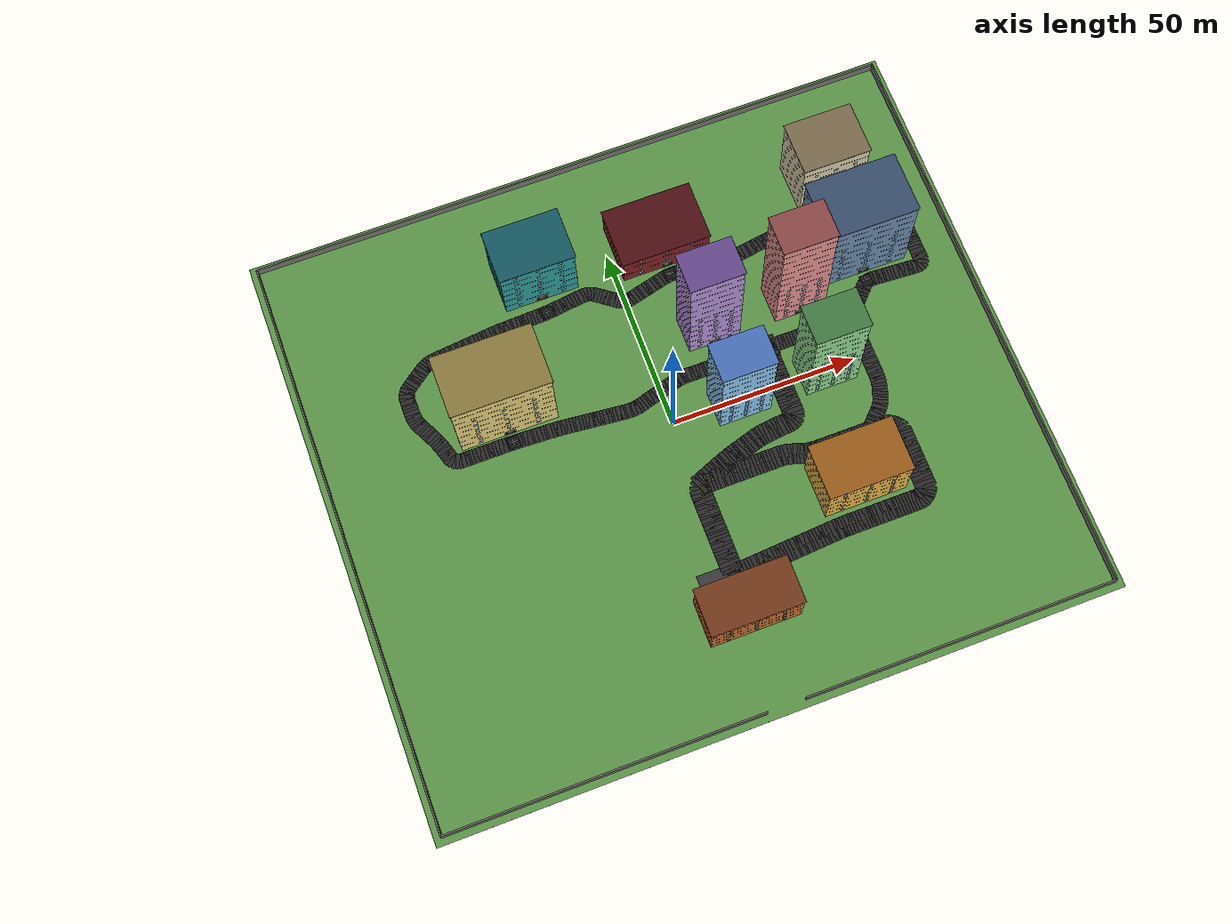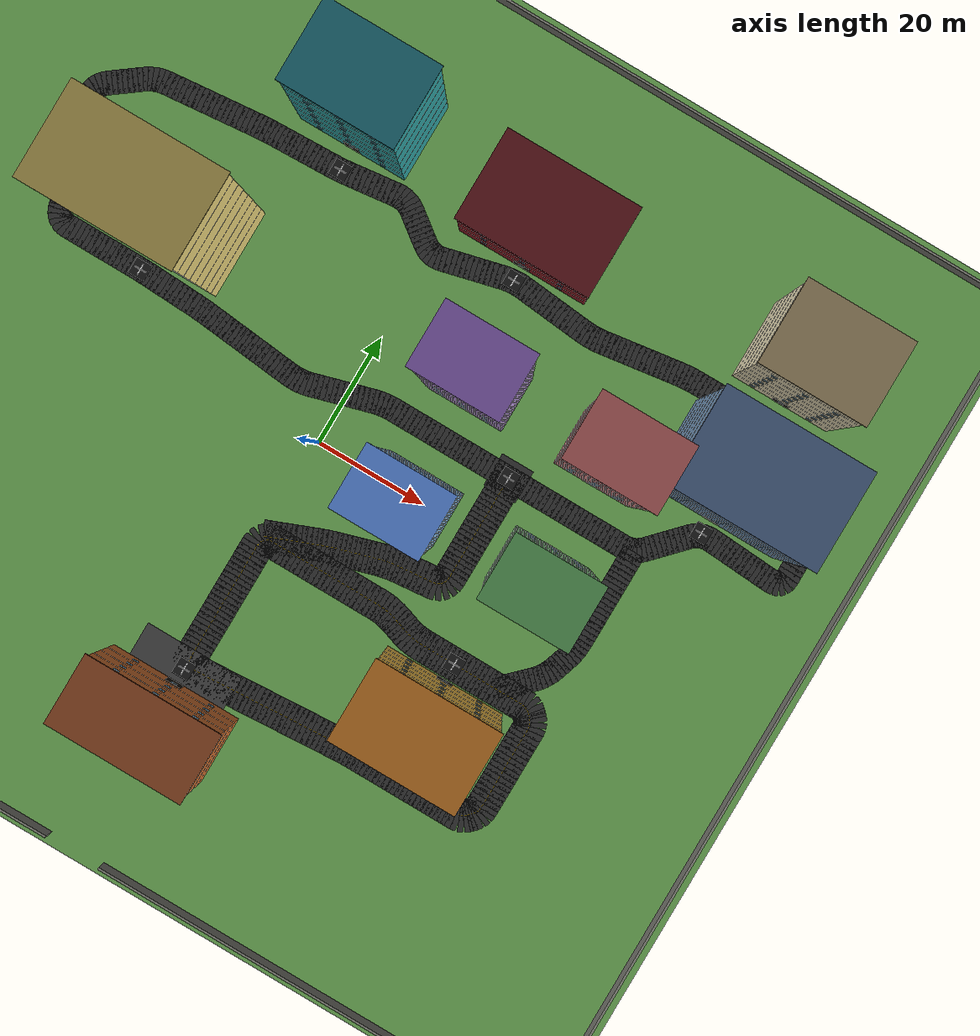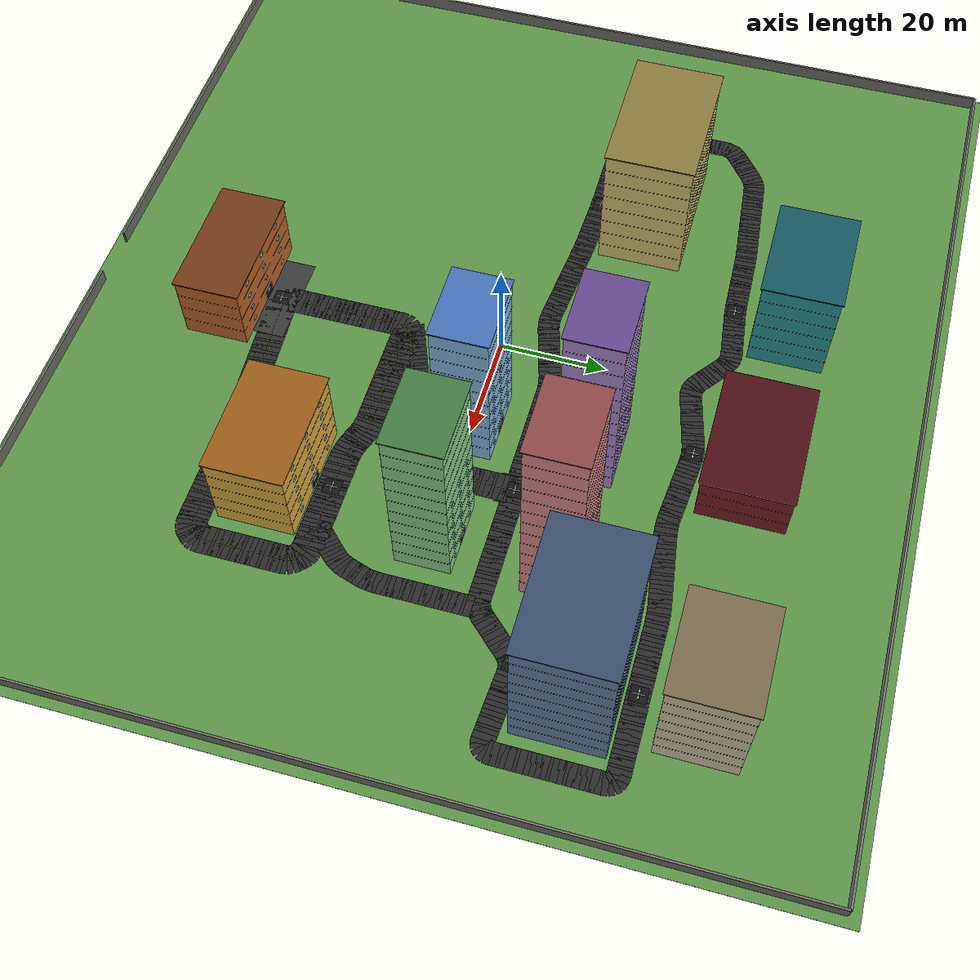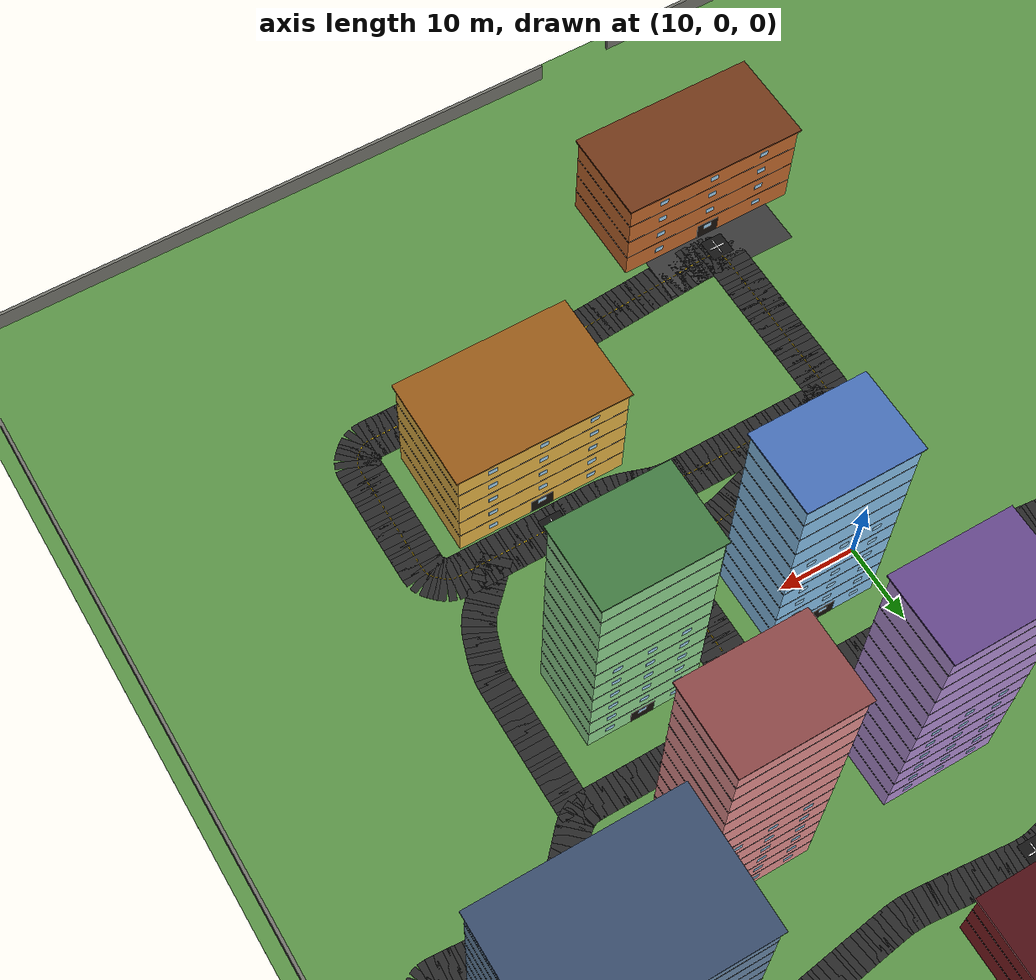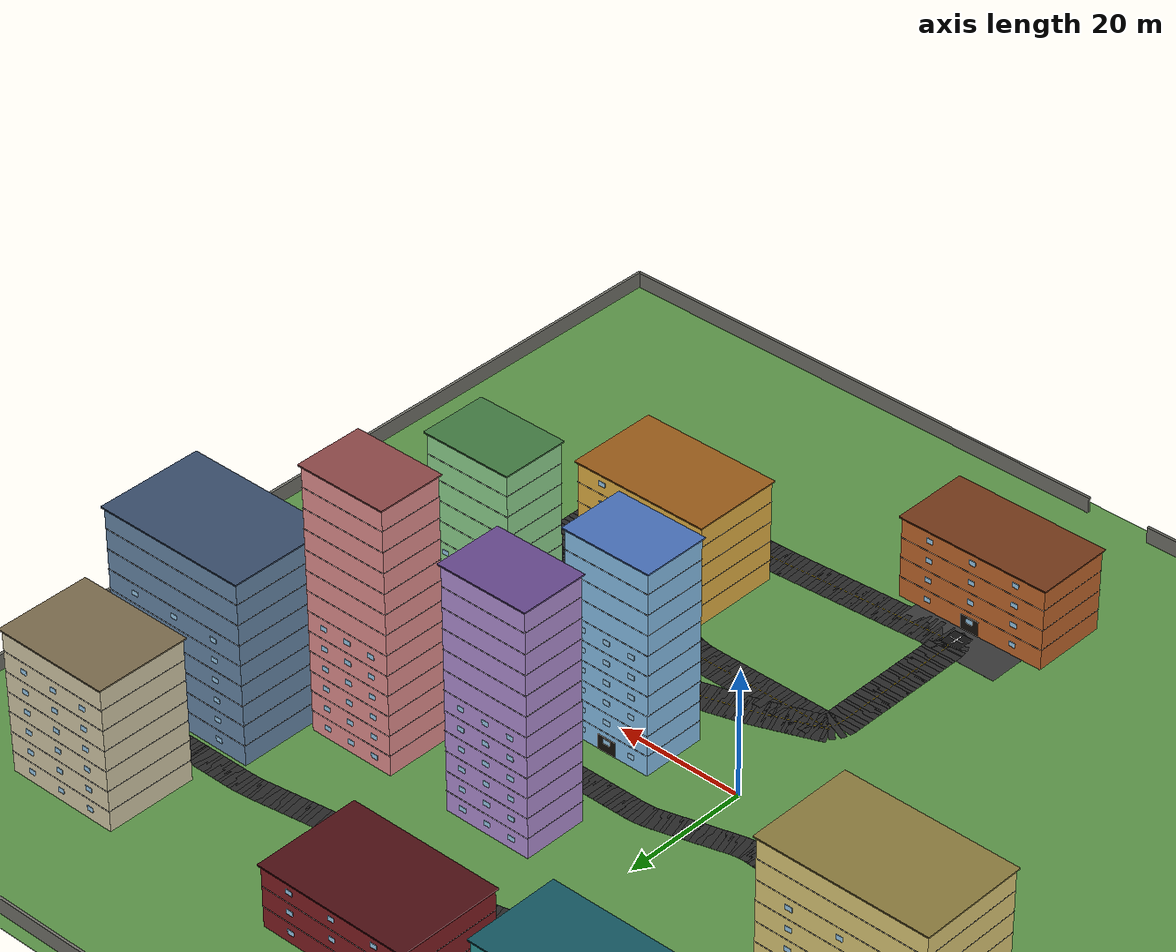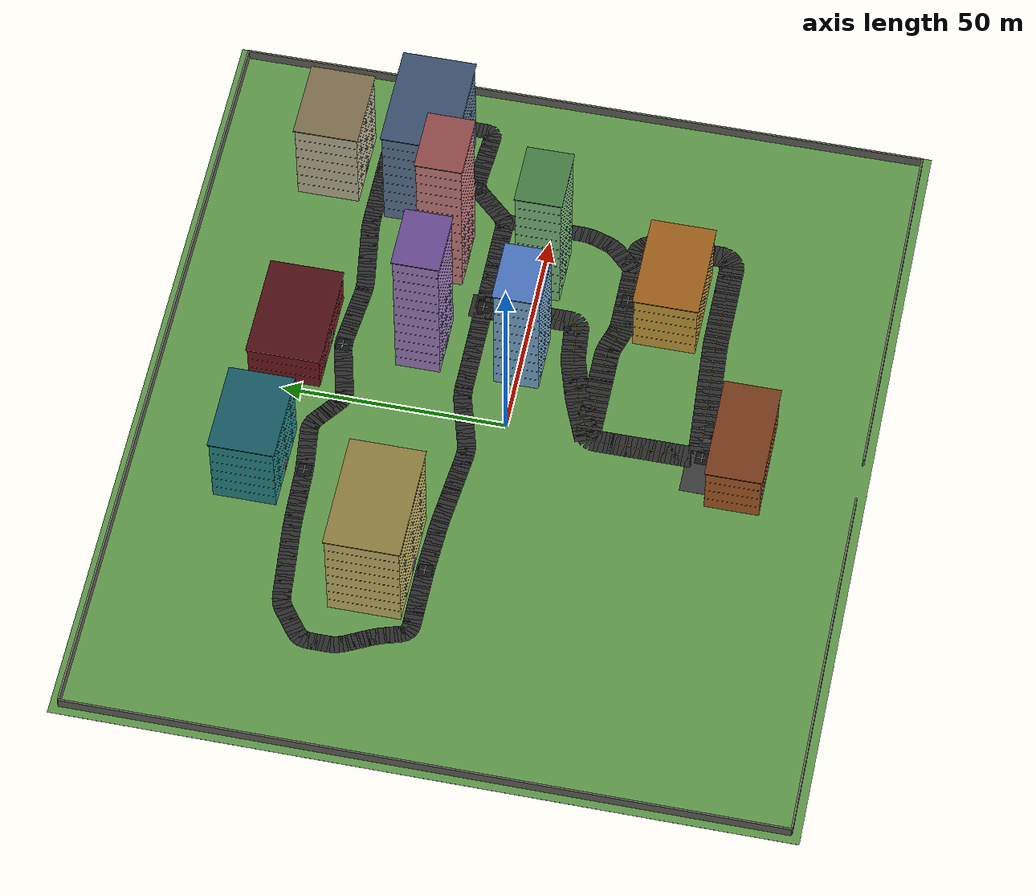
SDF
<sdf version='1.7'>
  <world name='campus_delivery'>
    <physics name='default_physics' type='ode'>
      <max_step_size>0.002</max_step_size>
      <real_time_update_rate>500</real_time_update_rate>
    </physics>
    <light name='sun' type='directional'>
      <pose>0 0 80 0 0 0</pose>
      <cast_shadows>true</cast_shadows>
      <diffuse>0.9 0.9 0.85 1</diffuse>
      <specular>0.2 0.2 0.2 1</specular>
      <direction>-0.4 0.2 -1</direction>
    </light>

    <model name='campus_ground'>
      <static>true</static>
      <link name='ground'>
        <pose>0.000 0.000 -0.015 0 0 0</pose>
        <collision name='collision'><pose>0 0 0 0 0 0</pose><geometry><box><size>180.000 160.000 0.030</size></box></geometry></collision>
        <visual name='visual'><pose>0 0 0 0 0 0</pose><geometry><box><size>180.000 160.000 0.030</size></box></geometry><material><ambient>0.360 0.580 0.280 1.000</ambient><diffuse>0.360 0.580 0.280 1.000</diffuse></material></visual>
      </link>
    </model>

    <model name='campus_wall'><static>true</static>
      <link name='west_wall'>
        <pose>-88.000 0.000 1.250 0 0 0</pose>
        <collision name='collision'><pose>0 0 0 0 0 0</pose><geometry><box><size>0.400 156.000 2.500</size></box></geometry></collision>
        <visual name='visual'><pose>0 0 0 0 0 0</pose><geometry><box><size>0.400 156.000 2.500</size></box></geometry><material><ambient>0.450 0.450 0.420 1.000</ambient><diffuse>0.450 0.450 0.420 1.000</diffuse></material></visual>
      </link>

      <link name='east_wall'>
        <pose>88.000 0.000 1.250 0 0 0</pose>
        <collision name='collision'><pose>0 0 0 0 0 0</pose><geometry><box><size>0.400 156.000 2.500</size></box></geometry></collision>
        <visual name='visual'><pose>0 0 0 0 0 0</pose><geometry><box><size>0.400 156.000 2.500</size></box></geometry><material><ambient>0.450 0.450 0.420 1.000</ambient><diffuse>0.450 0.450 0.420 1.000</diffuse></material></visual>
      </link>

      <link name='north_wall'>
        <pose>0.000 78.000 1.250 0 0 0</pose>
        <collision name='collision'><pose>0 0 0 0 0 0</pose><geometry><box><size>176.000 0.400 2.500</size></box></geometry></collision>
        <visual name='visual'><pose>0 0 0 0 0 0</pose><geometry><box><size>176.000 0.400 2.500</size></box></geometry><material><ambient>0.450 0.450 0.420 1.000</ambient><diffuse>0.450 0.450 0.420 1.000</diffuse></material></visual>
      </link>

      <link name='south_wall_west'>
        <pose>-46.500 -78.000 1.250 0 0 0</pose>
        <collision name='collision'><pose>0 0 0 0 0 0</pose><geometry><box><size>83.000 0.400 2.500</size></box></geometry></collision>
        <visual name='visual'><pose>0 0 0 0 0 0</pose><geometry><box><size>83.000 0.400 2.500</size></box></geometry><material><ambient>0.450 0.450 0.420 1.000</ambient><diffuse>0.450 0.450 0.420 1.000</diffuse></material></visual>
      </link>

      <link name='south_wall_east'>
        <pose>46.500 -78.000 1.250 0 0 0</pose>
        <collision name='collision'><pose>0 0 0 0 0 0</pose><geometry><box><size>83.000 0.400 2.500</size></box></geometry></collision>
        <visual name='visual'><pose>0 0 0 0 0 0</pose><geometry><box><size>83.000 0.400 2.500</size></box></geometry><material><ambient>0.450 0.450 0.420 1.000</ambient><diffuse>0.450 0.450 0.420 1.000</diffuse></material></visual>
      </link>
</model>
    <model name='campus_roads'><static>true</static><link name='south_service_loop_0000'><pose>0.000 -40.562 0.002 0 0 1.570796</pose><visual name='visual'><pose>0 0 0 0 0 0</pose><geometry><box><size>1.225 5.500 0.004</size></box></geometry><material><ambient>0.160 0.160 0.160 1.000</ambient><diffuse>0.160 0.160 0.160 1.000</diffuse></material></visual><visual name='center_line'><pose>0 0 0.008 0 0 0</pose><geometry><box><size>0.481 0.120 0.012</size></box></geometry><material><ambient>0.950 0.780 0.080 1.000</ambient><diffuse>0.950 0.780 0.080 1.000</diffuse></material></visual></link><link name='south_service_loop_0001'><pose>0.000 -39.688 0.002 0 0 1.570796</pose><visual name='visual'><pose>0 0 0 0 0 0</pose><geometry><box><size>1.225 5.500 0.004</size></box></geometry><material><ambient>0.160 0.160 0.160 1.000</ambient><diffuse>0.160 0.160 0.160 1.000</diffuse></material></visual><visual name='center_line'><pose>0 0 0.008 0 0 0</pose><geometry><box><size>0.481 0.120 0.012</size></box></geometry><material><ambient>0.950 0.780 0.080 1.000</ambient><diffuse>0.950 0.780 0.080 1.000</diffuse></material></visual></link><link name='south_service_loop_0002'><pose>0.000 -38.812 0.002 0 0 1.570796</pose><visual name='visual'><pose>0 0 0 0 0 0</pose><geometry><box><size>1.225 5.500 0.004</size></box></geometry><material><ambient>0.160 0.160 0.160 1.000</ambient><diffuse>0.160 0.160 0.160 1.000</diffuse></material></visual><visual name='center_line'><pose>0 0 0.008 0 0 0</pose><geometry><box><size>0.481 0.120 0.012</size></box></geometry><material><ambient>0.950 0.780 0.080 1.000</ambient><diffuse>0.950 0.780 0.080 1.000</diffuse></material></visual></link><link name='south_service_loop_0003'><pose>0.000 -37.938 0.002 0 0 1.570796</pose><visual name='visual'><pose>0 0 0 0 0 0</pose><geometry><box><size>1.225 5.500 0.004</size></box></geometry><material><ambient>0.160 0.160 0.160 1.000</ambient><diffuse>0.160 0.160 0.160 1.000</diffuse></material></visual><visual name='center_line'><pose>0 0 0.008 0 0 0</pose><geometry><box><size>0.481 0.120 0.012</size></box></geometry><material><ambient>0.950 0.780 0.080 1.000</ambient><diffuse>0.950 0.780 0.080 1.000</diffuse></material></visual></link><link name='south_service_loop_0004'><pose>0.000 -37.062 0.002 0 0 1.570796</pose><visual name='visual'><pose>0 0 0 0 0 0</pose><geometry><box><size>1.225 5.500 0.004</size></box></geometry><material><ambient>0.160 0.160 0.160 1.000</ambient><diffuse>0.160 0.160 0.160 1.000</diffuse></material></visual><visual name='center_line'><pose>0 0 0.008 0 0 0</pose><geometry><box><size>0.481 0.120 0.012</size></box></geometry><material><ambient>0.950 0.780 0.080 1.000</ambient><diffuse>0.950 0.780 0.080 1.000</diffuse></material></visual></link><link name='south_service_loop_0005'><pose>0.000 -36.188 0.002 0 0 1.570796</pose><visual name='visual'><pose>0 0 0 0 0 0</pose><geometry><box><size>1.225 5.500 0.004</size></box></geometry><material><ambient>0.160 0.160 0.160 1.000</ambient><diffuse>0.160 0.160 0.160 1.000</diffuse></material></visual><visual name='center_line'><pose>0 0 0.008 0 0 0</pose><geometry><box><size>0.481 0.120 0.012</size></box></geometry><material><ambient>0.950 0.780 0.080 1.000</ambient><diffuse>0.950 0.780 0.080 1.000</diffuse></material></visual></link><link name='south_service_loop_0006'><pose>0.000 -35.312 0.002 0 0 1.570796</pose><visual name='visual'><pose>0 0 0 0 0 0</pose><geometry><box><size>1.225 5.500 0.004</size></box></geometry><material><ambient>0.160 0.160 0.160 1.000</ambient><diffuse>0.160 0.160 0.160 1.000</diffuse></material></visual><visual name='center_line'><pose>0 0 0.008 0 0 0</pose><geometry><box><size>0.481 0.120 0.012</size></box></geometry><material><ambient>0.950 0.780 0.080 1.000</ambient><diffuse>0.950 0.780 0.080 1.000</diffuse></material></visual></link><link name='south_service_loop_0007'><pose>0.000 -34.438 0.002 0 0 1.570796</pose><visual name='visual'><pose>0 0 0 0 0 0</pose><geometry><box><size>1.225 5.500 0.004</size></box></geometry><material><ambient>0.160 0.160 0.160 1.000</ambient><diffuse>0.160 0.160 0.160 1.000</diffuse></material></visual><visual name='center_line'><pose>0 0 0.008 0 0 0</pose><geometry><box><size>0.481 0.120 0.012</size></box></geometry><material><ambient>0.950 0.780 0.080 1.000</ambient><diffuse>0.950 0.780 0.080 1.000</diffuse></material></visual></link><link name='south_service_loop_0008'><pose>0.000 -33.562 0.002 0 0 1.570796</pose><visual name='visual'><pose>0 0 0 0 0 0</pose><geometry><box><size>1.225 5.500 0.004</size></box></geometry><material><ambient>0.160 0.160 0.160 1.000</ambient><diffuse>0.160 0.160 0.160 1.000</diffuse></material></visual><visual name='center_line'><pose>0 0 0.008 0 0 0</pose><geometry><box><size>0.481 0.120 0.012</size></box></geometry><material><ambient>0.950 0.780 0.080 1.000</ambient><diffuse>0.950 0.780 0.080 1.000</diffuse></material></visual></link><link name='south_service_loop_0009'><pose>0.000 -32.688 0.002 0 0 1.570796</pose><visual name='visual'><pose>0 0 0 0 0 0</pose><geometry><box><size>1.225 5.500 0.004</size></box></geometry><material><ambient>0.160 0.160 0.160 1.000</ambient><diffuse>0.160 0.160 0.160 1.000</diffuse></material></visual><visual name='center_line'><pose>0 0 0.008 0 0 0</pose><geometry><box><size>0.481 0.120 0.012</size></box></geometry><material><ambient>0.950 0.780 0.080 1.000</ambient><diffuse>0.950 0.780 0.080 1.000</diffuse></material></visual></link><link name='south_service_loop_0010'><pose>0.000 -31.812 0.002 0 0 1.570796</pose><visual name='visual'><pose>0 0 0 0 0 0</pose><geometry><box><size>1.225 5.500 0.004</size></box></geometry><material><ambient>0.160 0.160 0.160 1.000</ambient><diffuse>0.160 0.160 0.160 1.000</diffuse></material></visual><visual name='center_line'><pose>0 0 0.008 0 0 0</pose><geometry><box><size>0.481 0.120 0.012</size></box></geometry><material><ambient>0.950 0.780 0.080 1.000</ambient><diffuse>0.950 0.780 0.080 1.000</diffuse></material></visual></link><link name='south_service_loop_0011'><pose>0.000 -30.938 0.002 0 0 1.570796</pose><visual name='visual'><pose>0 0 0 0 0 0</pose><geometry><box><size>1.225 5.500 0.004</size></box></geometry><material><ambient>0.160 0.160 0.160 1.000</ambient><diffuse>0.160 0.160 0.160 1.000</diffuse></material></visual><visual name='center_line'><pose>0 0 0.008 0 0 0</pose><geometry><box><size>0.481 0.120 0.012</size></box></geometry><material><ambient>0.950 0.780 0.080 1.000</ambient><diffuse>0.950 0.780 0.080 1.000</diffuse></material></visual></link><link name='south_service_loop_0012'><pose>0.000 -30.062 0.002 0 0 1.570796</pose><visual name='visual'><pose>0 0 0 0 0 0</pose><geometry><box><size>1.225 5.500 0.004</size></box></geometry><material><ambient>0.160 0.160 0.160 1.000</ambient><diffuse>0.160 0.160 0.160 1.000</diffuse></material></visual><visual name='center_line'><pose>0 0 0.008 0 0 0</pose><geometry><box><size>0.481 0.120 0.012</size></box></geometry><material><ambient>0.950 0.780 0.080 1.000</ambient><diffuse>0.950 0.780 0.080 1.000</diffuse></material></visual></link><link name='south_service_loop_0013'><pose>0.000 -29.188 0.002 0 0 1.570796</pose><visual name='visual'><pose>0 0 0 0 0 0</pose><geometry><box><size>1.225 5.500 0.004</size></box></geometry><material><ambient>0.160 0.160 0.160 1.000</ambient><diffuse>0.160 0.160 0.160 1.000</diffuse></material></visual><visual name='center_line'><pose>0 0 0.008 0 0 0</pose><geometry><box><size>0.481 0.120 0.012</size></box></geometry><material><ambient>0.950 0.780 0.080 1.000</ambient><diffuse>0.950 0.780 0.080 1.000</diffuse></material></visual></link><link name='south_service_loop_0014'><pose>0.000 -28.312 0.002 0 0 1.570796</pose><visual name='visual'><pose>0 0 0 0 0 0</pose><geometry><box><size>1.225 5.500 0.004</size></box></geometry><material><ambient>0.160 0.160 0.160 1.000</ambient><diffuse>0.160 0.160 0.160 1.000</diffuse></material></visual><visual name='center_line'><pose>0 0 0.008 0 0 0</pose><geometry><box><size>0.481 0.120 0.012</size></box></geometry><material><ambient>0.950 0.780 0.080 1.000</ambient><diffuse>0.950 0.780 0.080 1.000</diffuse></material></visual></link><link name='south_service_loop_0015'><pose>0.000 -27.438 0.002 0 0 1.570796</pose><visual name='visual'><pose>0 0 0 0 0 0</pose><geometry><box><size>1.225 5.500 0.004</size></box></geometry><material><ambient>0.160 0.160 0.160 1.000</ambient><diffuse>0.160 0.160 0.160 1.000</diffuse></material></visual><visual name='center_line'><pose>0 0 0.008 0 0 0</pose><geometry><box><size>0.481 0.120 0.012</size></box></geometry><material><ambient>0.950 0.780 0.080 1.000</ambient><diffuse>0.950 0.780 0.080 1.000</diffuse></material></visual></link><link name='south_service_loop_0016'><pose>0.000 -26.562 0.002 0 0 1.570796</pose><visual name='visual'><pose>0 0 0 0 0 0</pose><geometry><box><size>1.225 5.500 0.004</size></box></geometry><material><ambient>0.160 0.160 0.160 1.000</ambient><diffuse>0.160 0.160 0.160 1.000</diffuse></material></visual><visual name='center_line'><pose>0 0 0.008 0 0 0</pose><geometry><box><size>0.481 0.120 0.012</size></box></geometry><material><ambient>0.950 0.780 0.080 1.000</ambient><diffuse>0.950 0.780 0.080 1.000</diffuse></material></visual></link><link name='south_service_loop_0017'><pose>0.000 -25.688 0.002 0 0 1.570796</pose><visual name='visual'><pose>0 0 0 0 0 0</pose><geometry><box><size>1.225 5.500 0.004</size></box></geometry><material><ambient>0.160 0.160 0.160 1.000</ambient><diffuse>0.160 0.160 0.160 1.000</diffuse></material></visual><visual name='center_line'><pose>0 0 0.008 0 0 0</pose><geometry><box><size>0.481 0.120 0.012</size></box></geometry><material><ambient>0.950 0.780 0.080 1.000</ambient><diffuse>0.950 0.780 0.080 1.000</diffuse></material></visual></link><link name='south_service_loop_0018'><pose>0.000 -24.812 0.002 0 0 1.570796</pose><visual name='visual'><pose>0 0 0 0 0 0</pose><geometry><box><size>1.225 5.500 0.004</size></box></geometry><material><ambient>0.160 0.160 0.160 1.000</ambient><diffuse>0.160 0.160 0.160 1.000</diffuse></material></visual><visual name='center_line'><pose>0 0 0.008 0 0 0</pose><geometry><box><size>0.481 0.120 0.012</size></box></geometry><material><ambient>0.950 0.780 0.080 1.000</ambient><diffuse>0.950 0.780 0.080 1.000</diffuse></material></visual></link><link name='south_service_loop_0019'><pose>0.000 -23.938 0.002 0 0 1.570796</pose><visual name='visual'><pose>0 0 0 0 0 0</pose><geometry><box><size>1.225 5.500 0.004</size></box></geometry><material><ambient>0.160 0.160 0.160 1.000</ambient><diffuse>0.160 0.160 0.160 1.000</diffuse></material></visual><visual name='center_line'><pose>0 0 0.008 0 0 0</pose><geometry><box><size>0.481 0.120 0.012</size></box></geometry><material><ambient>0.950 0.780 0.080 1.000</ambient><diffuse>0.950 0.780 0.080 1.000</diffuse></material></visual></link><link name='south_service_loop_0020'><pose>0.000 -23.062 0.002 0 0 1.570796</pose><visual name='visual'><pose>0 0 0 0 0 0</pose><geometry><box><size>1.225 5.500 0.004</size></box></geometry><material><ambient>0.160 0.160 0.160 1.000</ambient><diffuse>0.160 0.160 0.160 1.000</diffuse></material></visual><visual name='center_line'><pose>0 0 0.008 0 0 0</pose><geometry><box><size>0.481 0.120 0.012</size></box></geometry><material><ambient>0.950 0.780 0.080 1.000</ambient><diffuse>0.950 0.780 0.080 1.000</diffuse></material></visual></link><link name='south_service_loop_0021'><pose>0.000 -22.188 0.002 0 0 1.570796</pose><visual name='visual'><pose>0 0 0 0 0 0</pose><geometry><box><size>1.225 5.500 0.004</size></box></geometry><material><ambient>0.160 0.160 0.160 1.000</ambient><diffuse>0.160 0.160 0.160 1.000</diffuse></material></visual><visual name='center_line'><pose>0 0 0.008 0 0 0</pose><geometry><box><size>0.481 0.120 0.012</size></box></geometry><material><ambient>0.950 0.780 0.080 1.000</ambient><diffuse>0.950 0.780 0.080 1.000</diffuse></material></visual></link><link name='south_service_loop_0022'><pose>0.000 -21.312 0.002 0 0 1.570796</pose><visual name='visual'><pose>0 0 0 0 0 0</pose><geometry><box><size>1.225 5.500 0.004</size></box></geometry><material><ambient>0.160 0.160 0.160 1.000</ambient><diffuse>0.160 0.160 0.160 1.000</diffuse></material></visual><visual name='center_line'><pose>0 0 0.008 0 0 0</pose><geometry><box><size>0.481 0.120 0.012</size></box></geometry><material><ambient>0.950 0.780 0.080 1.000</ambient><diffuse>0.950 0.780 0.080 1.000</diffuse></material></visual></link><link name='south_service_loop_0023'><pose>0.000 -20.438 0.002 0 0 1.570796</pose><visual name='visual'><pose>0 0 0 0 0 0</pose><geometry><box><size>1.225 5.500 0.004</size></box></geometry><material><ambient>0.160 0.160 0.160 1.000</ambient><diffuse>0.160 0.160 0.160 1.000</diffuse></material></visual><visual name='center_line'><pose>0 0 0.008 0 0 0</pose><geometry><box><size>0.481 0.120 0.012</size></box></geometry><material><ambient>0.950 0.780 0.080 1.000</ambient><diffuse>0.950 0.780 0.080 1.000</diffuse></material></visual></link><link name='south_service_loop_0024'><pose>0.040 -19.640 0.002 0 0 1.460139</pose><visual name='visual'><pose>0 0 0 0 0 0</pose><geometry><box><size>1.074 5.500 0.004</size></box></geometry><material><ambient>0.160 0.160 0.160 1.000</ambient><diffuse>0.160 0.160 0.160 1.000</diffuse></material></visual><visual name='center_line'><pose>0 0 0.008 0 0 0</pose><geometry><box><size>0.398 0.120 0.012</size></box></geometry><material><ambient>0.950 0.780 0.080 1.000</ambient><diffuse>0.950 0.780 0.080 1.000</diffuse></material></visual></link><link name='south_service_loop_0025'><pose>0.200 -19.000 0.002 0 0 1.165905</pose><visual name='visual'><pose>0 0 0 0 0 0</pose><geometry><box><size>0.959 5.500 0.004</size></box></geometry><material><ambient>0.160 0.160 0.160 1.000</ambient><diffuse>0.160 0.160 0.160 1.000</diffuse></material></visual><visual name='center_line'><pose>0 0 0.008 0 0 0</pose><geometry><box><size>0.335 0.120 0.012</size></box></geometry><material><ambient>0.950 0.780 0.080 1.000</ambient><diffuse>0.950 0.780 0.080 1.000</diffuse></material></visual></link><link name='south_service_loop_0026'><pose>0.520 -18.520 0.002 0 0 0.785398</pose><visual name='visual'><pose>0 0 0 0 0 0</pose><geometry><box><size>0.916 5.500 0.004</size></box></geometry><material><ambient>0.160 0.160 0.160 1.000</ambient><diffuse>0.160 0.160 0.160 1.000</diffuse></material></visual><visual name='center_line'><pose>0 0 0.008 0 0 0</pose><geometry><box><size>0.311 0.120 0.012</size></box></geometry><material><ambient>0.950 0.780 0.080 1.000</ambient><diffuse>0.950 0.780 0.080 1.000</diffuse></material></visual></link><link name='south_service_loop_0027'><pose>1.000 -18.200 0.002 0 0 0.404892</pose><visual name='visual'><pose>0 0 0 0 0 0</pose><geometry><box><size>0.959 5.500 0.004</size></box></geometry><material><ambient>0.160 0.160 0.160 1.000</ambient><diffuse>0.160 0.160 0.160 1.000</diffuse></material></visual><visual name='center_line'><pose>0 0 0.008 0 0 0</pose><geometry><box><size>0.335 0.120 0.012</size></box></geometry><material><ambient>0.950 0.780 0.080 1.000</ambient><diffuse>0.950 0.780 0.080 1.000</diffuse></material></visual></link><link name='south_service_loop_0028'><pose>1.640 -18.040 0.002 0 0 0.110657</pose><visual name='visual'><pose>0 0 0 0 0 0</pose><geometry><box><size>1.074 5.500 0.004</size></box></geometry><material><ambient>0.160 0.160 0.160 1.000</ambient><diffuse>0.160 0.160 0.160 1.000</diffuse></material></visual><visual name='center_line'><pose>0 0 0.008 0 0 0</pose><geometry><box><size>0.398 0.120 0.012</size></box></geometry><material><ambient>0.950 0.780 0.080 1.000</ambient><diffuse>0.950 0.780 0.080 1.000</diffuse></material></visual></link><link name='south_service_loop_0029'><pose>2.435 -18.000 0.002 0 0 0.000000</pose><visual name='visual'><pose>0 0 0 0 0 0</pose><geometry><box><size>1.220 5.500 0.004</size></box></geometry><material><ambient>0.160 0.160 0.160 1.000</ambient><diffuse>0.160 0.160 0.160 1.000</diffuse></material></visual><visual name='center_line'><pose>0 0 0.008 0 0 0</pose><geometry><box><size>0.478 0.120 0.012</size></box></geometry><material><ambient>0.950 0.780 0.080 1.000</ambient><diffuse>0.950 0.780 0.080 1.000</diffuse></material></visual></link><link name='south_service_loop_0030'><pose>3.304 -18.000 0.002 0 0 0.000000</pose><visual name='visual'><pose>0 0 0 0 0 0</pose><geometry><box><size>1.220 5.500 0.004</size></box></geometry><material><ambient>0.160 0.160 0.160 1.000</ambient><diffuse>0.160 0.160 0.160 1.000</diffuse></material></visual><visual name='center_line'><pose>0 0 0.008 0 0 0</pose><geometry><box><size>0.478 0.120 0.012</size></box></geometry><material><ambient>0.950 0.780 0.080 1.000</ambient><diffuse>0.950 0.780 0.080 1.000</diffuse></material></visual></link><link name='south_service_loop_0031'><pose>4.174 -18.000 0.002 0 0 0.000000</pose><visual name='visual'><pose>0 0 0 0 0 0</pose><geometry><box><size>1.220 5.500 0.004</size></box></geometry><material><ambient>0.160 0.160 0.160 1.000</ambient><diffuse>0.160 0.160 0.160 1.000</diffuse></material></visual><visual name='center_line'><pose>0 0 0.008 0 0 0</pose><geometry><box><size>0.478 0.120 0.012</size></box></geometry><material><ambient>0.950 0.780 0.080 1.000</ambient><diffuse>0.950 0.780 0.080 1.000</diffuse></material></visual></link><link name='south_service_loop_0032'><pose>5.043 -18.000 0.002 0 0 0.000000</pose><visual name='visual'><pose>0 0 0 0 0 0</pose><geometry><box><size>1.220 5.500 0.004</size></box></geometry><material><ambient>0.160 0.160 0.160 1.000</ambient><diffuse>0.160 0.160 0.160 1.000</diffuse></material></visual><visual name='center_line'><pose>0 0 0.008 0 0 0</pose><geometry><box><size>0.478 0.120 0.012</size></box></geometry><material><ambient>0.950 0.780 0.080 1.000</ambient><diffuse>0.950 0.780 0.080 1.000</diffuse></material></visual></link><link name='south_service_loop_0033'><pose>5.913 -18.000 0.002 0 0 0.000000</pose><visual name='visual'><pose>0 0 0 0 0 0</pose><geometry><box><size>1.220 5.500 0.004</size></box></geometry><material><ambient>0.160 0.160 0.160 1.000</ambient><diffuse>0.160 0.160 0.160 1.000</diffuse></material></visual><visual name='center_line'><pose>0 0 0.008 0 0 0</pose><geometry><box><size>0.478 0.120 0.012</size></box></geometry><material><ambient>0.950 0.780 0.080 1.000</ambient><diffuse>0.950 0.780 0.080 1.000</diffuse></material></visual></link><link name='south_service_loop_0034'><pose>6.783 -18.000 0.002 0 0 0.000000</pose><visual name='visual'><pose>0 0 0 0 0 0</pose><geometry><box><size>1.220 5.500 0.004</size></box></geometry><material><ambient>0.160 0.160 0.160 1.000</ambient><diffuse>0.160 0.160 0.160 1.000</diffuse></material></visual><visual name='center_line'><pose>0 0 0.008 0 0 0</pose><geometry><box><size>0.478 0.120 0.012</size></box></geometry><material><ambient>0.950 0.780 0.080 1.000</ambient><diffuse>0.950 0.780 0.080 1.000</diffuse></material></visual></link><link name='south_service_loop_0035'><pose>7.652 -18.000 0.002 0 0 0.000000</pose><visual name='visual'><pose>0 0 0 0 0 0</pose><geometry><box><size>1.220 5.500 0.004</size></box></geometry><material><ambient>0.160 0.160 0.160 1.000</ambient><diffuse>0.160 0.160 0.160 1.000</diffuse></material></visual><visual name='center_line'><pose>0 0 0.008 0 0 0</pose><geometry><box><size>0.478 0.120 0.012</size></box></geometry><material><ambient>0.950 0.780 0.080 1.000</ambient><diffuse>0.950 0.780 0.080 1.000</diffuse></material></visual></link><link name='south_service_loop_0036'><pose>8.522 -18.000 0.002 0 0 0.000000</pose><visual name='visual'><pose>0 0 0 0 0 0</pose><geometry><box><size>1.220 5.500 0.004</size></box></geometry><material><ambient>0.160 0.160 0.160 1.000</ambient><diffuse>0.160 0.160 0.160 1.000</diffuse></material></visual><visual name='center_line'><pose>0 0 0.008 0 0 0</pose><geometry><box><size>0.478 0.120 0.012</size></box></geometry><material><ambient>0.950 0.780 0.080 1.000</ambient><diffuse>0.950 0.780 0.080 1.000</diffuse></material></visual></link><link name='south_service_loop_0037'><pose>9.391 -18.000 0.002 0 0 0.000000</pose><visual name='visual'><pose>0 0 0 0 0 0</pose><geometry><box><size>1.220 5.500 0.004</size></box></geometry><material><ambient>0.160 0.160 0.160 1.000</ambient><diffuse>0.160 0.160 0.160 1.000</diffuse></material></visual><visual name='center_line'><pose>0 0 0.008 0 0 0</pose><geometry><box><size>0.478 0.120 0.012</size></box></geometry><material><ambient>0.950 0.780 0.080 1.000</ambient><diffuse>0.950 0.780 0.080 1.000</diffuse></material></visual></link><link name='south_service_loop_0038'><pose>10.261 -18.000 0.002 0 0 0.000000</pose><visual name='visual'><pose>0 0 0 0 0 0</pose><geometry><box><size>1.220 5.500 0.004</size></box></geometry><material><ambient>0.160 0.160 0.160 1.000</ambient><diffuse>0.160 0.160 0.160 1.000</diffuse></material></visual><visual name='center_line'><pose>0 0 0.008 0 0 0</pose><geometry><box><size>0.478 0.120 0.012</size></box></geometry><material><ambient>0.950 0.780 0.080 1.000</ambient><diffuse>0.950 0.780 0.080 1.000</diffuse></material></visual></link><link name='south_service_loop_0039'><pose>11.130 -18.000 0.002 0 0 0.000000</pose><visual name='visual'><pose>0 0 0 0 0 0</pose><geometry><box><size>1.220 5.500 0.004</size></box></geometry><material><ambient>0.160 0.160 0.160 1.000</ambient><diffuse>0.160 0.160 0.160 1.000</diffuse></material></visual><visual name='center_line'><pose>0 0 0.008 0 0 0</pose><geometry><box><size>0.478 0.120 0.012</size></box></geometry><material><ambient>0.950 0.780 0.080 1.000</ambient><diffuse>0.950 0.780 0.080 1.000</diffuse></material></visual></link><link name='south_service_loop_0040'><pose>12.000 -18.000 0.002 0 0 0.000000</pose><visual name='visual'><pose>0 0 0 0 0 0</pose><geometry><box><size>1.220 5.500 0.004</size></box></geometry><material><ambient>0.160 0.160 0.160 1.000</ambient><diffuse>0.160 0.160 0.160 1.000</diffuse></material></visual><visual name='center_line'><pose>0 0 0.008 0 0 0</pose><geometry><box><size>0.478 0.120 0.012</size></box></geometry><material><ambient>0.950 0.780 0.080 1.000</ambient><diffuse>0.950 0.780 0.080 1.000</diffuse></material></visual></link><link name='south_service_loop_0041'><pose>12.870 -18.000 0.002 0 0 0.000000</pose><visual name='visual'><pose>0 0 0 0 0 0</pose><geometry><box><size>1.220 5.500 0.004</size></box></geometry><material><ambient>0.160 0.160 0.160 1.000</ambient><diffuse>0.160 0.160 0.160 1.000</diffuse></material></visual><visual name='center_line'><pose>0 0 0.008 0 0 0</pose><geometry><box><size>0.478 0.120 0.012</size></box></geometry><material><ambient>0.950 0.780 0.080 1.000</ambient><diffuse>0.950 0.780 0.080 1.000</diffuse></material></visual></link><link name='south_service_loop_0042'><pose>13.739 -18.000 0.002 0 0 0.000000</pose><visual name='visual'><pose>0 0 0 0 0 0</pose><geometry><box><size>1.220 5.500 0.004</size></box></geometry><material><ambient>0.160 0.160 0.160 1.000</ambient><diffuse>0.160 0.160 0.160 1.000</diffuse></material></visual><visual name='center_line'><pose>0 0 0.008 0 0 0</pose><geometry><box><size>0.478 0.120 0.012</size></box></geometry><material><ambient>0.950 0.780 0.080 1.000</ambient><diffuse>0.950 0.780 0.080 1.000</diffuse></material></visual></link><link name='south_service_loop_0043'><pose>14.609 -18.000 0.002 0 0 0.000000</pose><visual name='visual'><pose>0 0 0 0 0 0</pose><geometry><box><size>1.220 5.500 0.004</size></box></geometry><material><ambient>0.160 0.160 0.160 1.000</ambient><diffuse>0.160 0.160 0.160 1.000</diffuse></material></visual><visual name='center_line'><pose>0 0 0.008 0 0 0</pose><geometry><box><size>0.478 0.120 0.012</size></box></geometry><material><ambient>0.950 0.780 0.080 1.000</ambient><diffuse>0.950 0.780 0.080 1.000</diffuse></material></visual></link><link name='south_service_loop_0044'><pose>15.478 -18.000 0.002 0 0 0.000000</pose><visual name='visual'><pose>0 0 0 0 0 0</pose><geometry><box><size>1.220 5.500 0.004</size></box></geometry><material><ambient>0.160 0.160 0.160 1.000</ambient><diffuse>0.160 0.160 0.160 1.000</diffuse></material></visual><visual name='center_line'><pose>0 0 0.008 0 0 0</pose><geometry><box><size>0.478 0.120 0.012</size></box></geometry><material><ambient>0.950 0.780 0.080 1.000</ambient><diffuse>0.950 0.780 0.080 1.000</diffuse></material></visual></link><link name='south_service_loop_0045'><pose>16.348 -18.000 0.002 0 0 0.000000</pose><visual name='visual'><pose>0 0 0 0 0 0</pose><geometry><box><size>1.220 5.500 0.004</size></box></geometry><material><ambient>0.160 0.160 0.160 1.000</ambient><diffuse>0.160 0.160 0.160 1.000</diffuse></material></visual><visual name='center_line'><pose>0 0 0.008 0 0 0</pose><geometry><box><size>0.478 0.120 0.012</size></box></geometry><material><ambient>0.950 0.780 0.080 1.000</ambient><diffuse>0.950 0.780 0.080 1.000</diffuse></material></visual></link><link name='south_service_loop_0046'><pose>17.217 -18.000 0.002 0 0 0.000000</pose><visual name='visual'><pose>0 0 0 0 0 0</pose><geometry><box><size>1.220 5.500 0.004</size></box></geometry><material><ambient>0.160 0.160 0.160 1.000</ambient><diffuse>0.160 0.160 0.160 1.000</diffuse></material></visual><visual name='center_line'><pose>0 0 0.008 0 0 0</pose><geometry><box><size>0.478 0.120 0.012</size></box></geometry><material><ambient>0.950 0.780 0.080 1.000</ambient><diffuse>0.950 0.780 0.080 1.000</diffuse></material></visual></link><link name='south_service_loop_0047'><pose>18.087 -18.000 0.002 0 0 0.000000</pose><visual name='visual'><pose>0 0 0 0 0 0</pose><geometry><box><size>1.220 5.500 0.004</size></box></geometry><material><ambient>0.160 0.160 0.160 1.000</ambient><diffuse>0.160 0.160 0.160 1.000</diffuse></material></visual><visual name='center_line'><pose>0 0 0.008 0 0 0</pose><geometry><box><size>0.478 0.120 0.012</size></box></geometry><material><ambient>0.950 0.780 0.080 1.000</ambient><diffuse>0.950 0.780 0.080 1.000</diffuse></material></visual></link><link name='south_service_loop_0048'><pose>18.957 -18.000 0.002 0 0 0.000000</pose><visual name='visual'><pose>0 0 0 0 0 0</pose><geometry><box><size>1.220 5.500 0.004</size></box></geometry><material><ambient>0.160 0.160 0.160 1.000</ambient><diffuse>0.160 0.160 0.160 1.000</diffuse></material></visual><visual name='center_line'><pose>0 0 0.008 0 0 0</pose><geometry><box><size>0.478 0.120 0.012</size></box></geometry><material><ambient>0.950 0.780 0.080 1.000</ambient><diffuse>0.950 0.780 0.080 1.000</diffuse></material></visual></link><link name='south_service_loop_0049'><pose>19.826 -18.000 0.002 0 0 0.000000</pose><visual name='visual'><pose>0 0 0 0 0 0</pose><geometry><box><size>1.220 5.500 0.004</size></box></geometry><material><ambient>0.160 0.160 0.160 1.000</ambient><diffuse>0.160 0.160 0.160 1.000</diffuse></material></visual><visual name='center_line'><pose>0 0 0.008 0 0 0</pose><geometry><box><size>0.478 0.120 0.012</size></box></geometry><material><ambient>0.950 0.780 0.080 1.000</ambient><diffuse>0.950 0.780 0.080 1.000</diffuse></material></visual></link><link name='south_service_loop_0050'><pose>20.696 -18.000 0.002 0 0 0.000000</pose><visual name='visual'><pose>0 0 0 0 0 0</pose><geometry><box><size>1.220 5.500 0.004</size></box></geometry><material><ambient>0.160 0.160 0.160 1.000</ambient><diffuse>0.160 0.160 0.160 1.000</diffuse></material></visual><visual name='center_line'><pose>0 0 0.008 0 0 0</pose><geometry><box><size>0.478 0.120 0.012</size></box></geometry><material><ambient>0.950 0.780 0.080 1.000</ambient><diffuse>0.950 0.780 0.080 1.000</diffuse></material></visual></link><link name='south_service_loop_0051'><pose>21.565 -18.000 0.002 0 0 0.000000</pose><visual name='visual'><pose>0 0 0 0 0 0</pose><geometry><box><size>1.220 5.500 0.004</size></box></geometry><material><ambient>0.160 0.160 0.160 1.000</ambient><diffuse>0.160 0.160 0.160 1.000</diffuse></material></visual><visual name='center_line'><pose>0 0 0.008 0 0 0</pose><geometry><box><size>0.478 0.120 0.012</size></box></geometry><material><ambient>0.950 0.780 0.080 1.000</ambient><diffuse>0.950 0.780 0.080 1.000</diffuse></material></visual></link><link name='south_service_loop_0052'><pose>22.398 -18.013 0.002 0 0 -0.031775</pose><visual name='visual'><pose>0 0 0 0 0 0</pose><geometry><box><size>1.146 5.500 0.004</size></box></geometry><material><ambient>0.160 0.160 0.160 1.000</ambient><diffuse>0.160 0.160 0.160 1.000</diffuse></material></visual><visual name='center_line'><pose>0 0 0.008 0 0 0</pose><geometry><box><size>0.438 0.120 0.012</size></box></geometry><material><ambient>0.950 0.780 0.080 1.000</ambient><diffuse>0.950 0.780 0.080 1.000</diffuse></material></visual></link><link name='south_service_loop_0053'><pose>23.190 -18.063 0.002 0 0 -0.096055</pose><visual name='visual'><pose>0 0 0 0 0 0</pose><geometry><box><size>1.141 5.500 0.004</size></box></geometry><material><ambient>0.160 0.160 0.160 1.000</ambient><diffuse>0.160 0.160 0.160 1.000</diffuse></material></visual><visual name='center_line'><pose>0 0 0.008 0 0 0</pose><geometry><box><size>0.435 0.120 0.012</size></box></geometry><material><ambient>0.950 0.780 0.080 1.000</ambient><diffuse>0.950 0.780 0.080 1.000</diffuse></material></visual></link><link name='south_service_loop_0054'><pose>23.973 -18.164 0.002 0 0 -0.160875</pose><visual name='visual'><pose>0 0 0 0 0 0</pose><geometry><box><size>1.140 5.500 0.004</size></box></geometry><material><ambient>0.160 0.160 0.160 1.000</ambient><diffuse>0.160 0.160 0.160 1.000</diffuse></material></visual><visual name='center_line'><pose>0 0 0.008 0 0 0</pose><geometry><box><size>0.434 0.120 0.012</size></box></geometry><material><ambient>0.950 0.780 0.080 1.000</ambient><diffuse>0.950 0.780 0.080 1.000</diffuse></material></visual></link><link name='south_service_loop_0055'><pose>24.749 -18.316 0.002 0 0 -0.225695</pose><visual name='visual'><pose>0 0 0 0 0 0</pose><geometry><box><size>1.141 5.500 0.004</size></box></geometry><material><ambient>0.160 0.160 0.160 1.000</ambient><diffuse>0.160 0.160 0.160 1.000</diffuse></material></visual><visual name='center_line'><pose>0 0 0.008 0 0 0</pose><geometry><box><size>0.435 0.120 0.012</size></box></geometry><material><ambient>0.950 0.780 0.080 1.000</ambient><diffuse>0.950 0.780 0.080 1.000</diffuse></material></visual></link><link name='south_service_loop_0056'><pose>25.516 -18.519 0.002 0 0 -0.289975</pose><visual name='visual'><pose>0 0 0 0 0 0</pose><geometry><box><size>1.146 5.500 0.004</size></box></geometry><material><ambient>0.160 0.160 0.160 1.000</ambient><diffuse>0.160 0.160 0.160 1.000</diffuse></material></visual><visual name='center_line'><pose>0 0 0.008 0 0 0</pose><geometry><box><size>0.438 0.120 0.012</size></box></geometry><material><ambient>0.950 0.780 0.080 1.000</ambient><diffuse>0.950 0.780 0.080 1.000</diffuse></material></visual></link><link name='south_service_loop_0057'><pose>26.265 -18.755 0.002 0 0 -0.321751</pose><visual name='visual'><pose>0 0 0 0 0 0</pose><geometry><box><size>1.125 5.500 0.004</size></box></geometry><material><ambient>0.160 0.160 0.160 1.000</ambient><diffuse>0.160 0.160 0.160 1.000</diffuse></material></visual><visual name='center_line'><pose>0 0 0.008 0 0 0</pose><geometry><box><size>0.426 0.120 0.012</size></box></geometry><material><ambient>0.950 0.780 0.080 1.000</ambient><diffuse>0.950 0.780 0.080 1.000</diffuse></material></visual></link><link name='south_service_loop_0058'><pose>27.000 -19.000 0.002 0 0 -0.321751</pose><visual name='visual'><pose>0 0 0 0 0 0</pose><geometry><box><size>1.125 5.500 0.004</size></box></geometry><material><ambient>0.160 0.160 0.160 1.000</ambient><diffuse>0.160 0.160 0.160 1.000</diffuse></material></visual><visual name='center_line'><pose>0 0 0.008 0 0 0</pose><geometry><box><size>0.426 0.120 0.012</size></box></geometry><material><ambient>0.950 0.780 0.080 1.000</ambient><diffuse>0.950 0.780 0.080 1.000</diffuse></material></visual></link><link name='south_service_loop_0059'><pose>27.735 -19.245 0.002 0 0 -0.321751</pose><visual name='visual'><pose>0 0 0 0 0 0</pose><geometry><box><size>1.125 5.500 0.004</size></box></geometry><material><ambient>0.160 0.160 0.160 1.000</ambient><diffuse>0.160 0.160 0.160 1.000</diffuse></material></visual><visual name='center_line'><pose>0 0 0.008 0 0 0</pose><geometry><box><size>0.426 0.120 0.012</size></box></geometry><material><ambient>0.950 0.780 0.080 1.000</ambient><diffuse>0.950 0.780 0.080 1.000</diffuse></material></visual></link><link name='south_service_loop_0060'><pose>28.484 -19.481 0.002 0 0 -0.289975</pose><visual name='visual'><pose>0 0 0 0 0 0</pose><geometry><box><size>1.146 5.500 0.004</size></box></geometry><material><ambient>0.160 0.160 0.160 1.000</ambient><diffuse>0.160 0.160 0.160 1.000</diffuse></material></visual><visual name='center_line'><pose>0 0 0.008 0 0 0</pose><geometry><box><size>0.438 0.120 0.012</size></box></geometry><material><ambient>0.950 0.780 0.080 1.000</ambient><diffuse>0.950 0.780 0.080 1.000</diffuse></material></visual></link><link name='south_service_loop_0061'><pose>29.251 -19.684 0.002 0 0 -0.225695</pose><visual name='visual'><pose>0 0 0 0 0 0</pose><geometry><box><size>1.141 5.500 0.004</size></box></geometry><material><ambient>0.160 0.160 0.160 1.000</ambient><diffuse>0.160 0.160 0.160 1.000</diffuse></material></visual><visual name='center_line'><pose>0 0 0.008 0 0 0</pose><geometry><box><size>0.435 0.120 0.012</size></box></geometry><material><ambient>0.950 0.780 0.080 1.000</ambient><diffuse>0.950 0.780 0.080 1.000</diffuse></material></visual></link><link name='south_service_loop_0062'><pose>30.027 -19.836 0.002 0 0 -0.160875</pose><visual name='visual'><pose>0 0 0 0 0 0</pose><geometry><box><size>1.140 5.500 0.004</size></box></geometry><material><ambient>0.160 0.160 0.160 1.000</ambient><diffuse>0.160 0.160 0.160 1.000</diffuse></material></visual><visual name='center_line'><pose>0 0 0.008 0 0 0</pose><geometry><box><size>0.434 0.120 0.012</size></box></geometry><material><ambient>0.950 0.780 0.080 1.000</ambient><diffuse>0.950 0.780 0.080 1.000</diffuse></material></visual></link><link name='south_service_loop_0063'><pose>30.810 -19.937 0.002 0 0 -0.096055</pose><visual name='visual'><pose>0 0 0 0 0 0</pose><geometry><box><size>1.141 5.500 0.004</size></box></geometry><material><ambient>0.160 0.160 0.160 1.000</ambient><diffuse>0.160 0.160 0.160 1.000</diffuse></material></visual><visual name='center_line'><pose>0 0 0.008 0 0 0</pose><geometry><box><size>0.435 0.120 0.012</size></box></geometry><material><ambient>0.950 0.780 0.080 1.000</ambient><diffuse>0.950 0.780 0.080 1.000</diffuse></material></visual></link><link name='south_service_loop_0064'><pose>31.602 -19.987 0.002 0 0 -0.031775</pose><visual name='visual'><pose>0 0 0 0 0 0</pose><geometry><box><size>1.146 5.500 0.004</size></box></geometry><material><ambient>0.160 0.160 0.160 1.000</ambient><diffuse>0.160 0.160 0.160 1.000</diffuse></material></visual><visual name='center_line'><pose>0 0 0.008 0 0 0</pose><geometry><box><size>0.438 0.120 0.012</size></box></geometry><material><ambient>0.950 0.780 0.080 1.000</ambient><diffuse>0.950 0.780 0.080 1.000</diffuse></material></visual></link><link name='south_service_loop_0065'><pose>32.400 -20.000 0.002 0 0 0.000000</pose><visual name='visual'><pose>0 0 0 0 0 0</pose><geometry><box><size>1.150 5.500 0.004</size></box></geometry><material><ambient>0.160 0.160 0.160 1.000</ambient><diffuse>0.160 0.160 0.160 1.000</diffuse></material></visual><visual name='center_line'><pose>0 0 0.008 0 0 0</pose><geometry><box><size>0.440 0.120 0.012</size></box></geometry><material><ambient>0.950 0.780 0.080 1.000</ambient><diffuse>0.950 0.780 0.080 1.000</diffuse></material></visual></link><link name='south_service_loop_0066'><pose>33.200 -20.000 0.002 0 0 0.000000</pose><visual name='visual'><pose>0 0 0 0 0 0</pose><geometry><box><size>1.150 5.500 0.004</size></box></geometry><material><ambient>0.160 0.160 0.160 1.000</ambient><diffuse>0.160 0.160 0.160 1.000</diffuse></material></visual><visual name='center_line'><pose>0 0 0.008 0 0 0</pose><geometry><box><size>0.440 0.120 0.012</size></box></geometry><material><ambient>0.950 0.780 0.080 1.000</ambient><diffuse>0.950 0.780 0.080 1.000</diffuse></material></visual></link><link name='south_service_loop_0067'><pose>34.000 -20.000 0.002 0 0 0.000000</pose><visual name='visual'><pose>0 0 0 0 0 0</pose><geometry><box><size>1.150 5.500 0.004</size></box></geometry><material><ambient>0.160 0.160 0.160 1.000</ambient><diffuse>0.160 0.160 0.160 1.000</diffuse></material></visual><visual name='center_line'><pose>0 0 0.008 0 0 0</pose><geometry><box><size>0.440 0.120 0.012</size></box></geometry><material><ambient>0.950 0.780 0.080 1.000</ambient><diffuse>0.950 0.780 0.080 1.000</diffuse></material></visual></link><link name='south_service_loop_0068'><pose>34.800 -20.000 0.002 0 0 0.000000</pose><visual name='visual'><pose>0 0 0 0 0 0</pose><geometry><box><size>1.150 5.500 0.004</size></box></geometry><material><ambient>0.160 0.160 0.160 1.000</ambient><diffuse>0.160 0.160 0.160 1.000</diffuse></material></visual><visual name='center_line'><pose>0 0 0.008 0 0 0</pose><geometry><box><size>0.440 0.120 0.012</size></box></geometry><material><ambient>0.950 0.780 0.080 1.000</ambient><diffuse>0.950 0.780 0.080 1.000</diffuse></material></visual></link><link name='south_service_loop_0069'><pose>35.600 -20.000 0.002 0 0 0.000000</pose><visual name='visual'><pose>0 0 0 0 0 0</pose><geometry><box><size>1.150 5.500 0.004</size></box></geometry><material><ambient>0.160 0.160 0.160 1.000</ambient><diffuse>0.160 0.160 0.160 1.000</diffuse></material></visual><visual name='center_line'><pose>0 0 0.008 0 0 0</pose><geometry><box><size>0.440 0.120 0.012</size></box></geometry><material><ambient>0.950 0.780 0.080 1.000</ambient><diffuse>0.950 0.780 0.080 1.000</diffuse></material></visual></link><link name='south_service_loop_0070'><pose>36.400 -20.000 0.002 0 0 -0.000000</pose><visual name='visual'><pose>0 0 0 0 0 0</pose><geometry><box><size>1.150 5.500 0.004</size></box></geometry><material><ambient>0.160 0.160 0.160 1.000</ambient><diffuse>0.160 0.160 0.160 1.000</diffuse></material></visual><visual name='center_line'><pose>0 0 0.008 0 0 0</pose><geometry><box><size>0.440 0.120 0.012</size></box></geometry><material><ambient>0.950 0.780 0.080 1.000</ambient><diffuse>0.950 0.780 0.080 1.000</diffuse></material></visual></link><link name='south_service_loop_0071'><pose>37.200 -20.000 0.002 0 0 0.000000</pose><visual name='visual'><pose>0 0 0 0 0 0</pose><geometry><box><size>1.150 5.500 0.004</size></box></geometry><material><ambient>0.160 0.160 0.160 1.000</ambient><diffuse>0.160 0.160 0.160 1.000</diffuse></material></visual><visual name='center_line'><pose>0 0 0.008 0 0 0</pose><geometry><box><size>0.440 0.120 0.012</size></box></geometry><material><ambient>0.950 0.780 0.080 1.000</ambient><diffuse>0.950 0.780 0.080 1.000</diffuse></material></visual></link><link name='south_service_loop_0072'><pose>38.000 -20.000 0.002 0 0 -0.000000</pose><visual name='visual'><pose>0 0 0 0 0 0</pose><geometry><box><size>1.150 5.500 0.004</size></box></geometry><material><ambient>0.160 0.160 0.160 1.000</ambient><diffuse>0.160 0.160 0.160 1.000</diffuse></material></visual><visual name='center_line'><pose>0 0 0.008 0 0 0</pose><geometry><box><size>0.440 0.120 0.012</size></box></geometry><material><ambient>0.950 0.780 0.080 1.000</ambient><diffuse>0.950 0.780 0.080 1.000</diffuse></material></visual></link><link name='south_service_loop_0073'><pose>38.800 -20.000 0.002 0 0 0.000000</pose><visual name='visual'><pose>0 0 0 0 0 0</pose><geometry><box><size>1.150 5.500 0.004</size></box></geometry><material><ambient>0.160 0.160 0.160 1.000</ambient><diffuse>0.160 0.160 0.160 1.000</diffuse></material></visual><visual name='center_line'><pose>0 0 0.008 0 0 0</pose><geometry><box><size>0.440 0.120 0.012</size></box></geometry><material><ambient>0.950 0.780 0.080 1.000</ambient><diffuse>0.950 0.780 0.080 1.000</diffuse></material></visual></link><link name='south_service_loop_0074'><pose>39.600 -20.000 0.002 0 0 0.000000</pose><visual name='visual'><pose>0 0 0 0 0 0</pose><geometry><box><size>1.150 5.500 0.004</size></box></geometry><material><ambient>0.160 0.160 0.160 1.000</ambient><diffuse>0.160 0.160 0.160 1.000</diffuse></material></visual><visual name='center_line'><pose>0 0 0.008 0 0 0</pose><geometry><box><size>0.440 0.120 0.012</size></box></geometry><material><ambient>0.950 0.780 0.080 1.000</ambient><diffuse>0.950 0.780 0.080 1.000</diffuse></material></visual></link><link name='south_service_loop_0075'><pose>40.400 -20.000 0.002 0 0 0.000000</pose><visual name='visual'><pose>0 0 0 0 0 0</pose><geometry><box><size>1.150 5.500 0.004</size></box></geometry><material><ambient>0.160 0.160 0.160 1.000</ambient><diffuse>0.160 0.160 0.160 1.000</diffuse></material></visual><visual name='center_line'><pose>0 0 0.008 0 0 0</pose><geometry><box><size>0.440 0.120 0.012</size></box></geometry><material><ambient>0.950 0.780 0.080 1.000</ambient><diffuse>0.950 0.780 0.080 1.000</diffuse></material></visual></link><link name='south_service_loop_0076'><pose>41.200 -20.000 0.002 0 0 0.000000</pose><visual name='visual'><pose>0 0 0 0 0 0</pose><geometry><box><size>1.150 5.500 0.004</size></box></geometry><material><ambient>0.160 0.160 0.160 1.000</ambient><diffuse>0.160 0.160 0.160 1.000</diffuse></material></visual><visual name='center_line'><pose>0 0 0.008 0 0 0</pose><geometry><box><size>0.440 0.120 0.012</size></box></geometry><material><ambient>0.950 0.780 0.080 1.000</ambient><diffuse>0.950 0.780 0.080 1.000</diffuse></material></visual></link><link name='south_service_loop_0077'><pose>42.000 -20.000 0.002 0 0 0.000000</pose><visual name='visual'><pose>0 0 0 0 0 0</pose><geometry><box><size>1.150 5.500 0.004</size></box></geometry><material><ambient>0.160 0.160 0.160 1.000</ambient><diffuse>0.160 0.160 0.160 1.000</diffuse></material></visual><visual name='center_line'><pose>0 0 0.008 0 0 0</pose><geometry><box><size>0.440 0.120 0.012</size></box></geometry><material><ambient>0.950 0.780 0.080 1.000</ambient><diffuse>0.950 0.780 0.080 1.000</diffuse></material></visual></link><link name='south_service_loop_0078'><pose>42.800 -20.000 0.002 0 0 0.000000</pose><visual name='visual'><pose>0 0 0 0 0 0</pose><geometry><box><size>1.150 5.500 0.004</size></box></geometry><material><ambient>0.160 0.160 0.160 1.000</ambient><diffuse>0.160 0.160 0.160 1.000</diffuse></material></visual><visual name='center_line'><pose>0 0 0.008 0 0 0</pose><geometry><box><size>0.440 0.120 0.012</size></box></geometry><material><ambient>0.950 0.780 0.080 1.000</ambient><diffuse>0.950 0.780 0.080 1.000</diffuse></material></visual></link><link name='south_service_loop_0079'><pose>43.600 -20.000 0.002 0 0 0.000000</pose><visual name='visual'><pose>0 0 0 0 0 0</pose><geometry><box><size>1.150 5.500 0.004</size></box></geometry><material><ambient>0.160 0.160 0.160 1.000</ambient><diffuse>0.160 0.160 0.160 1.000</diffuse></material></visual><visual name='center_line'><pose>0 0 0.008 0 0 0</pose><geometry><box><size>0.440 0.120 0.012</size></box></geometry><material><ambient>0.950 0.780 0.080 1.000</ambient><diffuse>0.950 0.780 0.080 1.000</diffuse></material></visual></link><link name='south_service_loop_0080'><pose>44.400 -20.000 0.002 0 0 -0.000000</pose><visual name='visual'><pose>0 0 0 0 0 0</pose><geometry><box><size>1.150 5.500 0.004</size></box></geometry><material><ambient>0.160 0.160 0.160 1.000</ambient><diffuse>0.160 0.160 0.160 1.000</diffuse></material></visual><visual name='center_line'><pose>0 0 0.008 0 0 0</pose><geometry><box><size>0.440 0.120 0.012</size></box></geometry><material><ambient>0.950 0.780 0.080 1.000</ambient><diffuse>0.950 0.780 0.080 1.000</diffuse></material></visual></link><link name='south_service_loop_0081'><pose>45.200 -20.000 0.002 0 0 0.000000</pose><visual name='visual'><pose>0 0 0 0 0 0</pose><geometry><box><size>1.150 5.500 0.004</size></box></geometry><material><ambient>0.160 0.160 0.160 1.000</ambient><diffuse>0.160 0.160 0.160 1.000</diffuse></material></visual><visual name='center_line'><pose>0 0 0.008 0 0 0</pose><geometry><box><size>0.440 0.120 0.012</size></box></geometry><material><ambient>0.950 0.780 0.080 1.000</ambient><diffuse>0.950 0.780 0.080 1.000</diffuse></material></visual></link><link name='south_service_loop_0082'><pose>46.000 -20.000 0.002 0 0 -0.000000</pose><visual name='visual'><pose>0 0 0 0 0 0</pose><geometry><box><size>1.150 5.500 0.004</size></box></geometry><material><ambient>0.160 0.160 0.160 1.000</ambient><diffuse>0.160 0.160 0.160 1.000</diffuse></material></visual><visual name='center_line'><pose>0 0 0.008 0 0 0</pose><geometry><box><size>0.440 0.120 0.012</size></box></geometry><material><ambient>0.950 0.780 0.080 1.000</ambient><diffuse>0.950 0.780 0.080 1.000</diffuse></material></visual></link><link name='south_service_loop_0083'><pose>46.800 -20.000 0.002 0 0 0.000000</pose><visual name='visual'><pose>0 0 0 0 0 0</pose><geometry><box><size>1.150 5.500 0.004</size></box></geometry><material><ambient>0.160 0.160 0.160 1.000</ambient><diffuse>0.160 0.160 0.160 1.000</diffuse></material></visual><visual name='center_line'><pose>0 0 0.008 0 0 0</pose><geometry><box><size>0.440 0.120 0.012</size></box></geometry><material><ambient>0.950 0.780 0.080 1.000</ambient><diffuse>0.950 0.780 0.080 1.000</diffuse></material></visual></link><link name='south_service_loop_0084'><pose>47.600 -20.000 0.002 0 0 0.000000</pose><visual name='visual'><pose>0 0 0 0 0 0</pose><geometry><box><size>1.150 5.500 0.004</size></box></geometry><material><ambient>0.160 0.160 0.160 1.000</ambient><diffuse>0.160 0.160 0.160 1.000</diffuse></material></visual><visual name='center_line'><pose>0 0 0.008 0 0 0</pose><geometry><box><size>0.440 0.120 0.012</size></box></geometry><material><ambient>0.950 0.780 0.080 1.000</ambient><diffuse>0.950 0.780 0.080 1.000</diffuse></material></visual></link><link name='south_service_loop_0085'><pose>48.382 -20.000 0.002 0 0 0.000000</pose><visual name='visual'><pose>0 0 0 0 0 0</pose><geometry><box><size>1.114 5.500 0.004</size></box></geometry><material><ambient>0.160 0.160 0.160 1.000</ambient><diffuse>0.160 0.160 0.160 1.000</diffuse></material></visual><visual name='center_line'><pose>0 0 0.008 0 0 0</pose><geometry><box><size>0.420 0.120 0.012</size></box></geometry><material><ambient>0.950 0.780 0.080 1.000</ambient><diffuse>0.950 0.780 0.080 1.000</diffuse></material></visual></link><link name='south_service_loop_0086'><pose>49.146 -20.000 0.002 0 0 0.000000</pose><visual name='visual'><pose>0 0 0 0 0 0</pose><geometry><box><size>1.114 5.500 0.004</size></box></geometry><material><ambient>0.160 0.160 0.160 1.000</ambient><diffuse>0.160 0.160 0.160 1.000</diffuse></material></visual><visual name='center_line'><pose>0 0 0.008 0 0 0</pose><geometry><box><size>0.420 0.120 0.012</size></box></geometry><material><ambient>0.950 0.780 0.080 1.000</ambient><diffuse>0.950 0.780 0.080 1.000</diffuse></material></visual></link><link name='south_service_loop_0087'><pose>49.911 -20.000 0.002 0 0 0.000000</pose><visual name='visual'><pose>0 0 0 0 0 0</pose><geometry><box><size>1.114 5.500 0.004</size></box></geometry><material><ambient>0.160 0.160 0.160 1.000</ambient><diffuse>0.160 0.160 0.160 1.000</diffuse></material></visual><visual name='center_line'><pose>0 0 0.008 0 0 0</pose><geometry><box><size>0.420 0.120 0.012</size></box></geometry><material><ambient>0.950 0.780 0.080 1.000</ambient><diffuse>0.950 0.780 0.080 1.000</diffuse></material></visual></link><link name='south_service_loop_0088'><pose>50.675 -20.000 0.002 0 0 0.000000</pose><visual name='visual'><pose>0 0 0 0 0 0</pose><geometry><box><size>1.114 5.500 0.004</size></box></geometry><material><ambient>0.160 0.160 0.160 1.000</ambient><diffuse>0.160 0.160 0.160 1.000</diffuse></material></visual><visual name='center_line'><pose>0 0 0.008 0 0 0</pose><geometry><box><size>0.420 0.120 0.012</size></box></geometry><material><ambient>0.950 0.780 0.080 1.000</ambient><diffuse>0.950 0.780 0.080 1.000</diffuse></material></visual></link><link name='south_service_loop_0089'><pose>51.356 -20.037 0.002 0 0 -0.123271</pose><visual name='visual'><pose>0 0 0 0 0 0</pose><geometry><box><size>0.952 5.500 0.004</size></box></geometry><material><ambient>0.160 0.160 0.160 1.000</ambient><diffuse>0.160 0.160 0.160 1.000</diffuse></material></visual><visual name='center_line'><pose>0 0 0.008 0 0 0</pose><geometry><box><size>0.331 0.120 0.012</size></box></geometry><material><ambient>0.950 0.780 0.080 1.000</ambient><diffuse>0.950 0.780 0.080 1.000</diffuse></material></visual></link><link name='south_service_loop_0090'><pose>51.923 -20.185 0.002 0 0 -0.392699</pose><visual name='visual'><pose>0 0 0 0 0 0</pose><geometry><box><size>0.931 5.500 0.004</size></box></geometry><material><ambient>0.160 0.160 0.160 1.000</ambient><diffuse>0.160 0.160 0.160 1.000</diffuse></material></visual><visual name='center_line'><pose>0 0 0.008 0 0 0</pose><geometry><box><size>0.319 0.120 0.012</size></box></geometry><material><ambient>0.950 0.780 0.080 1.000</ambient><diffuse>0.950 0.780 0.080 1.000</diffuse></material></visual></link><link name='south_service_loop_0091'><pose>52.429 -20.481 0.002 0 0 -0.662127</pose><visual name='visual'><pose>0 0 0 0 0 0</pose><geometry><box><size>0.952 5.500 0.004</size></box></geometry><material><ambient>0.160 0.160 0.160 1.000</ambient><diffuse>0.160 0.160 0.160 1.000</diffuse></material></visual><visual name='center_line'><pose>0 0 0.008 0 0 0</pose><geometry><box><size>0.331 0.120 0.012</size></box></geometry><material><ambient>0.950 0.780 0.080 1.000</ambient><diffuse>0.950 0.780 0.080 1.000</diffuse></material></visual></link><link name='south_service_loop_0092'><pose>52.833 -20.833 0.002 0 0 -0.785398</pose><visual name='visual'><pose>0 0 0 0 0 0</pose><geometry><box><size>0.821 5.500 0.004</size></box></geometry><material><ambient>0.160 0.160 0.160 1.000</ambient><diffuse>0.160 0.160 0.160 1.000</diffuse></material></visual><visual name='center_line'><pose>0 0 0.008 0 0 0</pose><geometry><box><size>0.259 0.120 0.012</size></box></geometry><material><ambient>0.950 0.780 0.080 1.000</ambient><diffuse>0.950 0.780 0.080 1.000</diffuse></material></visual></link><link name='south_service_loop_0093'><pose>53.167 -21.167 0.002 0 0 -0.785398</pose><visual name='visual'><pose>0 0 0 0 0 0</pose><geometry><box><size>0.821 5.500 0.004</size></box></geometry><material><ambient>0.160 0.160 0.160 1.000</ambient><diffuse>0.160 0.160 0.160 1.000</diffuse></material></visual><visual name='center_line'><pose>0 0 0.008 0 0 0</pose><geometry><box><size>0.259 0.120 0.012</size></box></geometry><material><ambient>0.950 0.780 0.080 1.000</ambient><diffuse>0.950 0.780 0.080 1.000</diffuse></material></visual></link><link name='south_service_loop_0094'><pose>53.519 -21.571 0.002 0 0 -0.908669</pose><visual name='visual'><pose>0 0 0 0 0 0</pose><geometry><box><size>0.952 5.500 0.004</size></box></geometry><material><ambient>0.160 0.160 0.160 1.000</ambient><diffuse>0.160 0.160 0.160 1.000</diffuse></material></visual><visual name='center_line'><pose>0 0 0.008 0 0 0</pose><geometry><box><size>0.331 0.120 0.012</size></box></geometry><material><ambient>0.950 0.780 0.080 1.000</ambient><diffuse>0.950 0.780 0.080 1.000</diffuse></material></visual></link><link name='south_service_loop_0095'><pose>53.815 -22.077 0.002 0 0 -1.178097</pose><visual name='visual'><pose>0 0 0 0 0 0</pose><geometry><box><size>0.931 5.500 0.004</size></box></geometry><material><ambient>0.160 0.160 0.160 1.000</ambient><diffuse>0.160 0.160 0.160 1.000</diffuse></material></visual><visual name='center_line'><pose>0 0 0.008 0 0 0</pose><geometry><box><size>0.319 0.120 0.012</size></box></geometry><material><ambient>0.950 0.780 0.080 1.000</ambient><diffuse>0.950 0.780 0.080 1.000</diffuse></material></visual></link><link name='south_service_loop_0096'><pose>53.963 -22.644 0.002 0 0 -1.447525</pose><visual name='visual'><pose>0 0 0 0 0 0</pose><geometry><box><size>0.952 5.500 0.004</size></box></geometry><material><ambient>0.160 0.160 0.160 1.000</ambient><diffuse>0.160 0.160 0.160 1.000</diffuse></material></visual><visual name='center_line'><pose>0 0 0.008 0 0 0</pose><geometry><box><size>0.331 0.120 0.012</size></box></geometry><material><ambient>0.950 0.780 0.080 1.000</ambient><diffuse>0.950 0.780 0.080 1.000</diffuse></material></visual></link><link name='south_service_loop_0097'><pose>54.000 -23.387 0.002 0 0 -1.570796</pose><visual name='visual'><pose>0 0 0 0 0 0</pose><geometry><box><size>1.239 5.500 0.004</size></box></geometry><material><ambient>0.160 0.160 0.160 1.000</ambient><diffuse>0.160 0.160 0.160 1.000</diffuse></material></visual><visual name='center_line'><pose>0 0 0.008 0 0 0</pose><geometry><box><size>0.489 0.120 0.012</size></box></geometry><material><ambient>0.950 0.780 0.080 1.000</ambient><diffuse>0.950 0.780 0.080 1.000</diffuse></material></visual></link><link name='south_service_loop_0098'><pose>54.000 -24.276 0.002 0 0 -1.570796</pose><visual name='visual'><pose>0 0 0 0 0 0</pose><geometry><box><size>1.239 5.500 0.004</size></box></geometry><material><ambient>0.160 0.160 0.160 1.000</ambient><diffuse>0.160 0.160 0.160 1.000</diffuse></material></visual><visual name='center_line'><pose>0 0 0.008 0 0 0</pose><geometry><box><size>0.489 0.120 0.012</size></box></geometry><material><ambient>0.950 0.780 0.080 1.000</ambient><diffuse>0.950 0.780 0.080 1.000</diffuse></material></visual></link><link name='south_service_loop_0099'><pose>54.000 -25.166 0.002 0 0 -1.570796</pose><visual name='visual'><pose>0 0 0 0 0 0</pose><geometry><box><size>1.239 5.500 0.004</size></box></geometry><material><ambient>0.160 0.160 0.160 1.000</ambient><diffuse>0.160 0.160 0.160 1.000</diffuse></material></visual><visual name='center_line'><pose>0 0 0.008 0 0 0</pose><geometry><box><size>0.489 0.120 0.012</size></box></geometry><material><ambient>0.950 0.780 0.080 1.000</ambient><diffuse>0.950 0.780 0.080 1.000</diffuse></material></visual></link><link name='south_service_loop_0100'><pose>54.000 -26.055 0.002 0 0 -1.570796</pose><visual name='visual'><pose>0 0 0 0 0 0</pose><geometry><box><size>1.239 5.500 0.004</size></box></geometry><material><ambient>0.160 0.160 0.160 1.000</ambient><diffuse>0.160 0.160 0.160 1.000</diffuse></material></visual><visual name='center_line'><pose>0 0 0.008 0 0 0</pose><geometry><box><size>0.489 0.120 0.012</size></box></geometry><material><ambient>0.950 0.780 0.080 1.000</ambient><diffuse>0.950 0.780 0.080 1.000</diffuse></material></visual></link><link name='south_service_loop_0101'><pose>54.000 -26.944 0.002 0 0 -1.570796</pose><visual name='visual'><pose>0 0 0 0 0 0</pose><geometry><box><size>1.239 5.500 0.004</size></box></geometry><material><ambient>0.160 0.160 0.160 1.000</ambient><diffuse>0.160 0.160 0.160 1.000</diffuse></material></visual><visual name='center_line'><pose>0 0 0.008 0 0 0</pose><geometry><box><size>0.489 0.120 0.012</size></box></geometry><material><ambient>0.950 0.780 0.080 1.000</ambient><diffuse>0.950 0.780 0.080 1.000</diffuse></material></visual></link><link name='south_service_loop_0102'><pose>54.000 -27.833 0.002 0 0 -1.570796</pose><visual name='visual'><pose>0 0 0 0 0 0</pose><geometry><box><size>1.239 5.500 0.004</size></box></geometry><material><ambient>0.160 0.160 0.160 1.000</ambient><diffuse>0.160 0.160 0.160 1.000</diffuse></material></visual><visual name='center_line'><pose>0 0 0.008 0 0 0</pose><geometry><box><size>0.489 0.120 0.012</size></box></geometry><material><ambient>0.950 0.780 0.080 1.000</ambient><diffuse>0.950 0.780 0.080 1.000</diffuse></material></visual></link><link name='south_service_loop_0103'><pose>54.000 -28.722 0.002 0 0 -1.570796</pose><visual name='visual'><pose>0 0 0 0 0 0</pose><geometry><box><size>1.239 5.500 0.004</size></box></geometry><material><ambient>0.160 0.160 0.160 1.000</ambient><diffuse>0.160 0.160 0.160 1.000</diffuse></material></visual><visual name='center_line'><pose>0 0 0.008 0 0 0</pose><geometry><box><size>0.489 0.120 0.012</size></box></geometry><material><ambient>0.950 0.780 0.080 1.000</ambient><diffuse>0.950 0.780 0.080 1.000</diffuse></material></visual></link><link name='south_service_loop_0104'><pose>54.000 -29.611 0.002 0 0 -1.570796</pose><visual name='visual'><pose>0 0 0 0 0 0</pose><geometry><box><size>1.239 5.500 0.004</size></box></geometry><material><ambient>0.160 0.160 0.160 1.000</ambient><diffuse>0.160 0.160 0.160 1.000</diffuse></material></visual><visual name='center_line'><pose>0 0 0.008 0 0 0</pose><geometry><box><size>0.489 0.120 0.012</size></box></geometry><material><ambient>0.950 0.780 0.080 1.000</ambient><diffuse>0.950 0.780 0.080 1.000</diffuse></material></visual></link><link name='south_service_loop_0105'><pose>54.000 -30.500 0.002 0 0 -1.570796</pose><visual name='visual'><pose>0 0 0 0 0 0</pose><geometry><box><size>1.239 5.500 0.004</size></box></geometry><material><ambient>0.160 0.160 0.160 1.000</ambient><diffuse>0.160 0.160 0.160 1.000</diffuse></material></visual><visual name='center_line'><pose>0 0 0.008 0 0 0</pose><geometry><box><size>0.489 0.120 0.012</size></box></geometry><material><ambient>0.950 0.780 0.080 1.000</ambient><diffuse>0.950 0.780 0.080 1.000</diffuse></material></visual></link><link name='south_service_loop_0106'><pose>54.000 -31.389 0.002 0 0 -1.570796</pose><visual name='visual'><pose>0 0 0 0 0 0</pose><geometry><box><size>1.239 5.500 0.004</size></box></geometry><material><ambient>0.160 0.160 0.160 1.000</ambient><diffuse>0.160 0.160 0.160 1.000</diffuse></material></visual><visual name='center_line'><pose>0 0 0.008 0 0 0</pose><geometry><box><size>0.489 0.120 0.012</size></box></geometry><material><ambient>0.950 0.780 0.080 1.000</ambient><diffuse>0.950 0.780 0.080 1.000</diffuse></material></visual></link><link name='south_service_loop_0107'><pose>54.000 -32.278 0.002 0 0 -1.570796</pose><visual name='visual'><pose>0 0 0 0 0 0</pose><geometry><box><size>1.239 5.500 0.004</size></box></geometry><material><ambient>0.160 0.160 0.160 1.000</ambient><diffuse>0.160 0.160 0.160 1.000</diffuse></material></visual><visual name='center_line'><pose>0 0 0.008 0 0 0</pose><geometry><box><size>0.489 0.120 0.012</size></box></geometry><material><ambient>0.950 0.780 0.080 1.000</ambient><diffuse>0.950 0.780 0.080 1.000</diffuse></material></visual></link><link name='south_service_loop_0108'><pose>54.000 -33.167 0.002 0 0 -1.570796</pose><visual name='visual'><pose>0 0 0 0 0 0</pose><geometry><box><size>1.239 5.500 0.004</size></box></geometry><material><ambient>0.160 0.160 0.160 1.000</ambient><diffuse>0.160 0.160 0.160 1.000</diffuse></material></visual><visual name='center_line'><pose>0 0 0.008 0 0 0</pose><geometry><box><size>0.489 0.120 0.012</size></box></geometry><material><ambient>0.950 0.780 0.080 1.000</ambient><diffuse>0.950 0.780 0.080 1.000</diffuse></material></visual></link><link name='south_service_loop_0109'><pose>54.000 -34.056 0.002 0 0 -1.570796</pose><visual name='visual'><pose>0 0 0 0 0 0</pose><geometry><box><size>1.239 5.500 0.004</size></box></geometry><material><ambient>0.160 0.160 0.160 1.000</ambient><diffuse>0.160 0.160 0.160 1.000</diffuse></material></visual><visual name='center_line'><pose>0 0 0.008 0 0 0</pose><geometry><box><size>0.489 0.120 0.012</size></box></geometry><material><ambient>0.950 0.780 0.080 1.000</ambient><diffuse>0.950 0.780 0.080 1.000</diffuse></material></visual></link><link name='south_service_loop_0110'><pose>54.000 -34.945 0.002 0 0 -1.570796</pose><visual name='visual'><pose>0 0 0 0 0 0</pose><geometry><box><size>1.239 5.500 0.004</size></box></geometry><material><ambient>0.160 0.160 0.160 1.000</ambient><diffuse>0.160 0.160 0.160 1.000</diffuse></material></visual><visual name='center_line'><pose>0 0 0.008 0 0 0</pose><geometry><box><size>0.489 0.120 0.012</size></box></geometry><material><ambient>0.950 0.780 0.080 1.000</ambient><diffuse>0.950 0.780 0.080 1.000</diffuse></material></visual></link><link name='south_service_loop_0111'><pose>54.000 -35.834 0.002 0 0 -1.570796</pose><visual name='visual'><pose>0 0 0 0 0 0</pose><geometry><box><size>1.239 5.500 0.004</size></box></geometry><material><ambient>0.160 0.160 0.160 1.000</ambient><diffuse>0.160 0.160 0.160 1.000</diffuse></material></visual><visual name='center_line'><pose>0 0 0.008 0 0 0</pose><geometry><box><size>0.489 0.120 0.012</size></box></geometry><material><ambient>0.950 0.780 0.080 1.000</ambient><diffuse>0.950 0.780 0.080 1.000</diffuse></material></visual></link><link name='south_service_loop_0112'><pose>54.000 -36.724 0.002 0 0 -1.570796</pose><visual name='visual'><pose>0 0 0 0 0 0</pose><geometry><box><size>1.239 5.500 0.004</size></box></geometry><material><ambient>0.160 0.160 0.160 1.000</ambient><diffuse>0.160 0.160 0.160 1.000</diffuse></material></visual><visual name='center_line'><pose>0 0 0.008 0 0 0</pose><geometry><box><size>0.489 0.120 0.012</size></box></geometry><material><ambient>0.950 0.780 0.080 1.000</ambient><diffuse>0.950 0.780 0.080 1.000</diffuse></material></visual></link><link name='south_service_loop_0113'><pose>54.000 -37.613 0.002 0 0 -1.570796</pose><visual name='visual'><pose>0 0 0 0 0 0</pose><geometry><box><size>1.239 5.500 0.004</size></box></geometry><material><ambient>0.160 0.160 0.160 1.000</ambient><diffuse>0.160 0.160 0.160 1.000</diffuse></material></visual><visual name='center_line'><pose>0 0 0.008 0 0 0</pose><geometry><box><size>0.489 0.120 0.012</size></box></geometry><material><ambient>0.950 0.780 0.080 1.000</ambient><diffuse>0.950 0.780 0.080 1.000</diffuse></material></visual></link><link name='south_service_loop_0114'><pose>53.963 -38.356 0.002 0 0 -1.694067</pose><visual name='visual'><pose>0 0 0 0 0 0</pose><geometry><box><size>0.952 5.500 0.004</size></box></geometry><material><ambient>0.160 0.160 0.160 1.000</ambient><diffuse>0.160 0.160 0.160 1.000</diffuse></material></visual><visual name='center_line'><pose>0 0 0.008 0 0 0</pose><geometry><box><size>0.331 0.120 0.012</size></box></geometry><material><ambient>0.950 0.780 0.080 1.000</ambient><diffuse>0.950 0.780 0.080 1.000</diffuse></material></visual></link><link name='south_service_loop_0115'><pose>53.815 -38.923 0.002 0 0 -1.963495</pose><visual name='visual'><pose>0 0 0 0 0 0</pose><geometry><box><size>0.931 5.500 0.004</size></box></geometry><material><ambient>0.160 0.160 0.160 1.000</ambient><diffuse>0.160 0.160 0.160 1.000</diffuse></material></visual><visual name='center_line'><pose>0 0 0.008 0 0 0</pose><geometry><box><size>0.319 0.120 0.012</size></box></geometry><material><ambient>0.950 0.780 0.080 1.000</ambient><diffuse>0.950 0.780 0.080 1.000</diffuse></material></visual></link><link name='south_service_loop_0116'><pose>53.519 -39.429 0.002 0 0 -2.232923</pose><visual name='visual'><pose>0 0 0 0 0 0</pose><geometry><box><size>0.952 5.500 0.004</size></box></geometry><material><ambient>0.160 0.160 0.160 1.000</ambient><diffuse>0.160 0.160 0.160 1.000</diffuse></material></visual><visual name='center_line'><pose>0 0 0.008 0 0 0</pose><geometry><box><size>0.331 0.120 0.012</size></box></geometry><material><ambient>0.950 0.780 0.080 1.000</ambient><diffuse>0.950 0.780 0.080 1.000</diffuse></material></visual></link><link name='south_service_loop_0117'><pose>53.167 -39.833 0.002 0 0 -2.356194</pose><visual name='visual'><pose>0 0 0 0 0 0</pose><geometry><box><size>0.821 5.500 0.004</size></box></geometry><material><ambient>0.160 0.160 0.160 1.000</ambient><diffuse>0.160 0.160 0.160 1.000</diffuse></material></visual><visual name='center_line'><pose>0 0 0.008 0 0 0</pose><geometry><box><size>0.259 0.120 0.012</size></box></geometry><material><ambient>0.950 0.780 0.080 1.000</ambient><diffuse>0.950 0.780 0.080 1.000</diffuse></material></visual></link><link name='south_service_loop_0118'><pose>52.833 -40.167 0.002 0 0 -2.356194</pose><visual name='visual'><pose>0 0 0 0 0 0</pose><geometry><box><size>0.821 5.500 0.004</size></box></geometry><material><ambient>0.160 0.160 0.160 1.000</ambient><diffuse>0.160 0.160 0.160 1.000</diffuse></material></visual><visual name='center_line'><pose>0 0 0.008 0 0 0</pose><geometry><box><size>0.259 0.120 0.012</size></box></geometry><material><ambient>0.950 0.780 0.080 1.000</ambient><diffuse>0.950 0.780 0.080 1.000</diffuse></material></visual></link><link name='south_service_loop_0119'><pose>52.429 -40.519 0.002 0 0 -2.479466</pose><visual name='visual'><pose>0 0 0 0 0 0</pose><geometry><box><size>0.952 5.500 0.004</size></box></geometry><material><ambient>0.160 0.160 0.160 1.000</ambient><diffuse>0.160 0.160 0.160 1.000</diffuse></material></visual><visual name='center_line'><pose>0 0 0.008 0 0 0</pose><geometry><box><size>0.331 0.120 0.012</size></box></geometry><material><ambient>0.950 0.780 0.080 1.000</ambient><diffuse>0.950 0.780 0.080 1.000</diffuse></material></visual></link><link name='south_service_loop_0120'><pose>51.923 -40.815 0.002 0 0 -2.748894</pose><visual name='visual'><pose>0 0 0 0 0 0</pose><geometry><box><size>0.931 5.500 0.004</size></box></geometry><material><ambient>0.160 0.160 0.160 1.000</ambient><diffuse>0.160 0.160 0.160 1.000</diffuse></material></visual><visual name='center_line'><pose>0 0 0.008 0 0 0</pose><geometry><box><size>0.319 0.120 0.012</size></box></geometry><material><ambient>0.950 0.780 0.080 1.000</ambient><diffuse>0.950 0.780 0.080 1.000</diffuse></material></visual></link><link name='south_service_loop_0121'><pose>51.356 -40.963 0.002 0 0 -3.018322</pose><visual name='visual'><pose>0 0 0 0 0 0</pose><geometry><box><size>0.952 5.500 0.004</size></box></geometry><material><ambient>0.160 0.160 0.160 1.000</ambient><diffuse>0.160 0.160 0.160 1.000</diffuse></material></visual><visual name='center_line'><pose>0 0 0.008 0 0 0</pose><geometry><box><size>0.331 0.120 0.012</size></box></geometry><material><ambient>0.950 0.780 0.080 1.000</ambient><diffuse>0.950 0.780 0.080 1.000</diffuse></material></visual></link><link name='south_service_loop_0122'><pose>50.675 -41.000 0.002 0 0 3.141593</pose><visual name='visual'><pose>0 0 0 0 0 0</pose><geometry><box><size>1.114 5.500 0.004</size></box></geometry><material><ambient>0.160 0.160 0.160 1.000</ambient><diffuse>0.160 0.160 0.160 1.000</diffuse></material></visual><visual name='center_line'><pose>0 0 0.008 0 0 0</pose><geometry><box><size>0.420 0.120 0.012</size></box></geometry><material><ambient>0.950 0.780 0.080 1.000</ambient><diffuse>0.950 0.780 0.080 1.000</diffuse></material></visual></link><link name='south_service_loop_0123'><pose>49.911 -41.000 0.002 0 0 3.141593</pose><visual name='visual'><pose>0 0 0 0 0 0</pose><geometry><box><size>1.114 5.500 0.004</size></box></geometry><material><ambient>0.160 0.160 0.160 1.000</ambient><diffuse>0.160 0.160 0.160 1.000</diffuse></material></visual><visual name='center_line'><pose>0 0 0.008 0 0 0</pose><geometry><box><size>0.420 0.120 0.012</size></box></geometry><material><ambient>0.950 0.780 0.080 1.000</ambient><diffuse>0.950 0.780 0.080 1.000</diffuse></material></visual></link><link name='south_service_loop_0124'><pose>49.146 -41.000 0.002 0 0 3.141593</pose><visual name='visual'><pose>0 0 0 0 0 0</pose><geometry><box><size>1.114 5.500 0.004</size></box></geometry><material><ambient>0.160 0.160 0.160 1.000</ambient><diffuse>0.160 0.160 0.160 1.000</diffuse></material></visual><visual name='center_line'><pose>0 0 0.008 0 0 0</pose><geometry><box><size>0.420 0.120 0.012</size></box></geometry><material><ambient>0.950 0.780 0.080 1.000</ambient><diffuse>0.950 0.780 0.080 1.000</diffuse></material></visual></link><link name='south_service_loop_0125'><pose>48.382 -41.000 0.002 0 0 3.141593</pose><visual name='visual'><pose>0 0 0 0 0 0</pose><geometry><box><size>1.114 5.500 0.004</size></box></geometry><material><ambient>0.160 0.160 0.160 1.000</ambient><diffuse>0.160 0.160 0.160 1.000</diffuse></material></visual><visual name='center_line'><pose>0 0 0.008 0 0 0</pose><geometry><box><size>0.420 0.120 0.012</size></box></geometry><material><ambient>0.950 0.780 0.080 1.000</ambient><diffuse>0.950 0.780 0.080 1.000</diffuse></material></visual></link><link name='south_service_loop_0126'><pose>47.600 -41.000 0.002 0 0 -3.141593</pose><visual name='visual'><pose>0 0 0 0 0 0</pose><geometry><box><size>1.150 5.500 0.004</size></box></geometry><material><ambient>0.160 0.160 0.160 1.000</ambient><diffuse>0.160 0.160 0.160 1.000</diffuse></material></visual><visual name='center_line'><pose>0 0 0.008 0 0 0</pose><geometry><box><size>0.440 0.120 0.012</size></box></geometry><material><ambient>0.950 0.780 0.080 1.000</ambient><diffuse>0.950 0.780 0.080 1.000</diffuse></material></visual></link><link name='south_service_loop_0127'><pose>46.800 -41.000 0.002 0 0 3.141593</pose><visual name='visual'><pose>0 0 0 0 0 0</pose><geometry><box><size>1.150 5.500 0.004</size></box></geometry><material><ambient>0.160 0.160 0.160 1.000</ambient><diffuse>0.160 0.160 0.160 1.000</diffuse></material></visual><visual name='center_line'><pose>0 0 0.008 0 0 0</pose><geometry><box><size>0.440 0.120 0.012</size></box></geometry><material><ambient>0.950 0.780 0.080 1.000</ambient><diffuse>0.950 0.780 0.080 1.000</diffuse></material></visual></link><link name='south_service_loop_0128'><pose>46.000 -41.000 0.002 0 0 3.141593</pose><visual name='visual'><pose>0 0 0 0 0 0</pose><geometry><box><size>1.150 5.500 0.004</size></box></geometry><material><ambient>0.160 0.160 0.160 1.000</ambient><diffuse>0.160 0.160 0.160 1.000</diffuse></material></visual><visual name='center_line'><pose>0 0 0.008 0 0 0</pose><geometry><box><size>0.440 0.120 0.012</size></box></geometry><material><ambient>0.950 0.780 0.080 1.000</ambient><diffuse>0.950 0.780 0.080 1.000</diffuse></material></visual></link><link name='south_service_loop_0129'><pose>45.200 -41.000 0.002 0 0 3.141593</pose><visual name='visual'><pose>0 0 0 0 0 0</pose><geometry><box><size>1.150 5.500 0.004</size></box></geometry><material><ambient>0.160 0.160 0.160 1.000</ambient><diffuse>0.160 0.160 0.160 1.000</diffuse></material></visual><visual name='center_line'><pose>0 0 0.008 0 0 0</pose><geometry><box><size>0.440 0.120 0.012</size></box></geometry><material><ambient>0.950 0.780 0.080 1.000</ambient><diffuse>0.950 0.780 0.080 1.000</diffuse></material></visual></link><link name='south_service_loop_0130'><pose>44.400 -41.000 0.002 0 0 3.141593</pose><visual name='visual'><pose>0 0 0 0 0 0</pose><geometry><box><size>1.150 5.500 0.004</size></box></geometry><material><ambient>0.160 0.160 0.160 1.000</ambient><diffuse>0.160 0.160 0.160 1.000</diffuse></material></visual><visual name='center_line'><pose>0 0 0.008 0 0 0</pose><geometry><box><size>0.440 0.120 0.012</size></box></geometry><material><ambient>0.950 0.780 0.080 1.000</ambient><diffuse>0.950 0.780 0.080 1.000</diffuse></material></visual></link><link name='south_service_loop_0131'><pose>43.571 -41.000 0.002 0 0 3.141593</pose><visual name='visual'><pose>0 0 0 0 0 0</pose><geometry><box><size>1.207 5.500 0.004</size></box></geometry><material><ambient>0.160 0.160 0.160 1.000</ambient><diffuse>0.160 0.160 0.160 1.000</diffuse></material></visual><visual name='center_line'><pose>0 0 0.008 0 0 0</pose><geometry><box><size>0.471 0.120 0.012</size></box></geometry><material><ambient>0.950 0.780 0.080 1.000</ambient><diffuse>0.950 0.780 0.080 1.000</diffuse></material></visual></link><link name='south_service_loop_0132'><pose>42.714 -41.000 0.002 0 0 3.141593</pose><visual name='visual'><pose>0 0 0 0 0 0</pose><geometry><box><size>1.207 5.500 0.004</size></box></geometry><material><ambient>0.160 0.160 0.160 1.000</ambient><diffuse>0.160 0.160 0.160 1.000</diffuse></material></visual><visual name='center_line'><pose>0 0 0.008 0 0 0</pose><geometry><box><size>0.471 0.120 0.012</size></box></geometry><material><ambient>0.950 0.780 0.080 1.000</ambient><diffuse>0.950 0.780 0.080 1.000</diffuse></material></visual></link><link name='south_service_loop_0133'><pose>41.857 -41.000 0.002 0 0 3.141593</pose><visual name='visual'><pose>0 0 0 0 0 0</pose><geometry><box><size>1.207 5.500 0.004</size></box></geometry><material><ambient>0.160 0.160 0.160 1.000</ambient><diffuse>0.160 0.160 0.160 1.000</diffuse></material></visual><visual name='center_line'><pose>0 0 0.008 0 0 0</pose><geometry><box><size>0.471 0.120 0.012</size></box></geometry><material><ambient>0.950 0.780 0.080 1.000</ambient><diffuse>0.950 0.780 0.080 1.000</diffuse></material></visual></link><link name='south_service_loop_0134'><pose>41.000 -41.000 0.002 0 0 3.141593</pose><visual name='visual'><pose>0 0 0 0 0 0</pose><geometry><box><size>1.207 5.500 0.004</size></box></geometry><material><ambient>0.160 0.160 0.160 1.000</ambient><diffuse>0.160 0.160 0.160 1.000</diffuse></material></visual><visual name='center_line'><pose>0 0 0.008 0 0 0</pose><geometry><box><size>0.471 0.120 0.012</size></box></geometry><material><ambient>0.950 0.780 0.080 1.000</ambient><diffuse>0.950 0.780 0.080 1.000</diffuse></material></visual></link><link name='south_service_loop_0135'><pose>40.143 -41.000 0.002 0 0 3.141593</pose><visual name='visual'><pose>0 0 0 0 0 0</pose><geometry><box><size>1.207 5.500 0.004</size></box></geometry><material><ambient>0.160 0.160 0.160 1.000</ambient><diffuse>0.160 0.160 0.160 1.000</diffuse></material></visual><visual name='center_line'><pose>0 0 0.008 0 0 0</pose><geometry><box><size>0.471 0.120 0.012</size></box></geometry><material><ambient>0.950 0.780 0.080 1.000</ambient><diffuse>0.950 0.780 0.080 1.000</diffuse></material></visual></link><link name='south_service_loop_0136'><pose>39.286 -41.000 0.002 0 0 3.141593</pose><visual name='visual'><pose>0 0 0 0 0 0</pose><geometry><box><size>1.207 5.500 0.004</size></box></geometry><material><ambient>0.160 0.160 0.160 1.000</ambient><diffuse>0.160 0.160 0.160 1.000</diffuse></material></visual><visual name='center_line'><pose>0 0 0.008 0 0 0</pose><geometry><box><size>0.471 0.120 0.012</size></box></geometry><material><ambient>0.950 0.780 0.080 1.000</ambient><diffuse>0.950 0.780 0.080 1.000</diffuse></material></visual></link><link name='south_service_loop_0137'><pose>38.429 -41.000 0.002 0 0 3.141593</pose><visual name='visual'><pose>0 0 0 0 0 0</pose><geometry><box><size>1.207 5.500 0.004</size></box></geometry><material><ambient>0.160 0.160 0.160 1.000</ambient><diffuse>0.160 0.160 0.160 1.000</diffuse></material></visual><visual name='center_line'><pose>0 0 0.008 0 0 0</pose><geometry><box><size>0.471 0.120 0.012</size></box></geometry><material><ambient>0.950 0.780 0.080 1.000</ambient><diffuse>0.950 0.780 0.080 1.000</diffuse></material></visual></link><link name='south_service_loop_0138'><pose>37.571 -41.000 0.002 0 0 3.141593</pose><visual name='visual'><pose>0 0 0 0 0 0</pose><geometry><box><size>1.207 5.500 0.004</size></box></geometry><material><ambient>0.160 0.160 0.160 1.000</ambient><diffuse>0.160 0.160 0.160 1.000</diffuse></material></visual><visual name='center_line'><pose>0 0 0.008 0 0 0</pose><geometry><box><size>0.471 0.120 0.012</size></box></geometry><material><ambient>0.950 0.780 0.080 1.000</ambient><diffuse>0.950 0.780 0.080 1.000</diffuse></material></visual></link><link name='south_service_loop_0139'><pose>36.714 -41.000 0.002 0 0 3.141593</pose><visual name='visual'><pose>0 0 0 0 0 0</pose><geometry><box><size>1.207 5.500 0.004</size></box></geometry><material><ambient>0.160 0.160 0.160 1.000</ambient><diffuse>0.160 0.160 0.160 1.000</diffuse></material></visual><visual name='center_line'><pose>0 0 0.008 0 0 0</pose><geometry><box><size>0.471 0.120 0.012</size></box></geometry><material><ambient>0.950 0.780 0.080 1.000</ambient><diffuse>0.950 0.780 0.080 1.000</diffuse></material></visual></link><link name='south_service_loop_0140'><pose>35.857 -41.000 0.002 0 0 3.141593</pose><visual name='visual'><pose>0 0 0 0 0 0</pose><geometry><box><size>1.207 5.500 0.004</size></box></geometry><material><ambient>0.160 0.160 0.160 1.000</ambient><diffuse>0.160 0.160 0.160 1.000</diffuse></material></visual><visual name='center_line'><pose>0 0 0.008 0 0 0</pose><geometry><box><size>0.471 0.120 0.012</size></box></geometry><material><ambient>0.950 0.780 0.080 1.000</ambient><diffuse>0.950 0.780 0.080 1.000</diffuse></material></visual></link><link name='south_service_loop_0141'><pose>35.000 -41.000 0.002 0 0 3.141593</pose><visual name='visual'><pose>0 0 0 0 0 0</pose><geometry><box><size>1.207 5.500 0.004</size></box></geometry><material><ambient>0.160 0.160 0.160 1.000</ambient><diffuse>0.160 0.160 0.160 1.000</diffuse></material></visual><visual name='center_line'><pose>0 0 0.008 0 0 0</pose><geometry><box><size>0.471 0.120 0.012</size></box></geometry><material><ambient>0.950 0.780 0.080 1.000</ambient><diffuse>0.950 0.780 0.080 1.000</diffuse></material></visual></link><link name='south_service_loop_0142'><pose>34.143 -41.000 0.002 0 0 3.141593</pose><visual name='visual'><pose>0 0 0 0 0 0</pose><geometry><box><size>1.207 5.500 0.004</size></box></geometry><material><ambient>0.160 0.160 0.160 1.000</ambient><diffuse>0.160 0.160 0.160 1.000</diffuse></material></visual><visual name='center_line'><pose>0 0 0.008 0 0 0</pose><geometry><box><size>0.471 0.120 0.012</size></box></geometry><material><ambient>0.950 0.780 0.080 1.000</ambient><diffuse>0.950 0.780 0.080 1.000</diffuse></material></visual></link><link name='south_service_loop_0143'><pose>33.286 -41.000 0.002 0 0 3.141593</pose><visual name='visual'><pose>0 0 0 0 0 0</pose><geometry><box><size>1.207 5.500 0.004</size></box></geometry><material><ambient>0.160 0.160 0.160 1.000</ambient><diffuse>0.160 0.160 0.160 1.000</diffuse></material></visual><visual name='center_line'><pose>0 0 0.008 0 0 0</pose><geometry><box><size>0.471 0.120 0.012</size></box></geometry><material><ambient>0.950 0.780 0.080 1.000</ambient><diffuse>0.950 0.780 0.080 1.000</diffuse></material></visual></link><link name='south_service_loop_0144'><pose>32.429 -41.000 0.002 0 0 3.141593</pose><visual name='visual'><pose>0 0 0 0 0 0</pose><geometry><box><size>1.207 5.500 0.004</size></box></geometry><material><ambient>0.160 0.160 0.160 1.000</ambient><diffuse>0.160 0.160 0.160 1.000</diffuse></material></visual><visual name='center_line'><pose>0 0 0.008 0 0 0</pose><geometry><box><size>0.471 0.120 0.012</size></box></geometry><material><ambient>0.950 0.780 0.080 1.000</ambient><diffuse>0.950 0.780 0.080 1.000</diffuse></material></visual></link><link name='south_service_loop_0145'><pose>31.600 -41.003 0.002 0 0 -3.134939</pose><visual name='visual'><pose>0 0 0 0 0 0</pose><geometry><box><size>1.150 5.500 0.004</size></box></geometry><material><ambient>0.160 0.160 0.160 1.000</ambient><diffuse>0.160 0.160 0.160 1.000</diffuse></material></visual><visual name='center_line'><pose>0 0 0.008 0 0 0</pose><geometry><box><size>0.440 0.120 0.012</size></box></geometry><material><ambient>0.950 0.780 0.080 1.000</ambient><diffuse>0.950 0.780 0.080 1.000</diffuse></material></visual></link><link name='south_service_loop_0146'><pose>30.800 -41.013 0.002 0 0 -3.121626</pose><visual name='visual'><pose>0 0 0 0 0 0</pose><geometry><box><size>1.150 5.500 0.004</size></box></geometry><material><ambient>0.160 0.160 0.160 1.000</ambient><diffuse>0.160 0.160 0.160 1.000</diffuse></material></visual><visual name='center_line'><pose>0 0 0.008 0 0 0</pose><geometry><box><size>0.440 0.120 0.012</size></box></geometry><material><ambient>0.950 0.780 0.080 1.000</ambient><diffuse>0.950 0.780 0.080 1.000</diffuse></material></visual></link><link name='south_service_loop_0147'><pose>30.001 -41.035 0.002 0 0 -3.108309</pose><visual name='visual'><pose>0 0 0 0 0 0</pose><geometry><box><size>1.150 5.500 0.004</size></box></geometry><material><ambient>0.160 0.160 0.160 1.000</ambient><diffuse>0.160 0.160 0.160 1.000</diffuse></material></visual><visual name='center_line'><pose>0 0 0.008 0 0 0</pose><geometry><box><size>0.440 0.120 0.012</size></box></geometry><material><ambient>0.950 0.780 0.080 1.000</ambient><diffuse>0.950 0.780 0.080 1.000</diffuse></material></visual></link><link name='south_service_loop_0148'><pose>29.202 -41.067 0.002 0 0 -3.094991</pose><visual name='visual'><pose>0 0 0 0 0 0</pose><geometry><box><size>1.150 5.500 0.004</size></box></geometry><material><ambient>0.160 0.160 0.160 1.000</ambient><diffuse>0.160 0.160 0.160 1.000</diffuse></material></visual><visual name='center_line'><pose>0 0 0.008 0 0 0</pose><geometry><box><size>0.440 0.120 0.012</size></box></geometry><material><ambient>0.950 0.780 0.080 1.000</ambient><diffuse>0.950 0.780 0.080 1.000</diffuse></material></visual></link><link name='south_service_loop_0149'><pose>28.404 -41.109 0.002 0 0 -3.081678</pose><visual name='visual'><pose>0 0 0 0 0 0</pose><geometry><box><size>1.150 5.500 0.004</size></box></geometry><material><ambient>0.160 0.160 0.160 1.000</ambient><diffuse>0.160 0.160 0.160 1.000</diffuse></material></visual><visual name='center_line'><pose>0 0 0.008 0 0 0</pose><geometry><box><size>0.440 0.120 0.012</size></box></geometry><material><ambient>0.950 0.780 0.080 1.000</ambient><diffuse>0.950 0.780 0.080 1.000</diffuse></material></visual></link><link name='south_service_loop_0150'><pose>27.556 -41.163 0.002 0 0 -3.075024</pose><visual name='visual'><pose>0 0 0 0 0 0</pose><geometry><box><size>1.249 5.500 0.004</size></box></geometry><material><ambient>0.160 0.160 0.160 1.000</ambient><diffuse>0.160 0.160 0.160 1.000</diffuse></material></visual><visual name='center_line'><pose>0 0 0.008 0 0 0</pose><geometry><box><size>0.494 0.120 0.012</size></box></geometry><material><ambient>0.950 0.780 0.080 1.000</ambient><diffuse>0.950 0.780 0.080 1.000</diffuse></material></visual></link><link name='south_service_loop_0151'><pose>26.659 -41.223 0.002 0 0 -3.075024</pose><visual name='visual'><pose>0 0 0 0 0 0</pose><geometry><box><size>1.249 5.500 0.004</size></box></geometry><material><ambient>0.160 0.160 0.160 1.000</ambient><diffuse>0.160 0.160 0.160 1.000</diffuse></material></visual><visual name='center_line'><pose>0 0 0.008 0 0 0</pose><geometry><box><size>0.494 0.120 0.012</size></box></geometry><material><ambient>0.950 0.780 0.080 1.000</ambient><diffuse>0.950 0.780 0.080 1.000</diffuse></material></visual></link><link name='south_service_loop_0152'><pose>25.762 -41.283 0.002 0 0 -3.075024</pose><visual name='visual'><pose>0 0 0 0 0 0</pose><geometry><box><size>1.249 5.500 0.004</size></box></geometry><material><ambient>0.160 0.160 0.160 1.000</ambient><diffuse>0.160 0.160 0.160 1.000</diffuse></material></visual><visual name='center_line'><pose>0 0 0.008 0 0 0</pose><geometry><box><size>0.494 0.120 0.012</size></box></geometry><material><ambient>0.950 0.780 0.080 1.000</ambient><diffuse>0.950 0.780 0.080 1.000</diffuse></material></visual></link><link name='south_service_loop_0153'><pose>24.865 -41.342 0.002 0 0 -3.075024</pose><visual name='visual'><pose>0 0 0 0 0 0</pose><geometry><box><size>1.249 5.500 0.004</size></box></geometry><material><ambient>0.160 0.160 0.160 1.000</ambient><diffuse>0.160 0.160 0.160 1.000</diffuse></material></visual><visual name='center_line'><pose>0 0 0.008 0 0 0</pose><geometry><box><size>0.494 0.120 0.012</size></box></geometry><material><ambient>0.950 0.780 0.080 1.000</ambient><diffuse>0.950 0.780 0.080 1.000</diffuse></material></visual></link><link name='south_service_loop_0154'><pose>23.969 -41.402 0.002 0 0 -3.075024</pose><visual name='visual'><pose>0 0 0 0 0 0</pose><geometry><box><size>1.249 5.500 0.004</size></box></geometry><material><ambient>0.160 0.160 0.160 1.000</ambient><diffuse>0.160 0.160 0.160 1.000</diffuse></material></visual><visual name='center_line'><pose>0 0 0.008 0 0 0</pose><geometry><box><size>0.494 0.120 0.012</size></box></geometry><material><ambient>0.950 0.780 0.080 1.000</ambient><diffuse>0.950 0.780 0.080 1.000</diffuse></material></visual></link><link name='south_service_loop_0155'><pose>23.072 -41.462 0.002 0 0 -3.075024</pose><visual name='visual'><pose>0 0 0 0 0 0</pose><geometry><box><size>1.249 5.500 0.004</size></box></geometry><material><ambient>0.160 0.160 0.160 1.000</ambient><diffuse>0.160 0.160 0.160 1.000</diffuse></material></visual><visual name='center_line'><pose>0 0 0.008 0 0 0</pose><geometry><box><size>0.494 0.120 0.012</size></box></geometry><material><ambient>0.950 0.780 0.080 1.000</ambient><diffuse>0.950 0.780 0.080 1.000</diffuse></material></visual></link><link name='south_service_loop_0156'><pose>22.175 -41.522 0.002 0 0 -3.075024</pose><visual name='visual'><pose>0 0 0 0 0 0</pose><geometry><box><size>1.249 5.500 0.004</size></box></geometry><material><ambient>0.160 0.160 0.160 1.000</ambient><diffuse>0.160 0.160 0.160 1.000</diffuse></material></visual><visual name='center_line'><pose>0 0 0.008 0 0 0</pose><geometry><box><size>0.494 0.120 0.012</size></box></geometry><material><ambient>0.950 0.780 0.080 1.000</ambient><diffuse>0.950 0.780 0.080 1.000</diffuse></material></visual></link><link name='south_service_loop_0157'><pose>21.278 -41.581 0.002 0 0 -3.075024</pose><visual name='visual'><pose>0 0 0 0 0 0</pose><geometry><box><size>1.249 5.500 0.004</size></box></geometry><material><ambient>0.160 0.160 0.160 1.000</ambient><diffuse>0.160 0.160 0.160 1.000</diffuse></material></visual><visual name='center_line'><pose>0 0 0.008 0 0 0</pose><geometry><box><size>0.494 0.120 0.012</size></box></geometry><material><ambient>0.950 0.780 0.080 1.000</ambient><diffuse>0.950 0.780 0.080 1.000</diffuse></material></visual></link><link name='south_service_loop_0158'><pose>20.381 -41.641 0.002 0 0 -3.075024</pose><visual name='visual'><pose>0 0 0 0 0 0</pose><geometry><box><size>1.249 5.500 0.004</size></box></geometry><material><ambient>0.160 0.160 0.160 1.000</ambient><diffuse>0.160 0.160 0.160 1.000</diffuse></material></visual><visual name='center_line'><pose>0 0 0.008 0 0 0</pose><geometry><box><size>0.494 0.120 0.012</size></box></geometry><material><ambient>0.950 0.780 0.080 1.000</ambient><diffuse>0.950 0.780 0.080 1.000</diffuse></material></visual></link><link name='south_service_loop_0159'><pose>19.484 -41.701 0.002 0 0 -3.075024</pose><visual name='visual'><pose>0 0 0 0 0 0</pose><geometry><box><size>1.249 5.500 0.004</size></box></geometry><material><ambient>0.160 0.160 0.160 1.000</ambient><diffuse>0.160 0.160 0.160 1.000</diffuse></material></visual><visual name='center_line'><pose>0 0 0.008 0 0 0</pose><geometry><box><size>0.494 0.120 0.012</size></box></geometry><material><ambient>0.950 0.780 0.080 1.000</ambient><diffuse>0.950 0.780 0.080 1.000</diffuse></material></visual></link><link name='south_service_loop_0160'><pose>18.587 -41.761 0.002 0 0 -3.075024</pose><visual name='visual'><pose>0 0 0 0 0 0</pose><geometry><box><size>1.249 5.500 0.004</size></box></geometry><material><ambient>0.160 0.160 0.160 1.000</ambient><diffuse>0.160 0.160 0.160 1.000</diffuse></material></visual><visual name='center_line'><pose>0 0 0.008 0 0 0</pose><geometry><box><size>0.494 0.120 0.012</size></box></geometry><material><ambient>0.950 0.780 0.080 1.000</ambient><diffuse>0.950 0.780 0.080 1.000</diffuse></material></visual></link><link name='south_service_loop_0161'><pose>17.691 -41.821 0.002 0 0 -3.075024</pose><visual name='visual'><pose>0 0 0 0 0 0</pose><geometry><box><size>1.249 5.500 0.004</size></box></geometry><material><ambient>0.160 0.160 0.160 1.000</ambient><diffuse>0.160 0.160 0.160 1.000</diffuse></material></visual><visual name='center_line'><pose>0 0 0.008 0 0 0</pose><geometry><box><size>0.494 0.120 0.012</size></box></geometry><material><ambient>0.950 0.780 0.080 1.000</ambient><diffuse>0.950 0.780 0.080 1.000</diffuse></material></visual></link><link name='south_service_loop_0162'><pose>16.794 -41.880 0.002 0 0 -3.075024</pose><visual name='visual'><pose>0 0 0 0 0 0</pose><geometry><box><size>1.249 5.500 0.004</size></box></geometry><material><ambient>0.160 0.160 0.160 1.000</ambient><diffuse>0.160 0.160 0.160 1.000</diffuse></material></visual><visual name='center_line'><pose>0 0 0.008 0 0 0</pose><geometry><box><size>0.494 0.120 0.012</size></box></geometry><material><ambient>0.950 0.780 0.080 1.000</ambient><diffuse>0.950 0.780 0.080 1.000</diffuse></material></visual></link><link name='south_service_loop_0163'><pose>15.897 -41.940 0.002 0 0 -3.075024</pose><visual name='visual'><pose>0 0 0 0 0 0</pose><geometry><box><size>1.249 5.500 0.004</size></box></geometry><material><ambient>0.160 0.160 0.160 1.000</ambient><diffuse>0.160 0.160 0.160 1.000</diffuse></material></visual><visual name='center_line'><pose>0 0 0.008 0 0 0</pose><geometry><box><size>0.494 0.120 0.012</size></box></geometry><material><ambient>0.950 0.780 0.080 1.000</ambient><diffuse>0.950 0.780 0.080 1.000</diffuse></material></visual></link><link name='south_service_loop_0164'><pose>15.000 -42.000 0.002 0 0 -3.075024</pose><visual name='visual'><pose>0 0 0 0 0 0</pose><geometry><box><size>1.249 5.500 0.004</size></box></geometry><material><ambient>0.160 0.160 0.160 1.000</ambient><diffuse>0.160 0.160 0.160 1.000</diffuse></material></visual><visual name='center_line'><pose>0 0 0.008 0 0 0</pose><geometry><box><size>0.494 0.120 0.012</size></box></geometry><material><ambient>0.950 0.780 0.080 1.000</ambient><diffuse>0.950 0.780 0.080 1.000</diffuse></material></visual></link><link name='south_service_loop_0165'><pose>14.103 -42.060 0.002 0 0 -3.075024</pose><visual name='visual'><pose>0 0 0 0 0 0</pose><geometry><box><size>1.249 5.500 0.004</size></box></geometry><material><ambient>0.160 0.160 0.160 1.000</ambient><diffuse>0.160 0.160 0.160 1.000</diffuse></material></visual><visual name='center_line'><pose>0 0 0.008 0 0 0</pose><geometry><box><size>0.494 0.120 0.012</size></box></geometry><material><ambient>0.950 0.780 0.080 1.000</ambient><diffuse>0.950 0.780 0.080 1.000</diffuse></material></visual></link><link name='south_service_loop_0166'><pose>13.206 -42.120 0.002 0 0 -3.075024</pose><visual name='visual'><pose>0 0 0 0 0 0</pose><geometry><box><size>1.249 5.500 0.004</size></box></geometry><material><ambient>0.160 0.160 0.160 1.000</ambient><diffuse>0.160 0.160 0.160 1.000</diffuse></material></visual><visual name='center_line'><pose>0 0 0.008 0 0 0</pose><geometry><box><size>0.494 0.120 0.012</size></box></geometry><material><ambient>0.950 0.780 0.080 1.000</ambient><diffuse>0.950 0.780 0.080 1.000</diffuse></material></visual></link><link name='south_service_loop_0167'><pose>12.309 -42.179 0.002 0 0 -3.075024</pose><visual name='visual'><pose>0 0 0 0 0 0</pose><geometry><box><size>1.249 5.500 0.004</size></box></geometry><material><ambient>0.160 0.160 0.160 1.000</ambient><diffuse>0.160 0.160 0.160 1.000</diffuse></material></visual><visual name='center_line'><pose>0 0 0.008 0 0 0</pose><geometry><box><size>0.494 0.120 0.012</size></box></geometry><material><ambient>0.950 0.780 0.080 1.000</ambient><diffuse>0.950 0.780 0.080 1.000</diffuse></material></visual></link><link name='south_service_loop_0168'><pose>11.413 -42.239 0.002 0 0 -3.075024</pose><visual name='visual'><pose>0 0 0 0 0 0</pose><geometry><box><size>1.249 5.500 0.004</size></box></geometry><material><ambient>0.160 0.160 0.160 1.000</ambient><diffuse>0.160 0.160 0.160 1.000</diffuse></material></visual><visual name='center_line'><pose>0 0 0.008 0 0 0</pose><geometry><box><size>0.494 0.120 0.012</size></box></geometry><material><ambient>0.950 0.780 0.080 1.000</ambient><diffuse>0.950 0.780 0.080 1.000</diffuse></material></visual></link><link name='south_service_loop_0169'><pose>10.516 -42.299 0.002 0 0 -3.075024</pose><visual name='visual'><pose>0 0 0 0 0 0</pose><geometry><box><size>1.249 5.500 0.004</size></box></geometry><material><ambient>0.160 0.160 0.160 1.000</ambient><diffuse>0.160 0.160 0.160 1.000</diffuse></material></visual><visual name='center_line'><pose>0 0 0.008 0 0 0</pose><geometry><box><size>0.494 0.120 0.012</size></box></geometry><material><ambient>0.950 0.780 0.080 1.000</ambient><diffuse>0.950 0.780 0.080 1.000</diffuse></material></visual></link><link name='south_service_loop_0170'><pose>9.619 -42.359 0.002 0 0 -3.075024</pose><visual name='visual'><pose>0 0 0 0 0 0</pose><geometry><box><size>1.249 5.500 0.004</size></box></geometry><material><ambient>0.160 0.160 0.160 1.000</ambient><diffuse>0.160 0.160 0.160 1.000</diffuse></material></visual><visual name='center_line'><pose>0 0 0.008 0 0 0</pose><geometry><box><size>0.494 0.120 0.012</size></box></geometry><material><ambient>0.950 0.780 0.080 1.000</ambient><diffuse>0.950 0.780 0.080 1.000</diffuse></material></visual></link><link name='south_service_loop_0171'><pose>8.722 -42.419 0.002 0 0 -3.075024</pose><visual name='visual'><pose>0 0 0 0 0 0</pose><geometry><box><size>1.249 5.500 0.004</size></box></geometry><material><ambient>0.160 0.160 0.160 1.000</ambient><diffuse>0.160 0.160 0.160 1.000</diffuse></material></visual><visual name='center_line'><pose>0 0 0.008 0 0 0</pose><geometry><box><size>0.494 0.120 0.012</size></box></geometry><material><ambient>0.950 0.780 0.080 1.000</ambient><diffuse>0.950 0.780 0.080 1.000</diffuse></material></visual></link><link name='south_service_loop_0172'><pose>7.825 -42.478 0.002 0 0 -3.075024</pose><visual name='visual'><pose>0 0 0 0 0 0</pose><geometry><box><size>1.249 5.500 0.004</size></box></geometry><material><ambient>0.160 0.160 0.160 1.000</ambient><diffuse>0.160 0.160 0.160 1.000</diffuse></material></visual><visual name='center_line'><pose>0 0 0.008 0 0 0</pose><geometry><box><size>0.494 0.120 0.012</size></box></geometry><material><ambient>0.950 0.780 0.080 1.000</ambient><diffuse>0.950 0.780 0.080 1.000</diffuse></material></visual></link><link name='south_service_loop_0173'><pose>6.928 -42.538 0.002 0 0 -3.075024</pose><visual name='visual'><pose>0 0 0 0 0 0</pose><geometry><box><size>1.249 5.500 0.004</size></box></geometry><material><ambient>0.160 0.160 0.160 1.000</ambient><diffuse>0.160 0.160 0.160 1.000</diffuse></material></visual><visual name='center_line'><pose>0 0 0.008 0 0 0</pose><geometry><box><size>0.494 0.120 0.012</size></box></geometry><material><ambient>0.950 0.780 0.080 1.000</ambient><diffuse>0.950 0.780 0.080 1.000</diffuse></material></visual></link><link name='south_service_loop_0174'><pose>6.031 -42.598 0.002 0 0 -3.075024</pose><visual name='visual'><pose>0 0 0 0 0 0</pose><geometry><box><size>1.249 5.500 0.004</size></box></geometry><material><ambient>0.160 0.160 0.160 1.000</ambient><diffuse>0.160 0.160 0.160 1.000</diffuse></material></visual><visual name='center_line'><pose>0 0 0.008 0 0 0</pose><geometry><box><size>0.494 0.120 0.012</size></box></geometry><material><ambient>0.950 0.780 0.080 1.000</ambient><diffuse>0.950 0.780 0.080 1.000</diffuse></material></visual></link><link name='south_service_loop_0175'><pose>5.135 -42.658 0.002 0 0 -3.075024</pose><visual name='visual'><pose>0 0 0 0 0 0</pose><geometry><box><size>1.249 5.500 0.004</size></box></geometry><material><ambient>0.160 0.160 0.160 1.000</ambient><diffuse>0.160 0.160 0.160 1.000</diffuse></material></visual><visual name='center_line'><pose>0 0 0.008 0 0 0</pose><geometry><box><size>0.494 0.120 0.012</size></box></geometry><material><ambient>0.950 0.780 0.080 1.000</ambient><diffuse>0.950 0.780 0.080 1.000</diffuse></material></visual></link><link name='south_service_loop_0176'><pose>4.238 -42.717 0.002 0 0 -3.075024</pose><visual name='visual'><pose>0 0 0 0 0 0</pose><geometry><box><size>1.249 5.500 0.004</size></box></geometry><material><ambient>0.160 0.160 0.160 1.000</ambient><diffuse>0.160 0.160 0.160 1.000</diffuse></material></visual><visual name='center_line'><pose>0 0 0.008 0 0 0</pose><geometry><box><size>0.494 0.120 0.012</size></box></geometry><material><ambient>0.950 0.780 0.080 1.000</ambient><diffuse>0.950 0.780 0.080 1.000</diffuse></material></visual></link><link name='south_service_loop_0177'><pose>3.341 -42.777 0.002 0 0 -3.075024</pose><visual name='visual'><pose>0 0 0 0 0 0</pose><geometry><box><size>1.249 5.500 0.004</size></box></geometry><material><ambient>0.160 0.160 0.160 1.000</ambient><diffuse>0.160 0.160 0.160 1.000</diffuse></material></visual><visual name='center_line'><pose>0 0 0.008 0 0 0</pose><geometry><box><size>0.494 0.120 0.012</size></box></geometry><material><ambient>0.950 0.780 0.080 1.000</ambient><diffuse>0.950 0.780 0.080 1.000</diffuse></material></visual></link><link name='south_service_loop_0178'><pose>2.444 -42.837 0.002 0 0 -3.075024</pose><visual name='visual'><pose>0 0 0 0 0 0</pose><geometry><box><size>1.249 5.500 0.004</size></box></geometry><material><ambient>0.160 0.160 0.160 1.000</ambient><diffuse>0.160 0.160 0.160 1.000</diffuse></material></visual><visual name='center_line'><pose>0 0 0.008 0 0 0</pose><geometry><box><size>0.494 0.120 0.012</size></box></geometry><material><ambient>0.950 0.780 0.080 1.000</ambient><diffuse>0.950 0.780 0.080 1.000</diffuse></material></visual></link><link name='south_service_loop_0179'><pose>1.636 -42.851 0.002 0 0 3.096931</pose><visual name='visual'><pose>0 0 0 0 0 0</pose><geometry><box><size>1.069 5.500 0.004</size></box></geometry><material><ambient>0.160 0.160 0.160 1.000</ambient><diffuse>0.160 0.160 0.160 1.000</diffuse></material></visual><visual name='center_line'><pose>0 0 0.008 0 0 0</pose><geometry><box><size>0.396 0.120 0.012</size></box></geometry><material><ambient>0.950 0.780 0.080 1.000</ambient><diffuse>0.950 0.780 0.080 1.000</diffuse></material></visual></link><link name='south_service_loop_0180'><pose>0.998 -42.733 0.002 0 0 2.793511</pose><visual name='visual'><pose>0 0 0 0 0 0</pose><geometry><box><size>0.944 5.500 0.004</size></box></geometry><material><ambient>0.160 0.160 0.160 1.000</ambient><diffuse>0.160 0.160 0.160 1.000</diffuse></material></visual><visual name='center_line'><pose>0 0 0.008 0 0 0</pose><geometry><box><size>0.327 0.120 0.012</size></box></geometry><material><ambient>0.950 0.780 0.080 1.000</ambient><diffuse>0.950 0.780 0.080 1.000</diffuse></material></visual></link><link name='south_service_loop_0181'><pose>0.519 -42.445 0.002 0 0 2.389479</pose><visual name='visual'><pose>0 0 0 0 0 0</pose><geometry><box><size>0.897 5.500 0.004</size></box></geometry><material><ambient>0.160 0.160 0.160 1.000</ambient><diffuse>0.160 0.160 0.160 1.000</diffuse></material></visual><visual name='center_line'><pose>0 0 0.008 0 0 0</pose><geometry><box><size>0.301 0.120 0.012</size></box></geometry><material><ambient>0.950 0.780 0.080 1.000</ambient><diffuse>0.950 0.780 0.080 1.000</diffuse></material></visual></link><link name='south_service_loop_0182'><pose>0.200 -41.987 0.002 0 0 1.985446</pose><visual name='visual'><pose>0 0 0 0 0 0</pose><geometry><box><size>0.944 5.500 0.004</size></box></geometry><material><ambient>0.160 0.160 0.160 1.000</ambient><diffuse>0.160 0.160 0.160 1.000</diffuse></material></visual><visual name='center_line'><pose>0 0 0.008 0 0 0</pose><geometry><box><size>0.327 0.120 0.012</size></box></geometry><material><ambient>0.950 0.780 0.080 1.000</ambient><diffuse>0.950 0.780 0.080 1.000</diffuse></material></visual></link><link name='south_service_loop_0183'><pose>0.040 -41.357 0.002 0 0 1.682026</pose><visual name='visual'><pose>0 0 0 0 0 0</pose><geometry><box><size>1.069 5.500 0.004</size></box></geometry><material><ambient>0.160 0.160 0.160 1.000</ambient><diffuse>0.160 0.160 0.160 1.000</diffuse></material></visual><visual name='center_line'><pose>0 0 0.008 0 0 0</pose><geometry><box><size>0.396 0.120 0.012</size></box></geometry><material><ambient>0.950 0.780 0.080 1.000</ambient><diffuse>0.950 0.780 0.080 1.000</diffuse></material></visual></link><link name='campus_main_trunk_0000'><pose>0.407 -17.837 0.002 0 0 0.380506</pose><visual name='visual'><pose>0 0 0 0 0 0</pose><geometry><box><size>1.227 5.500 0.004</size></box></geometry><material><ambient>0.160 0.160 0.160 1.000</ambient><diffuse>0.160 0.160 0.160 1.000</diffuse></material></visual><visual name='center_line'><pose>0 0 0.008 0 0 0</pose><geometry><box><size>0.482 0.120 0.012</size></box></geometry><material><ambient>0.950 0.780 0.080 1.000</ambient><diffuse>0.950 0.780 0.080 1.000</diffuse></material></visual></link><link name='campus_main_trunk_0001'><pose>1.221 -17.511 0.002 0 0 0.380506</pose><visual name='visual'><pose>0 0 0 0 0 0</pose><geometry><box><size>1.227 5.500 0.004</size></box></geometry><material><ambient>0.160 0.160 0.160 1.000</ambient><diffuse>0.160 0.160 0.160 1.000</diffuse></material></visual><visual name='center_line'><pose>0 0 0.008 0 0 0</pose><geometry><box><size>0.482 0.120 0.012</size></box></geometry><material><ambient>0.950 0.780 0.080 1.000</ambient><diffuse>0.950 0.780 0.080 1.000</diffuse></material></visual></link><link name='campus_main_trunk_0002'><pose>2.036 -17.186 0.002 0 0 0.380506</pose><visual name='visual'><pose>0 0 0 0 0 0</pose><geometry><box><size>1.227 5.500 0.004</size></box></geometry><material><ambient>0.160 0.160 0.160 1.000</ambient><diffuse>0.160 0.160 0.160 1.000</diffuse></material></visual><visual name='center_line'><pose>0 0 0.008 0 0 0</pose><geometry><box><size>0.482 0.120 0.012</size></box></geometry><material><ambient>0.950 0.780 0.080 1.000</ambient><diffuse>0.950 0.780 0.080 1.000</diffuse></material></visual></link><link name='campus_main_trunk_0003'><pose>2.850 -16.860 0.002 0 0 0.380506</pose><visual name='visual'><pose>0 0 0 0 0 0</pose><geometry><box><size>1.227 5.500 0.004</size></box></geometry><material><ambient>0.160 0.160 0.160 1.000</ambient><diffuse>0.160 0.160 0.160 1.000</diffuse></material></visual><visual name='center_line'><pose>0 0 0.008 0 0 0</pose><geometry><box><size>0.482 0.120 0.012</size></box></geometry><material><ambient>0.950 0.780 0.080 1.000</ambient><diffuse>0.950 0.780 0.080 1.000</diffuse></material></visual></link><link name='campus_main_trunk_0004'><pose>3.664 -16.534 0.002 0 0 0.380506</pose><visual name='visual'><pose>0 0 0 0 0 0</pose><geometry><box><size>1.227 5.500 0.004</size></box></geometry><material><ambient>0.160 0.160 0.160 1.000</ambient><diffuse>0.160 0.160 0.160 1.000</diffuse></material></visual><visual name='center_line'><pose>0 0 0.008 0 0 0</pose><geometry><box><size>0.482 0.120 0.012</size></box></geometry><material><ambient>0.950 0.780 0.080 1.000</ambient><diffuse>0.950 0.780 0.080 1.000</diffuse></material></visual></link><link name='campus_main_trunk_0005'><pose>4.479 -16.209 0.002 0 0 0.380506</pose><visual name='visual'><pose>0 0 0 0 0 0</pose><geometry><box><size>1.227 5.500 0.004</size></box></geometry><material><ambient>0.160 0.160 0.160 1.000</ambient><diffuse>0.160 0.160 0.160 1.000</diffuse></material></visual><visual name='center_line'><pose>0 0 0.008 0 0 0</pose><geometry><box><size>0.482 0.120 0.012</size></box></geometry><material><ambient>0.950 0.780 0.080 1.000</ambient><diffuse>0.950 0.780 0.080 1.000</diffuse></material></visual></link><link name='campus_main_trunk_0006'><pose>5.293 -15.883 0.002 0 0 0.380506</pose><visual name='visual'><pose>0 0 0 0 0 0</pose><geometry><box><size>1.227 5.500 0.004</size></box></geometry><material><ambient>0.160 0.160 0.160 1.000</ambient><diffuse>0.160 0.160 0.160 1.000</diffuse></material></visual><visual name='center_line'><pose>0 0 0.008 0 0 0</pose><geometry><box><size>0.482 0.120 0.012</size></box></geometry><material><ambient>0.950 0.780 0.080 1.000</ambient><diffuse>0.950 0.780 0.080 1.000</diffuse></material></visual></link><link name='campus_main_trunk_0007'><pose>6.107 -15.557 0.002 0 0 0.380506</pose><visual name='visual'><pose>0 0 0 0 0 0</pose><geometry><box><size>1.227 5.500 0.004</size></box></geometry><material><ambient>0.160 0.160 0.160 1.000</ambient><diffuse>0.160 0.160 0.160 1.000</diffuse></material></visual><visual name='center_line'><pose>0 0 0.008 0 0 0</pose><geometry><box><size>0.482 0.120 0.012</size></box></geometry><material><ambient>0.950 0.780 0.080 1.000</ambient><diffuse>0.950 0.780 0.080 1.000</diffuse></material></visual></link><link name='campus_main_trunk_0008'><pose>6.922 -15.231 0.002 0 0 0.380506</pose><visual name='visual'><pose>0 0 0 0 0 0</pose><geometry><box><size>1.227 5.500 0.004</size></box></geometry><material><ambient>0.160 0.160 0.160 1.000</ambient><diffuse>0.160 0.160 0.160 1.000</diffuse></material></visual><visual name='center_line'><pose>0 0 0.008 0 0 0</pose><geometry><box><size>0.482 0.120 0.012</size></box></geometry><material><ambient>0.950 0.780 0.080 1.000</ambient><diffuse>0.950 0.780 0.080 1.000</diffuse></material></visual></link><link name='campus_main_trunk_0009'><pose>7.736 -14.906 0.002 0 0 0.380506</pose><visual name='visual'><pose>0 0 0 0 0 0</pose><geometry><box><size>1.227 5.500 0.004</size></box></geometry><material><ambient>0.160 0.160 0.160 1.000</ambient><diffuse>0.160 0.160 0.160 1.000</diffuse></material></visual><visual name='center_line'><pose>0 0 0.008 0 0 0</pose><geometry><box><size>0.482 0.120 0.012</size></box></geometry><material><ambient>0.950 0.780 0.080 1.000</ambient><diffuse>0.950 0.780 0.080 1.000</diffuse></material></visual></link><link name='campus_main_trunk_0010'><pose>8.516 -14.598 0.002 0 0 0.371610</pose><visual name='visual'><pose>0 0 0 0 0 0</pose><geometry><box><size>1.150 5.500 0.004</size></box></geometry><material><ambient>0.160 0.160 0.160 1.000</ambient><diffuse>0.160 0.160 0.160 1.000</diffuse></material></visual><visual name='center_line'><pose>0 0 0.008 0 0 0</pose><geometry><box><size>0.440 0.120 0.012</size></box></geometry><material><ambient>0.950 0.780 0.080 1.000</ambient><diffuse>0.950 0.780 0.080 1.000</diffuse></material></visual></link><link name='campus_main_trunk_0011'><pose>9.263 -14.314 0.002 0 0 0.353801</pose><visual name='visual'><pose>0 0 0 0 0 0</pose><geometry><box><size>1.149 5.500 0.004</size></box></geometry><material><ambient>0.160 0.160 0.160 1.000</ambient><diffuse>0.160 0.160 0.160 1.000</diffuse></material></visual><visual name='center_line'><pose>0 0 0.008 0 0 0</pose><geometry><box><size>0.440 0.120 0.012</size></box></geometry><material><ambient>0.950 0.780 0.080 1.000</ambient><diffuse>0.950 0.780 0.080 1.000</diffuse></material></visual></link><link name='campus_main_trunk_0012'><pose>10.015 -14.044 0.002 0 0 0.335982</pose><visual name='visual'><pose>0 0 0 0 0 0</pose><geometry><box><size>1.149 5.500 0.004</size></box></geometry><material><ambient>0.160 0.160 0.160 1.000</ambient><diffuse>0.160 0.160 0.160 1.000</diffuse></material></visual><visual name='center_line'><pose>0 0 0.008 0 0 0</pose><geometry><box><size>0.440 0.120 0.012</size></box></geometry><material><ambient>0.950 0.780 0.080 1.000</ambient><diffuse>0.950 0.780 0.080 1.000</diffuse></material></visual></link><link name='campus_main_trunk_0013'><pose>10.772 -13.787 0.002 0 0 0.318162</pose><visual name='visual'><pose>0 0 0 0 0 0</pose><geometry><box><size>1.149 5.500 0.004</size></box></geometry><material><ambient>0.160 0.160 0.160 1.000</ambient><diffuse>0.160 0.160 0.160 1.000</diffuse></material></visual><visual name='center_line'><pose>0 0 0.008 0 0 0</pose><geometry><box><size>0.440 0.120 0.012</size></box></geometry><material><ambient>0.950 0.780 0.080 1.000</ambient><diffuse>0.950 0.780 0.080 1.000</diffuse></material></visual></link><link name='campus_main_trunk_0014'><pose>11.534 -13.544 0.002 0 0 0.300353</pose><visual name='visual'><pose>0 0 0 0 0 0</pose><geometry><box><size>1.150 5.500 0.004</size></box></geometry><material><ambient>0.160 0.160 0.160 1.000</ambient><diffuse>0.160 0.160 0.160 1.000</diffuse></material></visual><visual name='center_line'><pose>0 0 0.008 0 0 0</pose><geometry><box><size>0.440 0.120 0.012</size></box></geometry><material><ambient>0.950 0.780 0.080 1.000</ambient><diffuse>0.950 0.780 0.080 1.000</diffuse></material></visual></link><link name='campus_main_trunk_0015'><pose>12.301 -13.310 0.002 0 0 0.291457</pose><visual name='visual'><pose>0 0 0 0 0 0</pose><geometry><box><size>1.155 5.500 0.004</size></box></geometry><material><ambient>0.160 0.160 0.160 1.000</ambient><diffuse>0.160 0.160 0.160 1.000</diffuse></material></visual><visual name='center_line'><pose>0 0 0.008 0 0 0</pose><geometry><box><size>0.443 0.120 0.012</size></box></geometry><material><ambient>0.950 0.780 0.080 1.000</ambient><diffuse>0.950 0.780 0.080 1.000</diffuse></material></visual></link><link name='campus_main_trunk_0016'><pose>13.072 -13.078 0.002 0 0 0.291457</pose><visual name='visual'><pose>0 0 0 0 0 0</pose><geometry><box><size>1.155 5.500 0.004</size></box></geometry><material><ambient>0.160 0.160 0.160 1.000</ambient><diffuse>0.160 0.160 0.160 1.000</diffuse></material></visual><visual name='center_line'><pose>0 0 0.008 0 0 0</pose><geometry><box><size>0.443 0.120 0.012</size></box></geometry><material><ambient>0.950 0.780 0.080 1.000</ambient><diffuse>0.950 0.780 0.080 1.000</diffuse></material></visual></link><link name='campus_main_trunk_0017'><pose>13.843 -12.847 0.002 0 0 0.291457</pose><visual name='visual'><pose>0 0 0 0 0 0</pose><geometry><box><size>1.155 5.500 0.004</size></box></geometry><material><ambient>0.160 0.160 0.160 1.000</ambient><diffuse>0.160 0.160 0.160 1.000</diffuse></material></visual><visual name='center_line'><pose>0 0 0.008 0 0 0</pose><geometry><box><size>0.443 0.120 0.012</size></box></geometry><material><ambient>0.950 0.780 0.080 1.000</ambient><diffuse>0.950 0.780 0.080 1.000</diffuse></material></visual></link><link name='campus_main_trunk_0018'><pose>14.614 -12.616 0.002 0 0 0.291457</pose><visual name='visual'><pose>0 0 0 0 0 0</pose><geometry><box><size>1.155 5.500 0.004</size></box></geometry><material><ambient>0.160 0.160 0.160 1.000</ambient><diffuse>0.160 0.160 0.160 1.000</diffuse></material></visual><visual name='center_line'><pose>0 0 0.008 0 0 0</pose><geometry><box><size>0.443 0.120 0.012</size></box></geometry><material><ambient>0.950 0.780 0.080 1.000</ambient><diffuse>0.950 0.780 0.080 1.000</diffuse></material></visual></link><link name='campus_main_trunk_0019'><pose>15.386 -12.384 0.002 0 0 0.291457</pose><visual name='visual'><pose>0 0 0 0 0 0</pose><geometry><box><size>1.155 5.500 0.004</size></box></geometry><material><ambient>0.160 0.160 0.160 1.000</ambient><diffuse>0.160 0.160 0.160 1.000</diffuse></material></visual><visual name='center_line'><pose>0 0 0.008 0 0 0</pose><geometry><box><size>0.443 0.120 0.012</size></box></geometry><material><ambient>0.950 0.780 0.080 1.000</ambient><diffuse>0.950 0.780 0.080 1.000</diffuse></material></visual></link><link name='campus_main_trunk_0020'><pose>16.157 -12.153 0.002 0 0 0.291457</pose><visual name='visual'><pose>0 0 0 0 0 0</pose><geometry><box><size>1.155 5.500 0.004</size></box></geometry><material><ambient>0.160 0.160 0.160 1.000</ambient><diffuse>0.160 0.160 0.160 1.000</diffuse></material></visual><visual name='center_line'><pose>0 0 0.008 0 0 0</pose><geometry><box><size>0.443 0.120 0.012</size></box></geometry><material><ambient>0.950 0.780 0.080 1.000</ambient><diffuse>0.950 0.780 0.080 1.000</diffuse></material></visual></link><link name='campus_main_trunk_0021'><pose>16.928 -11.922 0.002 0 0 0.291457</pose><visual name='visual'><pose>0 0 0 0 0 0</pose><geometry><box><size>1.155 5.500 0.004</size></box></geometry><material><ambient>0.160 0.160 0.160 1.000</ambient><diffuse>0.160 0.160 0.160 1.000</diffuse></material></visual><visual name='center_line'><pose>0 0 0.008 0 0 0</pose><geometry><box><size>0.443 0.120 0.012</size></box></geometry><material><ambient>0.950 0.780 0.080 1.000</ambient><diffuse>0.950 0.780 0.080 1.000</diffuse></material></visual></link><link name='campus_main_trunk_0022'><pose>17.699 -11.690 0.002 0 0 0.291457</pose><visual name='visual'><pose>0 0 0 0 0 0</pose><geometry><box><size>1.155 5.500 0.004</size></box></geometry><material><ambient>0.160 0.160 0.160 1.000</ambient><diffuse>0.160 0.160 0.160 1.000</diffuse></material></visual><visual name='center_line'><pose>0 0 0.008 0 0 0</pose><geometry><box><size>0.443 0.120 0.012</size></box></geometry><material><ambient>0.950 0.780 0.080 1.000</ambient><diffuse>0.950 0.780 0.080 1.000</diffuse></material></visual></link><link name='campus_main_trunk_0023'><pose>18.469 -11.467 0.002 0 0 0.272363</pose><visual name='visual'><pose>0 0 0 0 0 0</pose><geometry><box><size>1.149 5.500 0.004</size></box></geometry><material><ambient>0.160 0.160 0.160 1.000</ambient><diffuse>0.160 0.160 0.160 1.000</diffuse></material></visual><visual name='center_line'><pose>0 0 0.008 0 0 0</pose><geometry><box><size>0.439 0.120 0.012</size></box></geometry><material><ambient>0.950 0.780 0.080 1.000</ambient><diffuse>0.950 0.780 0.080 1.000</diffuse></material></visual></link><link name='campus_main_trunk_0024'><pose>19.241 -11.267 0.002 0 0 0.234019</pose><visual name='visual'><pose>0 0 0 0 0 0</pose><geometry><box><size>1.147 5.500 0.004</size></box></geometry><material><ambient>0.160 0.160 0.160 1.000</ambient><diffuse>0.160 0.160 0.160 1.000</diffuse></material></visual><visual name='center_line'><pose>0 0 0.008 0 0 0</pose><geometry><box><size>0.438 0.120 0.012</size></box></geometry><material><ambient>0.950 0.780 0.080 1.000</ambient><diffuse>0.950 0.780 0.080 1.000</diffuse></material></visual></link><link name='campus_main_trunk_0025'><pose>20.019 -11.098 0.002 0 0 0.195563</pose><visual name='visual'><pose>0 0 0 0 0 0</pose><geometry><box><size>1.146 5.500 0.004</size></box></geometry><material><ambient>0.160 0.160 0.160 1.000</ambient><diffuse>0.160 0.160 0.160 1.000</diffuse></material></visual><visual name='center_line'><pose>0 0 0.008 0 0 0</pose><geometry><box><size>0.438 0.120 0.012</size></box></geometry><material><ambient>0.950 0.780 0.080 1.000</ambient><diffuse>0.950 0.780 0.080 1.000</diffuse></material></visual></link><link name='campus_main_trunk_0026'><pose>20.803 -10.958 0.002 0 0 0.157106</pose><visual name='visual'><pose>0 0 0 0 0 0</pose><geometry><box><size>1.147 5.500 0.004</size></box></geometry><material><ambient>0.160 0.160 0.160 1.000</ambient><diffuse>0.160 0.160 0.160 1.000</diffuse></material></visual><visual name='center_line'><pose>0 0 0.008 0 0 0</pose><geometry><box><size>0.438 0.120 0.012</size></box></geometry><material><ambient>0.950 0.780 0.080 1.000</ambient><diffuse>0.950 0.780 0.080 1.000</diffuse></material></visual></link><link name='campus_main_trunk_0027'><pose>21.594 -10.848 0.002 0 0 0.118763</pose><visual name='visual'><pose>0 0 0 0 0 0</pose><geometry><box><size>1.149 5.500 0.004</size></box></geometry><material><ambient>0.160 0.160 0.160 1.000</ambient><diffuse>0.160 0.160 0.160 1.000</diffuse></material></visual><visual name='center_line'><pose>0 0 0.008 0 0 0</pose><geometry><box><size>0.439 0.120 0.012</size></box></geometry><material><ambient>0.950 0.780 0.080 1.000</ambient><diffuse>0.950 0.780 0.080 1.000</diffuse></material></visual></link><link name='campus_main_trunk_0028'><pose>22.420 -10.758 0.002 0 0 0.099669</pose><visual name='visual'><pose>0 0 0 0 0 0</pose><geometry><box><size>1.214 5.500 0.004</size></box></geometry><material><ambient>0.160 0.160 0.160 1.000</ambient><diffuse>0.160 0.160 0.160 1.000</diffuse></material></visual><visual name='center_line'><pose>0 0 0.008 0 0 0</pose><geometry><box><size>0.475 0.120 0.012</size></box></geometry><material><ambient>0.950 0.780 0.080 1.000</ambient><diffuse>0.950 0.780 0.080 1.000</diffuse></material></visual></link><link name='campus_main_trunk_0029'><pose>23.280 -10.672 0.002 0 0 0.099669</pose><visual name='visual'><pose>0 0 0 0 0 0</pose><geometry><box><size>1.214 5.500 0.004</size></box></geometry><material><ambient>0.160 0.160 0.160 1.000</ambient><diffuse>0.160 0.160 0.160 1.000</diffuse></material></visual><visual name='center_line'><pose>0 0 0.008 0 0 0</pose><geometry><box><size>0.475 0.120 0.012</size></box></geometry><material><ambient>0.950 0.780 0.080 1.000</ambient><diffuse>0.950 0.780 0.080 1.000</diffuse></material></visual></link><link name='campus_main_trunk_0030'><pose>24.140 -10.586 0.002 0 0 0.099669</pose><visual name='visual'><pose>0 0 0 0 0 0</pose><geometry><box><size>1.214 5.500 0.004</size></box></geometry><material><ambient>0.160 0.160 0.160 1.000</ambient><diffuse>0.160 0.160 0.160 1.000</diffuse></material></visual><visual name='center_line'><pose>0 0 0.008 0 0 0</pose><geometry><box><size>0.475 0.120 0.012</size></box></geometry><material><ambient>0.950 0.780 0.080 1.000</ambient><diffuse>0.950 0.780 0.080 1.000</diffuse></material></visual></link><link name='campus_main_trunk_0031'><pose>25.000 -10.500 0.002 0 0 0.099669</pose><visual name='visual'><pose>0 0 0 0 0 0</pose><geometry><box><size>1.214 5.500 0.004</size></box></geometry><material><ambient>0.160 0.160 0.160 1.000</ambient><diffuse>0.160 0.160 0.160 1.000</diffuse></material></visual><visual name='center_line'><pose>0 0 0.008 0 0 0</pose><geometry><box><size>0.475 0.120 0.012</size></box></geometry><material><ambient>0.950 0.780 0.080 1.000</ambient><diffuse>0.950 0.780 0.080 1.000</diffuse></material></visual></link><link name='campus_main_trunk_0032'><pose>25.860 -10.414 0.002 0 0 0.099669</pose><visual name='visual'><pose>0 0 0 0 0 0</pose><geometry><box><size>1.214 5.500 0.004</size></box></geometry><material><ambient>0.160 0.160 0.160 1.000</ambient><diffuse>0.160 0.160 0.160 1.000</diffuse></material></visual><visual name='center_line'><pose>0 0 0.008 0 0 0</pose><geometry><box><size>0.475 0.120 0.012</size></box></geometry><material><ambient>0.950 0.780 0.080 1.000</ambient><diffuse>0.950 0.780 0.080 1.000</diffuse></material></visual></link><link name='campus_main_trunk_0033'><pose>26.720 -10.328 0.002 0 0 0.099669</pose><visual name='visual'><pose>0 0 0 0 0 0</pose><geometry><box><size>1.214 5.500 0.004</size></box></geometry><material><ambient>0.160 0.160 0.160 1.000</ambient><diffuse>0.160 0.160 0.160 1.000</diffuse></material></visual><visual name='center_line'><pose>0 0 0.008 0 0 0</pose><geometry><box><size>0.475 0.120 0.012</size></box></geometry><material><ambient>0.950 0.780 0.080 1.000</ambient><diffuse>0.950 0.780 0.080 1.000</diffuse></material></visual></link><link name='campus_main_trunk_0034'><pose>27.580 -10.242 0.002 0 0 0.099669</pose><visual name='visual'><pose>0 0 0 0 0 0</pose><geometry><box><size>1.214 5.500 0.004</size></box></geometry><material><ambient>0.160 0.160 0.160 1.000</ambient><diffuse>0.160 0.160 0.160 1.000</diffuse></material></visual><visual name='center_line'><pose>0 0 0.008 0 0 0</pose><geometry><box><size>0.475 0.120 0.012</size></box></geometry><material><ambient>0.950 0.780 0.080 1.000</ambient><diffuse>0.950 0.780 0.080 1.000</diffuse></material></visual></link><link name='campus_main_trunk_0035'><pose>28.368 -10.123 0.002 0 0 0.208587</pose><visual name='visual'><pose>0 0 0 0 0 0</pose><geometry><box><size>1.082 5.500 0.004</size></box></geometry><material><ambient>0.160 0.160 0.160 1.000</ambient><diffuse>0.160 0.160 0.160 1.000</diffuse></material></visual><visual name='center_line'><pose>0 0 0.008 0 0 0</pose><geometry><box><size>0.403 0.120 0.012</size></box></geometry><material><ambient>0.950 0.780 0.080 1.000</ambient><diffuse>0.950 0.780 0.080 1.000</diffuse></material></visual></link><link name='campus_main_trunk_0036'><pose>29.005 -9.900 0.002 0 0 0.487912</pose><visual name='visual'><pose>0 0 0 0 0 0</pose><geometry><box><size>0.981 5.500 0.004</size></box></geometry><material><ambient>0.160 0.160 0.160 1.000</ambient><diffuse>0.160 0.160 0.160 1.000</diffuse></material></visual><visual name='center_line'><pose>0 0 0.008 0 0 0</pose><geometry><box><size>0.347 0.120 0.012</size></box></geometry><material><ambient>0.950 0.780 0.080 1.000</ambient><diffuse>0.950 0.780 0.080 1.000</diffuse></material></visual></link><link name='campus_main_trunk_0037'><pose>29.483 -9.532 0.002 0 0 0.835232</pose><visual name='visual'><pose>0 0 0 0 0 0</pose><geometry><box><size>0.943 5.500 0.004</size></box></geometry><material><ambient>0.160 0.160 0.160 1.000</ambient><diffuse>0.160 0.160 0.160 1.000</diffuse></material></visual><visual name='center_line'><pose>0 0 0.008 0 0 0</pose><geometry><box><size>0.326 0.120 0.012</size></box></geometry><material><ambient>0.950 0.780 0.080 1.000</ambient><diffuse>0.950 0.780 0.080 1.000</diffuse></material></visual></link><link name='campus_main_trunk_0038'><pose>29.801 -9.020 0.002 0 0 1.182553</pose><visual name='visual'><pose>0 0 0 0 0 0</pose><geometry><box><size>0.981 5.500 0.004</size></box></geometry><material><ambient>0.160 0.160 0.160 1.000</ambient><diffuse>0.160 0.160 0.160 1.000</diffuse></material></visual><visual name='center_line'><pose>0 0 0.008 0 0 0</pose><geometry><box><size>0.347 0.120 0.012</size></box></geometry><material><ambient>0.950 0.780 0.080 1.000</ambient><diffuse>0.950 0.780 0.080 1.000</diffuse></material></visual></link><link name='campus_main_trunk_0039'><pose>29.960 -8.364 0.002 0 0 1.461878</pose><visual name='visual'><pose>0 0 0 0 0 0</pose><geometry><box><size>1.082 5.500 0.004</size></box></geometry><material><ambient>0.160 0.160 0.160 1.000</ambient><diffuse>0.160 0.160 0.160 1.000</diffuse></material></visual><visual name='center_line'><pose>0 0 0.008 0 0 0</pose><geometry><box><size>0.403 0.120 0.012</size></box></geometry><material><ambient>0.950 0.780 0.080 1.000</ambient><diffuse>0.950 0.780 0.080 1.000</diffuse></material></visual></link><link name='campus_main_trunk_0040'><pose>30.000 -7.568 0.002 0 0 1.570796</pose><visual name='visual'><pose>0 0 0 0 0 0</pose><geometry><box><size>1.214 5.500 0.004</size></box></geometry><material><ambient>0.160 0.160 0.160 1.000</ambient><diffuse>0.160 0.160 0.160 1.000</diffuse></material></visual><visual name='center_line'><pose>0 0 0.008 0 0 0</pose><geometry><box><size>0.475 0.120 0.012</size></box></geometry><material><ambient>0.950 0.780 0.080 1.000</ambient><diffuse>0.950 0.780 0.080 1.000</diffuse></material></visual></link><link name='campus_main_trunk_0041'><pose>30.000 -6.705 0.002 0 0 1.570796</pose><visual name='visual'><pose>0 0 0 0 0 0</pose><geometry><box><size>1.214 5.500 0.004</size></box></geometry><material><ambient>0.160 0.160 0.160 1.000</ambient><diffuse>0.160 0.160 0.160 1.000</diffuse></material></visual><visual name='center_line'><pose>0 0 0.008 0 0 0</pose><geometry><box><size>0.475 0.120 0.012</size></box></geometry><material><ambient>0.950 0.780 0.080 1.000</ambient><diffuse>0.950 0.780 0.080 1.000</diffuse></material></visual></link><link name='campus_main_trunk_0042'><pose>30.000 -5.841 0.002 0 0 1.570796</pose><visual name='visual'><pose>0 0 0 0 0 0</pose><geometry><box><size>1.214 5.500 0.004</size></box></geometry><material><ambient>0.160 0.160 0.160 1.000</ambient><diffuse>0.160 0.160 0.160 1.000</diffuse></material></visual><visual name='center_line'><pose>0 0 0.008 0 0 0</pose><geometry><box><size>0.475 0.120 0.012</size></box></geometry><material><ambient>0.950 0.780 0.080 1.000</ambient><diffuse>0.950 0.780 0.080 1.000</diffuse></material></visual></link><link name='campus_main_trunk_0043'><pose>30.000 -4.977 0.002 0 0 1.570796</pose><visual name='visual'><pose>0 0 0 0 0 0</pose><geometry><box><size>1.214 5.500 0.004</size></box></geometry><material><ambient>0.160 0.160 0.160 1.000</ambient><diffuse>0.160 0.160 0.160 1.000</diffuse></material></visual><visual name='center_line'><pose>0 0 0.008 0 0 0</pose><geometry><box><size>0.475 0.120 0.012</size></box></geometry><material><ambient>0.950 0.780 0.080 1.000</ambient><diffuse>0.950 0.780 0.080 1.000</diffuse></material></visual></link><link name='campus_main_trunk_0044'><pose>30.000 -4.114 0.002 0 0 1.570796</pose><visual name='visual'><pose>0 0 0 0 0 0</pose><geometry><box><size>1.214 5.500 0.004</size></box></geometry><material><ambient>0.160 0.160 0.160 1.000</ambient><diffuse>0.160 0.160 0.160 1.000</diffuse></material></visual><visual name='center_line'><pose>0 0 0.008 0 0 0</pose><geometry><box><size>0.475 0.120 0.012</size></box></geometry><material><ambient>0.950 0.780 0.080 1.000</ambient><diffuse>0.950 0.780 0.080 1.000</diffuse></material></visual></link><link name='campus_main_trunk_0045'><pose>30.000 -3.250 0.002 0 0 1.570796</pose><visual name='visual'><pose>0 0 0 0 0 0</pose><geometry><box><size>1.214 5.500 0.004</size></box></geometry><material><ambient>0.160 0.160 0.160 1.000</ambient><diffuse>0.160 0.160 0.160 1.000</diffuse></material></visual><visual name='center_line'><pose>0 0 0.008 0 0 0</pose><geometry><box><size>0.475 0.120 0.012</size></box></geometry><material><ambient>0.950 0.780 0.080 1.000</ambient><diffuse>0.950 0.780 0.080 1.000</diffuse></material></visual></link><link name='campus_main_trunk_0046'><pose>30.000 -2.386 0.002 0 0 1.570796</pose><visual name='visual'><pose>0 0 0 0 0 0</pose><geometry><box><size>1.214 5.500 0.004</size></box></geometry><material><ambient>0.160 0.160 0.160 1.000</ambient><diffuse>0.160 0.160 0.160 1.000</diffuse></material></visual><visual name='center_line'><pose>0 0 0.008 0 0 0</pose><geometry><box><size>0.475 0.120 0.012</size></box></geometry><material><ambient>0.950 0.780 0.080 1.000</ambient><diffuse>0.950 0.780 0.080 1.000</diffuse></material></visual></link><link name='campus_main_trunk_0047'><pose>30.000 -1.523 0.002 0 0 1.570796</pose><visual name='visual'><pose>0 0 0 0 0 0</pose><geometry><box><size>1.214 5.500 0.004</size></box></geometry><material><ambient>0.160 0.160 0.160 1.000</ambient><diffuse>0.160 0.160 0.160 1.000</diffuse></material></visual><visual name='center_line'><pose>0 0 0.008 0 0 0</pose><geometry><box><size>0.475 0.120 0.012</size></box></geometry><material><ambient>0.950 0.780 0.080 1.000</ambient><diffuse>0.950 0.780 0.080 1.000</diffuse></material></visual></link><link name='campus_main_trunk_0048'><pose>30.000 -0.659 0.002 0 0 1.570796</pose><visual name='visual'><pose>0 0 0 0 0 0</pose><geometry><box><size>1.214 5.500 0.004</size></box></geometry><material><ambient>0.160 0.160 0.160 1.000</ambient><diffuse>0.160 0.160 0.160 1.000</diffuse></material></visual><visual name='center_line'><pose>0 0 0.008 0 0 0</pose><geometry><box><size>0.475 0.120 0.012</size></box></geometry><material><ambient>0.950 0.780 0.080 1.000</ambient><diffuse>0.950 0.780 0.080 1.000</diffuse></material></visual></link><link name='campus_main_trunk_0049'><pose>30.000 0.205 0.002 0 0 1.570796</pose><visual name='visual'><pose>0 0 0 0 0 0</pose><geometry><box><size>1.214 5.500 0.004</size></box></geometry><material><ambient>0.160 0.160 0.160 1.000</ambient><diffuse>0.160 0.160 0.160 1.000</diffuse></material></visual><visual name='center_line'><pose>0 0 0.008 0 0 0</pose><geometry><box><size>0.475 0.120 0.012</size></box></geometry><material><ambient>0.950 0.780 0.080 1.000</ambient><diffuse>0.950 0.780 0.080 1.000</diffuse></material></visual></link><link name='campus_main_trunk_0050'><pose>30.000 1.068 0.002 0 0 1.570796</pose><visual name='visual'><pose>0 0 0 0 0 0</pose><geometry><box><size>1.214 5.500 0.004</size></box></geometry><material><ambient>0.160 0.160 0.160 1.000</ambient><diffuse>0.160 0.160 0.160 1.000</diffuse></material></visual><visual name='center_line'><pose>0 0 0.008 0 0 0</pose><geometry><box><size>0.475 0.120 0.012</size></box></geometry><material><ambient>0.950 0.780 0.080 1.000</ambient><diffuse>0.950 0.780 0.080 1.000</diffuse></material></visual></link><link name='campus_main_trunk_0051'><pose>30.000 1.932 0.002 0 0 1.570796</pose><visual name='visual'><pose>0 0 0 0 0 0</pose><geometry><box><size>1.214 5.500 0.004</size></box></geometry><material><ambient>0.160 0.160 0.160 1.000</ambient><diffuse>0.160 0.160 0.160 1.000</diffuse></material></visual><visual name='center_line'><pose>0 0 0.008 0 0 0</pose><geometry><box><size>0.475 0.120 0.012</size></box></geometry><material><ambient>0.950 0.780 0.080 1.000</ambient><diffuse>0.950 0.780 0.080 1.000</diffuse></material></visual></link><link name='campus_main_trunk_0052'><pose>30.000 2.795 0.002 0 0 1.570796</pose><visual name='visual'><pose>0 0 0 0 0 0</pose><geometry><box><size>1.214 5.500 0.004</size></box></geometry><material><ambient>0.160 0.160 0.160 1.000</ambient><diffuse>0.160 0.160 0.160 1.000</diffuse></material></visual><visual name='center_line'><pose>0 0 0.008 0 0 0</pose><geometry><box><size>0.475 0.120 0.012</size></box></geometry><material><ambient>0.950 0.780 0.080 1.000</ambient><diffuse>0.950 0.780 0.080 1.000</diffuse></material></visual></link><link name='campus_main_trunk_0053'><pose>30.000 3.659 0.002 0 0 1.570796</pose><visual name='visual'><pose>0 0 0 0 0 0</pose><geometry><box><size>1.214 5.500 0.004</size></box></geometry><material><ambient>0.160 0.160 0.160 1.000</ambient><diffuse>0.160 0.160 0.160 1.000</diffuse></material></visual><visual name='center_line'><pose>0 0 0.008 0 0 0</pose><geometry><box><size>0.475 0.120 0.012</size></box></geometry><material><ambient>0.950 0.780 0.080 1.000</ambient><diffuse>0.950 0.780 0.080 1.000</diffuse></material></visual></link><link name='campus_main_trunk_0054'><pose>30.000 4.523 0.002 0 0 1.570796</pose><visual name='visual'><pose>0 0 0 0 0 0</pose><geometry><box><size>1.214 5.500 0.004</size></box></geometry><material><ambient>0.160 0.160 0.160 1.000</ambient><diffuse>0.160 0.160 0.160 1.000</diffuse></material></visual><visual name='center_line'><pose>0 0 0.008 0 0 0</pose><geometry><box><size>0.475 0.120 0.012</size></box></geometry><material><ambient>0.950 0.780 0.080 1.000</ambient><diffuse>0.950 0.780 0.080 1.000</diffuse></material></visual></link><link name='campus_main_trunk_0055'><pose>30.000 5.386 0.002 0 0 1.570796</pose><visual name='visual'><pose>0 0 0 0 0 0</pose><geometry><box><size>1.214 5.500 0.004</size></box></geometry><material><ambient>0.160 0.160 0.160 1.000</ambient><diffuse>0.160 0.160 0.160 1.000</diffuse></material></visual><visual name='center_line'><pose>0 0 0.008 0 0 0</pose><geometry><box><size>0.475 0.120 0.012</size></box></geometry><material><ambient>0.950 0.780 0.080 1.000</ambient><diffuse>0.950 0.780 0.080 1.000</diffuse></material></visual></link><link name='campus_main_trunk_0056'><pose>30.000 6.250 0.002 0 0 1.570796</pose><visual name='visual'><pose>0 0 0 0 0 0</pose><geometry><box><size>1.214 5.500 0.004</size></box></geometry><material><ambient>0.160 0.160 0.160 1.000</ambient><diffuse>0.160 0.160 0.160 1.000</diffuse></material></visual><visual name='center_line'><pose>0 0 0.008 0 0 0</pose><geometry><box><size>0.475 0.120 0.012</size></box></geometry><material><ambient>0.950 0.780 0.080 1.000</ambient><diffuse>0.950 0.780 0.080 1.000</diffuse></material></visual></link><link name='campus_main_trunk_0057'><pose>30.000 7.114 0.002 0 0 1.570796</pose><visual name='visual'><pose>0 0 0 0 0 0</pose><geometry><box><size>1.214 5.500 0.004</size></box></geometry><material><ambient>0.160 0.160 0.160 1.000</ambient><diffuse>0.160 0.160 0.160 1.000</diffuse></material></visual><visual name='center_line'><pose>0 0 0.008 0 0 0</pose><geometry><box><size>0.475 0.120 0.012</size></box></geometry><material><ambient>0.950 0.780 0.080 1.000</ambient><diffuse>0.950 0.780 0.080 1.000</diffuse></material></visual></link><link name='campus_main_trunk_0058'><pose>30.000 7.977 0.002 0 0 1.570796</pose><visual name='visual'><pose>0 0 0 0 0 0</pose><geometry><box><size>1.214 5.500 0.004</size></box></geometry><material><ambient>0.160 0.160 0.160 1.000</ambient><diffuse>0.160 0.160 0.160 1.000</diffuse></material></visual><visual name='center_line'><pose>0 0 0.008 0 0 0</pose><geometry><box><size>0.475 0.120 0.012</size></box></geometry><material><ambient>0.950 0.780 0.080 1.000</ambient><diffuse>0.950 0.780 0.080 1.000</diffuse></material></visual></link><link name='campus_main_trunk_0059'><pose>30.000 8.841 0.002 0 0 1.570796</pose><visual name='visual'><pose>0 0 0 0 0 0</pose><geometry><box><size>1.214 5.500 0.004</size></box></geometry><material><ambient>0.160 0.160 0.160 1.000</ambient><diffuse>0.160 0.160 0.160 1.000</diffuse></material></visual><visual name='center_line'><pose>0 0 0.008 0 0 0</pose><geometry><box><size>0.475 0.120 0.012</size></box></geometry><material><ambient>0.950 0.780 0.080 1.000</ambient><diffuse>0.950 0.780 0.080 1.000</diffuse></material></visual></link><link name='campus_main_trunk_0060'><pose>30.000 9.705 0.002 0 0 1.570796</pose><visual name='visual'><pose>0 0 0 0 0 0</pose><geometry><box><size>1.214 5.500 0.004</size></box></geometry><material><ambient>0.160 0.160 0.160 1.000</ambient><diffuse>0.160 0.160 0.160 1.000</diffuse></material></visual><visual name='center_line'><pose>0 0 0.008 0 0 0</pose><geometry><box><size>0.475 0.120 0.012</size></box></geometry><material><ambient>0.950 0.780 0.080 1.000</ambient><diffuse>0.950 0.780 0.080 1.000</diffuse></material></visual></link><link name='campus_main_trunk_0061'><pose>30.000 10.568 0.002 0 0 1.570796</pose><visual name='visual'><pose>0 0 0 0 0 0</pose><geometry><box><size>1.214 5.500 0.004</size></box></geometry><material><ambient>0.160 0.160 0.160 1.000</ambient><diffuse>0.160 0.160 0.160 1.000</diffuse></material></visual><visual name='center_line'><pose>0 0 0.008 0 0 0</pose><geometry><box><size>0.475 0.120 0.012</size></box></geometry><material><ambient>0.950 0.780 0.080 1.000</ambient><diffuse>0.950 0.780 0.080 1.000</diffuse></material></visual></link><link name='east_service_connector_0000'><pose>46.287 -19.713 0.002 0 0 0.785398</pose><visual name='visual'><pose>0 0 0 0 0 0</pose><geometry><box><size>1.161 4.000 0.004</size></box></geometry><material><ambient>0.160 0.160 0.160 1.000</ambient><diffuse>0.160 0.160 0.160 1.000</diffuse></material></visual></link><link name='east_service_connector_0001'><pose>46.860 -19.140 0.002 0 0 0.785398</pose><visual name='visual'><pose>0 0 0 0 0 0</pose><geometry><box><size>1.161 4.000 0.004</size></box></geometry><material><ambient>0.160 0.160 0.160 1.000</ambient><diffuse>0.160 0.160 0.160 1.000</diffuse></material></visual></link><link name='east_service_connector_0002'><pose>47.433 -18.567 0.002 0 0 0.785398</pose><visual name='visual'><pose>0 0 0 0 0 0</pose><geometry><box><size>1.161 4.000 0.004</size></box></geometry><material><ambient>0.160 0.160 0.160 1.000</ambient><diffuse>0.160 0.160 0.160 1.000</diffuse></material></visual></link><link name='east_service_connector_0003'><pose>48.006 -17.994 0.002 0 0 0.785398</pose><visual name='visual'><pose>0 0 0 0 0 0</pose><geometry><box><size>1.161 4.000 0.004</size></box></geometry><material><ambient>0.160 0.160 0.160 1.000</ambient><diffuse>0.160 0.160 0.160 1.000</diffuse></material></visual></link><link name='east_service_connector_0004'><pose>48.580 -17.420 0.002 0 0 0.785398</pose><visual name='visual'><pose>0 0 0 0 0 0</pose><geometry><box><size>1.161 4.000 0.004</size></box></geometry><material><ambient>0.160 0.160 0.160 1.000</ambient><diffuse>0.160 0.160 0.160 1.000</diffuse></material></visual></link><link name='east_service_connector_0005'><pose>49.153 -16.847 0.002 0 0 0.785398</pose><visual name='visual'><pose>0 0 0 0 0 0</pose><geometry><box><size>1.161 4.000 0.004</size></box></geometry><material><ambient>0.160 0.160 0.160 1.000</ambient><diffuse>0.160 0.160 0.160 1.000</diffuse></material></visual></link><link name='east_service_connector_0006'><pose>49.726 -16.274 0.002 0 0 0.785398</pose><visual name='visual'><pose>0 0 0 0 0 0</pose><geometry><box><size>1.161 4.000 0.004</size></box></geometry><material><ambient>0.160 0.160 0.160 1.000</ambient><diffuse>0.160 0.160 0.160 1.000</diffuse></material></visual></link><link name='east_service_connector_0007'><pose>50.299 -15.701 0.002 0 0 0.785398</pose><visual name='visual'><pose>0 0 0 0 0 0</pose><geometry><box><size>1.161 4.000 0.004</size></box></geometry><material><ambient>0.160 0.160 0.160 1.000</ambient><diffuse>0.160 0.160 0.160 1.000</diffuse></material></visual></link><link name='east_service_connector_0008'><pose>50.853 -15.122 0.002 0 0 0.830566</pose><visual name='visual'><pose>0 0 0 0 0 0</pose><geometry><box><size>1.142 4.000 0.004</size></box></geometry><material><ambient>0.160 0.160 0.160 1.000</ambient><diffuse>0.160 0.160 0.160 1.000</diffuse></material></visual></link><link name='east_service_connector_0009'><pose>51.356 -14.517 0.002 0 0 0.923074</pose><visual name='visual'><pose>0 0 0 0 0 0</pose><geometry><box><size>1.132 4.000 0.004</size></box></geometry><material><ambient>0.160 0.160 0.160 1.000</ambient><diffuse>0.160 0.160 0.160 1.000</diffuse></material></visual></link><link name='east_service_connector_0010'><pose>51.797 -13.874 0.002 0 0 1.017222</pose><visual name='visual'><pose>0 0 0 0 0 0</pose><geometry><box><size>1.129 4.000 0.004</size></box></geometry><material><ambient>0.160 0.160 0.160 1.000</ambient><diffuse>0.160 0.160 0.160 1.000</diffuse></material></visual></link><link name='east_service_connector_0011'><pose>52.175 -13.193 0.002 0 0 1.111370</pose><visual name='visual'><pose>0 0 0 0 0 0</pose><geometry><box><size>1.132 4.000 0.004</size></box></geometry><material><ambient>0.160 0.160 0.160 1.000</ambient><diffuse>0.160 0.160 0.160 1.000</diffuse></material></visual></link><link name='east_service_connector_0012'><pose>52.490 -12.472 0.002 0 0 1.203878</pose><visual name='visual'><pose>0 0 0 0 0 0</pose><geometry><box><size>1.142 4.000 0.004</size></box></geometry><material><ambient>0.160 0.160 0.160 1.000</ambient><diffuse>0.160 0.160 0.160 1.000</diffuse></material></visual></link><link name='east_service_connector_0013'><pose>52.755 -11.735 0.002 0 0 1.249046</pose><visual name='visual'><pose>0 0 0 0 0 0</pose><geometry><box><size>1.125 4.000 0.004</size></box></geometry><material><ambient>0.160 0.160 0.160 1.000</ambient><diffuse>0.160 0.160 0.160 1.000</diffuse></material></visual></link><link name='east_service_connector_0014'><pose>53.000 -11.000 0.002 0 0 1.249046</pose><visual name='visual'><pose>0 0 0 0 0 0</pose><geometry><box><size>1.125 4.000 0.004</size></box></geometry><material><ambient>0.160 0.160 0.160 1.000</ambient><diffuse>0.160 0.160 0.160 1.000</diffuse></material></visual></link><link name='east_service_connector_0015'><pose>53.245 -10.265 0.002 0 0 1.249046</pose><visual name='visual'><pose>0 0 0 0 0 0</pose><geometry><box><size>1.125 4.000 0.004</size></box></geometry><material><ambient>0.160 0.160 0.160 1.000</ambient><diffuse>0.160 0.160 0.160 1.000</diffuse></material></visual></link><link name='east_service_connector_0016'><pose>53.481 -9.516 0.002 0 0 1.280821</pose><visual name='visual'><pose>0 0 0 0 0 0</pose><geometry><box><size>1.146 4.000 0.004</size></box></geometry><material><ambient>0.160 0.160 0.160 1.000</ambient><diffuse>0.160 0.160 0.160 1.000</diffuse></material></visual></link><link name='east_service_connector_0017'><pose>53.684 -8.749 0.002 0 0 1.345101</pose><visual name='visual'><pose>0 0 0 0 0 0</pose><geometry><box><size>1.141 4.000 0.004</size></box></geometry><material><ambient>0.160 0.160 0.160 1.000</ambient><diffuse>0.160 0.160 0.160 1.000</diffuse></material></visual></link><link name='east_service_connector_0018'><pose>53.836 -7.973 0.002 0 0 1.409921</pose><visual name='visual'><pose>0 0 0 0 0 0</pose><geometry><box><size>1.140 4.000 0.004</size></box></geometry><material><ambient>0.160 0.160 0.160 1.000</ambient><diffuse>0.160 0.160 0.160 1.000</diffuse></material></visual></link><link name='east_service_connector_0019'><pose>53.937 -7.190 0.002 0 0 1.474741</pose><visual name='visual'><pose>0 0 0 0 0 0</pose><geometry><box><size>1.141 4.000 0.004</size></box></geometry><material><ambient>0.160 0.160 0.160 1.000</ambient><diffuse>0.160 0.160 0.160 1.000</diffuse></material></visual></link><link name='east_service_connector_0020'><pose>53.987 -6.398 0.002 0 0 1.539021</pose><visual name='visual'><pose>0 0 0 0 0 0</pose><geometry><box><size>1.146 4.000 0.004</size></box></geometry><material><ambient>0.160 0.160 0.160 1.000</ambient><diffuse>0.160 0.160 0.160 1.000</diffuse></material></visual></link><link name='east_service_connector_0021'><pose>54.000 -5.553 0.002 0 0 1.570796</pose><visual name='visual'><pose>0 0 0 0 0 0</pose><geometry><box><size>1.245 4.000 0.004</size></box></geometry><material><ambient>0.160 0.160 0.160 1.000</ambient><diffuse>0.160 0.160 0.160 1.000</diffuse></material></visual></link><link name='east_service_connector_0022'><pose>54.000 -4.658 0.002 0 0 1.570796</pose><visual name='visual'><pose>0 0 0 0 0 0</pose><geometry><box><size>1.245 4.000 0.004</size></box></geometry><material><ambient>0.160 0.160 0.160 1.000</ambient><diffuse>0.160 0.160 0.160 1.000</diffuse></material></visual></link><link name='east_service_connector_0023'><pose>54.000 -3.763 0.002 0 0 1.570796</pose><visual name='visual'><pose>0 0 0 0 0 0</pose><geometry><box><size>1.245 4.000 0.004</size></box></geometry><material><ambient>0.160 0.160 0.160 1.000</ambient><diffuse>0.160 0.160 0.160 1.000</diffuse></material></visual></link><link name='east_service_connector_0024'><pose>54.000 -2.868 0.002 0 0 1.570796</pose><visual name='visual'><pose>0 0 0 0 0 0</pose><geometry><box><size>1.245 4.000 0.004</size></box></geometry><material><ambient>0.160 0.160 0.160 1.000</ambient><diffuse>0.160 0.160 0.160 1.000</diffuse></material></visual></link><link name='east_service_connector_0025'><pose>54.000 -1.974 0.002 0 0 1.570796</pose><visual name='visual'><pose>0 0 0 0 0 0</pose><geometry><box><size>1.245 4.000 0.004</size></box></geometry><material><ambient>0.160 0.160 0.160 1.000</ambient><diffuse>0.160 0.160 0.160 1.000</diffuse></material></visual></link><link name='east_service_connector_0026'><pose>54.000 -1.079 0.002 0 0 1.570796</pose><visual name='visual'><pose>0 0 0 0 0 0</pose><geometry><box><size>1.245 4.000 0.004</size></box></geometry><material><ambient>0.160 0.160 0.160 1.000</ambient><diffuse>0.160 0.160 0.160 1.000</diffuse></material></visual></link><link name='east_service_connector_0027'><pose>54.000 -0.184 0.002 0 0 1.570796</pose><visual name='visual'><pose>0 0 0 0 0 0</pose><geometry><box><size>1.245 4.000 0.004</size></box></geometry><material><ambient>0.160 0.160 0.160 1.000</ambient><diffuse>0.160 0.160 0.160 1.000</diffuse></material></visual></link><link name='east_service_connector_0028'><pose>54.000 0.711 0.002 0 0 1.570796</pose><visual name='visual'><pose>0 0 0 0 0 0</pose><geometry><box><size>1.245 4.000 0.004</size></box></geometry><material><ambient>0.160 0.160 0.160 1.000</ambient><diffuse>0.160 0.160 0.160 1.000</diffuse></material></visual></link><link name='east_service_connector_0029'><pose>54.000 1.605 0.002 0 0 1.570796</pose><visual name='visual'><pose>0 0 0 0 0 0</pose><geometry><box><size>1.245 4.000 0.004</size></box></geometry><material><ambient>0.160 0.160 0.160 1.000</ambient><diffuse>0.160 0.160 0.160 1.000</diffuse></material></visual></link><link name='east_service_connector_0030'><pose>54.000 2.500 0.002 0 0 1.570796</pose><visual name='visual'><pose>0 0 0 0 0 0</pose><geometry><box><size>1.245 4.000 0.004</size></box></geometry><material><ambient>0.160 0.160 0.160 1.000</ambient><diffuse>0.160 0.160 0.160 1.000</diffuse></material></visual></link><link name='east_service_connector_0031'><pose>54.000 3.395 0.002 0 0 1.570796</pose><visual name='visual'><pose>0 0 0 0 0 0</pose><geometry><box><size>1.245 4.000 0.004</size></box></geometry><material><ambient>0.160 0.160 0.160 1.000</ambient><diffuse>0.160 0.160 0.160 1.000</diffuse></material></visual></link><link name='east_service_connector_0032'><pose>54.000 4.289 0.002 0 0 1.570796</pose><visual name='visual'><pose>0 0 0 0 0 0</pose><geometry><box><size>1.245 4.000 0.004</size></box></geometry><material><ambient>0.160 0.160 0.160 1.000</ambient><diffuse>0.160 0.160 0.160 1.000</diffuse></material></visual></link><link name='east_service_connector_0033'><pose>54.000 5.184 0.002 0 0 1.570796</pose><visual name='visual'><pose>0 0 0 0 0 0</pose><geometry><box><size>1.245 4.000 0.004</size></box></geometry><material><ambient>0.160 0.160 0.160 1.000</ambient><diffuse>0.160 0.160 0.160 1.000</diffuse></material></visual></link><link name='east_service_connector_0034'><pose>54.000 6.079 0.002 0 0 1.570796</pose><visual name='visual'><pose>0 0 0 0 0 0</pose><geometry><box><size>1.245 4.000 0.004</size></box></geometry><material><ambient>0.160 0.160 0.160 1.000</ambient><diffuse>0.160 0.160 0.160 1.000</diffuse></material></visual></link><link name='east_service_connector_0035'><pose>54.000 6.974 0.002 0 0 1.570796</pose><visual name='visual'><pose>0 0 0 0 0 0</pose><geometry><box><size>1.245 4.000 0.004</size></box></geometry><material><ambient>0.160 0.160 0.160 1.000</ambient><diffuse>0.160 0.160 0.160 1.000</diffuse></material></visual></link><link name='east_service_connector_0036'><pose>54.000 7.868 0.002 0 0 1.570796</pose><visual name='visual'><pose>0 0 0 0 0 0</pose><geometry><box><size>1.245 4.000 0.004</size></box></geometry><material><ambient>0.160 0.160 0.160 1.000</ambient><diffuse>0.160 0.160 0.160 1.000</diffuse></material></visual></link><link name='east_service_connector_0037'><pose>54.000 8.763 0.002 0 0 1.570796</pose><visual name='visual'><pose>0 0 0 0 0 0</pose><geometry><box><size>1.245 4.000 0.004</size></box></geometry><material><ambient>0.160 0.160 0.160 1.000</ambient><diffuse>0.160 0.160 0.160 1.000</diffuse></material></visual></link><link name='east_service_connector_0038'><pose>54.000 9.658 0.002 0 0 1.570796</pose><visual name='visual'><pose>0 0 0 0 0 0</pose><geometry><box><size>1.245 4.000 0.004</size></box></geometry><material><ambient>0.160 0.160 0.160 1.000</ambient><diffuse>0.160 0.160 0.160 1.000</diffuse></material></visual></link><link name='east_service_connector_0039'><pose>54.000 10.553 0.002 0 0 1.570796</pose><visual name='visual'><pose>0 0 0 0 0 0</pose><geometry><box><size>1.245 4.000 0.004</size></box></geometry><material><ambient>0.160 0.160 0.160 1.000</ambient><diffuse>0.160 0.160 0.160 1.000</diffuse></material></visual></link><link name='north_campus_loop_0000'><pose>32.435 11.000 0.002 0 0 0.000000</pose><visual name='visual'><pose>0 0 0 0 0 0</pose><geometry><box><size>1.220 4.000 0.004</size></box></geometry><material><ambient>0.160 0.160 0.160 1.000</ambient><diffuse>0.160 0.160 0.160 1.000</diffuse></material></visual></link><link name='north_campus_loop_0001'><pose>33.304 11.000 0.002 0 0 0.000000</pose><visual name='visual'><pose>0 0 0 0 0 0</pose><geometry><box><size>1.220 4.000 0.004</size></box></geometry><material><ambient>0.160 0.160 0.160 1.000</ambient><diffuse>0.160 0.160 0.160 1.000</diffuse></material></visual></link><link name='north_campus_loop_0002'><pose>34.174 11.000 0.002 0 0 0.000000</pose><visual name='visual'><pose>0 0 0 0 0 0</pose><geometry><box><size>1.220 4.000 0.004</size></box></geometry><material><ambient>0.160 0.160 0.160 1.000</ambient><diffuse>0.160 0.160 0.160 1.000</diffuse></material></visual></link><link name='north_campus_loop_0003'><pose>35.043 11.000 0.002 0 0 0.000000</pose><visual name='visual'><pose>0 0 0 0 0 0</pose><geometry><box><size>1.220 4.000 0.004</size></box></geometry><material><ambient>0.160 0.160 0.160 1.000</ambient><diffuse>0.160 0.160 0.160 1.000</diffuse></material></visual></link><link name='north_campus_loop_0004'><pose>35.913 11.000 0.002 0 0 0.000000</pose><visual name='visual'><pose>0 0 0 0 0 0</pose><geometry><box><size>1.220 4.000 0.004</size></box></geometry><material><ambient>0.160 0.160 0.160 1.000</ambient><diffuse>0.160 0.160 0.160 1.000</diffuse></material></visual></link><link name='north_campus_loop_0005'><pose>36.783 11.000 0.002 0 0 0.000000</pose><visual name='visual'><pose>0 0 0 0 0 0</pose><geometry><box><size>1.220 4.000 0.004</size></box></geometry><material><ambient>0.160 0.160 0.160 1.000</ambient><diffuse>0.160 0.160 0.160 1.000</diffuse></material></visual></link><link name='north_campus_loop_0006'><pose>37.652 11.000 0.002 0 0 0.000000</pose><visual name='visual'><pose>0 0 0 0 0 0</pose><geometry><box><size>1.220 4.000 0.004</size></box></geometry><material><ambient>0.160 0.160 0.160 1.000</ambient><diffuse>0.160 0.160 0.160 1.000</diffuse></material></visual></link><link name='north_campus_loop_0007'><pose>38.522 11.000 0.002 0 0 0.000000</pose><visual name='visual'><pose>0 0 0 0 0 0</pose><geometry><box><size>1.220 4.000 0.004</size></box></geometry><material><ambient>0.160 0.160 0.160 1.000</ambient><diffuse>0.160 0.160 0.160 1.000</diffuse></material></visual></link><link name='north_campus_loop_0008'><pose>39.391 11.000 0.002 0 0 0.000000</pose><visual name='visual'><pose>0 0 0 0 0 0</pose><geometry><box><size>1.220 4.000 0.004</size></box></geometry><material><ambient>0.160 0.160 0.160 1.000</ambient><diffuse>0.160 0.160 0.160 1.000</diffuse></material></visual></link><link name='north_campus_loop_0009'><pose>40.261 11.000 0.002 0 0 0.000000</pose><visual name='visual'><pose>0 0 0 0 0 0</pose><geometry><box><size>1.220 4.000 0.004</size></box></geometry><material><ambient>0.160 0.160 0.160 1.000</ambient><diffuse>0.160 0.160 0.160 1.000</diffuse></material></visual></link><link name='north_campus_loop_0010'><pose>41.130 11.000 0.002 0 0 0.000000</pose><visual name='visual'><pose>0 0 0 0 0 0</pose><geometry><box><size>1.220 4.000 0.004</size></box></geometry><material><ambient>0.160 0.160 0.160 1.000</ambient><diffuse>0.160 0.160 0.160 1.000</diffuse></material></visual></link><link name='north_campus_loop_0011'><pose>42.000 11.000 0.002 0 0 0.000000</pose><visual name='visual'><pose>0 0 0 0 0 0</pose><geometry><box><size>1.220 4.000 0.004</size></box></geometry><material><ambient>0.160 0.160 0.160 1.000</ambient><diffuse>0.160 0.160 0.160 1.000</diffuse></material></visual></link><link name='north_campus_loop_0012'><pose>42.870 11.000 0.002 0 0 0.000000</pose><visual name='visual'><pose>0 0 0 0 0 0</pose><geometry><box><size>1.220 4.000 0.004</size></box></geometry><material><ambient>0.160 0.160 0.160 1.000</ambient><diffuse>0.160 0.160 0.160 1.000</diffuse></material></visual></link><link name='north_campus_loop_0013'><pose>43.739 11.000 0.002 0 0 0.000000</pose><visual name='visual'><pose>0 0 0 0 0 0</pose><geometry><box><size>1.220 4.000 0.004</size></box></geometry><material><ambient>0.160 0.160 0.160 1.000</ambient><diffuse>0.160 0.160 0.160 1.000</diffuse></material></visual></link><link name='north_campus_loop_0014'><pose>44.609 11.000 0.002 0 0 0.000000</pose><visual name='visual'><pose>0 0 0 0 0 0</pose><geometry><box><size>1.220 4.000 0.004</size></box></geometry><material><ambient>0.160 0.160 0.160 1.000</ambient><diffuse>0.160 0.160 0.160 1.000</diffuse></material></visual></link><link name='north_campus_loop_0015'><pose>45.478 11.000 0.002 0 0 0.000000</pose><visual name='visual'><pose>0 0 0 0 0 0</pose><geometry><box><size>1.220 4.000 0.004</size></box></geometry><material><ambient>0.160 0.160 0.160 1.000</ambient><diffuse>0.160 0.160 0.160 1.000</diffuse></material></visual></link><link name='north_campus_loop_0016'><pose>46.348 11.000 0.002 0 0 0.000000</pose><visual name='visual'><pose>0 0 0 0 0 0</pose><geometry><box><size>1.220 4.000 0.004</size></box></geometry><material><ambient>0.160 0.160 0.160 1.000</ambient><diffuse>0.160 0.160 0.160 1.000</diffuse></material></visual></link><link name='north_campus_loop_0017'><pose>47.217 11.000 0.002 0 0 0.000000</pose><visual name='visual'><pose>0 0 0 0 0 0</pose><geometry><box><size>1.220 4.000 0.004</size></box></geometry><material><ambient>0.160 0.160 0.160 1.000</ambient><diffuse>0.160 0.160 0.160 1.000</diffuse></material></visual></link><link name='north_campus_loop_0018'><pose>48.087 11.000 0.002 0 0 0.000000</pose><visual name='visual'><pose>0 0 0 0 0 0</pose><geometry><box><size>1.220 4.000 0.004</size></box></geometry><material><ambient>0.160 0.160 0.160 1.000</ambient><diffuse>0.160 0.160 0.160 1.000</diffuse></material></visual></link><link name='north_campus_loop_0019'><pose>48.957 11.000 0.002 0 0 0.000000</pose><visual name='visual'><pose>0 0 0 0 0 0</pose><geometry><box><size>1.220 4.000 0.004</size></box></geometry><material><ambient>0.160 0.160 0.160 1.000</ambient><diffuse>0.160 0.160 0.160 1.000</diffuse></material></visual></link><link name='north_campus_loop_0020'><pose>49.826 11.000 0.002 0 0 0.000000</pose><visual name='visual'><pose>0 0 0 0 0 0</pose><geometry><box><size>1.220 4.000 0.004</size></box></geometry><material><ambient>0.160 0.160 0.160 1.000</ambient><diffuse>0.160 0.160 0.160 1.000</diffuse></material></visual></link><link name='north_campus_loop_0021'><pose>50.696 11.000 0.002 0 0 0.000000</pose><visual name='visual'><pose>0 0 0 0 0 0</pose><geometry><box><size>1.220 4.000 0.004</size></box></geometry><material><ambient>0.160 0.160 0.160 1.000</ambient><diffuse>0.160 0.160 0.160 1.000</diffuse></material></visual></link><link name='north_campus_loop_0022'><pose>51.565 11.000 0.002 0 0 0.000000</pose><visual name='visual'><pose>0 0 0 0 0 0</pose><geometry><box><size>1.220 4.000 0.004</size></box></geometry><material><ambient>0.160 0.160 0.160 1.000</ambient><diffuse>0.160 0.160 0.160 1.000</diffuse></material></visual></link><link name='north_campus_loop_0023'><pose>52.387 11.029 0.002 0 0 0.075044</pose><visual name='visual'><pose>0 0 0 0 0 0</pose><geometry><box><size>1.127 4.000 0.004</size></box></geometry><material><ambient>0.160 0.160 0.160 1.000</ambient><diffuse>0.160 0.160 0.160 1.000</diffuse></material></visual></link><link name='north_campus_loop_0024'><pose>53.137 11.146 0.002 0 0 0.236707</pose><visual name='visual'><pose>0 0 0 0 0 0</pose><geometry><box><size>1.095 4.000 0.004</size></box></geometry><material><ambient>0.160 0.160 0.160 1.000</ambient><diffuse>0.160 0.160 0.160 1.000</diffuse></material></visual></link><link name='north_campus_loop_0025'><pose>53.836 11.379 0.002 0 0 0.407846</pose><visual name='visual'><pose>0 0 0 0 0 0</pose><geometry><box><size>1.084 4.000 0.004</size></box></geometry><material><ambient>0.160 0.160 0.160 1.000</ambient><diffuse>0.160 0.160 0.160 1.000</diffuse></material></visual></link><link name='north_campus_loop_0026'><pose>54.485 11.728 0.002 0 0 0.578984</pose><visual name='visual'><pose>0 0 0 0 0 0</pose><geometry><box><size>1.095 4.000 0.004</size></box></geometry><material><ambient>0.160 0.160 0.160 1.000</ambient><diffuse>0.160 0.160 0.160 1.000</diffuse></material></visual></link><link name='north_campus_loop_0027'><pose>55.084 12.194 0.002 0 0 0.740648</pose><visual name='visual'><pose>0 0 0 0 0 0</pose><geometry><box><size>1.127 4.000 0.004</size></box></geometry><material><ambient>0.160 0.160 0.160 1.000</ambient><diffuse>0.160 0.160 0.160 1.000</diffuse></material></visual></link><link name='north_campus_loop_0028'><pose>55.663 12.767 0.002 0 0 0.815692</pose><visual name='visual'><pose>0 0 0 0 0 0</pose><geometry><box><size>1.203 4.000 0.004</size></box></geometry><material><ambient>0.160 0.160 0.160 1.000</ambient><diffuse>0.160 0.160 0.160 1.000</diffuse></material></visual></link><link name='north_campus_loop_0029'><pose>56.247 13.388 0.002 0 0 0.815692</pose><visual name='visual'><pose>0 0 0 0 0 0</pose><geometry><box><size>1.203 4.000 0.004</size></box></geometry><material><ambient>0.160 0.160 0.160 1.000</ambient><diffuse>0.160 0.160 0.160 1.000</diffuse></material></visual></link><link name='north_campus_loop_0030'><pose>56.831 14.008 0.002 0 0 0.815692</pose><visual name='visual'><pose>0 0 0 0 0 0</pose><geometry><box><size>1.203 4.000 0.004</size></box></geometry><material><ambient>0.160 0.160 0.160 1.000</ambient><diffuse>0.160 0.160 0.160 1.000</diffuse></material></visual></link><link name='north_campus_loop_0031'><pose>57.416 14.629 0.002 0 0 0.815692</pose><visual name='visual'><pose>0 0 0 0 0 0</pose><geometry><box><size>1.203 4.000 0.004</size></box></geometry><material><ambient>0.160 0.160 0.160 1.000</ambient><diffuse>0.160 0.160 0.160 1.000</diffuse></material></visual></link><link name='north_campus_loop_0032'><pose>58.000 15.250 0.002 0 0 0.815692</pose><visual name='visual'><pose>0 0 0 0 0 0</pose><geometry><box><size>1.203 4.000 0.004</size></box></geometry><material><ambient>0.160 0.160 0.160 1.000</ambient><diffuse>0.160 0.160 0.160 1.000</diffuse></material></visual></link><link name='north_campus_loop_0033'><pose>58.584 15.871 0.002 0 0 0.815692</pose><visual name='visual'><pose>0 0 0 0 0 0</pose><geometry><box><size>1.203 4.000 0.004</size></box></geometry><material><ambient>0.160 0.160 0.160 1.000</ambient><diffuse>0.160 0.160 0.160 1.000</diffuse></material></visual></link><link name='north_campus_loop_0034'><pose>59.169 16.492 0.002 0 0 0.815692</pose><visual name='visual'><pose>0 0 0 0 0 0</pose><geometry><box><size>1.203 4.000 0.004</size></box></geometry><material><ambient>0.160 0.160 0.160 1.000</ambient><diffuse>0.160 0.160 0.160 1.000</diffuse></material></visual></link><link name='north_campus_loop_0035'><pose>59.753 17.112 0.002 0 0 0.815692</pose><visual name='visual'><pose>0 0 0 0 0 0</pose><geometry><box><size>1.203 4.000 0.004</size></box></geometry><material><ambient>0.160 0.160 0.160 1.000</ambient><diffuse>0.160 0.160 0.160 1.000</diffuse></material></visual></link><link name='north_campus_loop_0036'><pose>60.337 17.733 0.002 0 0 0.815692</pose><visual name='visual'><pose>0 0 0 0 0 0</pose><geometry><box><size>1.203 4.000 0.004</size></box></geometry><material><ambient>0.160 0.160 0.160 1.000</ambient><diffuse>0.160 0.160 0.160 1.000</diffuse></material></visual></link><link name='north_campus_loop_0037'><pose>60.916 18.303 0.002 0 0 0.736022</pose><visual name='visual'><pose>0 0 0 0 0 0</pose><geometry><box><size>1.124 4.000 0.004</size></box></geometry><material><ambient>0.160 0.160 0.160 1.000</ambient><diffuse>0.160 0.160 0.160 1.000</diffuse></material></visual></link><link name='north_campus_loop_0038'><pose>61.514 18.759 0.002 0 0 0.562323</pose><visual name='visual'><pose>0 0 0 0 0 0</pose><geometry><box><size>1.087 4.000 0.004</size></box></geometry><material><ambient>0.160 0.160 0.160 1.000</ambient><diffuse>0.160 0.160 0.160 1.000</diffuse></material></visual></link><link name='north_campus_loop_0039'><pose>62.163 19.089 0.002 0 0 0.376637</pose><visual name='visual'><pose>0 0 0 0 0 0</pose><geometry><box><size>1.074 4.000 0.004</size></box></geometry><material><ambient>0.160 0.160 0.160 1.000</ambient><diffuse>0.160 0.160 0.160 1.000</diffuse></material></visual></link><link name='north_campus_loop_0040'><pose>62.861 19.292 0.002 0 0 0.190950</pose><visual name='visual'><pose>0 0 0 0 0 0</pose><geometry><box><size>1.087 4.000 0.004</size></box></geometry><material><ambient>0.160 0.160 0.160 1.000</ambient><diffuse>0.160 0.160 0.160 1.000</diffuse></material></visual></link><link name='north_campus_loop_0041'><pose>63.609 19.369 0.002 0 0 0.017251</pose><visual name='visual'><pose>0 0 0 0 0 0</pose><geometry><box><size>1.124 4.000 0.004</size></box></geometry><material><ambient>0.160 0.160 0.160 1.000</ambient><diffuse>0.160 0.160 0.160 1.000</diffuse></material></visual></link><link name='north_campus_loop_0042'><pose>64.425 19.348 0.002 0 0 -0.062419</pose><visual name='visual'><pose>0 0 0 0 0 0</pose><geometry><box><size>1.209 4.000 0.004</size></box></geometry><material><ambient>0.160 0.160 0.160 1.000</ambient><diffuse>0.160 0.160 0.160 1.000</diffuse></material></visual></link><link name='north_campus_loop_0043'><pose>65.283 19.295 0.002 0 0 -0.062419</pose><visual name='visual'><pose>0 0 0 0 0 0</pose><geometry><box><size>1.209 4.000 0.004</size></box></geometry><material><ambient>0.160 0.160 0.160 1.000</ambient><diffuse>0.160 0.160 0.160 1.000</diffuse></material></visual></link><link name='north_campus_loop_0044'><pose>66.140 19.241 0.002 0 0 -0.062419</pose><visual name='visual'><pose>0 0 0 0 0 0</pose><geometry><box><size>1.209 4.000 0.004</size></box></geometry><material><ambient>0.160 0.160 0.160 1.000</ambient><diffuse>0.160 0.160 0.160 1.000</diffuse></material></visual></link><link name='north_campus_loop_0045'><pose>66.998 19.188 0.002 0 0 -0.062419</pose><visual name='visual'><pose>0 0 0 0 0 0</pose><geometry><box><size>1.209 4.000 0.004</size></box></geometry><material><ambient>0.160 0.160 0.160 1.000</ambient><diffuse>0.160 0.160 0.160 1.000</diffuse></material></visual></link><link name='north_campus_loop_0046'><pose>67.856 19.134 0.002 0 0 -0.062419</pose><visual name='visual'><pose>0 0 0 0 0 0</pose><geometry><box><size>1.209 4.000 0.004</size></box></geometry><material><ambient>0.160 0.160 0.160 1.000</ambient><diffuse>0.160 0.160 0.160 1.000</diffuse></material></visual></link><link name='north_campus_loop_0047'><pose>68.713 19.080 0.002 0 0 -0.062419</pose><visual name='visual'><pose>0 0 0 0 0 0</pose><geometry><box><size>1.209 4.000 0.004</size></box></geometry><material><ambient>0.160 0.160 0.160 1.000</ambient><diffuse>0.160 0.160 0.160 1.000</diffuse></material></visual></link><link name='north_campus_loop_0048'><pose>69.571 19.027 0.002 0 0 -0.062419</pose><visual name='visual'><pose>0 0 0 0 0 0</pose><geometry><box><size>1.209 4.000 0.004</size></box></geometry><material><ambient>0.160 0.160 0.160 1.000</ambient><diffuse>0.160 0.160 0.160 1.000</diffuse></material></visual></link><link name='north_campus_loop_0049'><pose>70.429 18.973 0.002 0 0 -0.062419</pose><visual name='visual'><pose>0 0 0 0 0 0</pose><geometry><box><size>1.209 4.000 0.004</size></box></geometry><material><ambient>0.160 0.160 0.160 1.000</ambient><diffuse>0.160 0.160 0.160 1.000</diffuse></material></visual></link><link name='north_campus_loop_0050'><pose>71.287 18.920 0.002 0 0 -0.062419</pose><visual name='visual'><pose>0 0 0 0 0 0</pose><geometry><box><size>1.209 4.000 0.004</size></box></geometry><material><ambient>0.160 0.160 0.160 1.000</ambient><diffuse>0.160 0.160 0.160 1.000</diffuse></material></visual></link><link name='north_campus_loop_0051'><pose>72.144 18.866 0.002 0 0 -0.062419</pose><visual name='visual'><pose>0 0 0 0 0 0</pose><geometry><box><size>1.209 4.000 0.004</size></box></geometry><material><ambient>0.160 0.160 0.160 1.000</ambient><diffuse>0.160 0.160 0.160 1.000</diffuse></material></visual></link><link name='north_campus_loop_0052'><pose>73.002 18.812 0.002 0 0 -0.062419</pose><visual name='visual'><pose>0 0 0 0 0 0</pose><geometry><box><size>1.209 4.000 0.004</size></box></geometry><material><ambient>0.160 0.160 0.160 1.000</ambient><diffuse>0.160 0.160 0.160 1.000</diffuse></material></visual></link><link name='north_campus_loop_0053'><pose>73.860 18.759 0.002 0 0 -0.062419</pose><visual name='visual'><pose>0 0 0 0 0 0</pose><geometry><box><size>1.209 4.000 0.004</size></box></geometry><material><ambient>0.160 0.160 0.160 1.000</ambient><diffuse>0.160 0.160 0.160 1.000</diffuse></material></visual></link><link name='north_campus_loop_0054'><pose>74.717 18.705 0.002 0 0 -0.062419</pose><visual name='visual'><pose>0 0 0 0 0 0</pose><geometry><box><size>1.209 4.000 0.004</size></box></geometry><material><ambient>0.160 0.160 0.160 1.000</ambient><diffuse>0.160 0.160 0.160 1.000</diffuse></material></visual></link><link name='north_campus_loop_0055'><pose>75.575 18.652 0.002 0 0 -0.062419</pose><visual name='visual'><pose>0 0 0 0 0 0</pose><geometry><box><size>1.209 4.000 0.004</size></box></geometry><material><ambient>0.160 0.160 0.160 1.000</ambient><diffuse>0.160 0.160 0.160 1.000</diffuse></material></visual></link><link name='north_campus_loop_0056'><pose>76.363 18.642 0.002 0 0 0.048789</pose><visual name='visual'><pose>0 0 0 0 0 0</pose><geometry><box><size>1.069 4.000 0.004</size></box></geometry><material><ambient>0.160 0.160 0.160 1.000</ambient><diffuse>0.160 0.160 0.160 1.000</diffuse></material></visual></link><link name='north_campus_loop_0057'><pose>77.002 18.762 0.002 0 0 0.351657</pose><visual name='visual'><pose>0 0 0 0 0 0</pose><geometry><box><size>0.945 4.000 0.004</size></box></geometry><material><ambient>0.160 0.160 0.160 1.000</ambient><diffuse>0.160 0.160 0.160 1.000</diffuse></material></visual></link><link name='north_campus_loop_0058'><pose>77.481 19.052 0.002 0 0 0.754189</pose><visual name='visual'><pose>0 0 0 0 0 0</pose><geometry><box><size>0.898 4.000 0.004</size></box></geometry><material><ambient>0.160 0.160 0.160 1.000</ambient><diffuse>0.160 0.160 0.160 1.000</diffuse></material></visual></link><link name='north_campus_loop_0059'><pose>77.800 19.512 0.002 0 0 1.156720</pose><visual name='visual'><pose>0 0 0 0 0 0</pose><geometry><box><size>0.945 4.000 0.004</size></box></geometry><material><ambient>0.160 0.160 0.160 1.000</ambient><diffuse>0.160 0.160 0.160 1.000</diffuse></material></visual></link><link name='north_campus_loop_0060'><pose>77.960 20.142 0.002 0 0 1.459588</pose><visual name='visual'><pose>0 0 0 0 0 0</pose><geometry><box><size>1.069 4.000 0.004</size></box></geometry><material><ambient>0.160 0.160 0.160 1.000</ambient><diffuse>0.160 0.160 0.160 1.000</diffuse></material></visual></link><link name='north_campus_loop_0061'><pose>78.000 20.950 0.002 0 0 1.570796</pose><visual name='visual'><pose>0 0 0 0 0 0</pose><geometry><box><size>1.250 4.000 0.004</size></box></geometry><material><ambient>0.160 0.160 0.160 1.000</ambient><diffuse>0.160 0.160 0.160 1.000</diffuse></material></visual></link><link name='north_campus_loop_0062'><pose>78.000 21.850 0.002 0 0 1.570796</pose><visual name='visual'><pose>0 0 0 0 0 0</pose><geometry><box><size>1.250 4.000 0.004</size></box></geometry><material><ambient>0.160 0.160 0.160 1.000</ambient><diffuse>0.160 0.160 0.160 1.000</diffuse></material></visual></link><link name='north_campus_loop_0063'><pose>78.000 22.750 0.002 0 0 1.570796</pose><visual name='visual'><pose>0 0 0 0 0 0</pose><geometry><box><size>1.250 4.000 0.004</size></box></geometry><material><ambient>0.160 0.160 0.160 1.000</ambient><diffuse>0.160 0.160 0.160 1.000</diffuse></material></visual></link><link name='north_campus_loop_0064'><pose>78.000 23.650 0.002 0 0 1.570796</pose><visual name='visual'><pose>0 0 0 0 0 0</pose><geometry><box><size>1.250 4.000 0.004</size></box></geometry><material><ambient>0.160 0.160 0.160 1.000</ambient><diffuse>0.160 0.160 0.160 1.000</diffuse></material></visual></link><link name='north_campus_loop_0065'><pose>78.000 24.550 0.002 0 0 1.570796</pose><visual name='visual'><pose>0 0 0 0 0 0</pose><geometry><box><size>1.250 4.000 0.004</size></box></geometry><material><ambient>0.160 0.160 0.160 1.000</ambient><diffuse>0.160 0.160 0.160 1.000</diffuse></material></visual></link><link name='north_campus_loop_0066'><pose>78.000 25.450 0.002 0 0 1.570796</pose><visual name='visual'><pose>0 0 0 0 0 0</pose><geometry><box><size>1.250 4.000 0.004</size></box></geometry><material><ambient>0.160 0.160 0.160 1.000</ambient><diffuse>0.160 0.160 0.160 1.000</diffuse></material></visual></link><link name='north_campus_loop_0067'><pose>78.000 26.350 0.002 0 0 1.570796</pose><visual name='visual'><pose>0 0 0 0 0 0</pose><geometry><box><size>1.250 4.000 0.004</size></box></geometry><material><ambient>0.160 0.160 0.160 1.000</ambient><diffuse>0.160 0.160 0.160 1.000</diffuse></material></visual></link><link name='north_campus_loop_0068'><pose>78.000 27.250 0.002 0 0 1.570796</pose><visual name='visual'><pose>0 0 0 0 0 0</pose><geometry><box><size>1.250 4.000 0.004</size></box></geometry><material><ambient>0.160 0.160 0.160 1.000</ambient><diffuse>0.160 0.160 0.160 1.000</diffuse></material></visual></link><link name='north_campus_loop_0069'><pose>78.000 28.150 0.002 0 0 1.570796</pose><visual name='visual'><pose>0 0 0 0 0 0</pose><geometry><box><size>1.250 4.000 0.004</size></box></geometry><material><ambient>0.160 0.160 0.160 1.000</ambient><diffuse>0.160 0.160 0.160 1.000</diffuse></material></visual></link><link name='north_campus_loop_0070'><pose>78.000 29.050 0.002 0 0 1.570796</pose><visual name='visual'><pose>0 0 0 0 0 0</pose><geometry><box><size>1.250 4.000 0.004</size></box></geometry><material><ambient>0.160 0.160 0.160 1.000</ambient><diffuse>0.160 0.160 0.160 1.000</diffuse></material></visual></link><link name='north_campus_loop_0071'><pose>78.000 29.950 0.002 0 0 1.570796</pose><visual name='visual'><pose>0 0 0 0 0 0</pose><geometry><box><size>1.250 4.000 0.004</size></box></geometry><material><ambient>0.160 0.160 0.160 1.000</ambient><diffuse>0.160 0.160 0.160 1.000</diffuse></material></visual></link><link name='north_campus_loop_0072'><pose>78.000 30.850 0.002 0 0 1.570796</pose><visual name='visual'><pose>0 0 0 0 0 0</pose><geometry><box><size>1.250 4.000 0.004</size></box></geometry><material><ambient>0.160 0.160 0.160 1.000</ambient><diffuse>0.160 0.160 0.160 1.000</diffuse></material></visual></link><link name='north_campus_loop_0073'><pose>78.000 31.750 0.002 0 0 1.570796</pose><visual name='visual'><pose>0 0 0 0 0 0</pose><geometry><box><size>1.250 4.000 0.004</size></box></geometry><material><ambient>0.160 0.160 0.160 1.000</ambient><diffuse>0.160 0.160 0.160 1.000</diffuse></material></visual></link><link name='north_campus_loop_0074'><pose>78.000 32.650 0.002 0 0 1.570796</pose><visual name='visual'><pose>0 0 0 0 0 0</pose><geometry><box><size>1.250 4.000 0.004</size></box></geometry><material><ambient>0.160 0.160 0.160 1.000</ambient><diffuse>0.160 0.160 0.160 1.000</diffuse></material></visual></link><link name='north_campus_loop_0075'><pose>78.000 33.550 0.002 0 0 1.570796</pose><visual name='visual'><pose>0 0 0 0 0 0</pose><geometry><box><size>1.250 4.000 0.004</size></box></geometry><material><ambient>0.160 0.160 0.160 1.000</ambient><diffuse>0.160 0.160 0.160 1.000</diffuse></material></visual></link><link name='north_campus_loop_0076'><pose>78.000 34.450 0.002 0 0 1.570796</pose><visual name='visual'><pose>0 0 0 0 0 0</pose><geometry><box><size>1.250 4.000 0.004</size></box></geometry><material><ambient>0.160 0.160 0.160 1.000</ambient><diffuse>0.160 0.160 0.160 1.000</diffuse></material></visual></link><link name='north_campus_loop_0077'><pose>78.000 35.350 0.002 0 0 1.570796</pose><visual name='visual'><pose>0 0 0 0 0 0</pose><geometry><box><size>1.250 4.000 0.004</size></box></geometry><material><ambient>0.160 0.160 0.160 1.000</ambient><diffuse>0.160 0.160 0.160 1.000</diffuse></material></visual></link><link name='north_campus_loop_0078'><pose>78.000 36.250 0.002 0 0 1.570796</pose><visual name='visual'><pose>0 0 0 0 0 0</pose><geometry><box><size>1.250 4.000 0.004</size></box></geometry><material><ambient>0.160 0.160 0.160 1.000</ambient><diffuse>0.160 0.160 0.160 1.000</diffuse></material></visual></link><link name='north_campus_loop_0079'><pose>78.000 37.150 0.002 0 0 1.570796</pose><visual name='visual'><pose>0 0 0 0 0 0</pose><geometry><box><size>1.250 4.000 0.004</size></box></geometry><material><ambient>0.160 0.160 0.160 1.000</ambient><diffuse>0.160 0.160 0.160 1.000</diffuse></material></visual></link><link name='north_campus_loop_0080'><pose>78.000 38.050 0.002 0 0 1.570796</pose><visual name='visual'><pose>0 0 0 0 0 0</pose><geometry><box><size>1.250 4.000 0.004</size></box></geometry><material><ambient>0.160 0.160 0.160 1.000</ambient><diffuse>0.160 0.160 0.160 1.000</diffuse></material></visual></link><link name='north_campus_loop_0081'><pose>77.960 38.860 0.002 0 0 1.681454</pose><visual name='visual'><pose>0 0 0 0 0 0</pose><geometry><box><size>1.074 4.000 0.004</size></box></geometry><material><ambient>0.160 0.160 0.160 1.000</ambient><diffuse>0.160 0.160 0.160 1.000</diffuse></material></visual></link><link name='north_campus_loop_0082'><pose>77.800 39.500 0.002 0 0 1.975688</pose><visual name='visual'><pose>0 0 0 0 0 0</pose><geometry><box><size>0.959 4.000 0.004</size></box></geometry><material><ambient>0.160 0.160 0.160 1.000</ambient><diffuse>0.160 0.160 0.160 1.000</diffuse></material></visual></link><link name='north_campus_loop_0083'><pose>77.480 39.980 0.002 0 0 2.356194</pose><visual name='visual'><pose>0 0 0 0 0 0</pose><geometry><box><size>0.916 4.000 0.004</size></box></geometry><material><ambient>0.160 0.160 0.160 1.000</ambient><diffuse>0.160 0.160 0.160 1.000</diffuse></material></visual></link><link name='north_campus_loop_0084'><pose>77.000 40.300 0.002 0 0 2.736701</pose><visual name='visual'><pose>0 0 0 0 0 0</pose><geometry><box><size>0.959 4.000 0.004</size></box></geometry><material><ambient>0.160 0.160 0.160 1.000</ambient><diffuse>0.160 0.160 0.160 1.000</diffuse></material></visual></link><link name='north_campus_loop_0085'><pose>76.360 40.460 0.002 0 0 3.030935</pose><visual name='visual'><pose>0 0 0 0 0 0</pose><geometry><box><size>1.074 4.000 0.004</size></box></geometry><material><ambient>0.160 0.160 0.160 1.000</ambient><diffuse>0.160 0.160 0.160 1.000</diffuse></material></visual></link><link name='north_campus_loop_0086'><pose>75.571 40.500 0.002 0 0 3.141593</pose><visual name='visual'><pose>0 0 0 0 0 0</pose><geometry><box><size>1.207 4.000 0.004</size></box></geometry><material><ambient>0.160 0.160 0.160 1.000</ambient><diffuse>0.160 0.160 0.160 1.000</diffuse></material></visual></link><link name='north_campus_loop_0087'><pose>74.714 40.500 0.002 0 0 3.141593</pose><visual name='visual'><pose>0 0 0 0 0 0</pose><geometry><box><size>1.207 4.000 0.004</size></box></geometry><material><ambient>0.160 0.160 0.160 1.000</ambient><diffuse>0.160 0.160 0.160 1.000</diffuse></material></visual></link><link name='north_campus_loop_0088'><pose>73.857 40.500 0.002 0 0 3.141593</pose><visual name='visual'><pose>0 0 0 0 0 0</pose><geometry><box><size>1.207 4.000 0.004</size></box></geometry><material><ambient>0.160 0.160 0.160 1.000</ambient><diffuse>0.160 0.160 0.160 1.000</diffuse></material></visual></link><link name='north_campus_loop_0089'><pose>73.000 40.500 0.002 0 0 3.141593</pose><visual name='visual'><pose>0 0 0 0 0 0</pose><geometry><box><size>1.207 4.000 0.004</size></box></geometry><material><ambient>0.160 0.160 0.160 1.000</ambient><diffuse>0.160 0.160 0.160 1.000</diffuse></material></visual></link><link name='north_campus_loop_0090'><pose>72.143 40.500 0.002 0 0 3.141593</pose><visual name='visual'><pose>0 0 0 0 0 0</pose><geometry><box><size>1.207 4.000 0.004</size></box></geometry><material><ambient>0.160 0.160 0.160 1.000</ambient><diffuse>0.160 0.160 0.160 1.000</diffuse></material></visual></link><link name='north_campus_loop_0091'><pose>71.286 40.500 0.002 0 0 3.141593</pose><visual name='visual'><pose>0 0 0 0 0 0</pose><geometry><box><size>1.207 4.000 0.004</size></box></geometry><material><ambient>0.160 0.160 0.160 1.000</ambient><diffuse>0.160 0.160 0.160 1.000</diffuse></material></visual></link><link name='north_campus_loop_0092'><pose>70.429 40.500 0.002 0 0 3.141593</pose><visual name='visual'><pose>0 0 0 0 0 0</pose><geometry><box><size>1.207 4.000 0.004</size></box></geometry><material><ambient>0.160 0.160 0.160 1.000</ambient><diffuse>0.160 0.160 0.160 1.000</diffuse></material></visual></link><link name='north_campus_loop_0093'><pose>69.571 40.500 0.002 0 0 3.141593</pose><visual name='visual'><pose>0 0 0 0 0 0</pose><geometry><box><size>1.207 4.000 0.004</size></box></geometry><material><ambient>0.160 0.160 0.160 1.000</ambient><diffuse>0.160 0.160 0.160 1.000</diffuse></material></visual></link><link name='north_campus_loop_0094'><pose>68.714 40.500 0.002 0 0 3.141593</pose><visual name='visual'><pose>0 0 0 0 0 0</pose><geometry><box><size>1.207 4.000 0.004</size></box></geometry><material><ambient>0.160 0.160 0.160 1.000</ambient><diffuse>0.160 0.160 0.160 1.000</diffuse></material></visual></link><link name='north_campus_loop_0095'><pose>67.857 40.500 0.002 0 0 3.141593</pose><visual name='visual'><pose>0 0 0 0 0 0</pose><geometry><box><size>1.207 4.000 0.004</size></box></geometry><material><ambient>0.160 0.160 0.160 1.000</ambient><diffuse>0.160 0.160 0.160 1.000</diffuse></material></visual></link><link name='north_campus_loop_0096'><pose>67.000 40.500 0.002 0 0 3.141593</pose><visual name='visual'><pose>0 0 0 0 0 0</pose><geometry><box><size>1.207 4.000 0.004</size></box></geometry><material><ambient>0.160 0.160 0.160 1.000</ambient><diffuse>0.160 0.160 0.160 1.000</diffuse></material></visual></link><link name='north_campus_loop_0097'><pose>66.143 40.500 0.002 0 0 3.141593</pose><visual name='visual'><pose>0 0 0 0 0 0</pose><geometry><box><size>1.207 4.000 0.004</size></box></geometry><material><ambient>0.160 0.160 0.160 1.000</ambient><diffuse>0.160 0.160 0.160 1.000</diffuse></material></visual></link><link name='north_campus_loop_0098'><pose>65.286 40.500 0.002 0 0 3.141593</pose><visual name='visual'><pose>0 0 0 0 0 0</pose><geometry><box><size>1.207 4.000 0.004</size></box></geometry><material><ambient>0.160 0.160 0.160 1.000</ambient><diffuse>0.160 0.160 0.160 1.000</diffuse></material></visual></link><link name='north_campus_loop_0099'><pose>64.429 40.500 0.002 0 0 3.141593</pose><visual name='visual'><pose>0 0 0 0 0 0</pose><geometry><box><size>1.207 4.000 0.004</size></box></geometry><material><ambient>0.160 0.160 0.160 1.000</ambient><diffuse>0.160 0.160 0.160 1.000</diffuse></material></visual></link><link name='north_campus_loop_0100'><pose>63.600 40.500 0.002 0 0 3.141593</pose><visual name='visual'><pose>0 0 0 0 0 0</pose><geometry><box><size>1.150 4.000 0.004</size></box></geometry><material><ambient>0.160 0.160 0.160 1.000</ambient><diffuse>0.160 0.160 0.160 1.000</diffuse></material></visual></link><link name='north_campus_loop_0101'><pose>62.800 40.500 0.002 0 0 -3.141593</pose><visual name='visual'><pose>0 0 0 0 0 0</pose><geometry><box><size>1.150 4.000 0.004</size></box></geometry><material><ambient>0.160 0.160 0.160 1.000</ambient><diffuse>0.160 0.160 0.160 1.000</diffuse></material></visual></link><link name='north_campus_loop_0102'><pose>62.000 40.500 0.002 0 0 3.141593</pose><visual name='visual'><pose>0 0 0 0 0 0</pose><geometry><box><size>1.150 4.000 0.004</size></box></geometry><material><ambient>0.160 0.160 0.160 1.000</ambient><diffuse>0.160 0.160 0.160 1.000</diffuse></material></visual></link><link name='north_campus_loop_0103'><pose>61.200 40.500 0.002 0 0 3.141593</pose><visual name='visual'><pose>0 0 0 0 0 0</pose><geometry><box><size>1.150 4.000 0.004</size></box></geometry><material><ambient>0.160 0.160 0.160 1.000</ambient><diffuse>0.160 0.160 0.160 1.000</diffuse></material></visual></link><link name='north_campus_loop_0104'><pose>60.400 40.500 0.002 0 0 3.141593</pose><visual name='visual'><pose>0 0 0 0 0 0</pose><geometry><box><size>1.150 4.000 0.004</size></box></geometry><material><ambient>0.160 0.160 0.160 1.000</ambient><diffuse>0.160 0.160 0.160 1.000</diffuse></material></visual></link><link name='north_campus_loop_0105'><pose>59.577 40.500 0.002 0 0 3.141593</pose><visual name='visual'><pose>0 0 0 0 0 0</pose><geometry><box><size>1.196 4.000 0.004</size></box></geometry><material><ambient>0.160 0.160 0.160 1.000</ambient><diffuse>0.160 0.160 0.160 1.000</diffuse></material></visual></link><link name='north_campus_loop_0106'><pose>58.731 40.500 0.002 0 0 3.141593</pose><visual name='visual'><pose>0 0 0 0 0 0</pose><geometry><box><size>1.196 4.000 0.004</size></box></geometry><material><ambient>0.160 0.160 0.160 1.000</ambient><diffuse>0.160 0.160 0.160 1.000</diffuse></material></visual></link><link name='north_campus_loop_0107'><pose>57.885 40.500 0.002 0 0 3.141593</pose><visual name='visual'><pose>0 0 0 0 0 0</pose><geometry><box><size>1.196 4.000 0.004</size></box></geometry><material><ambient>0.160 0.160 0.160 1.000</ambient><diffuse>0.160 0.160 0.160 1.000</diffuse></material></visual></link><link name='north_campus_loop_0108'><pose>57.038 40.500 0.002 0 0 3.141593</pose><visual name='visual'><pose>0 0 0 0 0 0</pose><geometry><box><size>1.196 4.000 0.004</size></box></geometry><material><ambient>0.160 0.160 0.160 1.000</ambient><diffuse>0.160 0.160 0.160 1.000</diffuse></material></visual></link><link name='north_campus_loop_0109'><pose>56.192 40.500 0.002 0 0 3.141593</pose><visual name='visual'><pose>0 0 0 0 0 0</pose><geometry><box><size>1.196 4.000 0.004</size></box></geometry><material><ambient>0.160 0.160 0.160 1.000</ambient><diffuse>0.160 0.160 0.160 1.000</diffuse></material></visual></link><link name='north_campus_loop_0110'><pose>55.346 40.500 0.002 0 0 3.141593</pose><visual name='visual'><pose>0 0 0 0 0 0</pose><geometry><box><size>1.196 4.000 0.004</size></box></geometry><material><ambient>0.160 0.160 0.160 1.000</ambient><diffuse>0.160 0.160 0.160 1.000</diffuse></material></visual></link><link name='north_campus_loop_0111'><pose>54.500 40.500 0.002 0 0 3.141593</pose><visual name='visual'><pose>0 0 0 0 0 0</pose><geometry><box><size>1.196 4.000 0.004</size></box></geometry><material><ambient>0.160 0.160 0.160 1.000</ambient><diffuse>0.160 0.160 0.160 1.000</diffuse></material></visual></link><link name='north_campus_loop_0112'><pose>53.654 40.500 0.002 0 0 3.141593</pose><visual name='visual'><pose>0 0 0 0 0 0</pose><geometry><box><size>1.196 4.000 0.004</size></box></geometry><material><ambient>0.160 0.160 0.160 1.000</ambient><diffuse>0.160 0.160 0.160 1.000</diffuse></material></visual></link><link name='north_campus_loop_0113'><pose>52.808 40.500 0.002 0 0 3.141593</pose><visual name='visual'><pose>0 0 0 0 0 0</pose><geometry><box><size>1.196 4.000 0.004</size></box></geometry><material><ambient>0.160 0.160 0.160 1.000</ambient><diffuse>0.160 0.160 0.160 1.000</diffuse></material></visual></link><link name='north_campus_loop_0114'><pose>51.962 40.500 0.002 0 0 3.141593</pose><visual name='visual'><pose>0 0 0 0 0 0</pose><geometry><box><size>1.196 4.000 0.004</size></box></geometry><material><ambient>0.160 0.160 0.160 1.000</ambient><diffuse>0.160 0.160 0.160 1.000</diffuse></material></visual></link><link name='north_campus_loop_0115'><pose>51.115 40.500 0.002 0 0 3.141593</pose><visual name='visual'><pose>0 0 0 0 0 0</pose><geometry><box><size>1.196 4.000 0.004</size></box></geometry><material><ambient>0.160 0.160 0.160 1.000</ambient><diffuse>0.160 0.160 0.160 1.000</diffuse></material></visual></link><link name='north_campus_loop_0116'><pose>50.269 40.500 0.002 0 0 3.141593</pose><visual name='visual'><pose>0 0 0 0 0 0</pose><geometry><box><size>1.196 4.000 0.004</size></box></geometry><material><ambient>0.160 0.160 0.160 1.000</ambient><diffuse>0.160 0.160 0.160 1.000</diffuse></material></visual></link><link name='north_campus_loop_0117'><pose>49.423 40.500 0.002 0 0 3.141593</pose><visual name='visual'><pose>0 0 0 0 0 0</pose><geometry><box><size>1.196 4.000 0.004</size></box></geometry><material><ambient>0.160 0.160 0.160 1.000</ambient><diffuse>0.160 0.160 0.160 1.000</diffuse></material></visual></link><link name='north_campus_loop_0118'><pose>48.600 40.494 0.002 0 0 -3.127029</pose><visual name='visual'><pose>0 0 0 0 0 0</pose><geometry><box><size>1.149 4.000 0.004</size></box></geometry><material><ambient>0.160 0.160 0.160 1.000</ambient><diffuse>0.160 0.160 0.160 1.000</diffuse></material></visual></link><link name='north_campus_loop_0119'><pose>47.802 40.471 0.002 0 0 -3.097833</pose><visual name='visual'><pose>0 0 0 0 0 0</pose><geometry><box><size>1.148 4.000 0.004</size></box></geometry><material><ambient>0.160 0.160 0.160 1.000</ambient><diffuse>0.160 0.160 0.160 1.000</diffuse></material></visual></link><link name='north_campus_loop_0120'><pose>47.006 40.424 0.002 0 0 -3.068587</pose><visual name='visual'><pose>0 0 0 0 0 0</pose><geometry><box><size>1.148 4.000 0.004</size></box></geometry><material><ambient>0.160 0.160 0.160 1.000</ambient><diffuse>0.160 0.160 0.160 1.000</diffuse></material></visual></link><link name='north_campus_loop_0121'><pose>46.211 40.355 0.002 0 0 -3.039340</pose><visual name='visual'><pose>0 0 0 0 0 0</pose><geometry><box><size>1.148 4.000 0.004</size></box></geometry><material><ambient>0.160 0.160 0.160 1.000</ambient><diffuse>0.160 0.160 0.160 1.000</diffuse></material></visual></link><link name='north_campus_loop_0122'><pose>45.417 40.261 0.002 0 0 -3.010144</pose><visual name='visual'><pose>0 0 0 0 0 0</pose><geometry><box><size>1.149 4.000 0.004</size></box></geometry><material><ambient>0.160 0.160 0.160 1.000</ambient><diffuse>0.160 0.160 0.160 1.000</diffuse></material></visual></link><link name='north_campus_loop_0123'><pose>44.587 40.145 0.002 0 0 -2.995580</pose><visual name='visual'><pose>0 0 0 0 0 0</pose><geometry><box><size>1.229 4.000 0.004</size></box></geometry><material><ambient>0.160 0.160 0.160 1.000</ambient><diffuse>0.160 0.160 0.160 1.000</diffuse></material></visual></link><link name='north_campus_loop_0124'><pose>43.717 40.017 0.002 0 0 -2.995580</pose><visual name='visual'><pose>0 0 0 0 0 0</pose><geometry><box><size>1.229 4.000 0.004</size></box></geometry><material><ambient>0.160 0.160 0.160 1.000</ambient><diffuse>0.160 0.160 0.160 1.000</diffuse></material></visual></link><link name='north_campus_loop_0125'><pose>42.848 39.889 0.002 0 0 -2.995580</pose><visual name='visual'><pose>0 0 0 0 0 0</pose><geometry><box><size>1.229 4.000 0.004</size></box></geometry><material><ambient>0.160 0.160 0.160 1.000</ambient><diffuse>0.160 0.160 0.160 1.000</diffuse></material></visual></link><link name='north_campus_loop_0126'><pose>41.978 39.761 0.002 0 0 -2.995580</pose><visual name='visual'><pose>0 0 0 0 0 0</pose><geometry><box><size>1.229 4.000 0.004</size></box></geometry><material><ambient>0.160 0.160 0.160 1.000</ambient><diffuse>0.160 0.160 0.160 1.000</diffuse></material></visual></link><link name='north_campus_loop_0127'><pose>41.109 39.634 0.002 0 0 -2.995580</pose><visual name='visual'><pose>0 0 0 0 0 0</pose><geometry><box><size>1.229 4.000 0.004</size></box></geometry><material><ambient>0.160 0.160 0.160 1.000</ambient><diffuse>0.160 0.160 0.160 1.000</diffuse></material></visual></link><link name='north_campus_loop_0128'><pose>40.239 39.506 0.002 0 0 -2.995580</pose><visual name='visual'><pose>0 0 0 0 0 0</pose><geometry><box><size>1.229 4.000 0.004</size></box></geometry><material><ambient>0.160 0.160 0.160 1.000</ambient><diffuse>0.160 0.160 0.160 1.000</diffuse></material></visual></link><link name='north_campus_loop_0129'><pose>39.370 39.378 0.002 0 0 -2.995580</pose><visual name='visual'><pose>0 0 0 0 0 0</pose><geometry><box><size>1.229 4.000 0.004</size></box></geometry><material><ambient>0.160 0.160 0.160 1.000</ambient><diffuse>0.160 0.160 0.160 1.000</diffuse></material></visual></link><link name='north_campus_loop_0130'><pose>38.500 39.250 0.002 0 0 -2.995580</pose><visual name='visual'><pose>0 0 0 0 0 0</pose><geometry><box><size>1.229 4.000 0.004</size></box></geometry><material><ambient>0.160 0.160 0.160 1.000</ambient><diffuse>0.160 0.160 0.160 1.000</diffuse></material></visual></link><link name='north_campus_loop_0131'><pose>37.630 39.122 0.002 0 0 -2.995580</pose><visual name='visual'><pose>0 0 0 0 0 0</pose><geometry><box><size>1.229 4.000 0.004</size></box></geometry><material><ambient>0.160 0.160 0.160 1.000</ambient><diffuse>0.160 0.160 0.160 1.000</diffuse></material></visual></link><link name='north_campus_loop_0132'><pose>36.761 38.994 0.002 0 0 -2.995580</pose><visual name='visual'><pose>0 0 0 0 0 0</pose><geometry><box><size>1.229 4.000 0.004</size></box></geometry><material><ambient>0.160 0.160 0.160 1.000</ambient><diffuse>0.160 0.160 0.160 1.000</diffuse></material></visual></link><link name='north_campus_loop_0133'><pose>35.891 38.866 0.002 0 0 -2.995580</pose><visual name='visual'><pose>0 0 0 0 0 0</pose><geometry><box><size>1.229 4.000 0.004</size></box></geometry><material><ambient>0.160 0.160 0.160 1.000</ambient><diffuse>0.160 0.160 0.160 1.000</diffuse></material></visual></link><link name='north_campus_loop_0134'><pose>35.022 38.739 0.002 0 0 -2.995580</pose><visual name='visual'><pose>0 0 0 0 0 0</pose><geometry><box><size>1.229 4.000 0.004</size></box></geometry><material><ambient>0.160 0.160 0.160 1.000</ambient><diffuse>0.160 0.160 0.160 1.000</diffuse></material></visual></link><link name='north_campus_loop_0135'><pose>34.152 38.611 0.002 0 0 -2.995580</pose><visual name='visual'><pose>0 0 0 0 0 0</pose><geometry><box><size>1.229 4.000 0.004</size></box></geometry><material><ambient>0.160 0.160 0.160 1.000</ambient><diffuse>0.160 0.160 0.160 1.000</diffuse></material></visual></link><link name='north_campus_loop_0136'><pose>33.283 38.483 0.002 0 0 -2.995580</pose><visual name='visual'><pose>0 0 0 0 0 0</pose><geometry><box><size>1.229 4.000 0.004</size></box></geometry><material><ambient>0.160 0.160 0.160 1.000</ambient><diffuse>0.160 0.160 0.160 1.000</diffuse></material></visual></link><link name='north_campus_loop_0137'><pose>32.413 38.355 0.002 0 0 -2.995580</pose><visual name='visual'><pose>0 0 0 0 0 0</pose><geometry><box><size>1.229 4.000 0.004</size></box></geometry><material><ambient>0.160 0.160 0.160 1.000</ambient><diffuse>0.160 0.160 0.160 1.000</diffuse></material></visual></link><link name='north_campus_loop_0138'><pose>31.583 38.242 0.002 0 0 -3.019364</pose><visual name='visual'><pose>0 0 0 0 0 0</pose><geometry><box><size>1.148 4.000 0.004</size></box></geometry><material><ambient>0.160 0.160 0.160 1.000</ambient><diffuse>0.160 0.160 0.160 1.000</diffuse></material></visual></link><link name='north_campus_loop_0139'><pose>30.790 38.164 0.002 0 0 -3.067234</pose><visual name='visual'><pose>0 0 0 0 0 0</pose><geometry><box><size>1.145 4.000 0.004</size></box></geometry><material><ambient>0.160 0.160 0.160 1.000</ambient><diffuse>0.160 0.160 0.160 1.000</diffuse></material></visual></link><link name='north_campus_loop_0140'><pose>29.997 38.124 0.002 0 0 -3.115325</pose><visual name='visual'><pose>0 0 0 0 0 0</pose><geometry><box><size>1.144 4.000 0.004</size></box></geometry><material><ambient>0.160 0.160 0.160 1.000</ambient><diffuse>0.160 0.160 0.160 1.000</diffuse></material></visual></link><link name='north_campus_loop_0141'><pose>29.202 38.122 0.002 0 0 3.119769</pose><visual name='visual'><pose>0 0 0 0 0 0</pose><geometry><box><size>1.145 4.000 0.004</size></box></geometry><material><ambient>0.160 0.160 0.160 1.000</ambient><diffuse>0.160 0.160 0.160 1.000</diffuse></material></visual></link><link name='north_campus_loop_0142'><pose>28.407 38.159 0.002 0 0 3.071900</pose><visual name='visual'><pose>0 0 0 0 0 0</pose><geometry><box><size>1.148 4.000 0.004</size></box></geometry><material><ambient>0.160 0.160 0.160 1.000</ambient><diffuse>0.160 0.160 0.160 1.000</diffuse></material></visual></link><link name='north_campus_loop_0143'><pose>27.580 38.227 0.002 0 0 3.048116</pose><visual name='visual'><pose>0 0 0 0 0 0</pose><geometry><box><size>1.212 4.000 0.004</size></box></geometry><material><ambient>0.160 0.160 0.160 1.000</ambient><diffuse>0.160 0.160 0.160 1.000</diffuse></material></visual></link><link name='north_campus_loop_0144'><pose>26.721 38.307 0.002 0 0 3.048116</pose><visual name='visual'><pose>0 0 0 0 0 0</pose><geometry><box><size>1.212 4.000 0.004</size></box></geometry><material><ambient>0.160 0.160 0.160 1.000</ambient><diffuse>0.160 0.160 0.160 1.000</diffuse></material></visual></link><link name='north_campus_loop_0145'><pose>25.863 38.388 0.002 0 0 3.048116</pose><visual name='visual'><pose>0 0 0 0 0 0</pose><geometry><box><size>1.212 4.000 0.004</size></box></geometry><material><ambient>0.160 0.160 0.160 1.000</ambient><diffuse>0.160 0.160 0.160 1.000</diffuse></material></visual></link><link name='north_campus_loop_0146'><pose>25.004 38.468 0.002 0 0 3.048116</pose><visual name='visual'><pose>0 0 0 0 0 0</pose><geometry><box><size>1.212 4.000 0.004</size></box></geometry><material><ambient>0.160 0.160 0.160 1.000</ambient><diffuse>0.160 0.160 0.160 1.000</diffuse></material></visual></link><link name='north_campus_loop_0147'><pose>24.146 38.549 0.002 0 0 3.048116</pose><visual name='visual'><pose>0 0 0 0 0 0</pose><geometry><box><size>1.212 4.000 0.004</size></box></geometry><material><ambient>0.160 0.160 0.160 1.000</ambient><diffuse>0.160 0.160 0.160 1.000</diffuse></material></visual></link><link name='north_campus_loop_0148'><pose>23.288 38.629 0.002 0 0 3.048116</pose><visual name='visual'><pose>0 0 0 0 0 0</pose><geometry><box><size>1.212 4.000 0.004</size></box></geometry><material><ambient>0.160 0.160 0.160 1.000</ambient><diffuse>0.160 0.160 0.160 1.000</diffuse></material></visual></link><link name='north_campus_loop_0149'><pose>22.429 38.710 0.002 0 0 3.048116</pose><visual name='visual'><pose>0 0 0 0 0 0</pose><geometry><box><size>1.212 4.000 0.004</size></box></geometry><material><ambient>0.160 0.160 0.160 1.000</ambient><diffuse>0.160 0.160 0.160 1.000</diffuse></material></visual></link><link name='north_campus_loop_0150'><pose>21.571 38.790 0.002 0 0 3.048116</pose><visual name='visual'><pose>0 0 0 0 0 0</pose><geometry><box><size>1.212 4.000 0.004</size></box></geometry><material><ambient>0.160 0.160 0.160 1.000</ambient><diffuse>0.160 0.160 0.160 1.000</diffuse></material></visual></link><link name='north_campus_loop_0151'><pose>20.712 38.871 0.002 0 0 3.048116</pose><visual name='visual'><pose>0 0 0 0 0 0</pose><geometry><box><size>1.212 4.000 0.004</size></box></geometry><material><ambient>0.160 0.160 0.160 1.000</ambient><diffuse>0.160 0.160 0.160 1.000</diffuse></material></visual></link><link name='north_campus_loop_0152'><pose>19.854 38.951 0.002 0 0 3.048116</pose><visual name='visual'><pose>0 0 0 0 0 0</pose><geometry><box><size>1.212 4.000 0.004</size></box></geometry><material><ambient>0.160 0.160 0.160 1.000</ambient><diffuse>0.160 0.160 0.160 1.000</diffuse></material></visual></link><link name='north_campus_loop_0153'><pose>18.996 39.032 0.002 0 0 3.048116</pose><visual name='visual'><pose>0 0 0 0 0 0</pose><geometry><box><size>1.212 4.000 0.004</size></box></geometry><material><ambient>0.160 0.160 0.160 1.000</ambient><diffuse>0.160 0.160 0.160 1.000</diffuse></material></visual></link><link name='north_campus_loop_0154'><pose>18.137 39.112 0.002 0 0 3.048116</pose><visual name='visual'><pose>0 0 0 0 0 0</pose><geometry><box><size>1.212 4.000 0.004</size></box></geometry><material><ambient>0.160 0.160 0.160 1.000</ambient><diffuse>0.160 0.160 0.160 1.000</diffuse></material></visual></link><link name='north_campus_loop_0155'><pose>17.279 39.193 0.002 0 0 3.048116</pose><visual name='visual'><pose>0 0 0 0 0 0</pose><geometry><box><size>1.212 4.000 0.004</size></box></geometry><material><ambient>0.160 0.160 0.160 1.000</ambient><diffuse>0.160 0.160 0.160 1.000</diffuse></material></visual></link><link name='north_campus_loop_0156'><pose>16.420 39.273 0.002 0 0 3.048116</pose><visual name='visual'><pose>0 0 0 0 0 0</pose><geometry><box><size>1.212 4.000 0.004</size></box></geometry><material><ambient>0.160 0.160 0.160 1.000</ambient><diffuse>0.160 0.160 0.160 1.000</diffuse></material></visual></link><link name='north_campus_loop_0157'><pose>15.594 39.337 0.002 0 0 3.081496</pose><visual name='visual'><pose>0 0 0 0 0 0</pose><geometry><box><size>1.146 4.000 0.004</size></box></geometry><material><ambient>0.160 0.160 0.160 1.000</ambient><diffuse>0.160 0.160 0.160 1.000</diffuse></material></visual></link><link name='north_campus_loop_0158'><pose>14.802 39.358 0.002 0 0 -3.134080</pose><visual name='visual'><pose>0 0 0 0 0 0</pose><geometry><box><size>1.140 4.000 0.004</size></box></geometry><material><ambient>0.160 0.160 0.160 1.000</ambient><diffuse>0.160 0.160 0.160 1.000</diffuse></material></visual></link><link name='north_campus_loop_0159'><pose>14.013 39.325 0.002 0 0 -3.065842</pose><visual name='visual'><pose>0 0 0 0 0 0</pose><geometry><box><size>1.139 4.000 0.004</size></box></geometry><material><ambient>0.160 0.160 0.160 1.000</ambient><diffuse>0.160 0.160 0.160 1.000</diffuse></material></visual></link><link name='north_campus_loop_0160'><pose>13.229 39.239 0.002 0 0 -2.997603</pose><visual name='visual'><pose>0 0 0 0 0 0</pose><geometry><box><size>1.140 4.000 0.004</size></box></geometry><material><ambient>0.160 0.160 0.160 1.000</ambient><diffuse>0.160 0.160 0.160 1.000</diffuse></material></visual></link><link name='north_campus_loop_0161'><pose>12.449 39.099 0.002 0 0 -2.929994</pose><visual name='visual'><pose>0 0 0 0 0 0</pose><geometry><box><size>1.146 4.000 0.004</size></box></geometry><material><ambient>0.160 0.160 0.160 1.000</ambient><diffuse>0.160 0.160 0.160 1.000</diffuse></material></visual></link><link name='north_campus_loop_0162'><pose>11.638 38.910 0.002 0 0 -2.896614</pose><visual name='visual'><pose>0 0 0 0 0 0</pose><geometry><box><size>1.219 4.000 0.004</size></box></geometry><material><ambient>0.160 0.160 0.160 1.000</ambient><diffuse>0.160 0.160 0.160 1.000</diffuse></material></visual></link><link name='north_campus_loop_0163'><pose>10.795 38.699 0.002 0 0 -2.896614</pose><visual name='visual'><pose>0 0 0 0 0 0</pose><geometry><box><size>1.219 4.000 0.004</size></box></geometry><material><ambient>0.160 0.160 0.160 1.000</ambient><diffuse>0.160 0.160 0.160 1.000</diffuse></material></visual></link><link name='north_campus_loop_0164'><pose>9.952 38.488 0.002 0 0 -2.896614</pose><visual name='visual'><pose>0 0 0 0 0 0</pose><geometry><box><size>1.219 4.000 0.004</size></box></geometry><material><ambient>0.160 0.160 0.160 1.000</ambient><diffuse>0.160 0.160 0.160 1.000</diffuse></material></visual></link><link name='north_campus_loop_0165'><pose>9.108 38.277 0.002 0 0 -2.896614</pose><visual name='visual'><pose>0 0 0 0 0 0</pose><geometry><box><size>1.219 4.000 0.004</size></box></geometry><material><ambient>0.160 0.160 0.160 1.000</ambient><diffuse>0.160 0.160 0.160 1.000</diffuse></material></visual></link><link name='north_campus_loop_0166'><pose>8.265 38.066 0.002 0 0 -2.896614</pose><visual name='visual'><pose>0 0 0 0 0 0</pose><geometry><box><size>1.219 4.000 0.004</size></box></geometry><material><ambient>0.160 0.160 0.160 1.000</ambient><diffuse>0.160 0.160 0.160 1.000</diffuse></material></visual></link><link name='north_campus_loop_0167'><pose>7.422 37.855 0.002 0 0 -2.896614</pose><visual name='visual'><pose>0 0 0 0 0 0</pose><geometry><box><size>1.219 4.000 0.004</size></box></geometry><material><ambient>0.160 0.160 0.160 1.000</ambient><diffuse>0.160 0.160 0.160 1.000</diffuse></material></visual></link><link name='north_campus_loop_0168'><pose>6.578 37.645 0.002 0 0 -2.896614</pose><visual name='visual'><pose>0 0 0 0 0 0</pose><geometry><box><size>1.219 4.000 0.004</size></box></geometry><material><ambient>0.160 0.160 0.160 1.000</ambient><diffuse>0.160 0.160 0.160 1.000</diffuse></material></visual></link><link name='north_campus_loop_0169'><pose>5.735 37.434 0.002 0 0 -2.896614</pose><visual name='visual'><pose>0 0 0 0 0 0</pose><geometry><box><size>1.219 4.000 0.004</size></box></geometry><material><ambient>0.160 0.160 0.160 1.000</ambient><diffuse>0.160 0.160 0.160 1.000</diffuse></material></visual></link><link name='north_campus_loop_0170'><pose>4.892 37.223 0.002 0 0 -2.896614</pose><visual name='visual'><pose>0 0 0 0 0 0</pose><geometry><box><size>1.219 4.000 0.004</size></box></geometry><material><ambient>0.160 0.160 0.160 1.000</ambient><diffuse>0.160 0.160 0.160 1.000</diffuse></material></visual></link><link name='north_campus_loop_0171'><pose>4.048 37.012 0.002 0 0 -2.896614</pose><visual name='visual'><pose>0 0 0 0 0 0</pose><geometry><box><size>1.219 4.000 0.004</size></box></geometry><material><ambient>0.160 0.160 0.160 1.000</ambient><diffuse>0.160 0.160 0.160 1.000</diffuse></material></visual></link><link name='north_campus_loop_0172'><pose>3.205 36.801 0.002 0 0 -2.896614</pose><visual name='visual'><pose>0 0 0 0 0 0</pose><geometry><box><size>1.219 4.000 0.004</size></box></geometry><material><ambient>0.160 0.160 0.160 1.000</ambient><diffuse>0.160 0.160 0.160 1.000</diffuse></material></visual></link><link name='north_campus_loop_0173'><pose>2.362 36.590 0.002 0 0 -2.896614</pose><visual name='visual'><pose>0 0 0 0 0 0</pose><geometry><box><size>1.219 4.000 0.004</size></box></geometry><material><ambient>0.160 0.160 0.160 1.000</ambient><diffuse>0.160 0.160 0.160 1.000</diffuse></material></visual></link><link name='north_campus_loop_0174'><pose>1.559 36.422 0.002 0 0 -2.977029</pose><visual name='visual'><pose>0 0 0 0 0 0</pose><geometry><box><size>1.123 4.000 0.004</size></box></geometry><material><ambient>0.160 0.160 0.160 1.000</ambient><diffuse>0.160 0.160 0.160 1.000</diffuse></material></visual></link><link name='north_campus_loop_0175'><pose>0.810 36.363 0.002 0 0 3.130468</pose><visual name='visual'><pose>0 0 0 0 0 0</pose><geometry><box><size>1.085 4.000 0.004</size></box></geometry><material><ambient>0.160 0.160 0.160 1.000</ambient><diffuse>0.160 0.160 0.160 1.000</diffuse></material></visual></link><link name='north_campus_loop_0176'><pose>0.088 36.438 0.002 0 0 2.942331</pose><visual name='visual'><pose>0 0 0 0 0 0</pose><geometry><box><size>1.072 4.000 0.004</size></box></geometry><material><ambient>0.160 0.160 0.160 1.000</ambient><diffuse>0.160 0.160 0.160 1.000</diffuse></material></visual></link><link name='north_campus_loop_0177'><pose>-0.606 36.649 0.002 0 0 2.754195</pose><visual name='visual'><pose>0 0 0 0 0 0</pose><geometry><box><size>1.085 4.000 0.004</size></box></geometry><material><ambient>0.160 0.160 0.160 1.000</ambient><diffuse>0.160 0.160 0.160 1.000</diffuse></material></visual></link><link name='north_campus_loop_0178'><pose>-1.273 36.994 0.002 0 0 2.578506</pose><visual name='visual'><pose>0 0 0 0 0 0</pose><geometry><box><size>1.123 4.000 0.004</size></box></geometry><material><ambient>0.160 0.160 0.160 1.000</ambient><diffuse>0.160 0.160 0.160 1.000</diffuse></material></visual></link><link name='north_campus_loop_0179'><pose>-1.943 37.457 0.002 0 0 2.498092</pose><visual name='visual'><pose>0 0 0 0 0 0</pose><geometry><box><size>1.207 4.000 0.004</size></box></geometry><material><ambient>0.160 0.160 0.160 1.000</ambient><diffuse>0.160 0.160 0.160 1.000</diffuse></material></visual></link><link name='north_campus_loop_0180'><pose>-2.629 37.971 0.002 0 0 2.498092</pose><visual name='visual'><pose>0 0 0 0 0 0</pose><geometry><box><size>1.207 4.000 0.004</size></box></geometry><material><ambient>0.160 0.160 0.160 1.000</ambient><diffuse>0.160 0.160 0.160 1.000</diffuse></material></visual></link><link name='north_campus_loop_0181'><pose>-3.314 38.486 0.002 0 0 2.498092</pose><visual name='visual'><pose>0 0 0 0 0 0</pose><geometry><box><size>1.207 4.000 0.004</size></box></geometry><material><ambient>0.160 0.160 0.160 1.000</ambient><diffuse>0.160 0.160 0.160 1.000</diffuse></material></visual></link><link name='north_campus_loop_0182'><pose>-4.000 39.000 0.002 0 0 2.498092</pose><visual name='visual'><pose>0 0 0 0 0 0</pose><geometry><box><size>1.207 4.000 0.004</size></box></geometry><material><ambient>0.160 0.160 0.160 1.000</ambient><diffuse>0.160 0.160 0.160 1.000</diffuse></material></visual></link><link name='north_campus_loop_0183'><pose>-4.686 39.514 0.002 0 0 2.498092</pose><visual name='visual'><pose>0 0 0 0 0 0</pose><geometry><box><size>1.207 4.000 0.004</size></box></geometry><material><ambient>0.160 0.160 0.160 1.000</ambient><diffuse>0.160 0.160 0.160 1.000</diffuse></material></visual></link><link name='north_campus_loop_0184'><pose>-5.371 40.029 0.002 0 0 2.498092</pose><visual name='visual'><pose>0 0 0 0 0 0</pose><geometry><box><size>1.207 4.000 0.004</size></box></geometry><material><ambient>0.160 0.160 0.160 1.000</ambient><diffuse>0.160 0.160 0.160 1.000</diffuse></material></visual></link><link name='north_campus_loop_0185'><pose>-6.057 40.543 0.002 0 0 2.498092</pose><visual name='visual'><pose>0 0 0 0 0 0</pose><geometry><box><size>1.207 4.000 0.004</size></box></geometry><material><ambient>0.160 0.160 0.160 1.000</ambient><diffuse>0.160 0.160 0.160 1.000</diffuse></material></visual></link><link name='north_campus_loop_0186'><pose>-6.728 41.011 0.002 0 0 2.569435</pose><visual name='visual'><pose>0 0 0 0 0 0</pose><geometry><box><size>1.130 4.000 0.004</size></box></geometry><material><ambient>0.160 0.160 0.160 1.000</ambient><diffuse>0.160 0.160 0.160 1.000</diffuse></material></visual></link><link name='north_campus_loop_0187'><pose>-7.398 41.375 0.002 0 0 2.721815</pose><visual name='visual'><pose>0 0 0 0 0 0</pose><geometry><box><size>1.101 4.000 0.004</size></box></geometry><material><ambient>0.160 0.160 0.160 1.000</ambient><diffuse>0.160 0.160 0.160 1.000</diffuse></material></visual></link><link name='north_campus_loop_0188'><pose>-8.100 41.624 0.002 0 0 2.882020</pose><visual name='visual'><pose>0 0 0 0 0 0</pose><geometry><box><size>1.092 4.000 0.004</size></box></geometry><material><ambient>0.160 0.160 0.160 1.000</ambient><diffuse>0.160 0.160 0.160 1.000</diffuse></material></visual></link><link name='north_campus_loop_0189'><pose>-8.832 41.756 0.002 0 0 3.042225</pose><visual name='visual'><pose>0 0 0 0 0 0</pose><geometry><box><size>1.101 4.000 0.004</size></box></geometry><material><ambient>0.160 0.160 0.160 1.000</ambient><diffuse>0.160 0.160 0.160 1.000</diffuse></material></visual></link><link name='north_campus_loop_0190'><pose>-9.595 41.773 0.002 0 0 -3.088581</pose><visual name='visual'><pose>0 0 0 0 0 0</pose><geometry><box><size>1.130 4.000 0.004</size></box></geometry><material><ambient>0.160 0.160 0.160 1.000</ambient><diffuse>0.160 0.160 0.160 1.000</diffuse></material></visual></link><link name='north_campus_loop_0191'><pose>-10.431 41.696 0.002 0 0 -3.017238</pose><visual name='visual'><pose>0 0 0 0 0 0</pose><geometry><box><size>1.249 4.000 0.004</size></box></geometry><material><ambient>0.160 0.160 0.160 1.000</ambient><diffuse>0.160 0.160 0.160 1.000</diffuse></material></visual></link><link name='north_campus_loop_0192'><pose>-11.323 41.585 0.002 0 0 -3.017238</pose><visual name='visual'><pose>0 0 0 0 0 0</pose><geometry><box><size>1.249 4.000 0.004</size></box></geometry><material><ambient>0.160 0.160 0.160 1.000</ambient><diffuse>0.160 0.160 0.160 1.000</diffuse></material></visual></link><link name='north_campus_loop_0193'><pose>-12.215 41.473 0.002 0 0 -3.017238</pose><visual name='visual'><pose>0 0 0 0 0 0</pose><geometry><box><size>1.249 4.000 0.004</size></box></geometry><material><ambient>0.160 0.160 0.160 1.000</ambient><diffuse>0.160 0.160 0.160 1.000</diffuse></material></visual></link><link name='north_campus_loop_0194'><pose>-13.108 41.362 0.002 0 0 -3.017238</pose><visual name='visual'><pose>0 0 0 0 0 0</pose><geometry><box><size>1.249 4.000 0.004</size></box></geometry><material><ambient>0.160 0.160 0.160 1.000</ambient><diffuse>0.160 0.160 0.160 1.000</diffuse></material></visual></link><link name='north_campus_loop_0195'><pose>-14.000 41.250 0.002 0 0 -3.017238</pose><visual name='visual'><pose>0 0 0 0 0 0</pose><geometry><box><size>1.249 4.000 0.004</size></box></geometry><material><ambient>0.160 0.160 0.160 1.000</ambient><diffuse>0.160 0.160 0.160 1.000</diffuse></material></visual></link><link name='north_campus_loop_0196'><pose>-14.892 41.138 0.002 0 0 -3.017238</pose><visual name='visual'><pose>0 0 0 0 0 0</pose><geometry><box><size>1.249 4.000 0.004</size></box></geometry><material><ambient>0.160 0.160 0.160 1.000</ambient><diffuse>0.160 0.160 0.160 1.000</diffuse></material></visual></link><link name='north_campus_loop_0197'><pose>-15.785 41.027 0.002 0 0 -3.017238</pose><visual name='visual'><pose>0 0 0 0 0 0</pose><geometry><box><size>1.249 4.000 0.004</size></box></geometry><material><ambient>0.160 0.160 0.160 1.000</ambient><diffuse>0.160 0.160 0.160 1.000</diffuse></material></visual></link><link name='north_campus_loop_0198'><pose>-16.677 40.915 0.002 0 0 -3.017238</pose><visual name='visual'><pose>0 0 0 0 0 0</pose><geometry><box><size>1.249 4.000 0.004</size></box></geometry><material><ambient>0.160 0.160 0.160 1.000</ambient><diffuse>0.160 0.160 0.160 1.000</diffuse></material></visual></link><link name='north_campus_loop_0199'><pose>-17.569 40.804 0.002 0 0 -3.017238</pose><visual name='visual'><pose>0 0 0 0 0 0</pose><geometry><box><size>1.249 4.000 0.004</size></box></geometry><material><ambient>0.160 0.160 0.160 1.000</ambient><diffuse>0.160 0.160 0.160 1.000</diffuse></material></visual></link><link name='north_campus_loop_0200'><pose>-18.413 40.702 0.002 0 0 -3.026095</pose><visual name='visual'><pose>0 0 0 0 0 0</pose><geometry><box><size>1.150 4.000 0.004</size></box></geometry><material><ambient>0.160 0.160 0.160 1.000</ambient><diffuse>0.160 0.160 0.160 1.000</diffuse></material></visual></link><link name='north_campus_loop_0201'><pose>-19.208 40.617 0.002 0 0 -3.043825</pose><visual name='visual'><pose>0 0 0 0 0 0</pose><geometry><box><size>1.149 4.000 0.004</size></box></geometry><material><ambient>0.160 0.160 0.160 1.000</ambient><diffuse>0.160 0.160 0.160 1.000</diffuse></material></visual></link><link name='north_campus_loop_0202'><pose>-20.004 40.546 0.002 0 0 -3.061566</pose><visual name='visual'><pose>0 0 0 0 0 0</pose><geometry><box><size>1.149 4.000 0.004</size></box></geometry><material><ambient>0.160 0.160 0.160 1.000</ambient><diffuse>0.160 0.160 0.160 1.000</diffuse></material></visual></link><link name='north_campus_loop_0203'><pose>-20.801 40.489 0.002 0 0 -3.079307</pose><visual name='visual'><pose>0 0 0 0 0 0</pose><geometry><box><size>1.149 4.000 0.004</size></box></geometry><material><ambient>0.160 0.160 0.160 1.000</ambient><diffuse>0.160 0.160 0.160 1.000</diffuse></material></visual></link><link name='north_campus_loop_0204'><pose>-21.599 40.446 0.002 0 0 -3.097036</pose><visual name='visual'><pose>0 0 0 0 0 0</pose><geometry><box><size>1.150 4.000 0.004</size></box></geometry><material><ambient>0.160 0.160 0.160 1.000</ambient><diffuse>0.160 0.160 0.160 1.000</diffuse></material></visual></link><link name='north_campus_loop_0205'><pose>-22.415 40.414 0.002 0 0 -3.105894</pose><visual name='visual'><pose>0 0 0 0 0 0</pose><geometry><box><size>1.184 4.000 0.004</size></box></geometry><material><ambient>0.160 0.160 0.160 1.000</ambient><diffuse>0.160 0.160 0.160 1.000</diffuse></material></visual></link><link name='north_campus_loop_0206'><pose>-23.249 40.384 0.002 0 0 -3.105894</pose><visual name='visual'><pose>0 0 0 0 0 0</pose><geometry><box><size>1.184 4.000 0.004</size></box></geometry><material><ambient>0.160 0.160 0.160 1.000</ambient><diffuse>0.160 0.160 0.160 1.000</diffuse></material></visual></link><link name='north_campus_loop_0207'><pose>-24.083 40.354 0.002 0 0 -3.105894</pose><visual name='visual'><pose>0 0 0 0 0 0</pose><geometry><box><size>1.184 4.000 0.004</size></box></geometry><material><ambient>0.160 0.160 0.160 1.000</ambient><diffuse>0.160 0.160 0.160 1.000</diffuse></material></visual></link><link name='north_campus_loop_0208'><pose>-24.916 40.324 0.002 0 0 -3.105894</pose><visual name='visual'><pose>0 0 0 0 0 0</pose><geometry><box><size>1.184 4.000 0.004</size></box></geometry><material><ambient>0.160 0.160 0.160 1.000</ambient><diffuse>0.160 0.160 0.160 1.000</diffuse></material></visual></link><link name='north_campus_loop_0209'><pose>-25.750 40.295 0.002 0 0 -3.105894</pose><visual name='visual'><pose>0 0 0 0 0 0</pose><geometry><box><size>1.184 4.000 0.004</size></box></geometry><material><ambient>0.160 0.160 0.160 1.000</ambient><diffuse>0.160 0.160 0.160 1.000</diffuse></material></visual></link><link name='north_campus_loop_0210'><pose>-26.583 40.265 0.002 0 0 -3.105894</pose><visual name='visual'><pose>0 0 0 0 0 0</pose><geometry><box><size>1.184 4.000 0.004</size></box></geometry><material><ambient>0.160 0.160 0.160 1.000</ambient><diffuse>0.160 0.160 0.160 1.000</diffuse></material></visual></link><link name='north_campus_loop_0211'><pose>-27.417 40.235 0.002 0 0 -3.105894</pose><visual name='visual'><pose>0 0 0 0 0 0</pose><geometry><box><size>1.184 4.000 0.004</size></box></geometry><material><ambient>0.160 0.160 0.160 1.000</ambient><diffuse>0.160 0.160 0.160 1.000</diffuse></material></visual></link><link name='north_campus_loop_0212'><pose>-28.250 40.205 0.002 0 0 -3.105894</pose><visual name='visual'><pose>0 0 0 0 0 0</pose><geometry><box><size>1.184 4.000 0.004</size></box></geometry><material><ambient>0.160 0.160 0.160 1.000</ambient><diffuse>0.160 0.160 0.160 1.000</diffuse></material></visual></link><link name='north_campus_loop_0213'><pose>-29.084 40.176 0.002 0 0 -3.105894</pose><visual name='visual'><pose>0 0 0 0 0 0</pose><geometry><box><size>1.184 4.000 0.004</size></box></geometry><material><ambient>0.160 0.160 0.160 1.000</ambient><diffuse>0.160 0.160 0.160 1.000</diffuse></material></visual></link><link name='north_campus_loop_0214'><pose>-29.917 40.146 0.002 0 0 -3.105894</pose><visual name='visual'><pose>0 0 0 0 0 0</pose><geometry><box><size>1.184 4.000 0.004</size></box></geometry><material><ambient>0.160 0.160 0.160 1.000</ambient><diffuse>0.160 0.160 0.160 1.000</diffuse></material></visual></link><link name='north_campus_loop_0215'><pose>-30.751 40.116 0.002 0 0 -3.105894</pose><visual name='visual'><pose>0 0 0 0 0 0</pose><geometry><box><size>1.184 4.000 0.004</size></box></geometry><material><ambient>0.160 0.160 0.160 1.000</ambient><diffuse>0.160 0.160 0.160 1.000</diffuse></material></visual></link><link name='north_campus_loop_0216'><pose>-31.585 40.086 0.002 0 0 -3.105894</pose><visual name='visual'><pose>0 0 0 0 0 0</pose><geometry><box><size>1.184 4.000 0.004</size></box></geometry><material><ambient>0.160 0.160 0.160 1.000</ambient><diffuse>0.160 0.160 0.160 1.000</diffuse></material></visual></link><link name='north_campus_loop_0217'><pose>-32.401 40.055 0.002 0 0 -3.099500</pose><visual name='visual'><pose>0 0 0 0 0 0</pose><geometry><box><size>1.150 4.000 0.004</size></box></geometry><material><ambient>0.160 0.160 0.160 1.000</ambient><diffuse>0.160 0.160 0.160 1.000</diffuse></material></visual></link><link name='north_campus_loop_0218'><pose>-33.200 40.016 0.002 0 0 -3.086706</pose><visual name='visual'><pose>0 0 0 0 0 0</pose><geometry><box><size>1.150 4.000 0.004</size></box></geometry><material><ambient>0.160 0.160 0.160 1.000</ambient><diffuse>0.160 0.160 0.160 1.000</diffuse></material></visual></link><link name='north_campus_loop_0219'><pose>-33.998 39.967 0.002 0 0 -3.073909</pose><visual name='visual'><pose>0 0 0 0 0 0</pose><geometry><box><size>1.150 4.000 0.004</size></box></geometry><material><ambient>0.160 0.160 0.160 1.000</ambient><diffuse>0.160 0.160 0.160 1.000</diffuse></material></visual></link><link name='north_campus_loop_0220'><pose>-34.795 39.908 0.002 0 0 -3.061111</pose><visual name='visual'><pose>0 0 0 0 0 0</pose><geometry><box><size>1.150 4.000 0.004</size></box></geometry><material><ambient>0.160 0.160 0.160 1.000</ambient><diffuse>0.160 0.160 0.160 1.000</diffuse></material></visual></link><link name='north_campus_loop_0221'><pose>-35.592 39.838 0.002 0 0 -3.048318</pose><visual name='visual'><pose>0 0 0 0 0 0</pose><geometry><box><size>1.150 4.000 0.004</size></box></geometry><material><ambient>0.160 0.160 0.160 1.000</ambient><diffuse>0.160 0.160 0.160 1.000</diffuse></material></visual></link><link name='north_campus_loop_0222'><pose>-36.435 39.756 0.002 0 0 -3.041924</pose><visual name='visual'><pose>0 0 0 0 0 0</pose><geometry><box><size>1.244 4.000 0.004</size></box></geometry><material><ambient>0.160 0.160 0.160 1.000</ambient><diffuse>0.160 0.160 0.160 1.000</diffuse></material></visual></link><link name='north_campus_loop_0223'><pose>-37.325 39.667 0.002 0 0 -3.041924</pose><visual name='visual'><pose>0 0 0 0 0 0</pose><geometry><box><size>1.244 4.000 0.004</size></box></geometry><material><ambient>0.160 0.160 0.160 1.000</ambient><diffuse>0.160 0.160 0.160 1.000</diffuse></material></visual></link><link name='north_campus_loop_0224'><pose>-38.215 39.578 0.002 0 0 -3.041924</pose><visual name='visual'><pose>0 0 0 0 0 0</pose><geometry><box><size>1.244 4.000 0.004</size></box></geometry><material><ambient>0.160 0.160 0.160 1.000</ambient><diffuse>0.160 0.160 0.160 1.000</diffuse></material></visual></link><link name='north_campus_loop_0225'><pose>-39.105 39.489 0.002 0 0 -3.041924</pose><visual name='visual'><pose>0 0 0 0 0 0</pose><geometry><box><size>1.244 4.000 0.004</size></box></geometry><material><ambient>0.160 0.160 0.160 1.000</ambient><diffuse>0.160 0.160 0.160 1.000</diffuse></material></visual></link><link name='north_campus_loop_0226'><pose>-39.995 39.400 0.002 0 0 -3.041924</pose><visual name='visual'><pose>0 0 0 0 0 0</pose><geometry><box><size>1.244 4.000 0.004</size></box></geometry><material><ambient>0.160 0.160 0.160 1.000</ambient><diffuse>0.160 0.160 0.160 1.000</diffuse></material></visual></link><link name='north_campus_loop_0227'><pose>-40.885 39.311 0.002 0 0 -3.041924</pose><visual name='visual'><pose>0 0 0 0 0 0</pose><geometry><box><size>1.244 4.000 0.004</size></box></geometry><material><ambient>0.160 0.160 0.160 1.000</ambient><diffuse>0.160 0.160 0.160 1.000</diffuse></material></visual></link><link name='north_campus_loop_0228'><pose>-41.775 39.222 0.002 0 0 -3.041924</pose><visual name='visual'><pose>0 0 0 0 0 0</pose><geometry><box><size>1.244 4.000 0.004</size></box></geometry><material><ambient>0.160 0.160 0.160 1.000</ambient><diffuse>0.160 0.160 0.160 1.000</diffuse></material></visual></link><link name='north_campus_loop_0229'><pose>-42.665 39.133 0.002 0 0 -3.041924</pose><visual name='visual'><pose>0 0 0 0 0 0</pose><geometry><box><size>1.244 4.000 0.004</size></box></geometry><material><ambient>0.160 0.160 0.160 1.000</ambient><diffuse>0.160 0.160 0.160 1.000</diffuse></material></visual></link><link name='north_campus_loop_0230'><pose>-43.555 39.044 0.002 0 0 -3.041924</pose><visual name='visual'><pose>0 0 0 0 0 0</pose><geometry><box><size>1.244 4.000 0.004</size></box></geometry><material><ambient>0.160 0.160 0.160 1.000</ambient><diffuse>0.160 0.160 0.160 1.000</diffuse></material></visual></link><link name='north_campus_loop_0231'><pose>-44.445 38.956 0.002 0 0 -3.041924</pose><visual name='visual'><pose>0 0 0 0 0 0</pose><geometry><box><size>1.244 4.000 0.004</size></box></geometry><material><ambient>0.160 0.160 0.160 1.000</ambient><diffuse>0.160 0.160 0.160 1.000</diffuse></material></visual></link><link name='north_campus_loop_0232'><pose>-45.335 38.867 0.002 0 0 -3.041924</pose><visual name='visual'><pose>0 0 0 0 0 0</pose><geometry><box><size>1.244 4.000 0.004</size></box></geometry><material><ambient>0.160 0.160 0.160 1.000</ambient><diffuse>0.160 0.160 0.160 1.000</diffuse></material></visual></link><link name='north_campus_loop_0233'><pose>-46.225 38.778 0.002 0 0 -3.041924</pose><visual name='visual'><pose>0 0 0 0 0 0</pose><geometry><box><size>1.244 4.000 0.004</size></box></geometry><material><ambient>0.160 0.160 0.160 1.000</ambient><diffuse>0.160 0.160 0.160 1.000</diffuse></material></visual></link><link name='north_campus_loop_0234'><pose>-47.115 38.689 0.002 0 0 -3.041924</pose><visual name='visual'><pose>0 0 0 0 0 0</pose><geometry><box><size>1.244 4.000 0.004</size></box></geometry><material><ambient>0.160 0.160 0.160 1.000</ambient><diffuse>0.160 0.160 0.160 1.000</diffuse></material></visual></link><link name='north_campus_loop_0235'><pose>-48.005 38.600 0.002 0 0 -3.041924</pose><visual name='visual'><pose>0 0 0 0 0 0</pose><geometry><box><size>1.244 4.000 0.004</size></box></geometry><material><ambient>0.160 0.160 0.160 1.000</ambient><diffuse>0.160 0.160 0.160 1.000</diffuse></material></visual></link><link name='north_campus_loop_0236'><pose>-48.895 38.511 0.002 0 0 -3.041924</pose><visual name='visual'><pose>0 0 0 0 0 0</pose><geometry><box><size>1.244 4.000 0.004</size></box></geometry><material><ambient>0.160 0.160 0.160 1.000</ambient><diffuse>0.160 0.160 0.160 1.000</diffuse></material></visual></link><link name='north_campus_loop_0237'><pose>-49.785 38.422 0.002 0 0 -3.041924</pose><visual name='visual'><pose>0 0 0 0 0 0</pose><geometry><box><size>1.244 4.000 0.004</size></box></geometry><material><ambient>0.160 0.160 0.160 1.000</ambient><diffuse>0.160 0.160 0.160 1.000</diffuse></material></visual></link><link name='north_campus_loop_0238'><pose>-50.675 38.333 0.002 0 0 -3.041924</pose><visual name='visual'><pose>0 0 0 0 0 0</pose><geometry><box><size>1.244 4.000 0.004</size></box></geometry><material><ambient>0.160 0.160 0.160 1.000</ambient><diffuse>0.160 0.160 0.160 1.000</diffuse></material></visual></link><link name='north_campus_loop_0239'><pose>-51.565 38.244 0.002 0 0 -3.041924</pose><visual name='visual'><pose>0 0 0 0 0 0</pose><geometry><box><size>1.244 4.000 0.004</size></box></geometry><material><ambient>0.160 0.160 0.160 1.000</ambient><diffuse>0.160 0.160 0.160 1.000</diffuse></material></visual></link><link name='north_campus_loop_0240'><pose>-52.400 38.139 0.002 0 0 -2.989473</pose><visual name='visual'><pose>0 0 0 0 0 0</pose><geometry><box><size>1.140 4.000 0.004</size></box></geometry><material><ambient>0.160 0.160 0.160 1.000</ambient><diffuse>0.160 0.160 0.160 1.000</diffuse></material></visual></link><link name='north_campus_loop_0241'><pose>-53.165 37.980 0.002 0 0 -2.881078</pose><visual name='visual'><pose>0 0 0 0 0 0</pose><geometry><box><size>1.125 4.000 0.004</size></box></geometry><material><ambient>0.160 0.160 0.160 1.000</ambient><diffuse>0.160 0.160 0.160 1.000</diffuse></material></visual></link><link name='north_campus_loop_0242'><pose>-53.899 37.740 0.002 0 0 -2.770008</pose><visual name='visual'><pose>0 0 0 0 0 0</pose><geometry><box><size>1.121 4.000 0.004</size></box></geometry><material><ambient>0.160 0.160 0.160 1.000</ambient><diffuse>0.160 0.160 0.160 1.000</diffuse></material></visual></link><link name='north_campus_loop_0243'><pose>-54.601 37.420 0.002 0 0 -2.658938</pose><visual name='visual'><pose>0 0 0 0 0 0</pose><geometry><box><size>1.125 4.000 0.004</size></box></geometry><material><ambient>0.160 0.160 0.160 1.000</ambient><diffuse>0.160 0.160 0.160 1.000</diffuse></material></visual></link><link name='north_campus_loop_0244'><pose>-55.272 37.020 0.002 0 0 -2.550543</pose><visual name='visual'><pose>0 0 0 0 0 0</pose><geometry><box><size>1.140 4.000 0.004</size></box></geometry><material><ambient>0.160 0.160 0.160 1.000</ambient><diffuse>0.160 0.160 0.160 1.000</diffuse></material></visual></link><link name='north_campus_loop_0245'><pose>-55.943 36.543 0.002 0 0 -2.498092</pose><visual name='visual'><pose>0 0 0 0 0 0</pose><geometry><box><size>1.207 4.000 0.004</size></box></geometry><material><ambient>0.160 0.160 0.160 1.000</ambient><diffuse>0.160 0.160 0.160 1.000</diffuse></material></visual></link><link name='north_campus_loop_0246'><pose>-56.629 36.029 0.002 0 0 -2.498092</pose><visual name='visual'><pose>0 0 0 0 0 0</pose><geometry><box><size>1.207 4.000 0.004</size></box></geometry><material><ambient>0.160 0.160 0.160 1.000</ambient><diffuse>0.160 0.160 0.160 1.000</diffuse></material></visual></link><link name='north_campus_loop_0247'><pose>-57.314 35.514 0.002 0 0 -2.498092</pose><visual name='visual'><pose>0 0 0 0 0 0</pose><geometry><box><size>1.207 4.000 0.004</size></box></geometry><material><ambient>0.160 0.160 0.160 1.000</ambient><diffuse>0.160 0.160 0.160 1.000</diffuse></material></visual></link><link name='north_campus_loop_0248'><pose>-58.000 35.000 0.002 0 0 -2.498092</pose><visual name='visual'><pose>0 0 0 0 0 0</pose><geometry><box><size>1.207 4.000 0.004</size></box></geometry><material><ambient>0.160 0.160 0.160 1.000</ambient><diffuse>0.160 0.160 0.160 1.000</diffuse></material></visual></link><link name='north_campus_loop_0249'><pose>-58.686 34.486 0.002 0 0 -2.498092</pose><visual name='visual'><pose>0 0 0 0 0 0</pose><geometry><box><size>1.207 4.000 0.004</size></box></geometry><material><ambient>0.160 0.160 0.160 1.000</ambient><diffuse>0.160 0.160 0.160 1.000</diffuse></material></visual></link><link name='north_campus_loop_0250'><pose>-59.371 33.971 0.002 0 0 -2.498092</pose><visual name='visual'><pose>0 0 0 0 0 0</pose><geometry><box><size>1.207 4.000 0.004</size></box></geometry><material><ambient>0.160 0.160 0.160 1.000</ambient><diffuse>0.160 0.160 0.160 1.000</diffuse></material></visual></link><link name='north_campus_loop_0251'><pose>-60.057 33.457 0.002 0 0 -2.498092</pose><visual name='visual'><pose>0 0 0 0 0 0</pose><geometry><box><size>1.207 4.000 0.004</size></box></geometry><material><ambient>0.160 0.160 0.160 1.000</ambient><diffuse>0.160 0.160 0.160 1.000</diffuse></material></visual></link><link name='north_campus_loop_0252'><pose>-60.688 32.944 0.002 0 0 -2.414950</pose><visual name='visual'><pose>0 0 0 0 0 0</pose><geometry><box><size>1.121 4.000 0.004</size></box></geometry><material><ambient>0.160 0.160 0.160 1.000</ambient><diffuse>0.160 0.160 0.160 1.000</diffuse></material></visual></link><link name='north_campus_loop_0253'><pose>-61.200 32.400 0.002 0 0 -2.231839</pose><visual name='visual'><pose>0 0 0 0 0 0</pose><geometry><box><size>1.080 4.000 0.004</size></box></geometry><material><ambient>0.160 0.160 0.160 1.000</ambient><diffuse>0.160 0.160 0.160 1.000</diffuse></material></visual></link><link name='north_campus_loop_0254'><pose>-61.584 31.792 0.002 0 0 -2.034444</pose><visual name='visual'><pose>0 0 0 0 0 0</pose><geometry><box><size>1.066 4.000 0.004</size></box></geometry><material><ambient>0.160 0.160 0.160 1.000</ambient><diffuse>0.160 0.160 0.160 1.000</diffuse></material></visual></link><link name='north_campus_loop_0255'><pose>-61.840 31.120 0.002 0 0 -1.837048</pose><visual name='visual'><pose>0 0 0 0 0 0</pose><geometry><box><size>1.080 4.000 0.004</size></box></geometry><material><ambient>0.160 0.160 0.160 1.000</ambient><diffuse>0.160 0.160 0.160 1.000</diffuse></material></visual></link><link name='north_campus_loop_0256'><pose>-61.968 30.384 0.002 0 0 -1.653938</pose><visual name='visual'><pose>0 0 0 0 0 0</pose><geometry><box><size>1.121 4.000 0.004</size></box></geometry><material><ambient>0.160 0.160 0.160 1.000</ambient><diffuse>0.160 0.160 0.160 1.000</diffuse></material></visual></link><link name='north_campus_loop_0257'><pose>-62.000 29.600 0.002 0 0 -1.570796</pose><visual name='visual'><pose>0 0 0 0 0 0</pose><geometry><box><size>1.150 4.000 0.004</size></box></geometry><material><ambient>0.160 0.160 0.160 1.000</ambient><diffuse>0.160 0.160 0.160 1.000</diffuse></material></visual></link><link name='north_campus_loop_0258'><pose>-62.000 28.800 0.002 0 0 -1.570796</pose><visual name='visual'><pose>0 0 0 0 0 0</pose><geometry><box><size>1.150 4.000 0.004</size></box></geometry><material><ambient>0.160 0.160 0.160 1.000</ambient><diffuse>0.160 0.160 0.160 1.000</diffuse></material></visual></link><link name='north_campus_loop_0259'><pose>-62.000 28.000 0.002 0 0 -1.570796</pose><visual name='visual'><pose>0 0 0 0 0 0</pose><geometry><box><size>1.150 4.000 0.004</size></box></geometry><material><ambient>0.160 0.160 0.160 1.000</ambient><diffuse>0.160 0.160 0.160 1.000</diffuse></material></visual></link><link name='north_campus_loop_0260'><pose>-62.000 27.200 0.002 0 0 -1.570796</pose><visual name='visual'><pose>0 0 0 0 0 0</pose><geometry><box><size>1.150 4.000 0.004</size></box></geometry><material><ambient>0.160 0.160 0.160 1.000</ambient><diffuse>0.160 0.160 0.160 1.000</diffuse></material></visual></link><link name='north_campus_loop_0261'><pose>-62.000 26.400 0.002 0 0 -1.570796</pose><visual name='visual'><pose>0 0 0 0 0 0</pose><geometry><box><size>1.150 4.000 0.004</size></box></geometry><material><ambient>0.160 0.160 0.160 1.000</ambient><diffuse>0.160 0.160 0.160 1.000</diffuse></material></visual></link><link name='north_campus_loop_0262'><pose>-61.982 25.604 0.002 0 0 -1.525629</pose><visual name='visual'><pose>0 0 0 0 0 0</pose><geometry><box><size>1.142 4.000 0.004</size></box></geometry><material><ambient>0.160 0.160 0.160 1.000</ambient><diffuse>0.160 0.160 0.160 1.000</diffuse></material></visual></link><link name='north_campus_loop_0263'><pose>-61.911 24.821 0.002 0 0 -1.433121</pose><visual name='visual'><pose>0 0 0 0 0 0</pose><geometry><box><size>1.132 4.000 0.004</size></box></geometry><material><ambient>0.160 0.160 0.160 1.000</ambient><diffuse>0.160 0.160 0.160 1.000</diffuse></material></visual></link><link name='north_campus_loop_0264'><pose>-61.767 24.055 0.002 0 0 -1.338973</pose><visual name='visual'><pose>0 0 0 0 0 0</pose><geometry><box><size>1.129 4.000 0.004</size></box></geometry><material><ambient>0.160 0.160 0.160 1.000</ambient><diffuse>0.160 0.160 0.160 1.000</diffuse></material></visual></link><link name='north_campus_loop_0265'><pose>-61.553 23.306 0.002 0 0 -1.244824</pose><visual name='visual'><pose>0 0 0 0 0 0</pose><geometry><box><size>1.132 4.000 0.004</size></box></geometry><material><ambient>0.160 0.160 0.160 1.000</ambient><diffuse>0.160 0.160 0.160 1.000</diffuse></material></visual></link><link name='north_campus_loop_0266'><pose>-61.267 22.573 0.002 0 0 -1.152317</pose><visual name='visual'><pose>0 0 0 0 0 0</pose><geometry><box><size>1.142 4.000 0.004</size></box></geometry><material><ambient>0.160 0.160 0.160 1.000</ambient><diffuse>0.160 0.160 0.160 1.000</diffuse></material></visual></link><link name='north_campus_loop_0267'><pose>-60.921 21.843 0.002 0 0 -1.107149</pose><visual name='visual'><pose>0 0 0 0 0 0</pose><geometry><box><size>1.174 4.000 0.004</size></box></geometry><material><ambient>0.160 0.160 0.160 1.000</ambient><diffuse>0.160 0.160 0.160 1.000</diffuse></material></visual></link><link name='north_campus_loop_0268'><pose>-60.553 21.106 0.002 0 0 -1.107149</pose><visual name='visual'><pose>0 0 0 0 0 0</pose><geometry><box><size>1.174 4.000 0.004</size></box></geometry><material><ambient>0.160 0.160 0.160 1.000</ambient><diffuse>0.160 0.160 0.160 1.000</diffuse></material></visual></link><link name='north_campus_loop_0269'><pose>-60.184 20.369 0.002 0 0 -1.107149</pose><visual name='visual'><pose>0 0 0 0 0 0</pose><geometry><box><size>1.174 4.000 0.004</size></box></geometry><material><ambient>0.160 0.160 0.160 1.000</ambient><diffuse>0.160 0.160 0.160 1.000</diffuse></material></visual></link><link name='north_campus_loop_0270'><pose>-59.816 19.631 0.002 0 0 -1.107149</pose><visual name='visual'><pose>0 0 0 0 0 0</pose><geometry><box><size>1.174 4.000 0.004</size></box></geometry><material><ambient>0.160 0.160 0.160 1.000</ambient><diffuse>0.160 0.160 0.160 1.000</diffuse></material></visual></link><link name='north_campus_loop_0271'><pose>-59.447 18.894 0.002 0 0 -1.107149</pose><visual name='visual'><pose>0 0 0 0 0 0</pose><geometry><box><size>1.174 4.000 0.004</size></box></geometry><material><ambient>0.160 0.160 0.160 1.000</ambient><diffuse>0.160 0.160 0.160 1.000</diffuse></material></visual></link><link name='north_campus_loop_0272'><pose>-59.079 18.157 0.002 0 0 -1.107149</pose><visual name='visual'><pose>0 0 0 0 0 0</pose><geometry><box><size>1.174 4.000 0.004</size></box></geometry><material><ambient>0.160 0.160 0.160 1.000</ambient><diffuse>0.160 0.160 0.160 1.000</diffuse></material></visual></link><link name='north_campus_loop_0273'><pose>-58.722 17.429 0.002 0 0 -1.123610</pose><visual name='visual'><pose>0 0 0 0 0 0</pose><geometry><box><size>1.149 4.000 0.004</size></box></geometry><material><ambient>0.160 0.160 0.160 1.000</ambient><diffuse>0.160 0.160 0.160 1.000</diffuse></material></visual></link><link name='north_campus_loop_0274'><pose>-58.388 16.703 0.002 0 0 -1.156630</pose><visual name='visual'><pose>0 0 0 0 0 0</pose><geometry><box><size>1.148 4.000 0.004</size></box></geometry><material><ambient>0.160 0.160 0.160 1.000</ambient><diffuse>0.160 0.160 0.160 1.000</diffuse></material></visual></link><link name='north_campus_loop_0275'><pose>-58.080 15.968 0.002 0 0 -1.189723</pose><visual name='visual'><pose>0 0 0 0 0 0</pose><geometry><box><size>1.147 4.000 0.004</size></box></geometry><material><ambient>0.160 0.160 0.160 1.000</ambient><diffuse>0.160 0.160 0.160 1.000</diffuse></material></visual></link><link name='north_campus_loop_0276'><pose>-57.795 15.223 0.002 0 0 -1.222816</pose><visual name='visual'><pose>0 0 0 0 0 0</pose><geometry><box><size>1.148 4.000 0.004</size></box></geometry><material><ambient>0.160 0.160 0.160 1.000</ambient><diffuse>0.160 0.160 0.160 1.000</diffuse></material></visual></link><link name='north_campus_loop_0277'><pose>-57.536 14.468 0.002 0 0 -1.255837</pose><visual name='visual'><pose>0 0 0 0 0 0</pose><geometry><box><size>1.149 4.000 0.004</size></box></geometry><material><ambient>0.160 0.160 0.160 1.000</ambient><diffuse>0.160 0.160 0.160 1.000</diffuse></material></visual></link><link name='north_campus_loop_0278'><pose>-57.309 13.754 0.002 0 0 -1.272297</pose><visual name='visual'><pose>0 0 0 0 0 0</pose><geometry><box><size>1.050 4.000 0.004</size></box></geometry><material><ambient>0.160 0.160 0.160 1.000</ambient><diffuse>0.160 0.160 0.160 1.000</diffuse></material></visual></link><link name='north_campus_loop_0279'><pose>-57.103 13.085 0.002 0 0 -1.272297</pose><visual name='visual'><pose>0 0 0 0 0 0</pose><geometry><box><size>1.050 4.000 0.004</size></box></geometry><material><ambient>0.160 0.160 0.160 1.000</ambient><diffuse>0.160 0.160 0.160 1.000</diffuse></material></visual></link><link name='north_campus_loop_0280'><pose>-56.897 12.415 0.002 0 0 -1.272297</pose><visual name='visual'><pose>0 0 0 0 0 0</pose><geometry><box><size>1.050 4.000 0.004</size></box></geometry><material><ambient>0.160 0.160 0.160 1.000</ambient><diffuse>0.160 0.160 0.160 1.000</diffuse></material></visual></link><link name='north_campus_loop_0281'><pose>-56.691 11.746 0.002 0 0 -1.272297</pose><visual name='visual'><pose>0 0 0 0 0 0</pose><geometry><box><size>1.050 4.000 0.004</size></box></geometry><material><ambient>0.160 0.160 0.160 1.000</ambient><diffuse>0.160 0.160 0.160 1.000</diffuse></material></visual></link><link name='north_campus_loop_0282'><pose>-56.442 11.067 0.002 0 0 -1.169820</pose><visual name='visual'><pose>0 0 0 0 0 0</pose><geometry><box><size>1.097 4.000 0.004</size></box></geometry><material><ambient>0.160 0.160 0.160 1.000</ambient><diffuse>0.160 0.160 0.160 1.000</diffuse></material></visual></link><link name='north_campus_loop_0283'><pose>-56.094 10.456 0.002 0 0 -0.923407</pose><visual name='visual'><pose>0 0 0 0 0 0</pose><geometry><box><size>1.021 4.000 0.004</size></box></geometry><material><ambient>0.160 0.160 0.160 1.000</ambient><diffuse>0.160 0.160 0.160 1.000</diffuse></material></visual></link><link name='north_campus_loop_0284'><pose>-55.633 9.997 0.002 0 0 -0.636149</pose><visual name='visual'><pose>0 0 0 0 0 0</pose><geometry><box><size>0.994 4.000 0.004</size></box></geometry><material><ambient>0.160 0.160 0.160 1.000</ambient><diffuse>0.160 0.160 0.160 1.000</diffuse></material></visual></link><link name='north_campus_loop_0285'><pose>-55.059 9.691 0.002 0 0 -0.348890</pose><visual name='visual'><pose>0 0 0 0 0 0</pose><geometry><box><size>1.021 4.000 0.004</size></box></geometry><material><ambient>0.160 0.160 0.160 1.000</ambient><diffuse>0.160 0.160 0.160 1.000</diffuse></material></visual></link><link name='north_campus_loop_0286'><pose>-54.372 9.538 0.002 0 0 -0.102477</pose><visual name='visual'><pose>0 0 0 0 0 0</pose><geometry><box><size>1.097 4.000 0.004</size></box></geometry><material><ambient>0.160 0.160 0.160 1.000</ambient><diffuse>0.160 0.160 0.160 1.000</diffuse></material></visual></link><link name='north_campus_loop_0287'><pose>-53.571 9.500 0.002 0 0 0.000000</pose><visual name='visual'><pose>0 0 0 0 0 0</pose><geometry><box><size>1.207 4.000 0.004</size></box></geometry><material><ambient>0.160 0.160 0.160 1.000</ambient><diffuse>0.160 0.160 0.160 1.000</diffuse></material></visual></link><link name='north_campus_loop_0288'><pose>-52.714 9.500 0.002 0 0 0.000000</pose><visual name='visual'><pose>0 0 0 0 0 0</pose><geometry><box><size>1.207 4.000 0.004</size></box></geometry><material><ambient>0.160 0.160 0.160 1.000</ambient><diffuse>0.160 0.160 0.160 1.000</diffuse></material></visual></link><link name='north_campus_loop_0289'><pose>-51.857 9.500 0.002 0 0 0.000000</pose><visual name='visual'><pose>0 0 0 0 0 0</pose><geometry><box><size>1.207 4.000 0.004</size></box></geometry><material><ambient>0.160 0.160 0.160 1.000</ambient><diffuse>0.160 0.160 0.160 1.000</diffuse></material></visual></link><link name='north_campus_loop_0290'><pose>-51.000 9.500 0.002 0 0 0.000000</pose><visual name='visual'><pose>0 0 0 0 0 0</pose><geometry><box><size>1.207 4.000 0.004</size></box></geometry><material><ambient>0.160 0.160 0.160 1.000</ambient><diffuse>0.160 0.160 0.160 1.000</diffuse></material></visual></link><link name='north_campus_loop_0291'><pose>-50.143 9.500 0.002 0 0 0.000000</pose><visual name='visual'><pose>0 0 0 0 0 0</pose><geometry><box><size>1.207 4.000 0.004</size></box></geometry><material><ambient>0.160 0.160 0.160 1.000</ambient><diffuse>0.160 0.160 0.160 1.000</diffuse></material></visual></link><link name='north_campus_loop_0292'><pose>-49.286 9.500 0.002 0 0 0.000000</pose><visual name='visual'><pose>0 0 0 0 0 0</pose><geometry><box><size>1.207 4.000 0.004</size></box></geometry><material><ambient>0.160 0.160 0.160 1.000</ambient><diffuse>0.160 0.160 0.160 1.000</diffuse></material></visual></link><link name='north_campus_loop_0293'><pose>-48.429 9.500 0.002 0 0 0.000000</pose><visual name='visual'><pose>0 0 0 0 0 0</pose><geometry><box><size>1.207 4.000 0.004</size></box></geometry><material><ambient>0.160 0.160 0.160 1.000</ambient><diffuse>0.160 0.160 0.160 1.000</diffuse></material></visual></link><link name='north_campus_loop_0294'><pose>-47.571 9.500 0.002 0 0 0.000000</pose><visual name='visual'><pose>0 0 0 0 0 0</pose><geometry><box><size>1.207 4.000 0.004</size></box></geometry><material><ambient>0.160 0.160 0.160 1.000</ambient><diffuse>0.160 0.160 0.160 1.000</diffuse></material></visual></link><link name='north_campus_loop_0295'><pose>-46.714 9.500 0.002 0 0 0.000000</pose><visual name='visual'><pose>0 0 0 0 0 0</pose><geometry><box><size>1.207 4.000 0.004</size></box></geometry><material><ambient>0.160 0.160 0.160 1.000</ambient><diffuse>0.160 0.160 0.160 1.000</diffuse></material></visual></link><link name='north_campus_loop_0296'><pose>-45.857 9.500 0.002 0 0 0.000000</pose><visual name='visual'><pose>0 0 0 0 0 0</pose><geometry><box><size>1.207 4.000 0.004</size></box></geometry><material><ambient>0.160 0.160 0.160 1.000</ambient><diffuse>0.160 0.160 0.160 1.000</diffuse></material></visual></link><link name='north_campus_loop_0297'><pose>-45.000 9.500 0.002 0 0 0.000000</pose><visual name='visual'><pose>0 0 0 0 0 0</pose><geometry><box><size>1.207 4.000 0.004</size></box></geometry><material><ambient>0.160 0.160 0.160 1.000</ambient><diffuse>0.160 0.160 0.160 1.000</diffuse></material></visual></link><link name='north_campus_loop_0298'><pose>-44.143 9.500 0.002 0 0 0.000000</pose><visual name='visual'><pose>0 0 0 0 0 0</pose><geometry><box><size>1.207 4.000 0.004</size></box></geometry><material><ambient>0.160 0.160 0.160 1.000</ambient><diffuse>0.160 0.160 0.160 1.000</diffuse></material></visual></link><link name='north_campus_loop_0299'><pose>-43.286 9.500 0.002 0 0 0.000000</pose><visual name='visual'><pose>0 0 0 0 0 0</pose><geometry><box><size>1.207 4.000 0.004</size></box></geometry><material><ambient>0.160 0.160 0.160 1.000</ambient><diffuse>0.160 0.160 0.160 1.000</diffuse></material></visual></link><link name='north_campus_loop_0300'><pose>-42.429 9.500 0.002 0 0 0.000000</pose><visual name='visual'><pose>0 0 0 0 0 0</pose><geometry><box><size>1.207 4.000 0.004</size></box></geometry><material><ambient>0.160 0.160 0.160 1.000</ambient><diffuse>0.160 0.160 0.160 1.000</diffuse></material></visual></link><link name='north_campus_loop_0301'><pose>-41.600 9.498 0.002 0 0 -0.004163</pose><visual name='visual'><pose>0 0 0 0 0 0</pose><geometry><box><size>1.150 4.000 0.004</size></box></geometry><material><ambient>0.160 0.160 0.160 1.000</ambient><diffuse>0.160 0.160 0.160 1.000</diffuse></material></visual></link><link name='north_campus_loop_0302'><pose>-40.800 9.492 0.002 0 0 -0.012492</pose><visual name='visual'><pose>0 0 0 0 0 0</pose><geometry><box><size>1.150 4.000 0.004</size></box></geometry><material><ambient>0.160 0.160 0.160 1.000</ambient><diffuse>0.160 0.160 0.160 1.000</diffuse></material></visual></link><link name='north_campus_loop_0303'><pose>-40.000 9.478 0.002 0 0 -0.020821</pose><visual name='visual'><pose>0 0 0 0 0 0</pose><geometry><box><size>1.150 4.000 0.004</size></box></geometry><material><ambient>0.160 0.160 0.160 1.000</ambient><diffuse>0.160 0.160 0.160 1.000</diffuse></material></visual></link><link name='north_campus_loop_0304'><pose>-39.201 9.458 0.002 0 0 -0.029151</pose><visual name='visual'><pose>0 0 0 0 0 0</pose><geometry><box><size>1.150 4.000 0.004</size></box></geometry><material><ambient>0.160 0.160 0.160 1.000</ambient><diffuse>0.160 0.160 0.160 1.000</diffuse></material></visual></link><link name='north_campus_loop_0305'><pose>-38.401 9.432 0.002 0 0 -0.037479</pose><visual name='visual'><pose>0 0 0 0 0 0</pose><geometry><box><size>1.150 4.000 0.004</size></box></geometry><material><ambient>0.160 0.160 0.160 1.000</ambient><diffuse>0.160 0.160 0.160 1.000</diffuse></material></visual></link><link name='north_campus_loop_0306'><pose>-37.557 9.398 0.002 0 0 -0.041643</pose><visual name='visual'><pose>0 0 0 0 0 0</pose><geometry><box><size>1.240 4.000 0.004</size></box></geometry><material><ambient>0.160 0.160 0.160 1.000</ambient><diffuse>0.160 0.160 0.160 1.000</diffuse></material></visual></link><link name='north_campus_loop_0307'><pose>-36.668 9.361 0.002 0 0 -0.041643</pose><visual name='visual'><pose>0 0 0 0 0 0</pose><geometry><box><size>1.240 4.000 0.004</size></box></geometry><material><ambient>0.160 0.160 0.160 1.000</ambient><diffuse>0.160 0.160 0.160 1.000</diffuse></material></visual></link><link name='north_campus_loop_0308'><pose>-35.779 9.324 0.002 0 0 -0.041643</pose><visual name='visual'><pose>0 0 0 0 0 0</pose><geometry><box><size>1.240 4.000 0.004</size></box></geometry><material><ambient>0.160 0.160 0.160 1.000</ambient><diffuse>0.160 0.160 0.160 1.000</diffuse></material></visual></link><link name='north_campus_loop_0309'><pose>-34.889 9.287 0.002 0 0 -0.041643</pose><visual name='visual'><pose>0 0 0 0 0 0</pose><geometry><box><size>1.240 4.000 0.004</size></box></geometry><material><ambient>0.160 0.160 0.160 1.000</ambient><diffuse>0.160 0.160 0.160 1.000</diffuse></material></visual></link><link name='north_campus_loop_0310'><pose>-34.000 9.250 0.002 0 0 -0.041643</pose><visual name='visual'><pose>0 0 0 0 0 0</pose><geometry><box><size>1.240 4.000 0.004</size></box></geometry><material><ambient>0.160 0.160 0.160 1.000</ambient><diffuse>0.160 0.160 0.160 1.000</diffuse></material></visual></link><link name='north_campus_loop_0311'><pose>-33.111 9.213 0.002 0 0 -0.041643</pose><visual name='visual'><pose>0 0 0 0 0 0</pose><geometry><box><size>1.240 4.000 0.004</size></box></geometry><material><ambient>0.160 0.160 0.160 1.000</ambient><diffuse>0.160 0.160 0.160 1.000</diffuse></material></visual></link><link name='north_campus_loop_0312'><pose>-32.221 9.176 0.002 0 0 -0.041643</pose><visual name='visual'><pose>0 0 0 0 0 0</pose><geometry><box><size>1.240 4.000 0.004</size></box></geometry><material><ambient>0.160 0.160 0.160 1.000</ambient><diffuse>0.160 0.160 0.160 1.000</diffuse></material></visual></link><link name='north_campus_loop_0313'><pose>-31.332 9.139 0.002 0 0 -0.041643</pose><visual name='visual'><pose>0 0 0 0 0 0</pose><geometry><box><size>1.240 4.000 0.004</size></box></geometry><material><ambient>0.160 0.160 0.160 1.000</ambient><diffuse>0.160 0.160 0.160 1.000</diffuse></material></visual></link><link name='north_campus_loop_0314'><pose>-30.443 9.102 0.002 0 0 -0.041643</pose><visual name='visual'><pose>0 0 0 0 0 0</pose><geometry><box><size>1.240 4.000 0.004</size></box></geometry><material><ambient>0.160 0.160 0.160 1.000</ambient><diffuse>0.160 0.160 0.160 1.000</diffuse></material></visual></link><link name='north_campus_loop_0315'><pose>-29.599 9.064 0.002 0 0 -0.047443</pose><visual name='visual'><pose>0 0 0 0 0 0</pose><geometry><box><size>1.150 4.000 0.004</size></box></geometry><material><ambient>0.160 0.160 0.160 1.000</ambient><diffuse>0.160 0.160 0.160 1.000</diffuse></material></visual></link><link name='north_campus_loop_0316'><pose>-28.800 9.022 0.002 0 0 -0.059048</pose><visual name='visual'><pose>0 0 0 0 0 0</pose><geometry><box><size>1.150 4.000 0.004</size></box></geometry><material><ambient>0.160 0.160 0.160 1.000</ambient><diffuse>0.160 0.160 0.160 1.000</diffuse></material></visual></link><link name='north_campus_loop_0317'><pose>-28.002 8.970 0.002 0 0 -0.070656</pose><visual name='visual'><pose>0 0 0 0 0 0</pose><geometry><box><size>1.150 4.000 0.004</size></box></geometry><material><ambient>0.160 0.160 0.160 1.000</ambient><diffuse>0.160 0.160 0.160 1.000</diffuse></material></visual></link><link name='north_campus_loop_0318'><pose>-27.205 8.909 0.002 0 0 -0.082264</pose><visual name='visual'><pose>0 0 0 0 0 0</pose><geometry><box><size>1.150 4.000 0.004</size></box></geometry><material><ambient>0.160 0.160 0.160 1.000</ambient><diffuse>0.160 0.160 0.160 1.000</diffuse></material></visual></link><link name='north_campus_loop_0319'><pose>-26.408 8.838 0.002 0 0 -0.093868</pose><visual name='visual'><pose>0 0 0 0 0 0</pose><geometry><box><size>1.150 4.000 0.004</size></box></geometry><material><ambient>0.160 0.160 0.160 1.000</ambient><diffuse>0.160 0.160 0.160 1.000</diffuse></material></visual></link><link name='north_campus_loop_0320'><pose>-25.580 8.758 0.002 0 0 -0.099669</pose><visual name='visual'><pose>0 0 0 0 0 0</pose><geometry><box><size>1.214 4.000 0.004</size></box></geometry><material><ambient>0.160 0.160 0.160 1.000</ambient><diffuse>0.160 0.160 0.160 1.000</diffuse></material></visual></link><link name='north_campus_loop_0321'><pose>-24.720 8.672 0.002 0 0 -0.099669</pose><visual name='visual'><pose>0 0 0 0 0 0</pose><geometry><box><size>1.214 4.000 0.004</size></box></geometry><material><ambient>0.160 0.160 0.160 1.000</ambient><diffuse>0.160 0.160 0.160 1.000</diffuse></material></visual></link><link name='north_campus_loop_0322'><pose>-23.860 8.586 0.002 0 0 -0.099669</pose><visual name='visual'><pose>0 0 0 0 0 0</pose><geometry><box><size>1.214 4.000 0.004</size></box></geometry><material><ambient>0.160 0.160 0.160 1.000</ambient><diffuse>0.160 0.160 0.160 1.000</diffuse></material></visual></link><link name='north_campus_loop_0323'><pose>-23.000 8.500 0.002 0 0 -0.099669</pose><visual name='visual'><pose>0 0 0 0 0 0</pose><geometry><box><size>1.214 4.000 0.004</size></box></geometry><material><ambient>0.160 0.160 0.160 1.000</ambient><diffuse>0.160 0.160 0.160 1.000</diffuse></material></visual></link><link name='north_campus_loop_0324'><pose>-22.140 8.414 0.002 0 0 -0.099669</pose><visual name='visual'><pose>0 0 0 0 0 0</pose><geometry><box><size>1.214 4.000 0.004</size></box></geometry><material><ambient>0.160 0.160 0.160 1.000</ambient><diffuse>0.160 0.160 0.160 1.000</diffuse></material></visual></link><link name='north_campus_loop_0325'><pose>-21.280 8.328 0.002 0 0 -0.099669</pose><visual name='visual'><pose>0 0 0 0 0 0</pose><geometry><box><size>1.214 4.000 0.004</size></box></geometry><material><ambient>0.160 0.160 0.160 1.000</ambient><diffuse>0.160 0.160 0.160 1.000</diffuse></material></visual></link><link name='north_campus_loop_0326'><pose>-20.420 8.242 0.002 0 0 -0.099669</pose><visual name='visual'><pose>0 0 0 0 0 0</pose><geometry><box><size>1.214 4.000 0.004</size></box></geometry><material><ambient>0.160 0.160 0.160 1.000</ambient><diffuse>0.160 0.160 0.160 1.000</diffuse></material></visual></link><link name='north_campus_loop_0327'><pose>-19.592 8.159 0.002 0 0 -0.099669</pose><visual name='visual'><pose>0 0 0 0 0 0</pose><geometry><box><size>1.150 4.000 0.004</size></box></geometry><material><ambient>0.160 0.160 0.160 1.000</ambient><diffuse>0.160 0.160 0.160 1.000</diffuse></material></visual></link><link name='north_campus_loop_0328'><pose>-18.796 8.080 0.002 0 0 -0.099669</pose><visual name='visual'><pose>0 0 0 0 0 0</pose><geometry><box><size>1.150 4.000 0.004</size></box></geometry><material><ambient>0.160 0.160 0.160 1.000</ambient><diffuse>0.160 0.160 0.160 1.000</diffuse></material></visual></link><link name='north_campus_loop_0329'><pose>-18.000 8.000 0.002 0 0 -0.099669</pose><visual name='visual'><pose>0 0 0 0 0 0</pose><geometry><box><size>1.150 4.000 0.004</size></box></geometry><material><ambient>0.160 0.160 0.160 1.000</ambient><diffuse>0.160 0.160 0.160 1.000</diffuse></material></visual></link><link name='north_campus_loop_0330'><pose>-17.204 7.920 0.002 0 0 -0.099669</pose><visual name='visual'><pose>0 0 0 0 0 0</pose><geometry><box><size>1.150 4.000 0.004</size></box></geometry><material><ambient>0.160 0.160 0.160 1.000</ambient><diffuse>0.160 0.160 0.160 1.000</diffuse></material></visual></link><link name='north_campus_loop_0331'><pose>-16.408 7.841 0.002 0 0 -0.099669</pose><visual name='visual'><pose>0 0 0 0 0 0</pose><geometry><box><size>1.150 4.000 0.004</size></box></geometry><material><ambient>0.160 0.160 0.160 1.000</ambient><diffuse>0.160 0.160 0.160 1.000</diffuse></material></visual></link><link name='north_campus_loop_0332'><pose>-15.580 7.758 0.002 0 0 -0.099669</pose><visual name='visual'><pose>0 0 0 0 0 0</pose><geometry><box><size>1.214 4.000 0.004</size></box></geometry><material><ambient>0.160 0.160 0.160 1.000</ambient><diffuse>0.160 0.160 0.160 1.000</diffuse></material></visual></link><link name='north_campus_loop_0333'><pose>-14.720 7.672 0.002 0 0 -0.099669</pose><visual name='visual'><pose>0 0 0 0 0 0</pose><geometry><box><size>1.214 4.000 0.004</size></box></geometry><material><ambient>0.160 0.160 0.160 1.000</ambient><diffuse>0.160 0.160 0.160 1.000</diffuse></material></visual></link><link name='north_campus_loop_0334'><pose>-13.860 7.586 0.002 0 0 -0.099669</pose><visual name='visual'><pose>0 0 0 0 0 0</pose><geometry><box><size>1.214 4.000 0.004</size></box></geometry><material><ambient>0.160 0.160 0.160 1.000</ambient><diffuse>0.160 0.160 0.160 1.000</diffuse></material></visual></link><link name='north_campus_loop_0335'><pose>-13.000 7.500 0.002 0 0 -0.099669</pose><visual name='visual'><pose>0 0 0 0 0 0</pose><geometry><box><size>1.214 4.000 0.004</size></box></geometry><material><ambient>0.160 0.160 0.160 1.000</ambient><diffuse>0.160 0.160 0.160 1.000</diffuse></material></visual></link><link name='north_campus_loop_0336'><pose>-12.140 7.414 0.002 0 0 -0.099669</pose><visual name='visual'><pose>0 0 0 0 0 0</pose><geometry><box><size>1.214 4.000 0.004</size></box></geometry><material><ambient>0.160 0.160 0.160 1.000</ambient><diffuse>0.160 0.160 0.160 1.000</diffuse></material></visual></link><link name='north_campus_loop_0337'><pose>-11.280 7.328 0.002 0 0 -0.099669</pose><visual name='visual'><pose>0 0 0 0 0 0</pose><geometry><box><size>1.214 4.000 0.004</size></box></geometry><material><ambient>0.160 0.160 0.160 1.000</ambient><diffuse>0.160 0.160 0.160 1.000</diffuse></material></visual></link><link name='north_campus_loop_0338'><pose>-10.420 7.242 0.002 0 0 -0.099669</pose><visual name='visual'><pose>0 0 0 0 0 0</pose><geometry><box><size>1.214 4.000 0.004</size></box></geometry><material><ambient>0.160 0.160 0.160 1.000</ambient><diffuse>0.160 0.160 0.160 1.000</diffuse></material></visual></link><link name='north_campus_loop_0339'><pose>-9.593 7.174 0.002 0 0 -0.062520</pose><visual name='visual'><pose>0 0 0 0 0 0</pose><geometry><box><size>1.145 4.000 0.004</size></box></geometry><material><ambient>0.160 0.160 0.160 1.000</ambient><diffuse>0.160 0.160 0.160 1.000</diffuse></material></visual></link><link name='north_campus_loop_0340'><pose>-8.803 7.154 0.002 0 0 0.012958</pose><visual name='visual'><pose>0 0 0 0 0 0</pose><geometry><box><size>1.138 4.000 0.004</size></box></geometry><material><ambient>0.160 0.160 0.160 1.000</ambient><diffuse>0.160 0.160 0.160 1.000</diffuse></material></visual></link><link name='north_campus_loop_0341'><pose>-8.017 7.195 0.002 0 0 0.089316</pose><visual name='visual'><pose>0 0 0 0 0 0</pose><geometry><box><size>1.136 4.000 0.004</size></box></geometry><material><ambient>0.160 0.160 0.160 1.000</ambient><diffuse>0.160 0.160 0.160 1.000</diffuse></material></visual></link><link name='north_campus_loop_0342'><pose>-7.237 7.295 0.002 0 0 0.165673</pose><visual name='visual'><pose>0 0 0 0 0 0</pose><geometry><box><size>1.138 4.000 0.004</size></box></geometry><material><ambient>0.160 0.160 0.160 1.000</ambient><diffuse>0.160 0.160 0.160 1.000</diffuse></material></visual></link><link name='north_campus_loop_0343'><pose>-6.463 7.455 0.002 0 0 0.241151</pose><visual name='visual'><pose>0 0 0 0 0 0</pose><geometry><box><size>1.145 4.000 0.004</size></box></geometry><material><ambient>0.160 0.160 0.160 1.000</ambient><diffuse>0.160 0.160 0.160 1.000</diffuse></material></visual></link><link name='north_campus_loop_0344'><pose>-5.654 7.670 0.002 0 0 0.278300</pose><visual name='visual'><pose>0 0 0 0 0 0</pose><geometry><box><size>1.230 4.000 0.004</size></box></geometry><material><ambient>0.160 0.160 0.160 1.000</ambient><diffuse>0.160 0.160 0.160 1.000</diffuse></material></visual></link><link name='north_campus_loop_0345'><pose>-4.808 7.912 0.002 0 0 0.278300</pose><visual name='visual'><pose>0 0 0 0 0 0</pose><geometry><box><size>1.230 4.000 0.004</size></box></geometry><material><ambient>0.160 0.160 0.160 1.000</ambient><diffuse>0.160 0.160 0.160 1.000</diffuse></material></visual></link><link name='north_campus_loop_0346'><pose>-3.962 8.154 0.002 0 0 0.278300</pose><visual name='visual'><pose>0 0 0 0 0 0</pose><geometry><box><size>1.230 4.000 0.004</size></box></geometry><material><ambient>0.160 0.160 0.160 1.000</ambient><diffuse>0.160 0.160 0.160 1.000</diffuse></material></visual></link><link name='north_campus_loop_0347'><pose>-3.115 8.396 0.002 0 0 0.278300</pose><visual name='visual'><pose>0 0 0 0 0 0</pose><geometry><box><size>1.230 4.000 0.004</size></box></geometry><material><ambient>0.160 0.160 0.160 1.000</ambient><diffuse>0.160 0.160 0.160 1.000</diffuse></material></visual></link><link name='north_campus_loop_0348'><pose>-2.269 8.637 0.002 0 0 0.278300</pose><visual name='visual'><pose>0 0 0 0 0 0</pose><geometry><box><size>1.230 4.000 0.004</size></box></geometry><material><ambient>0.160 0.160 0.160 1.000</ambient><diffuse>0.160 0.160 0.160 1.000</diffuse></material></visual></link><link name='north_campus_loop_0349'><pose>-1.423 8.879 0.002 0 0 0.278300</pose><visual name='visual'><pose>0 0 0 0 0 0</pose><geometry><box><size>1.230 4.000 0.004</size></box></geometry><material><ambient>0.160 0.160 0.160 1.000</ambient><diffuse>0.160 0.160 0.160 1.000</diffuse></material></visual></link><link name='north_campus_loop_0350'><pose>-0.577 9.121 0.002 0 0 0.278300</pose><visual name='visual'><pose>0 0 0 0 0 0</pose><geometry><box><size>1.230 4.000 0.004</size></box></geometry><material><ambient>0.160 0.160 0.160 1.000</ambient><diffuse>0.160 0.160 0.160 1.000</diffuse></material></visual></link><link name='north_campus_loop_0351'><pose>0.269 9.363 0.002 0 0 0.278300</pose><visual name='visual'><pose>0 0 0 0 0 0</pose><geometry><box><size>1.230 4.000 0.004</size></box></geometry><material><ambient>0.160 0.160 0.160 1.000</ambient><diffuse>0.160 0.160 0.160 1.000</diffuse></material></visual></link><link name='north_campus_loop_0352'><pose>1.115 9.604 0.002 0 0 0.278300</pose><visual name='visual'><pose>0 0 0 0 0 0</pose><geometry><box><size>1.230 4.000 0.004</size></box></geometry><material><ambient>0.160 0.160 0.160 1.000</ambient><diffuse>0.160 0.160 0.160 1.000</diffuse></material></visual></link><link name='north_campus_loop_0353'><pose>1.962 9.846 0.002 0 0 0.278300</pose><visual name='visual'><pose>0 0 0 0 0 0</pose><geometry><box><size>1.230 4.000 0.004</size></box></geometry><material><ambient>0.160 0.160 0.160 1.000</ambient><diffuse>0.160 0.160 0.160 1.000</diffuse></material></visual></link><link name='north_campus_loop_0354'><pose>2.808 10.088 0.002 0 0 0.278300</pose><visual name='visual'><pose>0 0 0 0 0 0</pose><geometry><box><size>1.230 4.000 0.004</size></box></geometry><material><ambient>0.160 0.160 0.160 1.000</ambient><diffuse>0.160 0.160 0.160 1.000</diffuse></material></visual></link><link name='north_campus_loop_0355'><pose>3.654 10.330 0.002 0 0 0.278300</pose><visual name='visual'><pose>0 0 0 0 0 0</pose><geometry><box><size>1.230 4.000 0.004</size></box></geometry><material><ambient>0.160 0.160 0.160 1.000</ambient><diffuse>0.160 0.160 0.160 1.000</diffuse></material></visual></link><link name='north_campus_loop_0356'><pose>4.463 10.549 0.002 0 0 0.250728</pose><visual name='visual'><pose>0 0 0 0 0 0</pose><geometry><box><size>1.147 4.000 0.004</size></box></geometry><material><ambient>0.160 0.160 0.160 1.000</ambient><diffuse>0.160 0.160 0.160 1.000</diffuse></material></visual></link><link name='north_campus_loop_0357'><pose>5.238 10.725 0.002 0 0 0.195113</pose><visual name='visual'><pose>0 0 0 0 0 0</pose><geometry><box><size>1.144 4.000 0.004</size></box></geometry><material><ambient>0.160 0.160 0.160 1.000</ambient><diffuse>0.160 0.160 0.160 1.000</diffuse></material></visual></link><link name='north_campus_loop_0358'><pose>6.020 10.857 0.002 0 0 0.139150</pose><visual name='visual'><pose>0 0 0 0 0 0</pose><geometry><box><size>1.142 4.000 0.004</size></box></geometry><material><ambient>0.160 0.160 0.160 1.000</ambient><diffuse>0.160 0.160 0.160 1.000</diffuse></material></visual></link><link name='north_campus_loop_0359'><pose>6.808 10.945 0.002 0 0 0.083186</pose><visual name='visual'><pose>0 0 0 0 0 0</pose><geometry><box><size>1.144 4.000 0.004</size></box></geometry><material><ambient>0.160 0.160 0.160 1.000</ambient><diffuse>0.160 0.160 0.160 1.000</diffuse></material></visual></link><link name='north_campus_loop_0360'><pose>7.602 10.989 0.002 0 0 0.027571</pose><visual name='visual'><pose>0 0 0 0 0 0</pose><geometry><box><size>1.147 4.000 0.004</size></box></geometry><material><ambient>0.160 0.160 0.160 1.000</ambient><diffuse>0.160 0.160 0.160 1.000</diffuse></material></visual></link><link name='north_campus_loop_0361'><pose>8.435 11.000 0.002 0 0 0.000000</pose><visual name='visual'><pose>0 0 0 0 0 0</pose><geometry><box><size>1.220 4.000 0.004</size></box></geometry><material><ambient>0.160 0.160 0.160 1.000</ambient><diffuse>0.160 0.160 0.160 1.000</diffuse></material></visual></link><link name='north_campus_loop_0362'><pose>9.304 11.000 0.002 0 0 0.000000</pose><visual name='visual'><pose>0 0 0 0 0 0</pose><geometry><box><size>1.220 4.000 0.004</size></box></geometry><material><ambient>0.160 0.160 0.160 1.000</ambient><diffuse>0.160 0.160 0.160 1.000</diffuse></material></visual></link><link name='north_campus_loop_0363'><pose>10.174 11.000 0.002 0 0 0.000000</pose><visual name='visual'><pose>0 0 0 0 0 0</pose><geometry><box><size>1.220 4.000 0.004</size></box></geometry><material><ambient>0.160 0.160 0.160 1.000</ambient><diffuse>0.160 0.160 0.160 1.000</diffuse></material></visual></link><link name='north_campus_loop_0364'><pose>11.043 11.000 0.002 0 0 0.000000</pose><visual name='visual'><pose>0 0 0 0 0 0</pose><geometry><box><size>1.220 4.000 0.004</size></box></geometry><material><ambient>0.160 0.160 0.160 1.000</ambient><diffuse>0.160 0.160 0.160 1.000</diffuse></material></visual></link><link name='north_campus_loop_0365'><pose>11.913 11.000 0.002 0 0 0.000000</pose><visual name='visual'><pose>0 0 0 0 0 0</pose><geometry><box><size>1.220 4.000 0.004</size></box></geometry><material><ambient>0.160 0.160 0.160 1.000</ambient><diffuse>0.160 0.160 0.160 1.000</diffuse></material></visual></link><link name='north_campus_loop_0366'><pose>12.783 11.000 0.002 0 0 0.000000</pose><visual name='visual'><pose>0 0 0 0 0 0</pose><geometry><box><size>1.220 4.000 0.004</size></box></geometry><material><ambient>0.160 0.160 0.160 1.000</ambient><diffuse>0.160 0.160 0.160 1.000</diffuse></material></visual></link><link name='north_campus_loop_0367'><pose>13.652 11.000 0.002 0 0 0.000000</pose><visual name='visual'><pose>0 0 0 0 0 0</pose><geometry><box><size>1.220 4.000 0.004</size></box></geometry><material><ambient>0.160 0.160 0.160 1.000</ambient><diffuse>0.160 0.160 0.160 1.000</diffuse></material></visual></link><link name='north_campus_loop_0368'><pose>14.522 11.000 0.002 0 0 0.000000</pose><visual name='visual'><pose>0 0 0 0 0 0</pose><geometry><box><size>1.220 4.000 0.004</size></box></geometry><material><ambient>0.160 0.160 0.160 1.000</ambient><diffuse>0.160 0.160 0.160 1.000</diffuse></material></visual></link><link name='north_campus_loop_0369'><pose>15.391 11.000 0.002 0 0 0.000000</pose><visual name='visual'><pose>0 0 0 0 0 0</pose><geometry><box><size>1.220 4.000 0.004</size></box></geometry><material><ambient>0.160 0.160 0.160 1.000</ambient><diffuse>0.160 0.160 0.160 1.000</diffuse></material></visual></link><link name='north_campus_loop_0370'><pose>16.261 11.000 0.002 0 0 0.000000</pose><visual name='visual'><pose>0 0 0 0 0 0</pose><geometry><box><size>1.220 4.000 0.004</size></box></geometry><material><ambient>0.160 0.160 0.160 1.000</ambient><diffuse>0.160 0.160 0.160 1.000</diffuse></material></visual></link><link name='north_campus_loop_0371'><pose>17.130 11.000 0.002 0 0 0.000000</pose><visual name='visual'><pose>0 0 0 0 0 0</pose><geometry><box><size>1.220 4.000 0.004</size></box></geometry><material><ambient>0.160 0.160 0.160 1.000</ambient><diffuse>0.160 0.160 0.160 1.000</diffuse></material></visual></link><link name='north_campus_loop_0372'><pose>18.000 11.000 0.002 0 0 0.000000</pose><visual name='visual'><pose>0 0 0 0 0 0</pose><geometry><box><size>1.220 4.000 0.004</size></box></geometry><material><ambient>0.160 0.160 0.160 1.000</ambient><diffuse>0.160 0.160 0.160 1.000</diffuse></material></visual></link><link name='north_campus_loop_0373'><pose>18.870 11.000 0.002 0 0 0.000000</pose><visual name='visual'><pose>0 0 0 0 0 0</pose><geometry><box><size>1.220 4.000 0.004</size></box></geometry><material><ambient>0.160 0.160 0.160 1.000</ambient><diffuse>0.160 0.160 0.160 1.000</diffuse></material></visual></link><link name='north_campus_loop_0374'><pose>19.739 11.000 0.002 0 0 0.000000</pose><visual name='visual'><pose>0 0 0 0 0 0</pose><geometry><box><size>1.220 4.000 0.004</size></box></geometry><material><ambient>0.160 0.160 0.160 1.000</ambient><diffuse>0.160 0.160 0.160 1.000</diffuse></material></visual></link><link name='north_campus_loop_0375'><pose>20.609 11.000 0.002 0 0 0.000000</pose><visual name='visual'><pose>0 0 0 0 0 0</pose><geometry><box><size>1.220 4.000 0.004</size></box></geometry><material><ambient>0.160 0.160 0.160 1.000</ambient><diffuse>0.160 0.160 0.160 1.000</diffuse></material></visual></link><link name='north_campus_loop_0376'><pose>21.478 11.000 0.002 0 0 0.000000</pose><visual name='visual'><pose>0 0 0 0 0 0</pose><geometry><box><size>1.220 4.000 0.004</size></box></geometry><material><ambient>0.160 0.160 0.160 1.000</ambient><diffuse>0.160 0.160 0.160 1.000</diffuse></material></visual></link><link name='north_campus_loop_0377'><pose>22.348 11.000 0.002 0 0 0.000000</pose><visual name='visual'><pose>0 0 0 0 0 0</pose><geometry><box><size>1.220 4.000 0.004</size></box></geometry><material><ambient>0.160 0.160 0.160 1.000</ambient><diffuse>0.160 0.160 0.160 1.000</diffuse></material></visual></link><link name='north_campus_loop_0378'><pose>23.217 11.000 0.002 0 0 0.000000</pose><visual name='visual'><pose>0 0 0 0 0 0</pose><geometry><box><size>1.220 4.000 0.004</size></box></geometry><material><ambient>0.160 0.160 0.160 1.000</ambient><diffuse>0.160 0.160 0.160 1.000</diffuse></material></visual></link><link name='north_campus_loop_0379'><pose>24.087 11.000 0.002 0 0 0.000000</pose><visual name='visual'><pose>0 0 0 0 0 0</pose><geometry><box><size>1.220 4.000 0.004</size></box></geometry><material><ambient>0.160 0.160 0.160 1.000</ambient><diffuse>0.160 0.160 0.160 1.000</diffuse></material></visual></link><link name='north_campus_loop_0380'><pose>24.957 11.000 0.002 0 0 0.000000</pose><visual name='visual'><pose>0 0 0 0 0 0</pose><geometry><box><size>1.220 4.000 0.004</size></box></geometry><material><ambient>0.160 0.160 0.160 1.000</ambient><diffuse>0.160 0.160 0.160 1.000</diffuse></material></visual></link><link name='north_campus_loop_0381'><pose>25.826 11.000 0.002 0 0 0.000000</pose><visual name='visual'><pose>0 0 0 0 0 0</pose><geometry><box><size>1.220 4.000 0.004</size></box></geometry><material><ambient>0.160 0.160 0.160 1.000</ambient><diffuse>0.160 0.160 0.160 1.000</diffuse></material></visual></link><link name='north_campus_loop_0382'><pose>26.696 11.000 0.002 0 0 0.000000</pose><visual name='visual'><pose>0 0 0 0 0 0</pose><geometry><box><size>1.220 4.000 0.004</size></box></geometry><material><ambient>0.160 0.160 0.160 1.000</ambient><diffuse>0.160 0.160 0.160 1.000</diffuse></material></visual></link><link name='north_campus_loop_0383'><pose>27.565 11.000 0.002 0 0 0.000000</pose><visual name='visual'><pose>0 0 0 0 0 0</pose><geometry><box><size>1.220 4.000 0.004</size></box></geometry><material><ambient>0.160 0.160 0.160 1.000</ambient><diffuse>0.160 0.160 0.160 1.000</diffuse></material></visual></link><link name='north_campus_loop_0384'><pose>28.400 11.000 0.002 0 0 0.000000</pose><visual name='visual'><pose>0 0 0 0 0 0</pose><geometry><box><size>1.150 4.000 0.004</size></box></geometry><material><ambient>0.160 0.160 0.160 1.000</ambient><diffuse>0.160 0.160 0.160 1.000</diffuse></material></visual></link><link name='north_campus_loop_0385'><pose>29.200 11.000 0.002 0 0 -0.000000</pose><visual name='visual'><pose>0 0 0 0 0 0</pose><geometry><box><size>1.150 4.000 0.004</size></box></geometry><material><ambient>0.160 0.160 0.160 1.000</ambient><diffuse>0.160 0.160 0.160 1.000</diffuse></material></visual></link><link name='north_campus_loop_0386'><pose>30.000 11.000 0.002 0 0 0.000000</pose><visual name='visual'><pose>0 0 0 0 0 0</pose><geometry><box><size>1.150 4.000 0.004</size></box></geometry><material><ambient>0.160 0.160 0.160 1.000</ambient><diffuse>0.160 0.160 0.160 1.000</diffuse></material></visual></link><link name='north_campus_loop_0387'><pose>30.800 11.000 0.002 0 0 0.000000</pose><visual name='visual'><pose>0 0 0 0 0 0</pose><geometry><box><size>1.150 4.000 0.004</size></box></geometry><material><ambient>0.160 0.160 0.160 1.000</ambient><diffuse>0.160 0.160 0.160 1.000</diffuse></material></visual></link><link name='north_campus_loop_0388'><pose>31.600 11.000 0.002 0 0 0.000000</pose><visual name='visual'><pose>0 0 0 0 0 0</pose><geometry><box><size>1.150 4.000 0.004</size></box></geometry><material><ambient>0.160 0.160 0.160 1.000</ambient><diffuse>0.160 0.160 0.160 1.000</diffuse></material></visual></link><link name='logistics_loading_platform'><pose>0.000 -43.000 0.002 0 0 0</pose><visual name='visual'><pose>0 0 0 0 0 0</pose><geometry><box><size>18.000 6.000 0.004</size></box></geometry><material><ambient>0.220 0.220 0.220 1.000</ambient><diffuse>0.220 0.220 0.220 1.000</diffuse></material></visual></link><link name='dormitory_service_junction'><pose>30.000 11.000 0.002 0 0 0</pose><visual name='visual'><pose>0 0 0 0 0 0</pose><geometry><box><size>6.000 6.000 0.004</size></box></geometry><material><ambient>0.160 0.160 0.160 1.000</ambient><diffuse>0.160 0.160 0.160 1.000</diffuse></material></visual></link></model>

    <model name='logistics_center'>
      <static>true</static>
      <pose>0.000 -52.000 0 0 0 0</pose>
      <link name='body'><visual name='body'><pose>0 0 6.400 0 0 0</pose><geometry><box><size>24.000 12.000 12.800</size></box></geometry><material><ambient>0.780 0.420 0.180 1.000</ambient><diffuse>0.780 0.420 0.180 1.000</diffuse></material></visual><collision name='body_collision'><pose>0 0 6.400 0 0 0</pose><geometry><box><size>24.000 12.000 12.800</size></box></geometry></collision><visual name='roof'><pose>0 0 12.900 0 0 0</pose><geometry><box><size>24.600 12.600 0.200</size></box></geometry><material><ambient>0.450 0.220 0.100 1.000</ambient><diffuse>0.450 0.220 0.100 1.000</diffuse></material></visual><visual name='floor_sep_n_1'><pose>0 6.018 3.200 0 0 0</pose><geometry><box><size>24.100 0.035 0.060</size></box></geometry><material><ambient>0.080 0.080 0.080 1.000</ambient><diffuse>0.080 0.080 0.080 1.000</diffuse></material></visual><visual name='floor_sep_s_1'><pose>0 -6.018 3.200 0 0 0</pose><geometry><box><size>24.100 0.035 0.060</size></box></geometry><material><ambient>0.080 0.080 0.080 1.000</ambient><diffuse>0.080 0.080 0.080 1.000</diffuse></material></visual><visual name='floor_sep_e_1'><pose>12.018 0 3.200 0 0 0</pose><geometry><box><size>0.035 12.100 0.060</size></box></geometry><material><ambient>0.080 0.080 0.080 1.000</ambient><diffuse>0.080 0.080 0.080 1.000</diffuse></material></visual><visual name='floor_sep_w_1'><pose>-12.018 0 3.200 0 0 0</pose><geometry><box><size>0.035 12.100 0.060</size></box></geometry><material><ambient>0.080 0.080 0.080 1.000</ambient><diffuse>0.080 0.080 0.080 1.000</diffuse></material></visual><visual name='floor_sep_n_2'><pose>0 6.018 6.400 0 0 0</pose><geometry><box><size>24.100 0.035 0.060</size></box></geometry><material><ambient>0.080 0.080 0.080 1.000</ambient><diffuse>0.080 0.080 0.080 1.000</diffuse></material></visual><visual name='floor_sep_s_2'><pose>0 -6.018 6.400 0 0 0</pose><geometry><box><size>24.100 0.035 0.060</size></box></geometry><material><ambient>0.080 0.080 0.080 1.000</ambient><diffuse>0.080 0.080 0.080 1.000</diffuse></material></visual><visual name='floor_sep_e_2'><pose>12.018 0 6.400 0 0 0</pose><geometry><box><size>0.035 12.100 0.060</size></box></geometry><material><ambient>0.080 0.080 0.080 1.000</ambient><diffuse>0.080 0.080 0.080 1.000</diffuse></material></visual><visual name='floor_sep_w_2'><pose>-12.018 0 6.400 0 0 0</pose><geometry><box><size>0.035 12.100 0.060</size></box></geometry><material><ambient>0.080 0.080 0.080 1.000</ambient><diffuse>0.080 0.080 0.080 1.000</diffuse></material></visual><visual name='floor_sep_n_3'><pose>0 6.018 9.600 0 0 0</pose><geometry><box><size>24.100 0.035 0.060</size></box></geometry><material><ambient>0.080 0.080 0.080 1.000</ambient><diffuse>0.080 0.080 0.080 1.000</diffuse></material></visual><visual name='floor_sep_s_3'><pose>0 -6.018 9.600 0 0 0</pose><geometry><box><size>24.100 0.035 0.060</size></box></geometry><material><ambient>0.080 0.080 0.080 1.000</ambient><diffuse>0.080 0.080 0.080 1.000</diffuse></material></visual><visual name='floor_sep_e_3'><pose>12.018 0 9.600 0 0 0</pose><geometry><box><size>0.035 12.100 0.060</size></box></geometry><material><ambient>0.080 0.080 0.080 1.000</ambient><diffuse>0.080 0.080 0.080 1.000</diffuse></material></visual><visual name='floor_sep_w_3'><pose>-12.018 0 9.600 0 0 0</pose><geometry><box><size>0.035 12.100 0.060</size></box></geometry><material><ambient>0.080 0.080 0.080 1.000</ambient><diffuse>0.080 0.080 0.080 1.000</diffuse></material></visual><visual name='front_door'><pose>0 6.012 1.2 0 0 0</pose><geometry><box><size>3.000 0.050 2.400</size></box></geometry><material><ambient>0.080 0.060 0.040 1.000</ambient><diffuse>0.080 0.060 0.040 1.000</diffuse></material></visual><visual name='win_n_1_-7.2'><pose>-7.200 6.020 1.700 0 0 0</pose><geometry><box><size>1.100 0.035 0.750</size></box></geometry><material><ambient>0.620 0.820 0.950 1.000</ambient><diffuse>0.620 0.820 0.950 1.000</diffuse></material></visual><visual name='win_s_1_-7.2'><pose>-7.200 -6.020 1.700 0 0 0</pose><geometry><box><size>1.100 0.035 0.750</size></box></geometry><material><ambient>0.620 0.820 0.950 1.000</ambient><diffuse>0.620 0.820 0.950 1.000</diffuse></material></visual><visual name='win_n_1_0.0'><pose>0.000 6.020 1.700 0 0 0</pose><geometry><box><size>1.100 0.035 0.750</size></box></geometry><material><ambient>0.620 0.820 0.950 1.000</ambient><diffuse>0.620 0.820 0.950 1.000</diffuse></material></visual><visual name='win_s_1_0.0'><pose>0.000 -6.020 1.700 0 0 0</pose><geometry><box><size>1.100 0.035 0.750</size></box></geometry><material><ambient>0.620 0.820 0.950 1.000</ambient><diffuse>0.620 0.820 0.950 1.000</diffuse></material></visual><visual name='win_n_1_7.2'><pose>7.200 6.020 1.700 0 0 0</pose><geometry><box><size>1.100 0.035 0.750</size></box></geometry><material><ambient>0.620 0.820 0.950 1.000</ambient><diffuse>0.620 0.820 0.950 1.000</diffuse></material></visual><visual name='win_s_1_7.2'><pose>7.200 -6.020 1.700 0 0 0</pose><geometry><box><size>1.100 0.035 0.750</size></box></geometry><material><ambient>0.620 0.820 0.950 1.000</ambient><diffuse>0.620 0.820 0.950 1.000</diffuse></material></visual><visual name='win_n_2_-7.2'><pose>-7.200 6.020 4.900 0 0 0</pose><geometry><box><size>1.100 0.035 0.750</size></box></geometry><material><ambient>0.620 0.820 0.950 1.000</ambient><diffuse>0.620 0.820 0.950 1.000</diffuse></material></visual><visual name='win_s_2_-7.2'><pose>-7.200 -6.020 4.900 0 0 0</pose><geometry><box><size>1.100 0.035 0.750</size></box></geometry><material><ambient>0.620 0.820 0.950 1.000</ambient><diffuse>0.620 0.820 0.950 1.000</diffuse></material></visual><visual name='win_n_2_0.0'><pose>0.000 6.020 4.900 0 0 0</pose><geometry><box><size>1.100 0.035 0.750</size></box></geometry><material><ambient>0.620 0.820 0.950 1.000</ambient><diffuse>0.620 0.820 0.950 1.000</diffuse></material></visual><visual name='win_s_2_0.0'><pose>0.000 -6.020 4.900 0 0 0</pose><geometry><box><size>1.100 0.035 0.750</size></box></geometry><material><ambient>0.620 0.820 0.950 1.000</ambient><diffuse>0.620 0.820 0.950 1.000</diffuse></material></visual><visual name='win_n_2_7.2'><pose>7.200 6.020 4.900 0 0 0</pose><geometry><box><size>1.100 0.035 0.750</size></box></geometry><material><ambient>0.620 0.820 0.950 1.000</ambient><diffuse>0.620 0.820 0.950 1.000</diffuse></material></visual><visual name='win_s_2_7.2'><pose>7.200 -6.020 4.900 0 0 0</pose><geometry><box><size>1.100 0.035 0.750</size></box></geometry><material><ambient>0.620 0.820 0.950 1.000</ambient><diffuse>0.620 0.820 0.950 1.000</diffuse></material></visual><visual name='win_n_3_-7.2'><pose>-7.200 6.020 8.100 0 0 0</pose><geometry><box><size>1.100 0.035 0.750</size></box></geometry><material><ambient>0.620 0.820 0.950 1.000</ambient><diffuse>0.620 0.820 0.950 1.000</diffuse></material></visual><visual name='win_s_3_-7.2'><pose>-7.200 -6.020 8.100 0 0 0</pose><geometry><box><size>1.100 0.035 0.750</size></box></geometry><material><ambient>0.620 0.820 0.950 1.000</ambient><diffuse>0.620 0.820 0.950 1.000</diffuse></material></visual><visual name='win_n_3_0.0'><pose>0.000 6.020 8.100 0 0 0</pose><geometry><box><size>1.100 0.035 0.750</size></box></geometry><material><ambient>0.620 0.820 0.950 1.000</ambient><diffuse>0.620 0.820 0.950 1.000</diffuse></material></visual><visual name='win_s_3_0.0'><pose>0.000 -6.020 8.100 0 0 0</pose><geometry><box><size>1.100 0.035 0.750</size></box></geometry><material><ambient>0.620 0.820 0.950 1.000</ambient><diffuse>0.620 0.820 0.950 1.000</diffuse></material></visual><visual name='win_n_3_7.2'><pose>7.200 6.020 8.100 0 0 0</pose><geometry><box><size>1.100 0.035 0.750</size></box></geometry><material><ambient>0.620 0.820 0.950 1.000</ambient><diffuse>0.620 0.820 0.950 1.000</diffuse></material></visual><visual name='win_s_3_7.2'><pose>7.200 -6.020 8.100 0 0 0</pose><geometry><box><size>1.100 0.035 0.750</size></box></geometry><material><ambient>0.620 0.820 0.950 1.000</ambient><diffuse>0.620 0.820 0.950 1.000</diffuse></material></visual><visual name='win_n_4_-7.2'><pose>-7.200 6.020 11.300 0 0 0</pose><geometry><box><size>1.100 0.035 0.750</size></box></geometry><material><ambient>0.620 0.820 0.950 1.000</ambient><diffuse>0.620 0.820 0.950 1.000</diffuse></material></visual><visual name='win_s_4_-7.2'><pose>-7.200 -6.020 11.300 0 0 0</pose><geometry><box><size>1.100 0.035 0.750</size></box></geometry><material><ambient>0.620 0.820 0.950 1.000</ambient><diffuse>0.620 0.820 0.950 1.000</diffuse></material></visual><visual name='win_n_4_0.0'><pose>0.000 6.020 11.300 0 0 0</pose><geometry><box><size>1.100 0.035 0.750</size></box></geometry><material><ambient>0.620 0.820 0.950 1.000</ambient><diffuse>0.620 0.820 0.950 1.000</diffuse></material></visual><visual name='win_s_4_0.0'><pose>0.000 -6.020 11.300 0 0 0</pose><geometry><box><size>1.100 0.035 0.750</size></box></geometry><material><ambient>0.620 0.820 0.950 1.000</ambient><diffuse>0.620 0.820 0.950 1.000</diffuse></material></visual><visual name='win_n_4_7.2'><pose>7.200 6.020 11.300 0 0 0</pose><geometry><box><size>1.100 0.035 0.750</size></box></geometry><material><ambient>0.620 0.820 0.950 1.000</ambient><diffuse>0.620 0.820 0.950 1.000</diffuse></material></visual><visual name='win_s_4_7.2'><pose>7.200 -6.020 11.300 0 0 0</pose><geometry><box><size>1.100 0.035 0.750</size></box></geometry><material><ambient>0.620 0.820 0.950 1.000</ambient><diffuse>0.620 0.820 0.950 1.000</diffuse></material></visual></link>
    </model>

    <model name='cafeteria'>
      <static>true</static>
      <pose>38.000 -30.000 0 0 0 0</pose>
      <link name='body'><visual name='body'><pose>0 0 8.000 0 0 0</pose><geometry><box><size>22.000 14.000 16.000</size></box></geometry><material><ambient>0.920 0.720 0.280 1.000</ambient><diffuse>0.920 0.720 0.280 1.000</diffuse></material></visual><collision name='body_collision'><pose>0 0 8.000 0 0 0</pose><geometry><box><size>22.000 14.000 16.000</size></box></geometry></collision><visual name='roof'><pose>0 0 16.100 0 0 0</pose><geometry><box><size>22.600 14.600 0.200</size></box></geometry><material><ambient>0.600 0.360 0.100 1.000</ambient><diffuse>0.600 0.360 0.100 1.000</diffuse></material></visual><visual name='floor_sep_n_1'><pose>0 7.018 3.200 0 0 0</pose><geometry><box><size>22.100 0.035 0.060</size></box></geometry><material><ambient>0.080 0.080 0.080 1.000</ambient><diffuse>0.080 0.080 0.080 1.000</diffuse></material></visual><visual name='floor_sep_s_1'><pose>0 -7.018 3.200 0 0 0</pose><geometry><box><size>22.100 0.035 0.060</size></box></geometry><material><ambient>0.080 0.080 0.080 1.000</ambient><diffuse>0.080 0.080 0.080 1.000</diffuse></material></visual><visual name='floor_sep_e_1'><pose>11.018 0 3.200 0 0 0</pose><geometry><box><size>0.035 14.100 0.060</size></box></geometry><material><ambient>0.080 0.080 0.080 1.000</ambient><diffuse>0.080 0.080 0.080 1.000</diffuse></material></visual><visual name='floor_sep_w_1'><pose>-11.018 0 3.200 0 0 0</pose><geometry><box><size>0.035 14.100 0.060</size></box></geometry><material><ambient>0.080 0.080 0.080 1.000</ambient><diffuse>0.080 0.080 0.080 1.000</diffuse></material></visual><visual name='floor_sep_n_2'><pose>0 7.018 6.400 0 0 0</pose><geometry><box><size>22.100 0.035 0.060</size></box></geometry><material><ambient>0.080 0.080 0.080 1.000</ambient><diffuse>0.080 0.080 0.080 1.000</diffuse></material></visual><visual name='floor_sep_s_2'><pose>0 -7.018 6.400 0 0 0</pose><geometry><box><size>22.100 0.035 0.060</size></box></geometry><material><ambient>0.080 0.080 0.080 1.000</ambient><diffuse>0.080 0.080 0.080 1.000</diffuse></material></visual><visual name='floor_sep_e_2'><pose>11.018 0 6.400 0 0 0</pose><geometry><box><size>0.035 14.100 0.060</size></box></geometry><material><ambient>0.080 0.080 0.080 1.000</ambient><diffuse>0.080 0.080 0.080 1.000</diffuse></material></visual><visual name='floor_sep_w_2'><pose>-11.018 0 6.400 0 0 0</pose><geometry><box><size>0.035 14.100 0.060</size></box></geometry><material><ambient>0.080 0.080 0.080 1.000</ambient><diffuse>0.080 0.080 0.080 1.000</diffuse></material></visual><visual name='floor_sep_n_3'><pose>0 7.018 9.600 0 0 0</pose><geometry><box><size>22.100 0.035 0.060</size></box></geometry><material><ambient>0.080 0.080 0.080 1.000</ambient><diffuse>0.080 0.080 0.080 1.000</diffuse></material></visual><visual name='floor_sep_s_3'><pose>0 -7.018 9.600 0 0 0</pose><geometry><box><size>22.100 0.035 0.060</size></box></geometry><material><ambient>0.080 0.080 0.080 1.000</ambient><diffuse>0.080 0.080 0.080 1.000</diffuse></material></visual><visual name='floor_sep_e_3'><pose>11.018 0 9.600 0 0 0</pose><geometry><box><size>0.035 14.100 0.060</size></box></geometry><material><ambient>0.080 0.080 0.080 1.000</ambient><diffuse>0.080 0.080 0.080 1.000</diffuse></material></visual><visual name='floor_sep_w_3'><pose>-11.018 0 9.600 0 0 0</pose><geometry><box><size>0.035 14.100 0.060</size></box></geometry><material><ambient>0.080 0.080 0.080 1.000</ambient><diffuse>0.080 0.080 0.080 1.000</diffuse></material></visual><visual name='floor_sep_n_4'><pose>0 7.018 12.800 0 0 0</pose><geometry><box><size>22.100 0.035 0.060</size></box></geometry><material><ambient>0.080 0.080 0.080 1.000</ambient><diffuse>0.080 0.080 0.080 1.000</diffuse></material></visual><visual name='floor_sep_s_4'><pose>0 -7.018 12.800 0 0 0</pose><geometry><box><size>22.100 0.035 0.060</size></box></geometry><material><ambient>0.080 0.080 0.080 1.000</ambient><diffuse>0.080 0.080 0.080 1.000</diffuse></material></visual><visual name='floor_sep_e_4'><pose>11.018 0 12.800 0 0 0</pose><geometry><box><size>0.035 14.100 0.060</size></box></geometry><material><ambient>0.080 0.080 0.080 1.000</ambient><diffuse>0.080 0.080 0.080 1.000</diffuse></material></visual><visual name='floor_sep_w_4'><pose>-11.018 0 12.800 0 0 0</pose><geometry><box><size>0.035 14.100 0.060</size></box></geometry><material><ambient>0.080 0.080 0.080 1.000</ambient><diffuse>0.080 0.080 0.080 1.000</diffuse></material></visual><visual name='front_door'><pose>0 7.012 1.2 0 0 0</pose><geometry><box><size>3.000 0.050 2.400</size></box></geometry><material><ambient>0.080 0.060 0.040 1.000</ambient><diffuse>0.080 0.060 0.040 1.000</diffuse></material></visual><visual name='win_n_1_-6.6'><pose>-6.600 7.020 1.700 0 0 0</pose><geometry><box><size>1.100 0.035 0.750</size></box></geometry><material><ambient>0.620 0.820 0.950 1.000</ambient><diffuse>0.620 0.820 0.950 1.000</diffuse></material></visual><visual name='win_s_1_-6.6'><pose>-6.600 -7.020 1.700 0 0 0</pose><geometry><box><size>1.100 0.035 0.750</size></box></geometry><material><ambient>0.620 0.820 0.950 1.000</ambient><diffuse>0.620 0.820 0.950 1.000</diffuse></material></visual><visual name='win_n_1_0.0'><pose>0.000 7.020 1.700 0 0 0</pose><geometry><box><size>1.100 0.035 0.750</size></box></geometry><material><ambient>0.620 0.820 0.950 1.000</ambient><diffuse>0.620 0.820 0.950 1.000</diffuse></material></visual><visual name='win_s_1_0.0'><pose>0.000 -7.020 1.700 0 0 0</pose><geometry><box><size>1.100 0.035 0.750</size></box></geometry><material><ambient>0.620 0.820 0.950 1.000</ambient><diffuse>0.620 0.820 0.950 1.000</diffuse></material></visual><visual name='win_n_1_6.6'><pose>6.600 7.020 1.700 0 0 0</pose><geometry><box><size>1.100 0.035 0.750</size></box></geometry><material><ambient>0.620 0.820 0.950 1.000</ambient><diffuse>0.620 0.820 0.950 1.000</diffuse></material></visual><visual name='win_s_1_6.6'><pose>6.600 -7.020 1.700 0 0 0</pose><geometry><box><size>1.100 0.035 0.750</size></box></geometry><material><ambient>0.620 0.820 0.950 1.000</ambient><diffuse>0.620 0.820 0.950 1.000</diffuse></material></visual><visual name='win_n_2_-6.6'><pose>-6.600 7.020 4.900 0 0 0</pose><geometry><box><size>1.100 0.035 0.750</size></box></geometry><material><ambient>0.620 0.820 0.950 1.000</ambient><diffuse>0.620 0.820 0.950 1.000</diffuse></material></visual><visual name='win_s_2_-6.6'><pose>-6.600 -7.020 4.900 0 0 0</pose><geometry><box><size>1.100 0.035 0.750</size></box></geometry><material><ambient>0.620 0.820 0.950 1.000</ambient><diffuse>0.620 0.820 0.950 1.000</diffuse></material></visual><visual name='win_n_2_0.0'><pose>0.000 7.020 4.900 0 0 0</pose><geometry><box><size>1.100 0.035 0.750</size></box></geometry><material><ambient>0.620 0.820 0.950 1.000</ambient><diffuse>0.620 0.820 0.950 1.000</diffuse></material></visual><visual name='win_s_2_0.0'><pose>0.000 -7.020 4.900 0 0 0</pose><geometry><box><size>1.100 0.035 0.750</size></box></geometry><material><ambient>0.620 0.820 0.950 1.000</ambient><diffuse>0.620 0.820 0.950 1.000</diffuse></material></visual><visual name='win_n_2_6.6'><pose>6.600 7.020 4.900 0 0 0</pose><geometry><box><size>1.100 0.035 0.750</size></box></geometry><material><ambient>0.620 0.820 0.950 1.000</ambient><diffuse>0.620 0.820 0.950 1.000</diffuse></material></visual><visual name='win_s_2_6.6'><pose>6.600 -7.020 4.900 0 0 0</pose><geometry><box><size>1.100 0.035 0.750</size></box></geometry><material><ambient>0.620 0.820 0.950 1.000</ambient><diffuse>0.620 0.820 0.950 1.000</diffuse></material></visual><visual name='win_n_3_-6.6'><pose>-6.600 7.020 8.100 0 0 0</pose><geometry><box><size>1.100 0.035 0.750</size></box></geometry><material><ambient>0.620 0.820 0.950 1.000</ambient><diffuse>0.620 0.820 0.950 1.000</diffuse></material></visual><visual name='win_s_3_-6.6'><pose>-6.600 -7.020 8.100 0 0 0</pose><geometry><box><size>1.100 0.035 0.750</size></box></geometry><material><ambient>0.620 0.820 0.950 1.000</ambient><diffuse>0.620 0.820 0.950 1.000</diffuse></material></visual><visual name='win_n_3_0.0'><pose>0.000 7.020 8.100 0 0 0</pose><geometry><box><size>1.100 0.035 0.750</size></box></geometry><material><ambient>0.620 0.820 0.950 1.000</ambient><diffuse>0.620 0.820 0.950 1.000</diffuse></material></visual><visual name='win_s_3_0.0'><pose>0.000 -7.020 8.100 0 0 0</pose><geometry><box><size>1.100 0.035 0.750</size></box></geometry><material><ambient>0.620 0.820 0.950 1.000</ambient><diffuse>0.620 0.820 0.950 1.000</diffuse></material></visual><visual name='win_n_3_6.6'><pose>6.600 7.020 8.100 0 0 0</pose><geometry><box><size>1.100 0.035 0.750</size></box></geometry><material><ambient>0.620 0.820 0.950 1.000</ambient><diffuse>0.620 0.820 0.950 1.000</diffuse></material></visual><visual name='win_s_3_6.6'><pose>6.600 -7.020 8.100 0 0 0</pose><geometry><box><size>1.100 0.035 0.750</size></box></geometry><material><ambient>0.620 0.820 0.950 1.000</ambient><diffuse>0.620 0.820 0.950 1.000</diffuse></material></visual><visual name='win_n_4_-6.6'><pose>-6.600 7.020 11.300 0 0 0</pose><geometry><box><size>1.100 0.035 0.750</size></box></geometry><material><ambient>0.620 0.820 0.950 1.000</ambient><diffuse>0.620 0.820 0.950 1.000</diffuse></material></visual><visual name='win_s_4_-6.6'><pose>-6.600 -7.020 11.300 0 0 0</pose><geometry><box><size>1.100 0.035 0.750</size></box></geometry><material><ambient>0.620 0.820 0.950 1.000</ambient><diffuse>0.620 0.820 0.950 1.000</diffuse></material></visual><visual name='win_n_4_0.0'><pose>0.000 7.020 11.300 0 0 0</pose><geometry><box><size>1.100 0.035 0.750</size></box></geometry><material><ambient>0.620 0.820 0.950 1.000</ambient><diffuse>0.620 0.820 0.950 1.000</diffuse></material></visual><visual name='win_s_4_0.0'><pose>0.000 -7.020 11.300 0 0 0</pose><geometry><box><size>1.100 0.035 0.750</size></box></geometry><material><ambient>0.620 0.820 0.950 1.000</ambient><diffuse>0.620 0.820 0.950 1.000</diffuse></material></visual><visual name='win_n_4_6.6'><pose>6.600 7.020 11.300 0 0 0</pose><geometry><box><size>1.100 0.035 0.750</size></box></geometry><material><ambient>0.620 0.820 0.950 1.000</ambient><diffuse>0.620 0.820 0.950 1.000</diffuse></material></visual><visual name='win_s_4_6.6'><pose>6.600 -7.020 11.300 0 0 0</pose><geometry><box><size>1.100 0.035 0.750</size></box></geometry><material><ambient>0.620 0.820 0.950 1.000</ambient><diffuse>0.620 0.820 0.950 1.000</diffuse></material></visual><visual name='win_n_5_-6.6'><pose>-6.600 7.020 14.500 0 0 0</pose><geometry><box><size>1.100 0.035 0.750</size></box></geometry><material><ambient>0.620 0.820 0.950 1.000</ambient><diffuse>0.620 0.820 0.950 1.000</diffuse></material></visual><visual name='win_s_5_-6.6'><pose>-6.600 -7.020 14.500 0 0 0</pose><geometry><box><size>1.100 0.035 0.750</size></box></geometry><material><ambient>0.620 0.820 0.950 1.000</ambient><diffuse>0.620 0.820 0.950 1.000</diffuse></material></visual><visual name='win_n_5_0.0'><pose>0.000 7.020 14.500 0 0 0</pose><geometry><box><size>1.100 0.035 0.750</size></box></geometry><material><ambient>0.620 0.820 0.950 1.000</ambient><diffuse>0.620 0.820 0.950 1.000</diffuse></material></visual><visual name='win_s_5_0.0'><pose>0.000 -7.020 14.500 0 0 0</pose><geometry><box><size>1.100 0.035 0.750</size></box></geometry><material><ambient>0.620 0.820 0.950 1.000</ambient><diffuse>0.620 0.820 0.950 1.000</diffuse></material></visual><visual name='win_n_5_6.6'><pose>6.600 7.020 14.500 0 0 0</pose><geometry><box><size>1.100 0.035 0.750</size></box></geometry><material><ambient>0.620 0.820 0.950 1.000</ambient><diffuse>0.620 0.820 0.950 1.000</diffuse></material></visual><visual name='win_s_5_6.6'><pose>6.600 -7.020 14.500 0 0 0</pose><geometry><box><size>1.100 0.035 0.750</size></box></geometry><material><ambient>0.620 0.820 0.950 1.000</ambient><diffuse>0.620 0.820 0.950 1.000</diffuse></material></visual></link>
    </model>

    <model name='innovation_center'>
      <static>true</static>
      <pose>-20.000 51.500 0 0 0 0</pose>
      <link name='body'><visual name='body'><pose>0 0 9.600 0 0 0</pose><geometry><box><size>20.000 14.000 19.200</size></box></geometry><material><ambient>0.180 0.620 0.620 1.000</ambient><diffuse>0.180 0.620 0.620 1.000</diffuse></material></visual><collision name='body_collision'><pose>0 0 9.600 0 0 0</pose><geometry><box><size>20.000 14.000 19.200</size></box></geometry></collision><visual name='roof'><pose>0 0 19.300 0 0 0</pose><geometry><box><size>20.600 14.600 0.200</size></box></geometry><material><ambient>0.080 0.340 0.380 1.000</ambient><diffuse>0.080 0.340 0.380 1.000</diffuse></material></visual><visual name='floor_sep_n_1'><pose>0 7.018 3.200 0 0 0</pose><geometry><box><size>20.100 0.035 0.060</size></box></geometry><material><ambient>0.080 0.080 0.080 1.000</ambient><diffuse>0.080 0.080 0.080 1.000</diffuse></material></visual><visual name='floor_sep_s_1'><pose>0 -7.018 3.200 0 0 0</pose><geometry><box><size>20.100 0.035 0.060</size></box></geometry><material><ambient>0.080 0.080 0.080 1.000</ambient><diffuse>0.080 0.080 0.080 1.000</diffuse></material></visual><visual name='floor_sep_e_1'><pose>10.018 0 3.200 0 0 0</pose><geometry><box><size>0.035 14.100 0.060</size></box></geometry><material><ambient>0.080 0.080 0.080 1.000</ambient><diffuse>0.080 0.080 0.080 1.000</diffuse></material></visual><visual name='floor_sep_w_1'><pose>-10.018 0 3.200 0 0 0</pose><geometry><box><size>0.035 14.100 0.060</size></box></geometry><material><ambient>0.080 0.080 0.080 1.000</ambient><diffuse>0.080 0.080 0.080 1.000</diffuse></material></visual><visual name='floor_sep_n_2'><pose>0 7.018 6.400 0 0 0</pose><geometry><box><size>20.100 0.035 0.060</size></box></geometry><material><ambient>0.080 0.080 0.080 1.000</ambient><diffuse>0.080 0.080 0.080 1.000</diffuse></material></visual><visual name='floor_sep_s_2'><pose>0 -7.018 6.400 0 0 0</pose><geometry><box><size>20.100 0.035 0.060</size></box></geometry><material><ambient>0.080 0.080 0.080 1.000</ambient><diffuse>0.080 0.080 0.080 1.000</diffuse></material></visual><visual name='floor_sep_e_2'><pose>10.018 0 6.400 0 0 0</pose><geometry><box><size>0.035 14.100 0.060</size></box></geometry><material><ambient>0.080 0.080 0.080 1.000</ambient><diffuse>0.080 0.080 0.080 1.000</diffuse></material></visual><visual name='floor_sep_w_2'><pose>-10.018 0 6.400 0 0 0</pose><geometry><box><size>0.035 14.100 0.060</size></box></geometry><material><ambient>0.080 0.080 0.080 1.000</ambient><diffuse>0.080 0.080 0.080 1.000</diffuse></material></visual><visual name='floor_sep_n_3'><pose>0 7.018 9.600 0 0 0</pose><geometry><box><size>20.100 0.035 0.060</size></box></geometry><material><ambient>0.080 0.080 0.080 1.000</ambient><diffuse>0.080 0.080 0.080 1.000</diffuse></material></visual><visual name='floor_sep_s_3'><pose>0 -7.018 9.600 0 0 0</pose><geometry><box><size>20.100 0.035 0.060</size></box></geometry><material><ambient>0.080 0.080 0.080 1.000</ambient><diffuse>0.080 0.080 0.080 1.000</diffuse></material></visual><visual name='floor_sep_e_3'><pose>10.018 0 9.600 0 0 0</pose><geometry><box><size>0.035 14.100 0.060</size></box></geometry><material><ambient>0.080 0.080 0.080 1.000</ambient><diffuse>0.080 0.080 0.080 1.000</diffuse></material></visual><visual name='floor_sep_w_3'><pose>-10.018 0 9.600 0 0 0</pose><geometry><box><size>0.035 14.100 0.060</size></box></geometry><material><ambient>0.080 0.080 0.080 1.000</ambient><diffuse>0.080 0.080 0.080 1.000</diffuse></material></visual><visual name='floor_sep_n_4'><pose>0 7.018 12.800 0 0 0</pose><geometry><box><size>20.100 0.035 0.060</size></box></geometry><material><ambient>0.080 0.080 0.080 1.000</ambient><diffuse>0.080 0.080 0.080 1.000</diffuse></material></visual><visual name='floor_sep_s_4'><pose>0 -7.018 12.800 0 0 0</pose><geometry><box><size>20.100 0.035 0.060</size></box></geometry><material><ambient>0.080 0.080 0.080 1.000</ambient><diffuse>0.080 0.080 0.080 1.000</diffuse></material></visual><visual name='floor_sep_e_4'><pose>10.018 0 12.800 0 0 0</pose><geometry><box><size>0.035 14.100 0.060</size></box></geometry><material><ambient>0.080 0.080 0.080 1.000</ambient><diffuse>0.080 0.080 0.080 1.000</diffuse></material></visual><visual name='floor_sep_w_4'><pose>-10.018 0 12.800 0 0 0</pose><geometry><box><size>0.035 14.100 0.060</size></box></geometry><material><ambient>0.080 0.080 0.080 1.000</ambient><diffuse>0.080 0.080 0.080 1.000</diffuse></material></visual><visual name='floor_sep_n_5'><pose>0 7.018 16.000 0 0 0</pose><geometry><box><size>20.100 0.035 0.060</size></box></geometry><material><ambient>0.080 0.080 0.080 1.000</ambient><diffuse>0.080 0.080 0.080 1.000</diffuse></material></visual><visual name='floor_sep_s_5'><pose>0 -7.018 16.000 0 0 0</pose><geometry><box><size>20.100 0.035 0.060</size></box></geometry><material><ambient>0.080 0.080 0.080 1.000</ambient><diffuse>0.080 0.080 0.080 1.000</diffuse></material></visual><visual name='floor_sep_e_5'><pose>10.018 0 16.000 0 0 0</pose><geometry><box><size>0.035 14.100 0.060</size></box></geometry><material><ambient>0.080 0.080 0.080 1.000</ambient><diffuse>0.080 0.080 0.080 1.000</diffuse></material></visual><visual name='floor_sep_w_5'><pose>-10.018 0 16.000 0 0 0</pose><geometry><box><size>0.035 14.100 0.060</size></box></geometry><material><ambient>0.080 0.080 0.080 1.000</ambient><diffuse>0.080 0.080 0.080 1.000</diffuse></material></visual><visual name='front_door'><pose>0 -7.012 1.2 0 0 0</pose><geometry><box><size>3.000 0.050 2.400</size></box></geometry><material><ambient>0.080 0.060 0.040 1.000</ambient><diffuse>0.080 0.060 0.040 1.000</diffuse></material></visual><visual name='win_n_1_-6.0'><pose>-6.000 7.020 1.700 0 0 0</pose><geometry><box><size>1.100 0.035 0.750</size></box></geometry><material><ambient>0.620 0.820 0.950 1.000</ambient><diffuse>0.620 0.820 0.950 1.000</diffuse></material></visual><visual name='win_s_1_-6.0'><pose>-6.000 -7.020 1.700 0 0 0</pose><geometry><box><size>1.100 0.035 0.750</size></box></geometry><material><ambient>0.620 0.820 0.950 1.000</ambient><diffuse>0.620 0.820 0.950 1.000</diffuse></material></visual><visual name='win_n_1_0.0'><pose>0.000 7.020 1.700 0 0 0</pose><geometry><box><size>1.100 0.035 0.750</size></box></geometry><material><ambient>0.620 0.820 0.950 1.000</ambient><diffuse>0.620 0.820 0.950 1.000</diffuse></material></visual><visual name='win_s_1_0.0'><pose>0.000 -7.020 1.700 0 0 0</pose><geometry><box><size>1.100 0.035 0.750</size></box></geometry><material><ambient>0.620 0.820 0.950 1.000</ambient><diffuse>0.620 0.820 0.950 1.000</diffuse></material></visual><visual name='win_n_1_6.0'><pose>6.000 7.020 1.700 0 0 0</pose><geometry><box><size>1.100 0.035 0.750</size></box></geometry><material><ambient>0.620 0.820 0.950 1.000</ambient><diffuse>0.620 0.820 0.950 1.000</diffuse></material></visual><visual name='win_s_1_6.0'><pose>6.000 -7.020 1.700 0 0 0</pose><geometry><box><size>1.100 0.035 0.750</size></box></geometry><material><ambient>0.620 0.820 0.950 1.000</ambient><diffuse>0.620 0.820 0.950 1.000</diffuse></material></visual><visual name='win_n_2_-6.0'><pose>-6.000 7.020 4.900 0 0 0</pose><geometry><box><size>1.100 0.035 0.750</size></box></geometry><material><ambient>0.620 0.820 0.950 1.000</ambient><diffuse>0.620 0.820 0.950 1.000</diffuse></material></visual><visual name='win_s_2_-6.0'><pose>-6.000 -7.020 4.900 0 0 0</pose><geometry><box><size>1.100 0.035 0.750</size></box></geometry><material><ambient>0.620 0.820 0.950 1.000</ambient><diffuse>0.620 0.820 0.950 1.000</diffuse></material></visual><visual name='win_n_2_0.0'><pose>0.000 7.020 4.900 0 0 0</pose><geometry><box><size>1.100 0.035 0.750</size></box></geometry><material><ambient>0.620 0.820 0.950 1.000</ambient><diffuse>0.620 0.820 0.950 1.000</diffuse></material></visual><visual name='win_s_2_0.0'><pose>0.000 -7.020 4.900 0 0 0</pose><geometry><box><size>1.100 0.035 0.750</size></box></geometry><material><ambient>0.620 0.820 0.950 1.000</ambient><diffuse>0.620 0.820 0.950 1.000</diffuse></material></visual><visual name='win_n_2_6.0'><pose>6.000 7.020 4.900 0 0 0</pose><geometry><box><size>1.100 0.035 0.750</size></box></geometry><material><ambient>0.620 0.820 0.950 1.000</ambient><diffuse>0.620 0.820 0.950 1.000</diffuse></material></visual><visual name='win_s_2_6.0'><pose>6.000 -7.020 4.900 0 0 0</pose><geometry><box><size>1.100 0.035 0.750</size></box></geometry><material><ambient>0.620 0.820 0.950 1.000</ambient><diffuse>0.620 0.820 0.950 1.000</diffuse></material></visual><visual name='win_n_3_-6.0'><pose>-6.000 7.020 8.100 0 0 0</pose><geometry><box><size>1.100 0.035 0.750</size></box></geometry><material><ambient>0.620 0.820 0.950 1.000</ambient><diffuse>0.620 0.820 0.950 1.000</diffuse></material></visual><visual name='win_s_3_-6.0'><pose>-6.000 -7.020 8.100 0 0 0</pose><geometry><box><size>1.100 0.035 0.750</size></box></geometry><material><ambient>0.620 0.820 0.950 1.000</ambient><diffuse>0.620 0.820 0.950 1.000</diffuse></material></visual><visual name='win_n_3_0.0'><pose>0.000 7.020 8.100 0 0 0</pose><geometry><box><size>1.100 0.035 0.750</size></box></geometry><material><ambient>0.620 0.820 0.950 1.000</ambient><diffuse>0.620 0.820 0.950 1.000</diffuse></material></visual><visual name='win_s_3_0.0'><pose>0.000 -7.020 8.100 0 0 0</pose><geometry><box><size>1.100 0.035 0.750</size></box></geometry><material><ambient>0.620 0.820 0.950 1.000</ambient><diffuse>0.620 0.820 0.950 1.000</diffuse></material></visual><visual name='win_n_3_6.0'><pose>6.000 7.020 8.100 0 0 0</pose><geometry><box><size>1.100 0.035 0.750</size></box></geometry><material><ambient>0.620 0.820 0.950 1.000</ambient><diffuse>0.620 0.820 0.950 1.000</diffuse></material></visual><visual name='win_s_3_6.0'><pose>6.000 -7.020 8.100 0 0 0</pose><geometry><box><size>1.100 0.035 0.750</size></box></geometry><material><ambient>0.620 0.820 0.950 1.000</ambient><diffuse>0.620 0.820 0.950 1.000</diffuse></material></visual><visual name='win_n_4_-6.0'><pose>-6.000 7.020 11.300 0 0 0</pose><geometry><box><size>1.100 0.035 0.750</size></box></geometry><material><ambient>0.620 0.820 0.950 1.000</ambient><diffuse>0.620 0.820 0.950 1.000</diffuse></material></visual><visual name='win_s_4_-6.0'><pose>-6.000 -7.020 11.300 0 0 0</pose><geometry><box><size>1.100 0.035 0.750</size></box></geometry><material><ambient>0.620 0.820 0.950 1.000</ambient><diffuse>0.620 0.820 0.950 1.000</diffuse></material></visual><visual name='win_n_4_0.0'><pose>0.000 7.020 11.300 0 0 0</pose><geometry><box><size>1.100 0.035 0.750</size></box></geometry><material><ambient>0.620 0.820 0.950 1.000</ambient><diffuse>0.620 0.820 0.950 1.000</diffuse></material></visual><visual name='win_s_4_0.0'><pose>0.000 -7.020 11.300 0 0 0</pose><geometry><box><size>1.100 0.035 0.750</size></box></geometry><material><ambient>0.620 0.820 0.950 1.000</ambient><diffuse>0.620 0.820 0.950 1.000</diffuse></material></visual><visual name='win_n_4_6.0'><pose>6.000 7.020 11.300 0 0 0</pose><geometry><box><size>1.100 0.035 0.750</size></box></geometry><material><ambient>0.620 0.820 0.950 1.000</ambient><diffuse>0.620 0.820 0.950 1.000</diffuse></material></visual><visual name='win_s_4_6.0'><pose>6.000 -7.020 11.300 0 0 0</pose><geometry><box><size>1.100 0.035 0.750</size></box></geometry><material><ambient>0.620 0.820 0.950 1.000</ambient><diffuse>0.620 0.820 0.950 1.000</diffuse></material></visual><visual name='win_n_5_-6.0'><pose>-6.000 7.020 14.500 0 0 0</pose><geometry><box><size>1.100 0.035 0.750</size></box></geometry><material><ambient>0.620 0.820 0.950 1.000</ambient><diffuse>0.620 0.820 0.950 1.000</diffuse></material></visual><visual name='win_s_5_-6.0'><pose>-6.000 -7.020 14.500 0 0 0</pose><geometry><box><size>1.100 0.035 0.750</size></box></geometry><material><ambient>0.620 0.820 0.950 1.000</ambient><diffuse>0.620 0.820 0.950 1.000</diffuse></material></visual><visual name='win_n_5_0.0'><pose>0.000 7.020 14.500 0 0 0</pose><geometry><box><size>1.100 0.035 0.750</size></box></geometry><material><ambient>0.620 0.820 0.950 1.000</ambient><diffuse>0.620 0.820 0.950 1.000</diffuse></material></visual><visual name='win_s_5_0.0'><pose>0.000 -7.020 14.500 0 0 0</pose><geometry><box><size>1.100 0.035 0.750</size></box></geometry><material><ambient>0.620 0.820 0.950 1.000</ambient><diffuse>0.620 0.820 0.950 1.000</diffuse></material></visual><visual name='win_n_5_6.0'><pose>6.000 7.020 14.500 0 0 0</pose><geometry><box><size>1.100 0.035 0.750</size></box></geometry><material><ambient>0.620 0.820 0.950 1.000</ambient><diffuse>0.620 0.820 0.950 1.000</diffuse></material></visual><visual name='win_s_5_6.0'><pose>6.000 -7.020 14.500 0 0 0</pose><geometry><box><size>1.100 0.035 0.750</size></box></geometry><material><ambient>0.620 0.820 0.950 1.000</ambient><diffuse>0.620 0.820 0.950 1.000</diffuse></material></visual><visual name='win_n_6_-6.0'><pose>-6.000 7.020 17.700 0 0 0</pose><geometry><box><size>1.100 0.035 0.750</size></box></geometry><material><ambient>0.620 0.820 0.950 1.000</ambient><diffuse>0.620 0.820 0.950 1.000</diffuse></material></visual><visual name='win_s_6_-6.0'><pose>-6.000 -7.020 17.700 0 0 0</pose><geometry><box><size>1.100 0.035 0.750</size></box></geometry><material><ambient>0.620 0.820 0.950 1.000</ambient><diffuse>0.620 0.820 0.950 1.000</diffuse></material></visual><visual name='win_n_6_0.0'><pose>0.000 7.020 17.700 0 0 0</pose><geometry><box><size>1.100 0.035 0.750</size></box></geometry><material><ambient>0.620 0.820 0.950 1.000</ambient><diffuse>0.620 0.820 0.950 1.000</diffuse></material></visual><visual name='win_s_6_0.0'><pose>0.000 -7.020 17.700 0 0 0</pose><geometry><box><size>1.100 0.035 0.750</size></box></geometry><material><ambient>0.620 0.820 0.950 1.000</ambient><diffuse>0.620 0.820 0.950 1.000</diffuse></material></visual><visual name='win_n_6_6.0'><pose>6.000 7.020 17.700 0 0 0</pose><geometry><box><size>1.100 0.035 0.750</size></box></geometry><material><ambient>0.620 0.820 0.950 1.000</ambient><diffuse>0.620 0.820 0.950 1.000</diffuse></material></visual><visual name='win_s_6_6.0'><pose>6.000 -7.020 17.700 0 0 0</pose><geometry><box><size>1.100 0.035 0.750</size></box></geometry><material><ambient>0.620 0.820 0.950 1.000</ambient><diffuse>0.620 0.820 0.950 1.000</diffuse></material></visual></link>
    </model>

    <model name='library'>
      <static>true</static>
      <pose>62.000 51.500 0 0 0 0</pose>
      <link name='body'><visual name='body'><pose>0 0 11.200 0 0 0</pose><geometry><box><size>18.000 14.000 22.400</size></box></geometry><material><ambient>0.860 0.820 0.680 1.000</ambient><diffuse>0.860 0.820 0.680 1.000</diffuse></material></visual><collision name='body_collision'><pose>0 0 11.200 0 0 0</pose><geometry><box><size>18.000 14.000 22.400</size></box></geometry></collision><visual name='roof'><pose>0 0 22.500 0 0 0</pose><geometry><box><size>18.600 14.600 0.200</size></box></geometry><material><ambient>0.480 0.420 0.300 1.000</ambient><diffuse>0.480 0.420 0.300 1.000</diffuse></material></visual><visual name='floor_sep_n_1'><pose>0 7.018 3.200 0 0 0</pose><geometry><box><size>18.100 0.035 0.060</size></box></geometry><material><ambient>0.080 0.080 0.080 1.000</ambient><diffuse>0.080 0.080 0.080 1.000</diffuse></material></visual><visual name='floor_sep_s_1'><pose>0 -7.018 3.200 0 0 0</pose><geometry><box><size>18.100 0.035 0.060</size></box></geometry><material><ambient>0.080 0.080 0.080 1.000</ambient><diffuse>0.080 0.080 0.080 1.000</diffuse></material></visual><visual name='floor_sep_e_1'><pose>9.018 0 3.200 0 0 0</pose><geometry><box><size>0.035 14.100 0.060</size></box></geometry><material><ambient>0.080 0.080 0.080 1.000</ambient><diffuse>0.080 0.080 0.080 1.000</diffuse></material></visual><visual name='floor_sep_w_1'><pose>-9.018 0 3.200 0 0 0</pose><geometry><box><size>0.035 14.100 0.060</size></box></geometry><material><ambient>0.080 0.080 0.080 1.000</ambient><diffuse>0.080 0.080 0.080 1.000</diffuse></material></visual><visual name='floor_sep_n_2'><pose>0 7.018 6.400 0 0 0</pose><geometry><box><size>18.100 0.035 0.060</size></box></geometry><material><ambient>0.080 0.080 0.080 1.000</ambient><diffuse>0.080 0.080 0.080 1.000</diffuse></material></visual><visual name='floor_sep_s_2'><pose>0 -7.018 6.400 0 0 0</pose><geometry><box><size>18.100 0.035 0.060</size></box></geometry><material><ambient>0.080 0.080 0.080 1.000</ambient><diffuse>0.080 0.080 0.080 1.000</diffuse></material></visual><visual name='floor_sep_e_2'><pose>9.018 0 6.400 0 0 0</pose><geometry><box><size>0.035 14.100 0.060</size></box></geometry><material><ambient>0.080 0.080 0.080 1.000</ambient><diffuse>0.080 0.080 0.080 1.000</diffuse></material></visual><visual name='floor_sep_w_2'><pose>-9.018 0 6.400 0 0 0</pose><geometry><box><size>0.035 14.100 0.060</size></box></geometry><material><ambient>0.080 0.080 0.080 1.000</ambient><diffuse>0.080 0.080 0.080 1.000</diffuse></material></visual><visual name='floor_sep_n_3'><pose>0 7.018 9.600 0 0 0</pose><geometry><box><size>18.100 0.035 0.060</size></box></geometry><material><ambient>0.080 0.080 0.080 1.000</ambient><diffuse>0.080 0.080 0.080 1.000</diffuse></material></visual><visual name='floor_sep_s_3'><pose>0 -7.018 9.600 0 0 0</pose><geometry><box><size>18.100 0.035 0.060</size></box></geometry><material><ambient>0.080 0.080 0.080 1.000</ambient><diffuse>0.080 0.080 0.080 1.000</diffuse></material></visual><visual name='floor_sep_e_3'><pose>9.018 0 9.600 0 0 0</pose><geometry><box><size>0.035 14.100 0.060</size></box></geometry><material><ambient>0.080 0.080 0.080 1.000</ambient><diffuse>0.080 0.080 0.080 1.000</diffuse></material></visual><visual name='floor_sep_w_3'><pose>-9.018 0 9.600 0 0 0</pose><geometry><box><size>0.035 14.100 0.060</size></box></geometry><material><ambient>0.080 0.080 0.080 1.000</ambient><diffuse>0.080 0.080 0.080 1.000</diffuse></material></visual><visual name='floor_sep_n_4'><pose>0 7.018 12.800 0 0 0</pose><geometry><box><size>18.100 0.035 0.060</size></box></geometry><material><ambient>0.080 0.080 0.080 1.000</ambient><diffuse>0.080 0.080 0.080 1.000</diffuse></material></visual><visual name='floor_sep_s_4'><pose>0 -7.018 12.800 0 0 0</pose><geometry><box><size>18.100 0.035 0.060</size></box></geometry><material><ambient>0.080 0.080 0.080 1.000</ambient><diffuse>0.080 0.080 0.080 1.000</diffuse></material></visual><visual name='floor_sep_e_4'><pose>9.018 0 12.800 0 0 0</pose><geometry><box><size>0.035 14.100 0.060</size></box></geometry><material><ambient>0.080 0.080 0.080 1.000</ambient><diffuse>0.080 0.080 0.080 1.000</diffuse></material></visual><visual name='floor_sep_w_4'><pose>-9.018 0 12.800 0 0 0</pose><geometry><box><size>0.035 14.100 0.060</size></box></geometry><material><ambient>0.080 0.080 0.080 1.000</ambient><diffuse>0.080 0.080 0.080 1.000</diffuse></material></visual><visual name='floor_sep_n_5'><pose>0 7.018 16.000 0 0 0</pose><geometry><box><size>18.100 0.035 0.060</size></box></geometry><material><ambient>0.080 0.080 0.080 1.000</ambient><diffuse>0.080 0.080 0.080 1.000</diffuse></material></visual><visual name='floor_sep_s_5'><pose>0 -7.018 16.000 0 0 0</pose><geometry><box><size>18.100 0.035 0.060</size></box></geometry><material><ambient>0.080 0.080 0.080 1.000</ambient><diffuse>0.080 0.080 0.080 1.000</diffuse></material></visual><visual name='floor_sep_e_5'><pose>9.018 0 16.000 0 0 0</pose><geometry><box><size>0.035 14.100 0.060</size></box></geometry><material><ambient>0.080 0.080 0.080 1.000</ambient><diffuse>0.080 0.080 0.080 1.000</diffuse></material></visual><visual name='floor_sep_w_5'><pose>-9.018 0 16.000 0 0 0</pose><geometry><box><size>0.035 14.100 0.060</size></box></geometry><material><ambient>0.080 0.080 0.080 1.000</ambient><diffuse>0.080 0.080 0.080 1.000</diffuse></material></visual><visual name='floor_sep_n_6'><pose>0 7.018 19.200 0 0 0</pose><geometry><box><size>18.100 0.035 0.060</size></box></geometry><material><ambient>0.080 0.080 0.080 1.000</ambient><diffuse>0.080 0.080 0.080 1.000</diffuse></material></visual><visual name='floor_sep_s_6'><pose>0 -7.018 19.200 0 0 0</pose><geometry><box><size>18.100 0.035 0.060</size></box></geometry><material><ambient>0.080 0.080 0.080 1.000</ambient><diffuse>0.080 0.080 0.080 1.000</diffuse></material></visual><visual name='floor_sep_e_6'><pose>9.018 0 19.200 0 0 0</pose><geometry><box><size>0.035 14.100 0.060</size></box></geometry><material><ambient>0.080 0.080 0.080 1.000</ambient><diffuse>0.080 0.080 0.080 1.000</diffuse></material></visual><visual name='floor_sep_w_6'><pose>-9.018 0 19.200 0 0 0</pose><geometry><box><size>0.035 14.100 0.060</size></box></geometry><material><ambient>0.080 0.080 0.080 1.000</ambient><diffuse>0.080 0.080 0.080 1.000</diffuse></material></visual><visual name='front_door'><pose>0 -7.012 1.2 0 0 0</pose><geometry><box><size>3.000 0.050 2.400</size></box></geometry><material><ambient>0.080 0.060 0.040 1.000</ambient><diffuse>0.080 0.060 0.040 1.000</diffuse></material></visual><visual name='win_n_1_-5.4'><pose>-5.400 7.020 1.700 0 0 0</pose><geometry><box><size>1.100 0.035 0.750</size></box></geometry><material><ambient>0.620 0.820 0.950 1.000</ambient><diffuse>0.620 0.820 0.950 1.000</diffuse></material></visual><visual name='win_s_1_-5.4'><pose>-5.400 -7.020 1.700 0 0 0</pose><geometry><box><size>1.100 0.035 0.750</size></box></geometry><material><ambient>0.620 0.820 0.950 1.000</ambient><diffuse>0.620 0.820 0.950 1.000</diffuse></material></visual><visual name='win_n_1_0.0'><pose>0.000 7.020 1.700 0 0 0</pose><geometry><box><size>1.100 0.035 0.750</size></box></geometry><material><ambient>0.620 0.820 0.950 1.000</ambient><diffuse>0.620 0.820 0.950 1.000</diffuse></material></visual><visual name='win_s_1_0.0'><pose>0.000 -7.020 1.700 0 0 0</pose><geometry><box><size>1.100 0.035 0.750</size></box></geometry><material><ambient>0.620 0.820 0.950 1.000</ambient><diffuse>0.620 0.820 0.950 1.000</diffuse></material></visual><visual name='win_n_1_5.4'><pose>5.400 7.020 1.700 0 0 0</pose><geometry><box><size>1.100 0.035 0.750</size></box></geometry><material><ambient>0.620 0.820 0.950 1.000</ambient><diffuse>0.620 0.820 0.950 1.000</diffuse></material></visual><visual name='win_s_1_5.4'><pose>5.400 -7.020 1.700 0 0 0</pose><geometry><box><size>1.100 0.035 0.750</size></box></geometry><material><ambient>0.620 0.820 0.950 1.000</ambient><diffuse>0.620 0.820 0.950 1.000</diffuse></material></visual><visual name='win_n_2_-5.4'><pose>-5.400 7.020 4.900 0 0 0</pose><geometry><box><size>1.100 0.035 0.750</size></box></geometry><material><ambient>0.620 0.820 0.950 1.000</ambient><diffuse>0.620 0.820 0.950 1.000</diffuse></material></visual><visual name='win_s_2_-5.4'><pose>-5.400 -7.020 4.900 0 0 0</pose><geometry><box><size>1.100 0.035 0.750</size></box></geometry><material><ambient>0.620 0.820 0.950 1.000</ambient><diffuse>0.620 0.820 0.950 1.000</diffuse></material></visual><visual name='win_n_2_0.0'><pose>0.000 7.020 4.900 0 0 0</pose><geometry><box><size>1.100 0.035 0.750</size></box></geometry><material><ambient>0.620 0.820 0.950 1.000</ambient><diffuse>0.620 0.820 0.950 1.000</diffuse></material></visual><visual name='win_s_2_0.0'><pose>0.000 -7.020 4.900 0 0 0</pose><geometry><box><size>1.100 0.035 0.750</size></box></geometry><material><ambient>0.620 0.820 0.950 1.000</ambient><diffuse>0.620 0.820 0.950 1.000</diffuse></material></visual><visual name='win_n_2_5.4'><pose>5.400 7.020 4.900 0 0 0</pose><geometry><box><size>1.100 0.035 0.750</size></box></geometry><material><ambient>0.620 0.820 0.950 1.000</ambient><diffuse>0.620 0.820 0.950 1.000</diffuse></material></visual><visual name='win_s_2_5.4'><pose>5.400 -7.020 4.900 0 0 0</pose><geometry><box><size>1.100 0.035 0.750</size></box></geometry><material><ambient>0.620 0.820 0.950 1.000</ambient><diffuse>0.620 0.820 0.950 1.000</diffuse></material></visual><visual name='win_n_3_-5.4'><pose>-5.400 7.020 8.100 0 0 0</pose><geometry><box><size>1.100 0.035 0.750</size></box></geometry><material><ambient>0.620 0.820 0.950 1.000</ambient><diffuse>0.620 0.820 0.950 1.000</diffuse></material></visual><visual name='win_s_3_-5.4'><pose>-5.400 -7.020 8.100 0 0 0</pose><geometry><box><size>1.100 0.035 0.750</size></box></geometry><material><ambient>0.620 0.820 0.950 1.000</ambient><diffuse>0.620 0.820 0.950 1.000</diffuse></material></visual><visual name='win_n_3_0.0'><pose>0.000 7.020 8.100 0 0 0</pose><geometry><box><size>1.100 0.035 0.750</size></box></geometry><material><ambient>0.620 0.820 0.950 1.000</ambient><diffuse>0.620 0.820 0.950 1.000</diffuse></material></visual><visual name='win_s_3_0.0'><pose>0.000 -7.020 8.100 0 0 0</pose><geometry><box><size>1.100 0.035 0.750</size></box></geometry><material><ambient>0.620 0.820 0.950 1.000</ambient><diffuse>0.620 0.820 0.950 1.000</diffuse></material></visual><visual name='win_n_3_5.4'><pose>5.400 7.020 8.100 0 0 0</pose><geometry><box><size>1.100 0.035 0.750</size></box></geometry><material><ambient>0.620 0.820 0.950 1.000</ambient><diffuse>0.620 0.820 0.950 1.000</diffuse></material></visual><visual name='win_s_3_5.4'><pose>5.400 -7.020 8.100 0 0 0</pose><geometry><box><size>1.100 0.035 0.750</size></box></geometry><material><ambient>0.620 0.820 0.950 1.000</ambient><diffuse>0.620 0.820 0.950 1.000</diffuse></material></visual><visual name='win_n_4_-5.4'><pose>-5.400 7.020 11.300 0 0 0</pose><geometry><box><size>1.100 0.035 0.750</size></box></geometry><material><ambient>0.620 0.820 0.950 1.000</ambient><diffuse>0.620 0.820 0.950 1.000</diffuse></material></visual><visual name='win_s_4_-5.4'><pose>-5.400 -7.020 11.300 0 0 0</pose><geometry><box><size>1.100 0.035 0.750</size></box></geometry><material><ambient>0.620 0.820 0.950 1.000</ambient><diffuse>0.620 0.820 0.950 1.000</diffuse></material></visual><visual name='win_n_4_0.0'><pose>0.000 7.020 11.300 0 0 0</pose><geometry><box><size>1.100 0.035 0.750</size></box></geometry><material><ambient>0.620 0.820 0.950 1.000</ambient><diffuse>0.620 0.820 0.950 1.000</diffuse></material></visual><visual name='win_s_4_0.0'><pose>0.000 -7.020 11.300 0 0 0</pose><geometry><box><size>1.100 0.035 0.750</size></box></geometry><material><ambient>0.620 0.820 0.950 1.000</ambient><diffuse>0.620 0.820 0.950 1.000</diffuse></material></visual><visual name='win_n_4_5.4'><pose>5.400 7.020 11.300 0 0 0</pose><geometry><box><size>1.100 0.035 0.750</size></box></geometry><material><ambient>0.620 0.820 0.950 1.000</ambient><diffuse>0.620 0.820 0.950 1.000</diffuse></material></visual><visual name='win_s_4_5.4'><pose>5.400 -7.020 11.300 0 0 0</pose><geometry><box><size>1.100 0.035 0.750</size></box></geometry><material><ambient>0.620 0.820 0.950 1.000</ambient><diffuse>0.620 0.820 0.950 1.000</diffuse></material></visual><visual name='win_n_5_-5.4'><pose>-5.400 7.020 14.500 0 0 0</pose><geometry><box><size>1.100 0.035 0.750</size></box></geometry><material><ambient>0.620 0.820 0.950 1.000</ambient><diffuse>0.620 0.820 0.950 1.000</diffuse></material></visual><visual name='win_s_5_-5.4'><pose>-5.400 -7.020 14.500 0 0 0</pose><geometry><box><size>1.100 0.035 0.750</size></box></geometry><material><ambient>0.620 0.820 0.950 1.000</ambient><diffuse>0.620 0.820 0.950 1.000</diffuse></material></visual><visual name='win_n_5_0.0'><pose>0.000 7.020 14.500 0 0 0</pose><geometry><box><size>1.100 0.035 0.750</size></box></geometry><material><ambient>0.620 0.820 0.950 1.000</ambient><diffuse>0.620 0.820 0.950 1.000</diffuse></material></visual><visual name='win_s_5_0.0'><pose>0.000 -7.020 14.500 0 0 0</pose><geometry><box><size>1.100 0.035 0.750</size></box></geometry><material><ambient>0.620 0.820 0.950 1.000</ambient><diffuse>0.620 0.820 0.950 1.000</diffuse></material></visual><visual name='win_n_5_5.4'><pose>5.400 7.020 14.500 0 0 0</pose><geometry><box><size>1.100 0.035 0.750</size></box></geometry><material><ambient>0.620 0.820 0.950 1.000</ambient><diffuse>0.620 0.820 0.950 1.000</diffuse></material></visual><visual name='win_s_5_5.4'><pose>5.400 -7.020 14.500 0 0 0</pose><geometry><box><size>1.100 0.035 0.750</size></box></geometry><material><ambient>0.620 0.820 0.950 1.000</ambient><diffuse>0.620 0.820 0.950 1.000</diffuse></material></visual><visual name='win_n_6_-5.4'><pose>-5.400 7.020 17.700 0 0 0</pose><geometry><box><size>1.100 0.035 0.750</size></box></geometry><material><ambient>0.620 0.820 0.950 1.000</ambient><diffuse>0.620 0.820 0.950 1.000</diffuse></material></visual><visual name='win_s_6_-5.4'><pose>-5.400 -7.020 17.700 0 0 0</pose><geometry><box><size>1.100 0.035 0.750</size></box></geometry><material><ambient>0.620 0.820 0.950 1.000</ambient><diffuse>0.620 0.820 0.950 1.000</diffuse></material></visual><visual name='win_n_6_0.0'><pose>0.000 7.020 17.700 0 0 0</pose><geometry><box><size>1.100 0.035 0.750</size></box></geometry><material><ambient>0.620 0.820 0.950 1.000</ambient><diffuse>0.620 0.820 0.950 1.000</diffuse></material></visual><visual name='win_s_6_0.0'><pose>0.000 -7.020 17.700 0 0 0</pose><geometry><box><size>1.100 0.035 0.750</size></box></geometry><material><ambient>0.620 0.820 0.950 1.000</ambient><diffuse>0.620 0.820 0.950 1.000</diffuse></material></visual><visual name='win_n_6_5.4'><pose>5.400 7.020 17.700 0 0 0</pose><geometry><box><size>1.100 0.035 0.750</size></box></geometry><material><ambient>0.620 0.820 0.950 1.000</ambient><diffuse>0.620 0.820 0.950 1.000</diffuse></material></visual><visual name='win_s_6_5.4'><pose>5.400 -7.020 17.700 0 0 0</pose><geometry><box><size>1.100 0.035 0.750</size></box></geometry><material><ambient>0.620 0.820 0.950 1.000</ambient><diffuse>0.620 0.820 0.950 1.000</diffuse></material></visual></link>
    </model>

    <model name='teaching_building'>
      <static>true</static>
      <pose>-40.000 20.000 0 0 0 0</pose>
      <link name='body'><visual name='body'><pose>0 0 12.800 0 0 0</pose><geometry><box><size>26.000 16.000 25.600</size></box></geometry><material><ambient>0.900 0.820 0.480 1.000</ambient><diffuse>0.900 0.820 0.480 1.000</diffuse></material></visual><collision name='body_collision'><pose>0 0 12.800 0 0 0</pose><geometry><box><size>26.000 16.000 25.600</size></box></geometry></collision><visual name='roof'><pose>0 0 25.700 0 0 0</pose><geometry><box><size>26.600 16.600 0.200</size></box></geometry><material><ambient>0.540 0.480 0.240 1.000</ambient><diffuse>0.540 0.480 0.240 1.000</diffuse></material></visual><visual name='floor_sep_n_1'><pose>0 8.018 3.200 0 0 0</pose><geometry><box><size>26.100 0.035 0.060</size></box></geometry><material><ambient>0.080 0.080 0.080 1.000</ambient><diffuse>0.080 0.080 0.080 1.000</diffuse></material></visual><visual name='floor_sep_s_1'><pose>0 -8.018 3.200 0 0 0</pose><geometry><box><size>26.100 0.035 0.060</size></box></geometry><material><ambient>0.080 0.080 0.080 1.000</ambient><diffuse>0.080 0.080 0.080 1.000</diffuse></material></visual><visual name='floor_sep_e_1'><pose>13.018 0 3.200 0 0 0</pose><geometry><box><size>0.035 16.100 0.060</size></box></geometry><material><ambient>0.080 0.080 0.080 1.000</ambient><diffuse>0.080 0.080 0.080 1.000</diffuse></material></visual><visual name='floor_sep_w_1'><pose>-13.018 0 3.200 0 0 0</pose><geometry><box><size>0.035 16.100 0.060</size></box></geometry><material><ambient>0.080 0.080 0.080 1.000</ambient><diffuse>0.080 0.080 0.080 1.000</diffuse></material></visual><visual name='floor_sep_n_2'><pose>0 8.018 6.400 0 0 0</pose><geometry><box><size>26.100 0.035 0.060</size></box></geometry><material><ambient>0.080 0.080 0.080 1.000</ambient><diffuse>0.080 0.080 0.080 1.000</diffuse></material></visual><visual name='floor_sep_s_2'><pose>0 -8.018 6.400 0 0 0</pose><geometry><box><size>26.100 0.035 0.060</size></box></geometry><material><ambient>0.080 0.080 0.080 1.000</ambient><diffuse>0.080 0.080 0.080 1.000</diffuse></material></visual><visual name='floor_sep_e_2'><pose>13.018 0 6.400 0 0 0</pose><geometry><box><size>0.035 16.100 0.060</size></box></geometry><material><ambient>0.080 0.080 0.080 1.000</ambient><diffuse>0.080 0.080 0.080 1.000</diffuse></material></visual><visual name='floor_sep_w_2'><pose>-13.018 0 6.400 0 0 0</pose><geometry><box><size>0.035 16.100 0.060</size></box></geometry><material><ambient>0.080 0.080 0.080 1.000</ambient><diffuse>0.080 0.080 0.080 1.000</diffuse></material></visual><visual name='floor_sep_n_3'><pose>0 8.018 9.600 0 0 0</pose><geometry><box><size>26.100 0.035 0.060</size></box></geometry><material><ambient>0.080 0.080 0.080 1.000</ambient><diffuse>0.080 0.080 0.080 1.000</diffuse></material></visual><visual name='floor_sep_s_3'><pose>0 -8.018 9.600 0 0 0</pose><geometry><box><size>26.100 0.035 0.060</size></box></geometry><material><ambient>0.080 0.080 0.080 1.000</ambient><diffuse>0.080 0.080 0.080 1.000</diffuse></material></visual><visual name='floor_sep_e_3'><pose>13.018 0 9.600 0 0 0</pose><geometry><box><size>0.035 16.100 0.060</size></box></geometry><material><ambient>0.080 0.080 0.080 1.000</ambient><diffuse>0.080 0.080 0.080 1.000</diffuse></material></visual><visual name='floor_sep_w_3'><pose>-13.018 0 9.600 0 0 0</pose><geometry><box><size>0.035 16.100 0.060</size></box></geometry><material><ambient>0.080 0.080 0.080 1.000</ambient><diffuse>0.080 0.080 0.080 1.000</diffuse></material></visual><visual name='floor_sep_n_4'><pose>0 8.018 12.800 0 0 0</pose><geometry><box><size>26.100 0.035 0.060</size></box></geometry><material><ambient>0.080 0.080 0.080 1.000</ambient><diffuse>0.080 0.080 0.080 1.000</diffuse></material></visual><visual name='floor_sep_s_4'><pose>0 -8.018 12.800 0 0 0</pose><geometry><box><size>26.100 0.035 0.060</size></box></geometry><material><ambient>0.080 0.080 0.080 1.000</ambient><diffuse>0.080 0.080 0.080 1.000</diffuse></material></visual><visual name='floor_sep_e_4'><pose>13.018 0 12.800 0 0 0</pose><geometry><box><size>0.035 16.100 0.060</size></box></geometry><material><ambient>0.080 0.080 0.080 1.000</ambient><diffuse>0.080 0.080 0.080 1.000</diffuse></material></visual><visual name='floor_sep_w_4'><pose>-13.018 0 12.800 0 0 0</pose><geometry><box><size>0.035 16.100 0.060</size></box></geometry><material><ambient>0.080 0.080 0.080 1.000</ambient><diffuse>0.080 0.080 0.080 1.000</diffuse></material></visual><visual name='floor_sep_n_5'><pose>0 8.018 16.000 0 0 0</pose><geometry><box><size>26.100 0.035 0.060</size></box></geometry><material><ambient>0.080 0.080 0.080 1.000</ambient><diffuse>0.080 0.080 0.080 1.000</diffuse></material></visual><visual name='floor_sep_s_5'><pose>0 -8.018 16.000 0 0 0</pose><geometry><box><size>26.100 0.035 0.060</size></box></geometry><material><ambient>0.080 0.080 0.080 1.000</ambient><diffuse>0.080 0.080 0.080 1.000</diffuse></material></visual><visual name='floor_sep_e_5'><pose>13.018 0 16.000 0 0 0</pose><geometry><box><size>0.035 16.100 0.060</size></box></geometry><material><ambient>0.080 0.080 0.080 1.000</ambient><diffuse>0.080 0.080 0.080 1.000</diffuse></material></visual><visual name='floor_sep_w_5'><pose>-13.018 0 16.000 0 0 0</pose><geometry><box><size>0.035 16.100 0.060</size></box></geometry><material><ambient>0.080 0.080 0.080 1.000</ambient><diffuse>0.080 0.080 0.080 1.000</diffuse></material></visual><visual name='floor_sep_n_6'><pose>0 8.018 19.200 0 0 0</pose><geometry><box><size>26.100 0.035 0.060</size></box></geometry><material><ambient>0.080 0.080 0.080 1.000</ambient><diffuse>0.080 0.080 0.080 1.000</diffuse></material></visual><visual name='floor_sep_s_6'><pose>0 -8.018 19.200 0 0 0</pose><geometry><box><size>26.100 0.035 0.060</size></box></geometry><material><ambient>0.080 0.080 0.080 1.000</ambient><diffuse>0.080 0.080 0.080 1.000</diffuse></material></visual><visual name='floor_sep_e_6'><pose>13.018 0 19.200 0 0 0</pose><geometry><box><size>0.035 16.100 0.060</size></box></geometry><material><ambient>0.080 0.080 0.080 1.000</ambient><diffuse>0.080 0.080 0.080 1.000</diffuse></material></visual><visual name='floor_sep_w_6'><pose>-13.018 0 19.200 0 0 0</pose><geometry><box><size>0.035 16.100 0.060</size></box></geometry><material><ambient>0.080 0.080 0.080 1.000</ambient><diffuse>0.080 0.080 0.080 1.000</diffuse></material></visual><visual name='floor_sep_n_7'><pose>0 8.018 22.400 0 0 0</pose><geometry><box><size>26.100 0.035 0.060</size></box></geometry><material><ambient>0.080 0.080 0.080 1.000</ambient><diffuse>0.080 0.080 0.080 1.000</diffuse></material></visual><visual name='floor_sep_s_7'><pose>0 -8.018 22.400 0 0 0</pose><geometry><box><size>26.100 0.035 0.060</size></box></geometry><material><ambient>0.080 0.080 0.080 1.000</ambient><diffuse>0.080 0.080 0.080 1.000</diffuse></material></visual><visual name='floor_sep_e_7'><pose>13.018 0 22.400 0 0 0</pose><geometry><box><size>0.035 16.100 0.060</size></box></geometry><material><ambient>0.080 0.080 0.080 1.000</ambient><diffuse>0.080 0.080 0.080 1.000</diffuse></material></visual><visual name='floor_sep_w_7'><pose>-13.018 0 22.400 0 0 0</pose><geometry><box><size>0.035 16.100 0.060</size></box></geometry><material><ambient>0.080 0.080 0.080 1.000</ambient><diffuse>0.080 0.080 0.080 1.000</diffuse></material></visual><visual name='front_door'><pose>0 -8.012 1.2 0 0 0</pose><geometry><box><size>3.000 0.050 2.400</size></box></geometry><material><ambient>0.080 0.060 0.040 1.000</ambient><diffuse>0.080 0.060 0.040 1.000</diffuse></material></visual><visual name='win_n_1_-7.8'><pose>-7.800 8.020 1.700 0 0 0</pose><geometry><box><size>1.100 0.035 0.750</size></box></geometry><material><ambient>0.620 0.820 0.950 1.000</ambient><diffuse>0.620 0.820 0.950 1.000</diffuse></material></visual><visual name='win_s_1_-7.8'><pose>-7.800 -8.020 1.700 0 0 0</pose><geometry><box><size>1.100 0.035 0.750</size></box></geometry><material><ambient>0.620 0.820 0.950 1.000</ambient><diffuse>0.620 0.820 0.950 1.000</diffuse></material></visual><visual name='win_n_1_0.0'><pose>0.000 8.020 1.700 0 0 0</pose><geometry><box><size>1.100 0.035 0.750</size></box></geometry><material><ambient>0.620 0.820 0.950 1.000</ambient><diffuse>0.620 0.820 0.950 1.000</diffuse></material></visual><visual name='win_s_1_0.0'><pose>0.000 -8.020 1.700 0 0 0</pose><geometry><box><size>1.100 0.035 0.750</size></box></geometry><material><ambient>0.620 0.820 0.950 1.000</ambient><diffuse>0.620 0.820 0.950 1.000</diffuse></material></visual><visual name='win_n_1_7.8'><pose>7.800 8.020 1.700 0 0 0</pose><geometry><box><size>1.100 0.035 0.750</size></box></geometry><material><ambient>0.620 0.820 0.950 1.000</ambient><diffuse>0.620 0.820 0.950 1.000</diffuse></material></visual><visual name='win_s_1_7.8'><pose>7.800 -8.020 1.700 0 0 0</pose><geometry><box><size>1.100 0.035 0.750</size></box></geometry><material><ambient>0.620 0.820 0.950 1.000</ambient><diffuse>0.620 0.820 0.950 1.000</diffuse></material></visual><visual name='win_n_2_-7.8'><pose>-7.800 8.020 4.900 0 0 0</pose><geometry><box><size>1.100 0.035 0.750</size></box></geometry><material><ambient>0.620 0.820 0.950 1.000</ambient><diffuse>0.620 0.820 0.950 1.000</diffuse></material></visual><visual name='win_s_2_-7.8'><pose>-7.800 -8.020 4.900 0 0 0</pose><geometry><box><size>1.100 0.035 0.750</size></box></geometry><material><ambient>0.620 0.820 0.950 1.000</ambient><diffuse>0.620 0.820 0.950 1.000</diffuse></material></visual><visual name='win_n_2_0.0'><pose>0.000 8.020 4.900 0 0 0</pose><geometry><box><size>1.100 0.035 0.750</size></box></geometry><material><ambient>0.620 0.820 0.950 1.000</ambient><diffuse>0.620 0.820 0.950 1.000</diffuse></material></visual><visual name='win_s_2_0.0'><pose>0.000 -8.020 4.900 0 0 0</pose><geometry><box><size>1.100 0.035 0.750</size></box></geometry><material><ambient>0.620 0.820 0.950 1.000</ambient><diffuse>0.620 0.820 0.950 1.000</diffuse></material></visual><visual name='win_n_2_7.8'><pose>7.800 8.020 4.900 0 0 0</pose><geometry><box><size>1.100 0.035 0.750</size></box></geometry><material><ambient>0.620 0.820 0.950 1.000</ambient><diffuse>0.620 0.820 0.950 1.000</diffuse></material></visual><visual name='win_s_2_7.8'><pose>7.800 -8.020 4.900 0 0 0</pose><geometry><box><size>1.100 0.035 0.750</size></box></geometry><material><ambient>0.620 0.820 0.950 1.000</ambient><diffuse>0.620 0.820 0.950 1.000</diffuse></material></visual><visual name='win_n_3_-7.8'><pose>-7.800 8.020 8.100 0 0 0</pose><geometry><box><size>1.100 0.035 0.750</size></box></geometry><material><ambient>0.620 0.820 0.950 1.000</ambient><diffuse>0.620 0.820 0.950 1.000</diffuse></material></visual><visual name='win_s_3_-7.8'><pose>-7.800 -8.020 8.100 0 0 0</pose><geometry><box><size>1.100 0.035 0.750</size></box></geometry><material><ambient>0.620 0.820 0.950 1.000</ambient><diffuse>0.620 0.820 0.950 1.000</diffuse></material></visual><visual name='win_n_3_0.0'><pose>0.000 8.020 8.100 0 0 0</pose><geometry><box><size>1.100 0.035 0.750</size></box></geometry><material><ambient>0.620 0.820 0.950 1.000</ambient><diffuse>0.620 0.820 0.950 1.000</diffuse></material></visual><visual name='win_s_3_0.0'><pose>0.000 -8.020 8.100 0 0 0</pose><geometry><box><size>1.100 0.035 0.750</size></box></geometry><material><ambient>0.620 0.820 0.950 1.000</ambient><diffuse>0.620 0.820 0.950 1.000</diffuse></material></visual><visual name='win_n_3_7.8'><pose>7.800 8.020 8.100 0 0 0</pose><geometry><box><size>1.100 0.035 0.750</size></box></geometry><material><ambient>0.620 0.820 0.950 1.000</ambient><diffuse>0.620 0.820 0.950 1.000</diffuse></material></visual><visual name='win_s_3_7.8'><pose>7.800 -8.020 8.100 0 0 0</pose><geometry><box><size>1.100 0.035 0.750</size></box></geometry><material><ambient>0.620 0.820 0.950 1.000</ambient><diffuse>0.620 0.820 0.950 1.000</diffuse></material></visual><visual name='win_n_4_-7.8'><pose>-7.800 8.020 11.300 0 0 0</pose><geometry><box><size>1.100 0.035 0.750</size></box></geometry><material><ambient>0.620 0.820 0.950 1.000</ambient><diffuse>0.620 0.820 0.950 1.000</diffuse></material></visual><visual name='win_s_4_-7.8'><pose>-7.800 -8.020 11.300 0 0 0</pose><geometry><box><size>1.100 0.035 0.750</size></box></geometry><material><ambient>0.620 0.820 0.950 1.000</ambient><diffuse>0.620 0.820 0.950 1.000</diffuse></material></visual><visual name='win_n_4_0.0'><pose>0.000 8.020 11.300 0 0 0</pose><geometry><box><size>1.100 0.035 0.750</size></box></geometry><material><ambient>0.620 0.820 0.950 1.000</ambient><diffuse>0.620 0.820 0.950 1.000</diffuse></material></visual><visual name='win_s_4_0.0'><pose>0.000 -8.020 11.300 0 0 0</pose><geometry><box><size>1.100 0.035 0.750</size></box></geometry><material><ambient>0.620 0.820 0.950 1.000</ambient><diffuse>0.620 0.820 0.950 1.000</diffuse></material></visual><visual name='win_n_4_7.8'><pose>7.800 8.020 11.300 0 0 0</pose><geometry><box><size>1.100 0.035 0.750</size></box></geometry><material><ambient>0.620 0.820 0.950 1.000</ambient><diffuse>0.620 0.820 0.950 1.000</diffuse></material></visual><visual name='win_s_4_7.8'><pose>7.800 -8.020 11.300 0 0 0</pose><geometry><box><size>1.100 0.035 0.750</size></box></geometry><material><ambient>0.620 0.820 0.950 1.000</ambient><diffuse>0.620 0.820 0.950 1.000</diffuse></material></visual><visual name='win_n_5_-7.8'><pose>-7.800 8.020 14.500 0 0 0</pose><geometry><box><size>1.100 0.035 0.750</size></box></geometry><material><ambient>0.620 0.820 0.950 1.000</ambient><diffuse>0.620 0.820 0.950 1.000</diffuse></material></visual><visual name='win_s_5_-7.8'><pose>-7.800 -8.020 14.500 0 0 0</pose><geometry><box><size>1.100 0.035 0.750</size></box></geometry><material><ambient>0.620 0.820 0.950 1.000</ambient><diffuse>0.620 0.820 0.950 1.000</diffuse></material></visual><visual name='win_n_5_0.0'><pose>0.000 8.020 14.500 0 0 0</pose><geometry><box><size>1.100 0.035 0.750</size></box></geometry><material><ambient>0.620 0.820 0.950 1.000</ambient><diffuse>0.620 0.820 0.950 1.000</diffuse></material></visual><visual name='win_s_5_0.0'><pose>0.000 -8.020 14.500 0 0 0</pose><geometry><box><size>1.100 0.035 0.750</size></box></geometry><material><ambient>0.620 0.820 0.950 1.000</ambient><diffuse>0.620 0.820 0.950 1.000</diffuse></material></visual><visual name='win_n_5_7.8'><pose>7.800 8.020 14.500 0 0 0</pose><geometry><box><size>1.100 0.035 0.750</size></box></geometry><material><ambient>0.620 0.820 0.950 1.000</ambient><diffuse>0.620 0.820 0.950 1.000</diffuse></material></visual><visual name='win_s_5_7.8'><pose>7.800 -8.020 14.500 0 0 0</pose><geometry><box><size>1.100 0.035 0.750</size></box></geometry><material><ambient>0.620 0.820 0.950 1.000</ambient><diffuse>0.620 0.820 0.950 1.000</diffuse></material></visual><visual name='win_n_6_-7.8'><pose>-7.800 8.020 17.700 0 0 0</pose><geometry><box><size>1.100 0.035 0.750</size></box></geometry><material><ambient>0.620 0.820 0.950 1.000</ambient><diffuse>0.620 0.820 0.950 1.000</diffuse></material></visual><visual name='win_s_6_-7.8'><pose>-7.800 -8.020 17.700 0 0 0</pose><geometry><box><size>1.100 0.035 0.750</size></box></geometry><material><ambient>0.620 0.820 0.950 1.000</ambient><diffuse>0.620 0.820 0.950 1.000</diffuse></material></visual><visual name='win_n_6_0.0'><pose>0.000 8.020 17.700 0 0 0</pose><geometry><box><size>1.100 0.035 0.750</size></box></geometry><material><ambient>0.620 0.820 0.950 1.000</ambient><diffuse>0.620 0.820 0.950 1.000</diffuse></material></visual><visual name='win_s_6_0.0'><pose>0.000 -8.020 17.700 0 0 0</pose><geometry><box><size>1.100 0.035 0.750</size></box></geometry><material><ambient>0.620 0.820 0.950 1.000</ambient><diffuse>0.620 0.820 0.950 1.000</diffuse></material></visual><visual name='win_n_6_7.8'><pose>7.800 8.020 17.700 0 0 0</pose><geometry><box><size>1.100 0.035 0.750</size></box></geometry><material><ambient>0.620 0.820 0.950 1.000</ambient><diffuse>0.620 0.820 0.950 1.000</diffuse></material></visual><visual name='win_s_6_7.8'><pose>7.800 -8.020 17.700 0 0 0</pose><geometry><box><size>1.100 0.035 0.750</size></box></geometry><material><ambient>0.620 0.820 0.950 1.000</ambient><diffuse>0.620 0.820 0.950 1.000</diffuse></material></visual></link>
    </model>

    <model name='laboratory_building'>
      <static>true</static>
      <pose>62.000 30.000 0 0 0 0</pose>
      <link name='body'><visual name='body'><pose>0 0 14.400 0 0 0</pose><geometry><box><size>24.000 16.000 28.800</size></box></geometry><material><ambient>0.420 0.550 0.680 1.000</ambient><diffuse>0.420 0.550 0.680 1.000</diffuse></material></visual><collision name='body_collision'><pose>0 0 14.400 0 0 0</pose><geometry><box><size>24.000 16.000 28.800</size></box></geometry></collision><visual name='roof'><pose>0 0 28.900 0 0 0</pose><geometry><box><size>24.600 16.600 0.200</size></box></geometry><material><ambient>0.220 0.300 0.420 1.000</ambient><diffuse>0.220 0.300 0.420 1.000</diffuse></material></visual><visual name='floor_sep_n_1'><pose>0 8.018 3.200 0 0 0</pose><geometry><box><size>24.100 0.035 0.060</size></box></geometry><material><ambient>0.080 0.080 0.080 1.000</ambient><diffuse>0.080 0.080 0.080 1.000</diffuse></material></visual><visual name='floor_sep_s_1'><pose>0 -8.018 3.200 0 0 0</pose><geometry><box><size>24.100 0.035 0.060</size></box></geometry><material><ambient>0.080 0.080 0.080 1.000</ambient><diffuse>0.080 0.080 0.080 1.000</diffuse></material></visual><visual name='floor_sep_e_1'><pose>12.018 0 3.200 0 0 0</pose><geometry><box><size>0.035 16.100 0.060</size></box></geometry><material><ambient>0.080 0.080 0.080 1.000</ambient><diffuse>0.080 0.080 0.080 1.000</diffuse></material></visual><visual name='floor_sep_w_1'><pose>-12.018 0 3.200 0 0 0</pose><geometry><box><size>0.035 16.100 0.060</size></box></geometry><material><ambient>0.080 0.080 0.080 1.000</ambient><diffuse>0.080 0.080 0.080 1.000</diffuse></material></visual><visual name='floor_sep_n_2'><pose>0 8.018 6.400 0 0 0</pose><geometry><box><size>24.100 0.035 0.060</size></box></geometry><material><ambient>0.080 0.080 0.080 1.000</ambient><diffuse>0.080 0.080 0.080 1.000</diffuse></material></visual><visual name='floor_sep_s_2'><pose>0 -8.018 6.400 0 0 0</pose><geometry><box><size>24.100 0.035 0.060</size></box></geometry><material><ambient>0.080 0.080 0.080 1.000</ambient><diffuse>0.080 0.080 0.080 1.000</diffuse></material></visual><visual name='floor_sep_e_2'><pose>12.018 0 6.400 0 0 0</pose><geometry><box><size>0.035 16.100 0.060</size></box></geometry><material><ambient>0.080 0.080 0.080 1.000</ambient><diffuse>0.080 0.080 0.080 1.000</diffuse></material></visual><visual name='floor_sep_w_2'><pose>-12.018 0 6.400 0 0 0</pose><geometry><box><size>0.035 16.100 0.060</size></box></geometry><material><ambient>0.080 0.080 0.080 1.000</ambient><diffuse>0.080 0.080 0.080 1.000</diffuse></material></visual><visual name='floor_sep_n_3'><pose>0 8.018 9.600 0 0 0</pose><geometry><box><size>24.100 0.035 0.060</size></box></geometry><material><ambient>0.080 0.080 0.080 1.000</ambient><diffuse>0.080 0.080 0.080 1.000</diffuse></material></visual><visual name='floor_sep_s_3'><pose>0 -8.018 9.600 0 0 0</pose><geometry><box><size>24.100 0.035 0.060</size></box></geometry><material><ambient>0.080 0.080 0.080 1.000</ambient><diffuse>0.080 0.080 0.080 1.000</diffuse></material></visual><visual name='floor_sep_e_3'><pose>12.018 0 9.600 0 0 0</pose><geometry><box><size>0.035 16.100 0.060</size></box></geometry><material><ambient>0.080 0.080 0.080 1.000</ambient><diffuse>0.080 0.080 0.080 1.000</diffuse></material></visual><visual name='floor_sep_w_3'><pose>-12.018 0 9.600 0 0 0</pose><geometry><box><size>0.035 16.100 0.060</size></box></geometry><material><ambient>0.080 0.080 0.080 1.000</ambient><diffuse>0.080 0.080 0.080 1.000</diffuse></material></visual><visual name='floor_sep_n_4'><pose>0 8.018 12.800 0 0 0</pose><geometry><box><size>24.100 0.035 0.060</size></box></geometry><material><ambient>0.080 0.080 0.080 1.000</ambient><diffuse>0.080 0.080 0.080 1.000</diffuse></material></visual><visual name='floor_sep_s_4'><pose>0 -8.018 12.800 0 0 0</pose><geometry><box><size>24.100 0.035 0.060</size></box></geometry><material><ambient>0.080 0.080 0.080 1.000</ambient><diffuse>0.080 0.080 0.080 1.000</diffuse></material></visual><visual name='floor_sep_e_4'><pose>12.018 0 12.800 0 0 0</pose><geometry><box><size>0.035 16.100 0.060</size></box></geometry><material><ambient>0.080 0.080 0.080 1.000</ambient><diffuse>0.080 0.080 0.080 1.000</diffuse></material></visual><visual name='floor_sep_w_4'><pose>-12.018 0 12.800 0 0 0</pose><geometry><box><size>0.035 16.100 0.060</size></box></geometry><material><ambient>0.080 0.080 0.080 1.000</ambient><diffuse>0.080 0.080 0.080 1.000</diffuse></material></visual><visual name='floor_sep_n_5'><pose>0 8.018 16.000 0 0 0</pose><geometry><box><size>24.100 0.035 0.060</size></box></geometry><material><ambient>0.080 0.080 0.080 1.000</ambient><diffuse>0.080 0.080 0.080 1.000</diffuse></material></visual><visual name='floor_sep_s_5'><pose>0 -8.018 16.000 0 0 0</pose><geometry><box><size>24.100 0.035 0.060</size></box></geometry><material><ambient>0.080 0.080 0.080 1.000</ambient><diffuse>0.080 0.080 0.080 1.000</diffuse></material></visual><visual name='floor_sep_e_5'><pose>12.018 0 16.000 0 0 0</pose><geometry><box><size>0.035 16.100 0.060</size></box></geometry><material><ambient>0.080 0.080 0.080 1.000</ambient><diffuse>0.080 0.080 0.080 1.000</diffuse></material></visual><visual name='floor_sep_w_5'><pose>-12.018 0 16.000 0 0 0</pose><geometry><box><size>0.035 16.100 0.060</size></box></geometry><material><ambient>0.080 0.080 0.080 1.000</ambient><diffuse>0.080 0.080 0.080 1.000</diffuse></material></visual><visual name='floor_sep_n_6'><pose>0 8.018 19.200 0 0 0</pose><geometry><box><size>24.100 0.035 0.060</size></box></geometry><material><ambient>0.080 0.080 0.080 1.000</ambient><diffuse>0.080 0.080 0.080 1.000</diffuse></material></visual><visual name='floor_sep_s_6'><pose>0 -8.018 19.200 0 0 0</pose><geometry><box><size>24.100 0.035 0.060</size></box></geometry><material><ambient>0.080 0.080 0.080 1.000</ambient><diffuse>0.080 0.080 0.080 1.000</diffuse></material></visual><visual name='floor_sep_e_6'><pose>12.018 0 19.200 0 0 0</pose><geometry><box><size>0.035 16.100 0.060</size></box></geometry><material><ambient>0.080 0.080 0.080 1.000</ambient><diffuse>0.080 0.080 0.080 1.000</diffuse></material></visual><visual name='floor_sep_w_6'><pose>-12.018 0 19.200 0 0 0</pose><geometry><box><size>0.035 16.100 0.060</size></box></geometry><material><ambient>0.080 0.080 0.080 1.000</ambient><diffuse>0.080 0.080 0.080 1.000</diffuse></material></visual><visual name='floor_sep_n_7'><pose>0 8.018 22.400 0 0 0</pose><geometry><box><size>24.100 0.035 0.060</size></box></geometry><material><ambient>0.080 0.080 0.080 1.000</ambient><diffuse>0.080 0.080 0.080 1.000</diffuse></material></visual><visual name='floor_sep_s_7'><pose>0 -8.018 22.400 0 0 0</pose><geometry><box><size>24.100 0.035 0.060</size></box></geometry><material><ambient>0.080 0.080 0.080 1.000</ambient><diffuse>0.080 0.080 0.080 1.000</diffuse></material></visual><visual name='floor_sep_e_7'><pose>12.018 0 22.400 0 0 0</pose><geometry><box><size>0.035 16.100 0.060</size></box></geometry><material><ambient>0.080 0.080 0.080 1.000</ambient><diffuse>0.080 0.080 0.080 1.000</diffuse></material></visual><visual name='floor_sep_w_7'><pose>-12.018 0 22.400 0 0 0</pose><geometry><box><size>0.035 16.100 0.060</size></box></geometry><material><ambient>0.080 0.080 0.080 1.000</ambient><diffuse>0.080 0.080 0.080 1.000</diffuse></material></visual><visual name='floor_sep_n_8'><pose>0 8.018 25.600 0 0 0</pose><geometry><box><size>24.100 0.035 0.060</size></box></geometry><material><ambient>0.080 0.080 0.080 1.000</ambient><diffuse>0.080 0.080 0.080 1.000</diffuse></material></visual><visual name='floor_sep_s_8'><pose>0 -8.018 25.600 0 0 0</pose><geometry><box><size>24.100 0.035 0.060</size></box></geometry><material><ambient>0.080 0.080 0.080 1.000</ambient><diffuse>0.080 0.080 0.080 1.000</diffuse></material></visual><visual name='floor_sep_e_8'><pose>12.018 0 25.600 0 0 0</pose><geometry><box><size>0.035 16.100 0.060</size></box></geometry><material><ambient>0.080 0.080 0.080 1.000</ambient><diffuse>0.080 0.080 0.080 1.000</diffuse></material></visual><visual name='floor_sep_w_8'><pose>-12.018 0 25.600 0 0 0</pose><geometry><box><size>0.035 16.100 0.060</size></box></geometry><material><ambient>0.080 0.080 0.080 1.000</ambient><diffuse>0.080 0.080 0.080 1.000</diffuse></material></visual><visual name='front_door'><pose>0 -8.012 1.2 0 0 0</pose><geometry><box><size>3.000 0.050 2.400</size></box></geometry><material><ambient>0.080 0.060 0.040 1.000</ambient><diffuse>0.080 0.060 0.040 1.000</diffuse></material></visual><visual name='win_n_1_-7.2'><pose>-7.200 8.020 1.700 0 0 0</pose><geometry><box><size>1.100 0.035 0.750</size></box></geometry><material><ambient>0.620 0.820 0.950 1.000</ambient><diffuse>0.620 0.820 0.950 1.000</diffuse></material></visual><visual name='win_s_1_-7.2'><pose>-7.200 -8.020 1.700 0 0 0</pose><geometry><box><size>1.100 0.035 0.750</size></box></geometry><material><ambient>0.620 0.820 0.950 1.000</ambient><diffuse>0.620 0.820 0.950 1.000</diffuse></material></visual><visual name='win_n_1_0.0'><pose>0.000 8.020 1.700 0 0 0</pose><geometry><box><size>1.100 0.035 0.750</size></box></geometry><material><ambient>0.620 0.820 0.950 1.000</ambient><diffuse>0.620 0.820 0.950 1.000</diffuse></material></visual><visual name='win_s_1_0.0'><pose>0.000 -8.020 1.700 0 0 0</pose><geometry><box><size>1.100 0.035 0.750</size></box></geometry><material><ambient>0.620 0.820 0.950 1.000</ambient><diffuse>0.620 0.820 0.950 1.000</diffuse></material></visual><visual name='win_n_1_7.2'><pose>7.200 8.020 1.700 0 0 0</pose><geometry><box><size>1.100 0.035 0.750</size></box></geometry><material><ambient>0.620 0.820 0.950 1.000</ambient><diffuse>0.620 0.820 0.950 1.000</diffuse></material></visual><visual name='win_s_1_7.2'><pose>7.200 -8.020 1.700 0 0 0</pose><geometry><box><size>1.100 0.035 0.750</size></box></geometry><material><ambient>0.620 0.820 0.950 1.000</ambient><diffuse>0.620 0.820 0.950 1.000</diffuse></material></visual><visual name='win_n_2_-7.2'><pose>-7.200 8.020 4.900 0 0 0</pose><geometry><box><size>1.100 0.035 0.750</size></box></geometry><material><ambient>0.620 0.820 0.950 1.000</ambient><diffuse>0.620 0.820 0.950 1.000</diffuse></material></visual><visual name='win_s_2_-7.2'><pose>-7.200 -8.020 4.900 0 0 0</pose><geometry><box><size>1.100 0.035 0.750</size></box></geometry><material><ambient>0.620 0.820 0.950 1.000</ambient><diffuse>0.620 0.820 0.950 1.000</diffuse></material></visual><visual name='win_n_2_0.0'><pose>0.000 8.020 4.900 0 0 0</pose><geometry><box><size>1.100 0.035 0.750</size></box></geometry><material><ambient>0.620 0.820 0.950 1.000</ambient><diffuse>0.620 0.820 0.950 1.000</diffuse></material></visual><visual name='win_s_2_0.0'><pose>0.000 -8.020 4.900 0 0 0</pose><geometry><box><size>1.100 0.035 0.750</size></box></geometry><material><ambient>0.620 0.820 0.950 1.000</ambient><diffuse>0.620 0.820 0.950 1.000</diffuse></material></visual><visual name='win_n_2_7.2'><pose>7.200 8.020 4.900 0 0 0</pose><geometry><box><size>1.100 0.035 0.750</size></box></geometry><material><ambient>0.620 0.820 0.950 1.000</ambient><diffuse>0.620 0.820 0.950 1.000</diffuse></material></visual><visual name='win_s_2_7.2'><pose>7.200 -8.020 4.900 0 0 0</pose><geometry><box><size>1.100 0.035 0.750</size></box></geometry><material><ambient>0.620 0.820 0.950 1.000</ambient><diffuse>0.620 0.820 0.950 1.000</diffuse></material></visual><visual name='win_n_3_-7.2'><pose>-7.200 8.020 8.100 0 0 0</pose><geometry><box><size>1.100 0.035 0.750</size></box></geometry><material><ambient>0.620 0.820 0.950 1.000</ambient><diffuse>0.620 0.820 0.950 1.000</diffuse></material></visual><visual name='win_s_3_-7.2'><pose>-7.200 -8.020 8.100 0 0 0</pose><geometry><box><size>1.100 0.035 0.750</size></box></geometry><material><ambient>0.620 0.820 0.950 1.000</ambient><diffuse>0.620 0.820 0.950 1.000</diffuse></material></visual><visual name='win_n_3_0.0'><pose>0.000 8.020 8.100 0 0 0</pose><geometry><box><size>1.100 0.035 0.750</size></box></geometry><material><ambient>0.620 0.820 0.950 1.000</ambient><diffuse>0.620 0.820 0.950 1.000</diffuse></material></visual><visual name='win_s_3_0.0'><pose>0.000 -8.020 8.100 0 0 0</pose><geometry><box><size>1.100 0.035 0.750</size></box></geometry><material><ambient>0.620 0.820 0.950 1.000</ambient><diffuse>0.620 0.820 0.950 1.000</diffuse></material></visual><visual name='win_n_3_7.2'><pose>7.200 8.020 8.100 0 0 0</pose><geometry><box><size>1.100 0.035 0.750</size></box></geometry><material><ambient>0.620 0.820 0.950 1.000</ambient><diffuse>0.620 0.820 0.950 1.000</diffuse></material></visual><visual name='win_s_3_7.2'><pose>7.200 -8.020 8.100 0 0 0</pose><geometry><box><size>1.100 0.035 0.750</size></box></geometry><material><ambient>0.620 0.820 0.950 1.000</ambient><diffuse>0.620 0.820 0.950 1.000</diffuse></material></visual><visual name='win_n_4_-7.2'><pose>-7.200 8.020 11.300 0 0 0</pose><geometry><box><size>1.100 0.035 0.750</size></box></geometry><material><ambient>0.620 0.820 0.950 1.000</ambient><diffuse>0.620 0.820 0.950 1.000</diffuse></material></visual><visual name='win_s_4_-7.2'><pose>-7.200 -8.020 11.300 0 0 0</pose><geometry><box><size>1.100 0.035 0.750</size></box></geometry><material><ambient>0.620 0.820 0.950 1.000</ambient><diffuse>0.620 0.820 0.950 1.000</diffuse></material></visual><visual name='win_n_4_0.0'><pose>0.000 8.020 11.300 0 0 0</pose><geometry><box><size>1.100 0.035 0.750</size></box></geometry><material><ambient>0.620 0.820 0.950 1.000</ambient><diffuse>0.620 0.820 0.950 1.000</diffuse></material></visual><visual name='win_s_4_0.0'><pose>0.000 -8.020 11.300 0 0 0</pose><geometry><box><size>1.100 0.035 0.750</size></box></geometry><material><ambient>0.620 0.820 0.950 1.000</ambient><diffuse>0.620 0.820 0.950 1.000</diffuse></material></visual><visual name='win_n_4_7.2'><pose>7.200 8.020 11.300 0 0 0</pose><geometry><box><size>1.100 0.035 0.750</size></box></geometry><material><ambient>0.620 0.820 0.950 1.000</ambient><diffuse>0.620 0.820 0.950 1.000</diffuse></material></visual><visual name='win_s_4_7.2'><pose>7.200 -8.020 11.300 0 0 0</pose><geometry><box><size>1.100 0.035 0.750</size></box></geometry><material><ambient>0.620 0.820 0.950 1.000</ambient><diffuse>0.620 0.820 0.950 1.000</diffuse></material></visual><visual name='win_n_5_-7.2'><pose>-7.200 8.020 14.500 0 0 0</pose><geometry><box><size>1.100 0.035 0.750</size></box></geometry><material><ambient>0.620 0.820 0.950 1.000</ambient><diffuse>0.620 0.820 0.950 1.000</diffuse></material></visual><visual name='win_s_5_-7.2'><pose>-7.200 -8.020 14.500 0 0 0</pose><geometry><box><size>1.100 0.035 0.750</size></box></geometry><material><ambient>0.620 0.820 0.950 1.000</ambient><diffuse>0.620 0.820 0.950 1.000</diffuse></material></visual><visual name='win_n_5_0.0'><pose>0.000 8.020 14.500 0 0 0</pose><geometry><box><size>1.100 0.035 0.750</size></box></geometry><material><ambient>0.620 0.820 0.950 1.000</ambient><diffuse>0.620 0.820 0.950 1.000</diffuse></material></visual><visual name='win_s_5_0.0'><pose>0.000 -8.020 14.500 0 0 0</pose><geometry><box><size>1.100 0.035 0.750</size></box></geometry><material><ambient>0.620 0.820 0.950 1.000</ambient><diffuse>0.620 0.820 0.950 1.000</diffuse></material></visual><visual name='win_n_5_7.2'><pose>7.200 8.020 14.500 0 0 0</pose><geometry><box><size>1.100 0.035 0.750</size></box></geometry><material><ambient>0.620 0.820 0.950 1.000</ambient><diffuse>0.620 0.820 0.950 1.000</diffuse></material></visual><visual name='win_s_5_7.2'><pose>7.200 -8.020 14.500 0 0 0</pose><geometry><box><size>1.100 0.035 0.750</size></box></geometry><material><ambient>0.620 0.820 0.950 1.000</ambient><diffuse>0.620 0.820 0.950 1.000</diffuse></material></visual><visual name='win_n_6_-7.2'><pose>-7.200 8.020 17.700 0 0 0</pose><geometry><box><size>1.100 0.035 0.750</size></box></geometry><material><ambient>0.620 0.820 0.950 1.000</ambient><diffuse>0.620 0.820 0.950 1.000</diffuse></material></visual><visual name='win_s_6_-7.2'><pose>-7.200 -8.020 17.700 0 0 0</pose><geometry><box><size>1.100 0.035 0.750</size></box></geometry><material><ambient>0.620 0.820 0.950 1.000</ambient><diffuse>0.620 0.820 0.950 1.000</diffuse></material></visual><visual name='win_n_6_0.0'><pose>0.000 8.020 17.700 0 0 0</pose><geometry><box><size>1.100 0.035 0.750</size></box></geometry><material><ambient>0.620 0.820 0.950 1.000</ambient><diffuse>0.620 0.820 0.950 1.000</diffuse></material></visual><visual name='win_s_6_0.0'><pose>0.000 -8.020 17.700 0 0 0</pose><geometry><box><size>1.100 0.035 0.750</size></box></geometry><material><ambient>0.620 0.820 0.950 1.000</ambient><diffuse>0.620 0.820 0.950 1.000</diffuse></material></visual><visual name='win_n_6_7.2'><pose>7.200 8.020 17.700 0 0 0</pose><geometry><box><size>1.100 0.035 0.750</size></box></geometry><material><ambient>0.620 0.820 0.950 1.000</ambient><diffuse>0.620 0.820 0.950 1.000</diffuse></material></visual><visual name='win_s_6_7.2'><pose>7.200 -8.020 17.700 0 0 0</pose><geometry><box><size>1.100 0.035 0.750</size></box></geometry><material><ambient>0.620 0.820 0.950 1.000</ambient><diffuse>0.620 0.820 0.950 1.000</diffuse></material></visual></link>
    </model>

    <model name='dormitory_1'>
      <static>true</static>
      <pose>18.000 0.000 0 0 0 0</pose>
      <link name='body'><visual name='body'><pose>0 0 16.000 0 0 0</pose><geometry><box><size>14.000 10.000 32.000</size></box></geometry><material><ambient>0.550 0.780 0.950 1.000</ambient><diffuse>0.550 0.780 0.950 1.000</diffuse></material></visual><collision name='body_collision'><pose>0 0 16.000 0 0 0</pose><geometry><box><size>14.000 10.000 32.000</size></box></geometry></collision><visual name='roof'><pose>0 0 32.100 0 0 0</pose><geometry><box><size>14.600 10.600 0.200</size></box></geometry><material><ambient>0.280 0.440 0.720 1.000</ambient><diffuse>0.280 0.440 0.720 1.000</diffuse></material></visual><visual name='floor_sep_n_1'><pose>0 5.018 3.200 0 0 0</pose><geometry><box><size>14.100 0.035 0.060</size></box></geometry><material><ambient>0.080 0.080 0.080 1.000</ambient><diffuse>0.080 0.080 0.080 1.000</diffuse></material></visual><visual name='floor_sep_s_1'><pose>0 -5.018 3.200 0 0 0</pose><geometry><box><size>14.100 0.035 0.060</size></box></geometry><material><ambient>0.080 0.080 0.080 1.000</ambient><diffuse>0.080 0.080 0.080 1.000</diffuse></material></visual><visual name='floor_sep_e_1'><pose>7.018 0 3.200 0 0 0</pose><geometry><box><size>0.035 10.100 0.060</size></box></geometry><material><ambient>0.080 0.080 0.080 1.000</ambient><diffuse>0.080 0.080 0.080 1.000</diffuse></material></visual><visual name='floor_sep_w_1'><pose>-7.018 0 3.200 0 0 0</pose><geometry><box><size>0.035 10.100 0.060</size></box></geometry><material><ambient>0.080 0.080 0.080 1.000</ambient><diffuse>0.080 0.080 0.080 1.000</diffuse></material></visual><visual name='floor_sep_n_2'><pose>0 5.018 6.400 0 0 0</pose><geometry><box><size>14.100 0.035 0.060</size></box></geometry><material><ambient>0.080 0.080 0.080 1.000</ambient><diffuse>0.080 0.080 0.080 1.000</diffuse></material></visual><visual name='floor_sep_s_2'><pose>0 -5.018 6.400 0 0 0</pose><geometry><box><size>14.100 0.035 0.060</size></box></geometry><material><ambient>0.080 0.080 0.080 1.000</ambient><diffuse>0.080 0.080 0.080 1.000</diffuse></material></visual><visual name='floor_sep_e_2'><pose>7.018 0 6.400 0 0 0</pose><geometry><box><size>0.035 10.100 0.060</size></box></geometry><material><ambient>0.080 0.080 0.080 1.000</ambient><diffuse>0.080 0.080 0.080 1.000</diffuse></material></visual><visual name='floor_sep_w_2'><pose>-7.018 0 6.400 0 0 0</pose><geometry><box><size>0.035 10.100 0.060</size></box></geometry><material><ambient>0.080 0.080 0.080 1.000</ambient><diffuse>0.080 0.080 0.080 1.000</diffuse></material></visual><visual name='floor_sep_n_3'><pose>0 5.018 9.600 0 0 0</pose><geometry><box><size>14.100 0.035 0.060</size></box></geometry><material><ambient>0.080 0.080 0.080 1.000</ambient><diffuse>0.080 0.080 0.080 1.000</diffuse></material></visual><visual name='floor_sep_s_3'><pose>0 -5.018 9.600 0 0 0</pose><geometry><box><size>14.100 0.035 0.060</size></box></geometry><material><ambient>0.080 0.080 0.080 1.000</ambient><diffuse>0.080 0.080 0.080 1.000</diffuse></material></visual><visual name='floor_sep_e_3'><pose>7.018 0 9.600 0 0 0</pose><geometry><box><size>0.035 10.100 0.060</size></box></geometry><material><ambient>0.080 0.080 0.080 1.000</ambient><diffuse>0.080 0.080 0.080 1.000</diffuse></material></visual><visual name='floor_sep_w_3'><pose>-7.018 0 9.600 0 0 0</pose><geometry><box><size>0.035 10.100 0.060</size></box></geometry><material><ambient>0.080 0.080 0.080 1.000</ambient><diffuse>0.080 0.080 0.080 1.000</diffuse></material></visual><visual name='floor_sep_n_4'><pose>0 5.018 12.800 0 0 0</pose><geometry><box><size>14.100 0.035 0.060</size></box></geometry><material><ambient>0.080 0.080 0.080 1.000</ambient><diffuse>0.080 0.080 0.080 1.000</diffuse></material></visual><visual name='floor_sep_s_4'><pose>0 -5.018 12.800 0 0 0</pose><geometry><box><size>14.100 0.035 0.060</size></box></geometry><material><ambient>0.080 0.080 0.080 1.000</ambient><diffuse>0.080 0.080 0.080 1.000</diffuse></material></visual><visual name='floor_sep_e_4'><pose>7.018 0 12.800 0 0 0</pose><geometry><box><size>0.035 10.100 0.060</size></box></geometry><material><ambient>0.080 0.080 0.080 1.000</ambient><diffuse>0.080 0.080 0.080 1.000</diffuse></material></visual><visual name='floor_sep_w_4'><pose>-7.018 0 12.800 0 0 0</pose><geometry><box><size>0.035 10.100 0.060</size></box></geometry><material><ambient>0.080 0.080 0.080 1.000</ambient><diffuse>0.080 0.080 0.080 1.000</diffuse></material></visual><visual name='floor_sep_n_5'><pose>0 5.018 16.000 0 0 0</pose><geometry><box><size>14.100 0.035 0.060</size></box></geometry><material><ambient>0.080 0.080 0.080 1.000</ambient><diffuse>0.080 0.080 0.080 1.000</diffuse></material></visual><visual name='floor_sep_s_5'><pose>0 -5.018 16.000 0 0 0</pose><geometry><box><size>14.100 0.035 0.060</size></box></geometry><material><ambient>0.080 0.080 0.080 1.000</ambient><diffuse>0.080 0.080 0.080 1.000</diffuse></material></visual><visual name='floor_sep_e_5'><pose>7.018 0 16.000 0 0 0</pose><geometry><box><size>0.035 10.100 0.060</size></box></geometry><material><ambient>0.080 0.080 0.080 1.000</ambient><diffuse>0.080 0.080 0.080 1.000</diffuse></material></visual><visual name='floor_sep_w_5'><pose>-7.018 0 16.000 0 0 0</pose><geometry><box><size>0.035 10.100 0.060</size></box></geometry><material><ambient>0.080 0.080 0.080 1.000</ambient><diffuse>0.080 0.080 0.080 1.000</diffuse></material></visual><visual name='floor_sep_n_6'><pose>0 5.018 19.200 0 0 0</pose><geometry><box><size>14.100 0.035 0.060</size></box></geometry><material><ambient>0.080 0.080 0.080 1.000</ambient><diffuse>0.080 0.080 0.080 1.000</diffuse></material></visual><visual name='floor_sep_s_6'><pose>0 -5.018 19.200 0 0 0</pose><geometry><box><size>14.100 0.035 0.060</size></box></geometry><material><ambient>0.080 0.080 0.080 1.000</ambient><diffuse>0.080 0.080 0.080 1.000</diffuse></material></visual><visual name='floor_sep_e_6'><pose>7.018 0 19.200 0 0 0</pose><geometry><box><size>0.035 10.100 0.060</size></box></geometry><material><ambient>0.080 0.080 0.080 1.000</ambient><diffuse>0.080 0.080 0.080 1.000</diffuse></material></visual><visual name='floor_sep_w_6'><pose>-7.018 0 19.200 0 0 0</pose><geometry><box><size>0.035 10.100 0.060</size></box></geometry><material><ambient>0.080 0.080 0.080 1.000</ambient><diffuse>0.080 0.080 0.080 1.000</diffuse></material></visual><visual name='floor_sep_n_7'><pose>0 5.018 22.400 0 0 0</pose><geometry><box><size>14.100 0.035 0.060</size></box></geometry><material><ambient>0.080 0.080 0.080 1.000</ambient><diffuse>0.080 0.080 0.080 1.000</diffuse></material></visual><visual name='floor_sep_s_7'><pose>0 -5.018 22.400 0 0 0</pose><geometry><box><size>14.100 0.035 0.060</size></box></geometry><material><ambient>0.080 0.080 0.080 1.000</ambient><diffuse>0.080 0.080 0.080 1.000</diffuse></material></visual><visual name='floor_sep_e_7'><pose>7.018 0 22.400 0 0 0</pose><geometry><box><size>0.035 10.100 0.060</size></box></geometry><material><ambient>0.080 0.080 0.080 1.000</ambient><diffuse>0.080 0.080 0.080 1.000</diffuse></material></visual><visual name='floor_sep_w_7'><pose>-7.018 0 22.400 0 0 0</pose><geometry><box><size>0.035 10.100 0.060</size></box></geometry><material><ambient>0.080 0.080 0.080 1.000</ambient><diffuse>0.080 0.080 0.080 1.000</diffuse></material></visual><visual name='floor_sep_n_8'><pose>0 5.018 25.600 0 0 0</pose><geometry><box><size>14.100 0.035 0.060</size></box></geometry><material><ambient>0.080 0.080 0.080 1.000</ambient><diffuse>0.080 0.080 0.080 1.000</diffuse></material></visual><visual name='floor_sep_s_8'><pose>0 -5.018 25.600 0 0 0</pose><geometry><box><size>14.100 0.035 0.060</size></box></geometry><material><ambient>0.080 0.080 0.080 1.000</ambient><diffuse>0.080 0.080 0.080 1.000</diffuse></material></visual><visual name='floor_sep_e_8'><pose>7.018 0 25.600 0 0 0</pose><geometry><box><size>0.035 10.100 0.060</size></box></geometry><material><ambient>0.080 0.080 0.080 1.000</ambient><diffuse>0.080 0.080 0.080 1.000</diffuse></material></visual><visual name='floor_sep_w_8'><pose>-7.018 0 25.600 0 0 0</pose><geometry><box><size>0.035 10.100 0.060</size></box></geometry><material><ambient>0.080 0.080 0.080 1.000</ambient><diffuse>0.080 0.080 0.080 1.000</diffuse></material></visual><visual name='floor_sep_n_9'><pose>0 5.018 28.800 0 0 0</pose><geometry><box><size>14.100 0.035 0.060</size></box></geometry><material><ambient>0.080 0.080 0.080 1.000</ambient><diffuse>0.080 0.080 0.080 1.000</diffuse></material></visual><visual name='floor_sep_s_9'><pose>0 -5.018 28.800 0 0 0</pose><geometry><box><size>14.100 0.035 0.060</size></box></geometry><material><ambient>0.080 0.080 0.080 1.000</ambient><diffuse>0.080 0.080 0.080 1.000</diffuse></material></visual><visual name='floor_sep_e_9'><pose>7.018 0 28.800 0 0 0</pose><geometry><box><size>0.035 10.100 0.060</size></box></geometry><material><ambient>0.080 0.080 0.080 1.000</ambient><diffuse>0.080 0.080 0.080 1.000</diffuse></material></visual><visual name='floor_sep_w_9'><pose>-7.018 0 28.800 0 0 0</pose><geometry><box><size>0.035 10.100 0.060</size></box></geometry><material><ambient>0.080 0.080 0.080 1.000</ambient><diffuse>0.080 0.080 0.080 1.000</diffuse></material></visual><visual name='front_door'><pose>0 5.012 1.2 0 0 0</pose><geometry><box><size>3.000 0.050 2.400</size></box></geometry><material><ambient>0.080 0.060 0.040 1.000</ambient><diffuse>0.080 0.060 0.040 1.000</diffuse></material></visual><visual name='win_n_1_-4.2'><pose>-4.200 5.020 1.700 0 0 0</pose><geometry><box><size>1.100 0.035 0.750</size></box></geometry><material><ambient>0.620 0.820 0.950 1.000</ambient><diffuse>0.620 0.820 0.950 1.000</diffuse></material></visual><visual name='win_s_1_-4.2'><pose>-4.200 -5.020 1.700 0 0 0</pose><geometry><box><size>1.100 0.035 0.750</size></box></geometry><material><ambient>0.620 0.820 0.950 1.000</ambient><diffuse>0.620 0.820 0.950 1.000</diffuse></material></visual><visual name='win_n_1_0.0'><pose>0.000 5.020 1.700 0 0 0</pose><geometry><box><size>1.100 0.035 0.750</size></box></geometry><material><ambient>0.620 0.820 0.950 1.000</ambient><diffuse>0.620 0.820 0.950 1.000</diffuse></material></visual><visual name='win_s_1_0.0'><pose>0.000 -5.020 1.700 0 0 0</pose><geometry><box><size>1.100 0.035 0.750</size></box></geometry><material><ambient>0.620 0.820 0.950 1.000</ambient><diffuse>0.620 0.820 0.950 1.000</diffuse></material></visual><visual name='win_n_1_4.2'><pose>4.200 5.020 1.700 0 0 0</pose><geometry><box><size>1.100 0.035 0.750</size></box></geometry><material><ambient>0.620 0.820 0.950 1.000</ambient><diffuse>0.620 0.820 0.950 1.000</diffuse></material></visual><visual name='win_s_1_4.2'><pose>4.200 -5.020 1.700 0 0 0</pose><geometry><box><size>1.100 0.035 0.750</size></box></geometry><material><ambient>0.620 0.820 0.950 1.000</ambient><diffuse>0.620 0.820 0.950 1.000</diffuse></material></visual><visual name='win_n_2_-4.2'><pose>-4.200 5.020 4.900 0 0 0</pose><geometry><box><size>1.100 0.035 0.750</size></box></geometry><material><ambient>0.620 0.820 0.950 1.000</ambient><diffuse>0.620 0.820 0.950 1.000</diffuse></material></visual><visual name='win_s_2_-4.2'><pose>-4.200 -5.020 4.900 0 0 0</pose><geometry><box><size>1.100 0.035 0.750</size></box></geometry><material><ambient>0.620 0.820 0.950 1.000</ambient><diffuse>0.620 0.820 0.950 1.000</diffuse></material></visual><visual name='win_n_2_0.0'><pose>0.000 5.020 4.900 0 0 0</pose><geometry><box><size>1.100 0.035 0.750</size></box></geometry><material><ambient>0.620 0.820 0.950 1.000</ambient><diffuse>0.620 0.820 0.950 1.000</diffuse></material></visual><visual name='win_s_2_0.0'><pose>0.000 -5.020 4.900 0 0 0</pose><geometry><box><size>1.100 0.035 0.750</size></box></geometry><material><ambient>0.620 0.820 0.950 1.000</ambient><diffuse>0.620 0.820 0.950 1.000</diffuse></material></visual><visual name='win_n_2_4.2'><pose>4.200 5.020 4.900 0 0 0</pose><geometry><box><size>1.100 0.035 0.750</size></box></geometry><material><ambient>0.620 0.820 0.950 1.000</ambient><diffuse>0.620 0.820 0.950 1.000</diffuse></material></visual><visual name='win_s_2_4.2'><pose>4.200 -5.020 4.900 0 0 0</pose><geometry><box><size>1.100 0.035 0.750</size></box></geometry><material><ambient>0.620 0.820 0.950 1.000</ambient><diffuse>0.620 0.820 0.950 1.000</diffuse></material></visual><visual name='win_n_3_-4.2'><pose>-4.200 5.020 8.100 0 0 0</pose><geometry><box><size>1.100 0.035 0.750</size></box></geometry><material><ambient>0.620 0.820 0.950 1.000</ambient><diffuse>0.620 0.820 0.950 1.000</diffuse></material></visual><visual name='win_s_3_-4.2'><pose>-4.200 -5.020 8.100 0 0 0</pose><geometry><box><size>1.100 0.035 0.750</size></box></geometry><material><ambient>0.620 0.820 0.950 1.000</ambient><diffuse>0.620 0.820 0.950 1.000</diffuse></material></visual><visual name='win_n_3_0.0'><pose>0.000 5.020 8.100 0 0 0</pose><geometry><box><size>1.100 0.035 0.750</size></box></geometry><material><ambient>0.620 0.820 0.950 1.000</ambient><diffuse>0.620 0.820 0.950 1.000</diffuse></material></visual><visual name='win_s_3_0.0'><pose>0.000 -5.020 8.100 0 0 0</pose><geometry><box><size>1.100 0.035 0.750</size></box></geometry><material><ambient>0.620 0.820 0.950 1.000</ambient><diffuse>0.620 0.820 0.950 1.000</diffuse></material></visual><visual name='win_n_3_4.2'><pose>4.200 5.020 8.100 0 0 0</pose><geometry><box><size>1.100 0.035 0.750</size></box></geometry><material><ambient>0.620 0.820 0.950 1.000</ambient><diffuse>0.620 0.820 0.950 1.000</diffuse></material></visual><visual name='win_s_3_4.2'><pose>4.200 -5.020 8.100 0 0 0</pose><geometry><box><size>1.100 0.035 0.750</size></box></geometry><material><ambient>0.620 0.820 0.950 1.000</ambient><diffuse>0.620 0.820 0.950 1.000</diffuse></material></visual><visual name='win_n_4_-4.2'><pose>-4.200 5.020 11.300 0 0 0</pose><geometry><box><size>1.100 0.035 0.750</size></box></geometry><material><ambient>0.620 0.820 0.950 1.000</ambient><diffuse>0.620 0.820 0.950 1.000</diffuse></material></visual><visual name='win_s_4_-4.2'><pose>-4.200 -5.020 11.300 0 0 0</pose><geometry><box><size>1.100 0.035 0.750</size></box></geometry><material><ambient>0.620 0.820 0.950 1.000</ambient><diffuse>0.620 0.820 0.950 1.000</diffuse></material></visual><visual name='win_n_4_0.0'><pose>0.000 5.020 11.300 0 0 0</pose><geometry><box><size>1.100 0.035 0.750</size></box></geometry><material><ambient>0.620 0.820 0.950 1.000</ambient><diffuse>0.620 0.820 0.950 1.000</diffuse></material></visual><visual name='win_s_4_0.0'><pose>0.000 -5.020 11.300 0 0 0</pose><geometry><box><size>1.100 0.035 0.750</size></box></geometry><material><ambient>0.620 0.820 0.950 1.000</ambient><diffuse>0.620 0.820 0.950 1.000</diffuse></material></visual><visual name='win_n_4_4.2'><pose>4.200 5.020 11.300 0 0 0</pose><geometry><box><size>1.100 0.035 0.750</size></box></geometry><material><ambient>0.620 0.820 0.950 1.000</ambient><diffuse>0.620 0.820 0.950 1.000</diffuse></material></visual><visual name='win_s_4_4.2'><pose>4.200 -5.020 11.300 0 0 0</pose><geometry><box><size>1.100 0.035 0.750</size></box></geometry><material><ambient>0.620 0.820 0.950 1.000</ambient><diffuse>0.620 0.820 0.950 1.000</diffuse></material></visual><visual name='win_n_5_-4.2'><pose>-4.200 5.020 14.500 0 0 0</pose><geometry><box><size>1.100 0.035 0.750</size></box></geometry><material><ambient>0.620 0.820 0.950 1.000</ambient><diffuse>0.620 0.820 0.950 1.000</diffuse></material></visual><visual name='win_s_5_-4.2'><pose>-4.200 -5.020 14.500 0 0 0</pose><geometry><box><size>1.100 0.035 0.750</size></box></geometry><material><ambient>0.620 0.820 0.950 1.000</ambient><diffuse>0.620 0.820 0.950 1.000</diffuse></material></visual><visual name='win_n_5_0.0'><pose>0.000 5.020 14.500 0 0 0</pose><geometry><box><size>1.100 0.035 0.750</size></box></geometry><material><ambient>0.620 0.820 0.950 1.000</ambient><diffuse>0.620 0.820 0.950 1.000</diffuse></material></visual><visual name='win_s_5_0.0'><pose>0.000 -5.020 14.500 0 0 0</pose><geometry><box><size>1.100 0.035 0.750</size></box></geometry><material><ambient>0.620 0.820 0.950 1.000</ambient><diffuse>0.620 0.820 0.950 1.000</diffuse></material></visual><visual name='win_n_5_4.2'><pose>4.200 5.020 14.500 0 0 0</pose><geometry><box><size>1.100 0.035 0.750</size></box></geometry><material><ambient>0.620 0.820 0.950 1.000</ambient><diffuse>0.620 0.820 0.950 1.000</diffuse></material></visual><visual name='win_s_5_4.2'><pose>4.200 -5.020 14.500 0 0 0</pose><geometry><box><size>1.100 0.035 0.750</size></box></geometry><material><ambient>0.620 0.820 0.950 1.000</ambient><diffuse>0.620 0.820 0.950 1.000</diffuse></material></visual><visual name='win_n_6_-4.2'><pose>-4.200 5.020 17.700 0 0 0</pose><geometry><box><size>1.100 0.035 0.750</size></box></geometry><material><ambient>0.620 0.820 0.950 1.000</ambient><diffuse>0.620 0.820 0.950 1.000</diffuse></material></visual><visual name='win_s_6_-4.2'><pose>-4.200 -5.020 17.700 0 0 0</pose><geometry><box><size>1.100 0.035 0.750</size></box></geometry><material><ambient>0.620 0.820 0.950 1.000</ambient><diffuse>0.620 0.820 0.950 1.000</diffuse></material></visual><visual name='win_n_6_0.0'><pose>0.000 5.020 17.700 0 0 0</pose><geometry><box><size>1.100 0.035 0.750</size></box></geometry><material><ambient>0.620 0.820 0.950 1.000</ambient><diffuse>0.620 0.820 0.950 1.000</diffuse></material></visual><visual name='win_s_6_0.0'><pose>0.000 -5.020 17.700 0 0 0</pose><geometry><box><size>1.100 0.035 0.750</size></box></geometry><material><ambient>0.620 0.820 0.950 1.000</ambient><diffuse>0.620 0.820 0.950 1.000</diffuse></material></visual><visual name='win_n_6_4.2'><pose>4.200 5.020 17.700 0 0 0</pose><geometry><box><size>1.100 0.035 0.750</size></box></geometry><material><ambient>0.620 0.820 0.950 1.000</ambient><diffuse>0.620 0.820 0.950 1.000</diffuse></material></visual><visual name='win_s_6_4.2'><pose>4.200 -5.020 17.700 0 0 0</pose><geometry><box><size>1.100 0.035 0.750</size></box></geometry><material><ambient>0.620 0.820 0.950 1.000</ambient><diffuse>0.620 0.820 0.950 1.000</diffuse></material></visual></link>
    </model>

    <model name='dormitory_2'>
      <static>true</static>
      <pose>42.000 0.000 0 0 0 0</pose>
      <link name='body'><visual name='body'><pose>0 0 17.600 0 0 0</pose><geometry><box><size>14.000 10.000 35.200</size></box></geometry><material><ambient>0.580 0.860 0.580 1.000</ambient><diffuse>0.580 0.860 0.580 1.000</diffuse></material></visual><collision name='body_collision'><pose>0 0 17.600 0 0 0</pose><geometry><box><size>14.000 10.000 35.200</size></box></geometry></collision><visual name='roof'><pose>0 0 35.300 0 0 0</pose><geometry><box><size>14.600 10.600 0.200</size></box></geometry><material><ambient>0.260 0.480 0.260 1.000</ambient><diffuse>0.260 0.480 0.260 1.000</diffuse></material></visual><visual name='floor_sep_n_1'><pose>0 5.018 3.200 0 0 0</pose><geometry><box><size>14.100 0.035 0.060</size></box></geometry><material><ambient>0.080 0.080 0.080 1.000</ambient><diffuse>0.080 0.080 0.080 1.000</diffuse></material></visual><visual name='floor_sep_s_1'><pose>0 -5.018 3.200 0 0 0</pose><geometry><box><size>14.100 0.035 0.060</size></box></geometry><material><ambient>0.080 0.080 0.080 1.000</ambient><diffuse>0.080 0.080 0.080 1.000</diffuse></material></visual><visual name='floor_sep_e_1'><pose>7.018 0 3.200 0 0 0</pose><geometry><box><size>0.035 10.100 0.060</size></box></geometry><material><ambient>0.080 0.080 0.080 1.000</ambient><diffuse>0.080 0.080 0.080 1.000</diffuse></material></visual><visual name='floor_sep_w_1'><pose>-7.018 0 3.200 0 0 0</pose><geometry><box><size>0.035 10.100 0.060</size></box></geometry><material><ambient>0.080 0.080 0.080 1.000</ambient><diffuse>0.080 0.080 0.080 1.000</diffuse></material></visual><visual name='floor_sep_n_2'><pose>0 5.018 6.400 0 0 0</pose><geometry><box><size>14.100 0.035 0.060</size></box></geometry><material><ambient>0.080 0.080 0.080 1.000</ambient><diffuse>0.080 0.080 0.080 1.000</diffuse></material></visual><visual name='floor_sep_s_2'><pose>0 -5.018 6.400 0 0 0</pose><geometry><box><size>14.100 0.035 0.060</size></box></geometry><material><ambient>0.080 0.080 0.080 1.000</ambient><diffuse>0.080 0.080 0.080 1.000</diffuse></material></visual><visual name='floor_sep_e_2'><pose>7.018 0 6.400 0 0 0</pose><geometry><box><size>0.035 10.100 0.060</size></box></geometry><material><ambient>0.080 0.080 0.080 1.000</ambient><diffuse>0.080 0.080 0.080 1.000</diffuse></material></visual><visual name='floor_sep_w_2'><pose>-7.018 0 6.400 0 0 0</pose><geometry><box><size>0.035 10.100 0.060</size></box></geometry><material><ambient>0.080 0.080 0.080 1.000</ambient><diffuse>0.080 0.080 0.080 1.000</diffuse></material></visual><visual name='floor_sep_n_3'><pose>0 5.018 9.600 0 0 0</pose><geometry><box><size>14.100 0.035 0.060</size></box></geometry><material><ambient>0.080 0.080 0.080 1.000</ambient><diffuse>0.080 0.080 0.080 1.000</diffuse></material></visual><visual name='floor_sep_s_3'><pose>0 -5.018 9.600 0 0 0</pose><geometry><box><size>14.100 0.035 0.060</size></box></geometry><material><ambient>0.080 0.080 0.080 1.000</ambient><diffuse>0.080 0.080 0.080 1.000</diffuse></material></visual><visual name='floor_sep_e_3'><pose>7.018 0 9.600 0 0 0</pose><geometry><box><size>0.035 10.100 0.060</size></box></geometry><material><ambient>0.080 0.080 0.080 1.000</ambient><diffuse>0.080 0.080 0.080 1.000</diffuse></material></visual><visual name='floor_sep_w_3'><pose>-7.018 0 9.600 0 0 0</pose><geometry><box><size>0.035 10.100 0.060</size></box></geometry><material><ambient>0.080 0.080 0.080 1.000</ambient><diffuse>0.080 0.080 0.080 1.000</diffuse></material></visual><visual name='floor_sep_n_4'><pose>0 5.018 12.800 0 0 0</pose><geometry><box><size>14.100 0.035 0.060</size></box></geometry><material><ambient>0.080 0.080 0.080 1.000</ambient><diffuse>0.080 0.080 0.080 1.000</diffuse></material></visual><visual name='floor_sep_s_4'><pose>0 -5.018 12.800 0 0 0</pose><geometry><box><size>14.100 0.035 0.060</size></box></geometry><material><ambient>0.080 0.080 0.080 1.000</ambient><diffuse>0.080 0.080 0.080 1.000</diffuse></material></visual><visual name='floor_sep_e_4'><pose>7.018 0 12.800 0 0 0</pose><geometry><box><size>0.035 10.100 0.060</size></box></geometry><material><ambient>0.080 0.080 0.080 1.000</ambient><diffuse>0.080 0.080 0.080 1.000</diffuse></material></visual><visual name='floor_sep_w_4'><pose>-7.018 0 12.800 0 0 0</pose><geometry><box><size>0.035 10.100 0.060</size></box></geometry><material><ambient>0.080 0.080 0.080 1.000</ambient><diffuse>0.080 0.080 0.080 1.000</diffuse></material></visual><visual name='floor_sep_n_5'><pose>0 5.018 16.000 0 0 0</pose><geometry><box><size>14.100 0.035 0.060</size></box></geometry><material><ambient>0.080 0.080 0.080 1.000</ambient><diffuse>0.080 0.080 0.080 1.000</diffuse></material></visual><visual name='floor_sep_s_5'><pose>0 -5.018 16.000 0 0 0</pose><geometry><box><size>14.100 0.035 0.060</size></box></geometry><material><ambient>0.080 0.080 0.080 1.000</ambient><diffuse>0.080 0.080 0.080 1.000</diffuse></material></visual><visual name='floor_sep_e_5'><pose>7.018 0 16.000 0 0 0</pose><geometry><box><size>0.035 10.100 0.060</size></box></geometry><material><ambient>0.080 0.080 0.080 1.000</ambient><diffuse>0.080 0.080 0.080 1.000</diffuse></material></visual><visual name='floor_sep_w_5'><pose>-7.018 0 16.000 0 0 0</pose><geometry><box><size>0.035 10.100 0.060</size></box></geometry><material><ambient>0.080 0.080 0.080 1.000</ambient><diffuse>0.080 0.080 0.080 1.000</diffuse></material></visual><visual name='floor_sep_n_6'><pose>0 5.018 19.200 0 0 0</pose><geometry><box><size>14.100 0.035 0.060</size></box></geometry><material><ambient>0.080 0.080 0.080 1.000</ambient><diffuse>0.080 0.080 0.080 1.000</diffuse></material></visual><visual name='floor_sep_s_6'><pose>0 -5.018 19.200 0 0 0</pose><geometry><box><size>14.100 0.035 0.060</size></box></geometry><material><ambient>0.080 0.080 0.080 1.000</ambient><diffuse>0.080 0.080 0.080 1.000</diffuse></material></visual><visual name='floor_sep_e_6'><pose>7.018 0 19.200 0 0 0</pose><geometry><box><size>0.035 10.100 0.060</size></box></geometry><material><ambient>0.080 0.080 0.080 1.000</ambient><diffuse>0.080 0.080 0.080 1.000</diffuse></material></visual><visual name='floor_sep_w_6'><pose>-7.018 0 19.200 0 0 0</pose><geometry><box><size>0.035 10.100 0.060</size></box></geometry><material><ambient>0.080 0.080 0.080 1.000</ambient><diffuse>0.080 0.080 0.080 1.000</diffuse></material></visual><visual name='floor_sep_n_7'><pose>0 5.018 22.400 0 0 0</pose><geometry><box><size>14.100 0.035 0.060</size></box></geometry><material><ambient>0.080 0.080 0.080 1.000</ambient><diffuse>0.080 0.080 0.080 1.000</diffuse></material></visual><visual name='floor_sep_s_7'><pose>0 -5.018 22.400 0 0 0</pose><geometry><box><size>14.100 0.035 0.060</size></box></geometry><material><ambient>0.080 0.080 0.080 1.000</ambient><diffuse>0.080 0.080 0.080 1.000</diffuse></material></visual><visual name='floor_sep_e_7'><pose>7.018 0 22.400 0 0 0</pose><geometry><box><size>0.035 10.100 0.060</size></box></geometry><material><ambient>0.080 0.080 0.080 1.000</ambient><diffuse>0.080 0.080 0.080 1.000</diffuse></material></visual><visual name='floor_sep_w_7'><pose>-7.018 0 22.400 0 0 0</pose><geometry><box><size>0.035 10.100 0.060</size></box></geometry><material><ambient>0.080 0.080 0.080 1.000</ambient><diffuse>0.080 0.080 0.080 1.000</diffuse></material></visual><visual name='floor_sep_n_8'><pose>0 5.018 25.600 0 0 0</pose><geometry><box><size>14.100 0.035 0.060</size></box></geometry><material><ambient>0.080 0.080 0.080 1.000</ambient><diffuse>0.080 0.080 0.080 1.000</diffuse></material></visual><visual name='floor_sep_s_8'><pose>0 -5.018 25.600 0 0 0</pose><geometry><box><size>14.100 0.035 0.060</size></box></geometry><material><ambient>0.080 0.080 0.080 1.000</ambient><diffuse>0.080 0.080 0.080 1.000</diffuse></material></visual><visual name='floor_sep_e_8'><pose>7.018 0 25.600 0 0 0</pose><geometry><box><size>0.035 10.100 0.060</size></box></geometry><material><ambient>0.080 0.080 0.080 1.000</ambient><diffuse>0.080 0.080 0.080 1.000</diffuse></material></visual><visual name='floor_sep_w_8'><pose>-7.018 0 25.600 0 0 0</pose><geometry><box><size>0.035 10.100 0.060</size></box></geometry><material><ambient>0.080 0.080 0.080 1.000</ambient><diffuse>0.080 0.080 0.080 1.000</diffuse></material></visual><visual name='floor_sep_n_9'><pose>0 5.018 28.800 0 0 0</pose><geometry><box><size>14.100 0.035 0.060</size></box></geometry><material><ambient>0.080 0.080 0.080 1.000</ambient><diffuse>0.080 0.080 0.080 1.000</diffuse></material></visual><visual name='floor_sep_s_9'><pose>0 -5.018 28.800 0 0 0</pose><geometry><box><size>14.100 0.035 0.060</size></box></geometry><material><ambient>0.080 0.080 0.080 1.000</ambient><diffuse>0.080 0.080 0.080 1.000</diffuse></material></visual><visual name='floor_sep_e_9'><pose>7.018 0 28.800 0 0 0</pose><geometry><box><size>0.035 10.100 0.060</size></box></geometry><material><ambient>0.080 0.080 0.080 1.000</ambient><diffuse>0.080 0.080 0.080 1.000</diffuse></material></visual><visual name='floor_sep_w_9'><pose>-7.018 0 28.800 0 0 0</pose><geometry><box><size>0.035 10.100 0.060</size></box></geometry><material><ambient>0.080 0.080 0.080 1.000</ambient><diffuse>0.080 0.080 0.080 1.000</diffuse></material></visual><visual name='floor_sep_n_10'><pose>0 5.018 32.000 0 0 0</pose><geometry><box><size>14.100 0.035 0.060</size></box></geometry><material><ambient>0.080 0.080 0.080 1.000</ambient><diffuse>0.080 0.080 0.080 1.000</diffuse></material></visual><visual name='floor_sep_s_10'><pose>0 -5.018 32.000 0 0 0</pose><geometry><box><size>14.100 0.035 0.060</size></box></geometry><material><ambient>0.080 0.080 0.080 1.000</ambient><diffuse>0.080 0.080 0.080 1.000</diffuse></material></visual><visual name='floor_sep_e_10'><pose>7.018 0 32.000 0 0 0</pose><geometry><box><size>0.035 10.100 0.060</size></box></geometry><material><ambient>0.080 0.080 0.080 1.000</ambient><diffuse>0.080 0.080 0.080 1.000</diffuse></material></visual><visual name='floor_sep_w_10'><pose>-7.018 0 32.000 0 0 0</pose><geometry><box><size>0.035 10.100 0.060</size></box></geometry><material><ambient>0.080 0.080 0.080 1.000</ambient><diffuse>0.080 0.080 0.080 1.000</diffuse></material></visual><visual name='front_door'><pose>0 5.012 1.2 0 0 0</pose><geometry><box><size>3.000 0.050 2.400</size></box></geometry><material><ambient>0.080 0.060 0.040 1.000</ambient><diffuse>0.080 0.060 0.040 1.000</diffuse></material></visual><visual name='win_n_1_-4.2'><pose>-4.200 5.020 1.700 0 0 0</pose><geometry><box><size>1.100 0.035 0.750</size></box></geometry><material><ambient>0.620 0.820 0.950 1.000</ambient><diffuse>0.620 0.820 0.950 1.000</diffuse></material></visual><visual name='win_s_1_-4.2'><pose>-4.200 -5.020 1.700 0 0 0</pose><geometry><box><size>1.100 0.035 0.750</size></box></geometry><material><ambient>0.620 0.820 0.950 1.000</ambient><diffuse>0.620 0.820 0.950 1.000</diffuse></material></visual><visual name='win_n_1_0.0'><pose>0.000 5.020 1.700 0 0 0</pose><geometry><box><size>1.100 0.035 0.750</size></box></geometry><material><ambient>0.620 0.820 0.950 1.000</ambient><diffuse>0.620 0.820 0.950 1.000</diffuse></material></visual><visual name='win_s_1_0.0'><pose>0.000 -5.020 1.700 0 0 0</pose><geometry><box><size>1.100 0.035 0.750</size></box></geometry><material><ambient>0.620 0.820 0.950 1.000</ambient><diffuse>0.620 0.820 0.950 1.000</diffuse></material></visual><visual name='win_n_1_4.2'><pose>4.200 5.020 1.700 0 0 0</pose><geometry><box><size>1.100 0.035 0.750</size></box></geometry><material><ambient>0.620 0.820 0.950 1.000</ambient><diffuse>0.620 0.820 0.950 1.000</diffuse></material></visual><visual name='win_s_1_4.2'><pose>4.200 -5.020 1.700 0 0 0</pose><geometry><box><size>1.100 0.035 0.750</size></box></geometry><material><ambient>0.620 0.820 0.950 1.000</ambient><diffuse>0.620 0.820 0.950 1.000</diffuse></material></visual><visual name='win_n_2_-4.2'><pose>-4.200 5.020 4.900 0 0 0</pose><geometry><box><size>1.100 0.035 0.750</size></box></geometry><material><ambient>0.620 0.820 0.950 1.000</ambient><diffuse>0.620 0.820 0.950 1.000</diffuse></material></visual><visual name='win_s_2_-4.2'><pose>-4.200 -5.020 4.900 0 0 0</pose><geometry><box><size>1.100 0.035 0.750</size></box></geometry><material><ambient>0.620 0.820 0.950 1.000</ambient><diffuse>0.620 0.820 0.950 1.000</diffuse></material></visual><visual name='win_n_2_0.0'><pose>0.000 5.020 4.900 0 0 0</pose><geometry><box><size>1.100 0.035 0.750</size></box></geometry><material><ambient>0.620 0.820 0.950 1.000</ambient><diffuse>0.620 0.820 0.950 1.000</diffuse></material></visual><visual name='win_s_2_0.0'><pose>0.000 -5.020 4.900 0 0 0</pose><geometry><box><size>1.100 0.035 0.750</size></box></geometry><material><ambient>0.620 0.820 0.950 1.000</ambient><diffuse>0.620 0.820 0.950 1.000</diffuse></material></visual><visual name='win_n_2_4.2'><pose>4.200 5.020 4.900 0 0 0</pose><geometry><box><size>1.100 0.035 0.750</size></box></geometry><material><ambient>0.620 0.820 0.950 1.000</ambient><diffuse>0.620 0.820 0.950 1.000</diffuse></material></visual><visual name='win_s_2_4.2'><pose>4.200 -5.020 4.900 0 0 0</pose><geometry><box><size>1.100 0.035 0.750</size></box></geometry><material><ambient>0.620 0.820 0.950 1.000</ambient><diffuse>0.620 0.820 0.950 1.000</diffuse></material></visual><visual name='win_n_3_-4.2'><pose>-4.200 5.020 8.100 0 0 0</pose><geometry><box><size>1.100 0.035 0.750</size></box></geometry><material><ambient>0.620 0.820 0.950 1.000</ambient><diffuse>0.620 0.820 0.950 1.000</diffuse></material></visual><visual name='win_s_3_-4.2'><pose>-4.200 -5.020 8.100 0 0 0</pose><geometry><box><size>1.100 0.035 0.750</size></box></geometry><material><ambient>0.620 0.820 0.950 1.000</ambient><diffuse>0.620 0.820 0.950 1.000</diffuse></material></visual><visual name='win_n_3_0.0'><pose>0.000 5.020 8.100 0 0 0</pose><geometry><box><size>1.100 0.035 0.750</size></box></geometry><material><ambient>0.620 0.820 0.950 1.000</ambient><diffuse>0.620 0.820 0.950 1.000</diffuse></material></visual><visual name='win_s_3_0.0'><pose>0.000 -5.020 8.100 0 0 0</pose><geometry><box><size>1.100 0.035 0.750</size></box></geometry><material><ambient>0.620 0.820 0.950 1.000</ambient><diffuse>0.620 0.820 0.950 1.000</diffuse></material></visual><visual name='win_n_3_4.2'><pose>4.200 5.020 8.100 0 0 0</pose><geometry><box><size>1.100 0.035 0.750</size></box></geometry><material><ambient>0.620 0.820 0.950 1.000</ambient><diffuse>0.620 0.820 0.950 1.000</diffuse></material></visual><visual name='win_s_3_4.2'><pose>4.200 -5.020 8.100 0 0 0</pose><geometry><box><size>1.100 0.035 0.750</size></box></geometry><material><ambient>0.620 0.820 0.950 1.000</ambient><diffuse>0.620 0.820 0.950 1.000</diffuse></material></visual><visual name='win_n_4_-4.2'><pose>-4.200 5.020 11.300 0 0 0</pose><geometry><box><size>1.100 0.035 0.750</size></box></geometry><material><ambient>0.620 0.820 0.950 1.000</ambient><diffuse>0.620 0.820 0.950 1.000</diffuse></material></visual><visual name='win_s_4_-4.2'><pose>-4.200 -5.020 11.300 0 0 0</pose><geometry><box><size>1.100 0.035 0.750</size></box></geometry><material><ambient>0.620 0.820 0.950 1.000</ambient><diffuse>0.620 0.820 0.950 1.000</diffuse></material></visual><visual name='win_n_4_0.0'><pose>0.000 5.020 11.300 0 0 0</pose><geometry><box><size>1.100 0.035 0.750</size></box></geometry><material><ambient>0.620 0.820 0.950 1.000</ambient><diffuse>0.620 0.820 0.950 1.000</diffuse></material></visual><visual name='win_s_4_0.0'><pose>0.000 -5.020 11.300 0 0 0</pose><geometry><box><size>1.100 0.035 0.750</size></box></geometry><material><ambient>0.620 0.820 0.950 1.000</ambient><diffuse>0.620 0.820 0.950 1.000</diffuse></material></visual><visual name='win_n_4_4.2'><pose>4.200 5.020 11.300 0 0 0</pose><geometry><box><size>1.100 0.035 0.750</size></box></geometry><material><ambient>0.620 0.820 0.950 1.000</ambient><diffuse>0.620 0.820 0.950 1.000</diffuse></material></visual><visual name='win_s_4_4.2'><pose>4.200 -5.020 11.300 0 0 0</pose><geometry><box><size>1.100 0.035 0.750</size></box></geometry><material><ambient>0.620 0.820 0.950 1.000</ambient><diffuse>0.620 0.820 0.950 1.000</diffuse></material></visual><visual name='win_n_5_-4.2'><pose>-4.200 5.020 14.500 0 0 0</pose><geometry><box><size>1.100 0.035 0.750</size></box></geometry><material><ambient>0.620 0.820 0.950 1.000</ambient><diffuse>0.620 0.820 0.950 1.000</diffuse></material></visual><visual name='win_s_5_-4.2'><pose>-4.200 -5.020 14.500 0 0 0</pose><geometry><box><size>1.100 0.035 0.750</size></box></geometry><material><ambient>0.620 0.820 0.950 1.000</ambient><diffuse>0.620 0.820 0.950 1.000</diffuse></material></visual><visual name='win_n_5_0.0'><pose>0.000 5.020 14.500 0 0 0</pose><geometry><box><size>1.100 0.035 0.750</size></box></geometry><material><ambient>0.620 0.820 0.950 1.000</ambient><diffuse>0.620 0.820 0.950 1.000</diffuse></material></visual><visual name='win_s_5_0.0'><pose>0.000 -5.020 14.500 0 0 0</pose><geometry><box><size>1.100 0.035 0.750</size></box></geometry><material><ambient>0.620 0.820 0.950 1.000</ambient><diffuse>0.620 0.820 0.950 1.000</diffuse></material></visual><visual name='win_n_5_4.2'><pose>4.200 5.020 14.500 0 0 0</pose><geometry><box><size>1.100 0.035 0.750</size></box></geometry><material><ambient>0.620 0.820 0.950 1.000</ambient><diffuse>0.620 0.820 0.950 1.000</diffuse></material></visual><visual name='win_s_5_4.2'><pose>4.200 -5.020 14.500 0 0 0</pose><geometry><box><size>1.100 0.035 0.750</size></box></geometry><material><ambient>0.620 0.820 0.950 1.000</ambient><diffuse>0.620 0.820 0.950 1.000</diffuse></material></visual><visual name='win_n_6_-4.2'><pose>-4.200 5.020 17.700 0 0 0</pose><geometry><box><size>1.100 0.035 0.750</size></box></geometry><material><ambient>0.620 0.820 0.950 1.000</ambient><diffuse>0.620 0.820 0.950 1.000</diffuse></material></visual><visual name='win_s_6_-4.2'><pose>-4.200 -5.020 17.700 0 0 0</pose><geometry><box><size>1.100 0.035 0.750</size></box></geometry><material><ambient>0.620 0.820 0.950 1.000</ambient><diffuse>0.620 0.820 0.950 1.000</diffuse></material></visual><visual name='win_n_6_0.0'><pose>0.000 5.020 17.700 0 0 0</pose><geometry><box><size>1.100 0.035 0.750</size></box></geometry><material><ambient>0.620 0.820 0.950 1.000</ambient><diffuse>0.620 0.820 0.950 1.000</diffuse></material></visual><visual name='win_s_6_0.0'><pose>0.000 -5.020 17.700 0 0 0</pose><geometry><box><size>1.100 0.035 0.750</size></box></geometry><material><ambient>0.620 0.820 0.950 1.000</ambient><diffuse>0.620 0.820 0.950 1.000</diffuse></material></visual><visual name='win_n_6_4.2'><pose>4.200 5.020 17.700 0 0 0</pose><geometry><box><size>1.100 0.035 0.750</size></box></geometry><material><ambient>0.620 0.820 0.950 1.000</ambient><diffuse>0.620 0.820 0.950 1.000</diffuse></material></visual><visual name='win_s_6_4.2'><pose>4.200 -5.020 17.700 0 0 0</pose><geometry><box><size>1.100 0.035 0.750</size></box></geometry><material><ambient>0.620 0.820 0.950 1.000</ambient><diffuse>0.620 0.820 0.950 1.000</diffuse></material></visual></link>
    </model>

    <model name='dormitory_3'>
      <static>true</static>
      <pose>18.000 22.000 0 0 0 0</pose>
      <link name='body'><visual name='body'><pose>0 0 19.200 0 0 0</pose><geometry><box><size>14.000 10.000 38.400</size></box></geometry><material><ambient>0.720 0.580 0.860 1.000</ambient><diffuse>0.720 0.580 0.860 1.000</diffuse></material></visual><collision name='body_collision'><pose>0 0 19.200 0 0 0</pose><geometry><box><size>14.000 10.000 38.400</size></box></geometry></collision><visual name='roof'><pose>0 0 38.500 0 0 0</pose><geometry><box><size>14.600 10.600 0.200</size></box></geometry><material><ambient>0.400 0.280 0.550 1.000</ambient><diffuse>0.400 0.280 0.550 1.000</diffuse></material></visual><visual name='floor_sep_n_1'><pose>0 5.018 3.200 0 0 0</pose><geometry><box><size>14.100 0.035 0.060</size></box></geometry><material><ambient>0.080 0.080 0.080 1.000</ambient><diffuse>0.080 0.080 0.080 1.000</diffuse></material></visual><visual name='floor_sep_s_1'><pose>0 -5.018 3.200 0 0 0</pose><geometry><box><size>14.100 0.035 0.060</size></box></geometry><material><ambient>0.080 0.080 0.080 1.000</ambient><diffuse>0.080 0.080 0.080 1.000</diffuse></material></visual><visual name='floor_sep_e_1'><pose>7.018 0 3.200 0 0 0</pose><geometry><box><size>0.035 10.100 0.060</size></box></geometry><material><ambient>0.080 0.080 0.080 1.000</ambient><diffuse>0.080 0.080 0.080 1.000</diffuse></material></visual><visual name='floor_sep_w_1'><pose>-7.018 0 3.200 0 0 0</pose><geometry><box><size>0.035 10.100 0.060</size></box></geometry><material><ambient>0.080 0.080 0.080 1.000</ambient><diffuse>0.080 0.080 0.080 1.000</diffuse></material></visual><visual name='floor_sep_n_2'><pose>0 5.018 6.400 0 0 0</pose><geometry><box><size>14.100 0.035 0.060</size></box></geometry><material><ambient>0.080 0.080 0.080 1.000</ambient><diffuse>0.080 0.080 0.080 1.000</diffuse></material></visual><visual name='floor_sep_s_2'><pose>0 -5.018 6.400 0 0 0</pose><geometry><box><size>14.100 0.035 0.060</size></box></geometry><material><ambient>0.080 0.080 0.080 1.000</ambient><diffuse>0.080 0.080 0.080 1.000</diffuse></material></visual><visual name='floor_sep_e_2'><pose>7.018 0 6.400 0 0 0</pose><geometry><box><size>0.035 10.100 0.060</size></box></geometry><material><ambient>0.080 0.080 0.080 1.000</ambient><diffuse>0.080 0.080 0.080 1.000</diffuse></material></visual><visual name='floor_sep_w_2'><pose>-7.018 0 6.400 0 0 0</pose><geometry><box><size>0.035 10.100 0.060</size></box></geometry><material><ambient>0.080 0.080 0.080 1.000</ambient><diffuse>0.080 0.080 0.080 1.000</diffuse></material></visual><visual name='floor_sep_n_3'><pose>0 5.018 9.600 0 0 0</pose><geometry><box><size>14.100 0.035 0.060</size></box></geometry><material><ambient>0.080 0.080 0.080 1.000</ambient><diffuse>0.080 0.080 0.080 1.000</diffuse></material></visual><visual name='floor_sep_s_3'><pose>0 -5.018 9.600 0 0 0</pose><geometry><box><size>14.100 0.035 0.060</size></box></geometry><material><ambient>0.080 0.080 0.080 1.000</ambient><diffuse>0.080 0.080 0.080 1.000</diffuse></material></visual><visual name='floor_sep_e_3'><pose>7.018 0 9.600 0 0 0</pose><geometry><box><size>0.035 10.100 0.060</size></box></geometry><material><ambient>0.080 0.080 0.080 1.000</ambient><diffuse>0.080 0.080 0.080 1.000</diffuse></material></visual><visual name='floor_sep_w_3'><pose>-7.018 0 9.600 0 0 0</pose><geometry><box><size>0.035 10.100 0.060</size></box></geometry><material><ambient>0.080 0.080 0.080 1.000</ambient><diffuse>0.080 0.080 0.080 1.000</diffuse></material></visual><visual name='floor_sep_n_4'><pose>0 5.018 12.800 0 0 0</pose><geometry><box><size>14.100 0.035 0.060</size></box></geometry><material><ambient>0.080 0.080 0.080 1.000</ambient><diffuse>0.080 0.080 0.080 1.000</diffuse></material></visual><visual name='floor_sep_s_4'><pose>0 -5.018 12.800 0 0 0</pose><geometry><box><size>14.100 0.035 0.060</size></box></geometry><material><ambient>0.080 0.080 0.080 1.000</ambient><diffuse>0.080 0.080 0.080 1.000</diffuse></material></visual><visual name='floor_sep_e_4'><pose>7.018 0 12.800 0 0 0</pose><geometry><box><size>0.035 10.100 0.060</size></box></geometry><material><ambient>0.080 0.080 0.080 1.000</ambient><diffuse>0.080 0.080 0.080 1.000</diffuse></material></visual><visual name='floor_sep_w_4'><pose>-7.018 0 12.800 0 0 0</pose><geometry><box><size>0.035 10.100 0.060</size></box></geometry><material><ambient>0.080 0.080 0.080 1.000</ambient><diffuse>0.080 0.080 0.080 1.000</diffuse></material></visual><visual name='floor_sep_n_5'><pose>0 5.018 16.000 0 0 0</pose><geometry><box><size>14.100 0.035 0.060</size></box></geometry><material><ambient>0.080 0.080 0.080 1.000</ambient><diffuse>0.080 0.080 0.080 1.000</diffuse></material></visual><visual name='floor_sep_s_5'><pose>0 -5.018 16.000 0 0 0</pose><geometry><box><size>14.100 0.035 0.060</size></box></geometry><material><ambient>0.080 0.080 0.080 1.000</ambient><diffuse>0.080 0.080 0.080 1.000</diffuse></material></visual><visual name='floor_sep_e_5'><pose>7.018 0 16.000 0 0 0</pose><geometry><box><size>0.035 10.100 0.060</size></box></geometry><material><ambient>0.080 0.080 0.080 1.000</ambient><diffuse>0.080 0.080 0.080 1.000</diffuse></material></visual><visual name='floor_sep_w_5'><pose>-7.018 0 16.000 0 0 0</pose><geometry><box><size>0.035 10.100 0.060</size></box></geometry><material><ambient>0.080 0.080 0.080 1.000</ambient><diffuse>0.080 0.080 0.080 1.000</diffuse></material></visual><visual name='floor_sep_n_6'><pose>0 5.018 19.200 0 0 0</pose><geometry><box><size>14.100 0.035 0.060</size></box></geometry><material><ambient>0.080 0.080 0.080 1.000</ambient><diffuse>0.080 0.080 0.080 1.000</diffuse></material></visual><visual name='floor_sep_s_6'><pose>0 -5.018 19.200 0 0 0</pose><geometry><box><size>14.100 0.035 0.060</size></box></geometry><material><ambient>0.080 0.080 0.080 1.000</ambient><diffuse>0.080 0.080 0.080 1.000</diffuse></material></visual><visual name='floor_sep_e_6'><pose>7.018 0 19.200 0 0 0</pose><geometry><box><size>0.035 10.100 0.060</size></box></geometry><material><ambient>0.080 0.080 0.080 1.000</ambient><diffuse>0.080 0.080 0.080 1.000</diffuse></material></visual><visual name='floor_sep_w_6'><pose>-7.018 0 19.200 0 0 0</pose><geometry><box><size>0.035 10.100 0.060</size></box></geometry><material><ambient>0.080 0.080 0.080 1.000</ambient><diffuse>0.080 0.080 0.080 1.000</diffuse></material></visual><visual name='floor_sep_n_7'><pose>0 5.018 22.400 0 0 0</pose><geometry><box><size>14.100 0.035 0.060</size></box></geometry><material><ambient>0.080 0.080 0.080 1.000</ambient><diffuse>0.080 0.080 0.080 1.000</diffuse></material></visual><visual name='floor_sep_s_7'><pose>0 -5.018 22.400 0 0 0</pose><geometry><box><size>14.100 0.035 0.060</size></box></geometry><material><ambient>0.080 0.080 0.080 1.000</ambient><diffuse>0.080 0.080 0.080 1.000</diffuse></material></visual><visual name='floor_sep_e_7'><pose>7.018 0 22.400 0 0 0</pose><geometry><box><size>0.035 10.100 0.060</size></box></geometry><material><ambient>0.080 0.080 0.080 1.000</ambient><diffuse>0.080 0.080 0.080 1.000</diffuse></material></visual><visual name='floor_sep_w_7'><pose>-7.018 0 22.400 0 0 0</pose><geometry><box><size>0.035 10.100 0.060</size></box></geometry><material><ambient>0.080 0.080 0.080 1.000</ambient><diffuse>0.080 0.080 0.080 1.000</diffuse></material></visual><visual name='floor_sep_n_8'><pose>0 5.018 25.600 0 0 0</pose><geometry><box><size>14.100 0.035 0.060</size></box></geometry><material><ambient>0.080 0.080 0.080 1.000</ambient><diffuse>0.080 0.080 0.080 1.000</diffuse></material></visual><visual name='floor_sep_s_8'><pose>0 -5.018 25.600 0 0 0</pose><geometry><box><size>14.100 0.035 0.060</size></box></geometry><material><ambient>0.080 0.080 0.080 1.000</ambient><diffuse>0.080 0.080 0.080 1.000</diffuse></material></visual><visual name='floor_sep_e_8'><pose>7.018 0 25.600 0 0 0</pose><geometry><box><size>0.035 10.100 0.060</size></box></geometry><material><ambient>0.080 0.080 0.080 1.000</ambient><diffuse>0.080 0.080 0.080 1.000</diffuse></material></visual><visual name='floor_sep_w_8'><pose>-7.018 0 25.600 0 0 0</pose><geometry><box><size>0.035 10.100 0.060</size></box></geometry><material><ambient>0.080 0.080 0.080 1.000</ambient><diffuse>0.080 0.080 0.080 1.000</diffuse></material></visual><visual name='floor_sep_n_9'><pose>0 5.018 28.800 0 0 0</pose><geometry><box><size>14.100 0.035 0.060</size></box></geometry><material><ambient>0.080 0.080 0.080 1.000</ambient><diffuse>0.080 0.080 0.080 1.000</diffuse></material></visual><visual name='floor_sep_s_9'><pose>0 -5.018 28.800 0 0 0</pose><geometry><box><size>14.100 0.035 0.060</size></box></geometry><material><ambient>0.080 0.080 0.080 1.000</ambient><diffuse>0.080 0.080 0.080 1.000</diffuse></material></visual><visual name='floor_sep_e_9'><pose>7.018 0 28.800 0 0 0</pose><geometry><box><size>0.035 10.100 0.060</size></box></geometry><material><ambient>0.080 0.080 0.080 1.000</ambient><diffuse>0.080 0.080 0.080 1.000</diffuse></material></visual><visual name='floor_sep_w_9'><pose>-7.018 0 28.800 0 0 0</pose><geometry><box><size>0.035 10.100 0.060</size></box></geometry><material><ambient>0.080 0.080 0.080 1.000</ambient><diffuse>0.080 0.080 0.080 1.000</diffuse></material></visual><visual name='floor_sep_n_10'><pose>0 5.018 32.000 0 0 0</pose><geometry><box><size>14.100 0.035 0.060</size></box></geometry><material><ambient>0.080 0.080 0.080 1.000</ambient><diffuse>0.080 0.080 0.080 1.000</diffuse></material></visual><visual name='floor_sep_s_10'><pose>0 -5.018 32.000 0 0 0</pose><geometry><box><size>14.100 0.035 0.060</size></box></geometry><material><ambient>0.080 0.080 0.080 1.000</ambient><diffuse>0.080 0.080 0.080 1.000</diffuse></material></visual><visual name='floor_sep_e_10'><pose>7.018 0 32.000 0 0 0</pose><geometry><box><size>0.035 10.100 0.060</size></box></geometry><material><ambient>0.080 0.080 0.080 1.000</ambient><diffuse>0.080 0.080 0.080 1.000</diffuse></material></visual><visual name='floor_sep_w_10'><pose>-7.018 0 32.000 0 0 0</pose><geometry><box><size>0.035 10.100 0.060</size></box></geometry><material><ambient>0.080 0.080 0.080 1.000</ambient><diffuse>0.080 0.080 0.080 1.000</diffuse></material></visual><visual name='floor_sep_n_11'><pose>0 5.018 35.200 0 0 0</pose><geometry><box><size>14.100 0.035 0.060</size></box></geometry><material><ambient>0.080 0.080 0.080 1.000</ambient><diffuse>0.080 0.080 0.080 1.000</diffuse></material></visual><visual name='floor_sep_s_11'><pose>0 -5.018 35.200 0 0 0</pose><geometry><box><size>14.100 0.035 0.060</size></box></geometry><material><ambient>0.080 0.080 0.080 1.000</ambient><diffuse>0.080 0.080 0.080 1.000</diffuse></material></visual><visual name='floor_sep_e_11'><pose>7.018 0 35.200 0 0 0</pose><geometry><box><size>0.035 10.100 0.060</size></box></geometry><material><ambient>0.080 0.080 0.080 1.000</ambient><diffuse>0.080 0.080 0.080 1.000</diffuse></material></visual><visual name='floor_sep_w_11'><pose>-7.018 0 35.200 0 0 0</pose><geometry><box><size>0.035 10.100 0.060</size></box></geometry><material><ambient>0.080 0.080 0.080 1.000</ambient><diffuse>0.080 0.080 0.080 1.000</diffuse></material></visual><visual name='front_door'><pose>0 -5.012 1.2 0 0 0</pose><geometry><box><size>3.000 0.050 2.400</size></box></geometry><material><ambient>0.080 0.060 0.040 1.000</ambient><diffuse>0.080 0.060 0.040 1.000</diffuse></material></visual><visual name='win_n_1_-4.2'><pose>-4.200 5.020 1.700 0 0 0</pose><geometry><box><size>1.100 0.035 0.750</size></box></geometry><material><ambient>0.620 0.820 0.950 1.000</ambient><diffuse>0.620 0.820 0.950 1.000</diffuse></material></visual><visual name='win_s_1_-4.2'><pose>-4.200 -5.020 1.700 0 0 0</pose><geometry><box><size>1.100 0.035 0.750</size></box></geometry><material><ambient>0.620 0.820 0.950 1.000</ambient><diffuse>0.620 0.820 0.950 1.000</diffuse></material></visual><visual name='win_n_1_0.0'><pose>0.000 5.020 1.700 0 0 0</pose><geometry><box><size>1.100 0.035 0.750</size></box></geometry><material><ambient>0.620 0.820 0.950 1.000</ambient><diffuse>0.620 0.820 0.950 1.000</diffuse></material></visual><visual name='win_s_1_0.0'><pose>0.000 -5.020 1.700 0 0 0</pose><geometry><box><size>1.100 0.035 0.750</size></box></geometry><material><ambient>0.620 0.820 0.950 1.000</ambient><diffuse>0.620 0.820 0.950 1.000</diffuse></material></visual><visual name='win_n_1_4.2'><pose>4.200 5.020 1.700 0 0 0</pose><geometry><box><size>1.100 0.035 0.750</size></box></geometry><material><ambient>0.620 0.820 0.950 1.000</ambient><diffuse>0.620 0.820 0.950 1.000</diffuse></material></visual><visual name='win_s_1_4.2'><pose>4.200 -5.020 1.700 0 0 0</pose><geometry><box><size>1.100 0.035 0.750</size></box></geometry><material><ambient>0.620 0.820 0.950 1.000</ambient><diffuse>0.620 0.820 0.950 1.000</diffuse></material></visual><visual name='win_n_2_-4.2'><pose>-4.200 5.020 4.900 0 0 0</pose><geometry><box><size>1.100 0.035 0.750</size></box></geometry><material><ambient>0.620 0.820 0.950 1.000</ambient><diffuse>0.620 0.820 0.950 1.000</diffuse></material></visual><visual name='win_s_2_-4.2'><pose>-4.200 -5.020 4.900 0 0 0</pose><geometry><box><size>1.100 0.035 0.750</size></box></geometry><material><ambient>0.620 0.820 0.950 1.000</ambient><diffuse>0.620 0.820 0.950 1.000</diffuse></material></visual><visual name='win_n_2_0.0'><pose>0.000 5.020 4.900 0 0 0</pose><geometry><box><size>1.100 0.035 0.750</size></box></geometry><material><ambient>0.620 0.820 0.950 1.000</ambient><diffuse>0.620 0.820 0.950 1.000</diffuse></material></visual><visual name='win_s_2_0.0'><pose>0.000 -5.020 4.900 0 0 0</pose><geometry><box><size>1.100 0.035 0.750</size></box></geometry><material><ambient>0.620 0.820 0.950 1.000</ambient><diffuse>0.620 0.820 0.950 1.000</diffuse></material></visual><visual name='win_n_2_4.2'><pose>4.200 5.020 4.900 0 0 0</pose><geometry><box><size>1.100 0.035 0.750</size></box></geometry><material><ambient>0.620 0.820 0.950 1.000</ambient><diffuse>0.620 0.820 0.950 1.000</diffuse></material></visual><visual name='win_s_2_4.2'><pose>4.200 -5.020 4.900 0 0 0</pose><geometry><box><size>1.100 0.035 0.750</size></box></geometry><material><ambient>0.620 0.820 0.950 1.000</ambient><diffuse>0.620 0.820 0.950 1.000</diffuse></material></visual><visual name='win_n_3_-4.2'><pose>-4.200 5.020 8.100 0 0 0</pose><geometry><box><size>1.100 0.035 0.750</size></box></geometry><material><ambient>0.620 0.820 0.950 1.000</ambient><diffuse>0.620 0.820 0.950 1.000</diffuse></material></visual><visual name='win_s_3_-4.2'><pose>-4.200 -5.020 8.100 0 0 0</pose><geometry><box><size>1.100 0.035 0.750</size></box></geometry><material><ambient>0.620 0.820 0.950 1.000</ambient><diffuse>0.620 0.820 0.950 1.000</diffuse></material></visual><visual name='win_n_3_0.0'><pose>0.000 5.020 8.100 0 0 0</pose><geometry><box><size>1.100 0.035 0.750</size></box></geometry><material><ambient>0.620 0.820 0.950 1.000</ambient><diffuse>0.620 0.820 0.950 1.000</diffuse></material></visual><visual name='win_s_3_0.0'><pose>0.000 -5.020 8.100 0 0 0</pose><geometry><box><size>1.100 0.035 0.750</size></box></geometry><material><ambient>0.620 0.820 0.950 1.000</ambient><diffuse>0.620 0.820 0.950 1.000</diffuse></material></visual><visual name='win_n_3_4.2'><pose>4.200 5.020 8.100 0 0 0</pose><geometry><box><size>1.100 0.035 0.750</size></box></geometry><material><ambient>0.620 0.820 0.950 1.000</ambient><diffuse>0.620 0.820 0.950 1.000</diffuse></material></visual><visual name='win_s_3_4.2'><pose>4.200 -5.020 8.100 0 0 0</pose><geometry><box><size>1.100 0.035 0.750</size></box></geometry><material><ambient>0.620 0.820 0.950 1.000</ambient><diffuse>0.620 0.820 0.950 1.000</diffuse></material></visual><visual name='win_n_4_-4.2'><pose>-4.200 5.020 11.300 0 0 0</pose><geometry><box><size>1.100 0.035 0.750</size></box></geometry><material><ambient>0.620 0.820 0.950 1.000</ambient><diffuse>0.620 0.820 0.950 1.000</diffuse></material></visual><visual name='win_s_4_-4.2'><pose>-4.200 -5.020 11.300 0 0 0</pose><geometry><box><size>1.100 0.035 0.750</size></box></geometry><material><ambient>0.620 0.820 0.950 1.000</ambient><diffuse>0.620 0.820 0.950 1.000</diffuse></material></visual><visual name='win_n_4_0.0'><pose>0.000 5.020 11.300 0 0 0</pose><geometry><box><size>1.100 0.035 0.750</size></box></geometry><material><ambient>0.620 0.820 0.950 1.000</ambient><diffuse>0.620 0.820 0.950 1.000</diffuse></material></visual><visual name='win_s_4_0.0'><pose>0.000 -5.020 11.300 0 0 0</pose><geometry><box><size>1.100 0.035 0.750</size></box></geometry><material><ambient>0.620 0.820 0.950 1.000</ambient><diffuse>0.620 0.820 0.950 1.000</diffuse></material></visual><visual name='win_n_4_4.2'><pose>4.200 5.020 11.300 0 0 0</pose><geometry><box><size>1.100 0.035 0.750</size></box></geometry><material><ambient>0.620 0.820 0.950 1.000</ambient><diffuse>0.620 0.820 0.950 1.000</diffuse></material></visual><visual name='win_s_4_4.2'><pose>4.200 -5.020 11.300 0 0 0</pose><geometry><box><size>1.100 0.035 0.750</size></box></geometry><material><ambient>0.620 0.820 0.950 1.000</ambient><diffuse>0.620 0.820 0.950 1.000</diffuse></material></visual><visual name='win_n_5_-4.2'><pose>-4.200 5.020 14.500 0 0 0</pose><geometry><box><size>1.100 0.035 0.750</size></box></geometry><material><ambient>0.620 0.820 0.950 1.000</ambient><diffuse>0.620 0.820 0.950 1.000</diffuse></material></visual><visual name='win_s_5_-4.2'><pose>-4.200 -5.020 14.500 0 0 0</pose><geometry><box><size>1.100 0.035 0.750</size></box></geometry><material><ambient>0.620 0.820 0.950 1.000</ambient><diffuse>0.620 0.820 0.950 1.000</diffuse></material></visual><visual name='win_n_5_0.0'><pose>0.000 5.020 14.500 0 0 0</pose><geometry><box><size>1.100 0.035 0.750</size></box></geometry><material><ambient>0.620 0.820 0.950 1.000</ambient><diffuse>0.620 0.820 0.950 1.000</diffuse></material></visual><visual name='win_s_5_0.0'><pose>0.000 -5.020 14.500 0 0 0</pose><geometry><box><size>1.100 0.035 0.750</size></box></geometry><material><ambient>0.620 0.820 0.950 1.000</ambient><diffuse>0.620 0.820 0.950 1.000</diffuse></material></visual><visual name='win_n_5_4.2'><pose>4.200 5.020 14.500 0 0 0</pose><geometry><box><size>1.100 0.035 0.750</size></box></geometry><material><ambient>0.620 0.820 0.950 1.000</ambient><diffuse>0.620 0.820 0.950 1.000</diffuse></material></visual><visual name='win_s_5_4.2'><pose>4.200 -5.020 14.500 0 0 0</pose><geometry><box><size>1.100 0.035 0.750</size></box></geometry><material><ambient>0.620 0.820 0.950 1.000</ambient><diffuse>0.620 0.820 0.950 1.000</diffuse></material></visual><visual name='win_n_6_-4.2'><pose>-4.200 5.020 17.700 0 0 0</pose><geometry><box><size>1.100 0.035 0.750</size></box></geometry><material><ambient>0.620 0.820 0.950 1.000</ambient><diffuse>0.620 0.820 0.950 1.000</diffuse></material></visual><visual name='win_s_6_-4.2'><pose>-4.200 -5.020 17.700 0 0 0</pose><geometry><box><size>1.100 0.035 0.750</size></box></geometry><material><ambient>0.620 0.820 0.950 1.000</ambient><diffuse>0.620 0.820 0.950 1.000</diffuse></material></visual><visual name='win_n_6_0.0'><pose>0.000 5.020 17.700 0 0 0</pose><geometry><box><size>1.100 0.035 0.750</size></box></geometry><material><ambient>0.620 0.820 0.950 1.000</ambient><diffuse>0.620 0.820 0.950 1.000</diffuse></material></visual><visual name='win_s_6_0.0'><pose>0.000 -5.020 17.700 0 0 0</pose><geometry><box><size>1.100 0.035 0.750</size></box></geometry><material><ambient>0.620 0.820 0.950 1.000</ambient><diffuse>0.620 0.820 0.950 1.000</diffuse></material></visual><visual name='win_n_6_4.2'><pose>4.200 5.020 17.700 0 0 0</pose><geometry><box><size>1.100 0.035 0.750</size></box></geometry><material><ambient>0.620 0.820 0.950 1.000</ambient><diffuse>0.620 0.820 0.950 1.000</diffuse></material></visual><visual name='win_s_6_4.2'><pose>4.200 -5.020 17.700 0 0 0</pose><geometry><box><size>1.100 0.035 0.750</size></box></geometry><material><ambient>0.620 0.820 0.950 1.000</ambient><diffuse>0.620 0.820 0.950 1.000</diffuse></material></visual></link>
    </model>

    <model name='dormitory_4'>
      <static>true</static>
      <pose>42.000 22.000 0 0 0 0</pose>
      <link name='body'><visual name='body'><pose>0 0 20.800 0 0 0</pose><geometry><box><size>14.000 10.000 41.600</size></box></geometry><material><ambient>0.920 0.580 0.580 1.000</ambient><diffuse>0.920 0.580 0.580 1.000</diffuse></material></visual><collision name='body_collision'><pose>0 0 20.800 0 0 0</pose><geometry><box><size>14.000 10.000 41.600</size></box></geometry></collision><visual name='roof'><pose>0 0 41.700 0 0 0</pose><geometry><box><size>14.600 10.600 0.200</size></box></geometry><material><ambient>0.550 0.280 0.280 1.000</ambient><diffuse>0.550 0.280 0.280 1.000</diffuse></material></visual><visual name='floor_sep_n_1'><pose>0 5.018 3.200 0 0 0</pose><geometry><box><size>14.100 0.035 0.060</size></box></geometry><material><ambient>0.080 0.080 0.080 1.000</ambient><diffuse>0.080 0.080 0.080 1.000</diffuse></material></visual><visual name='floor_sep_s_1'><pose>0 -5.018 3.200 0 0 0</pose><geometry><box><size>14.100 0.035 0.060</size></box></geometry><material><ambient>0.080 0.080 0.080 1.000</ambient><diffuse>0.080 0.080 0.080 1.000</diffuse></material></visual><visual name='floor_sep_e_1'><pose>7.018 0 3.200 0 0 0</pose><geometry><box><size>0.035 10.100 0.060</size></box></geometry><material><ambient>0.080 0.080 0.080 1.000</ambient><diffuse>0.080 0.080 0.080 1.000</diffuse></material></visual><visual name='floor_sep_w_1'><pose>-7.018 0 3.200 0 0 0</pose><geometry><box><size>0.035 10.100 0.060</size></box></geometry><material><ambient>0.080 0.080 0.080 1.000</ambient><diffuse>0.080 0.080 0.080 1.000</diffuse></material></visual><visual name='floor_sep_n_2'><pose>0 5.018 6.400 0 0 0</pose><geometry><box><size>14.100 0.035 0.060</size></box></geometry><material><ambient>0.080 0.080 0.080 1.000</ambient><diffuse>0.080 0.080 0.080 1.000</diffuse></material></visual><visual name='floor_sep_s_2'><pose>0 -5.018 6.400 0 0 0</pose><geometry><box><size>14.100 0.035 0.060</size></box></geometry><material><ambient>0.080 0.080 0.080 1.000</ambient><diffuse>0.080 0.080 0.080 1.000</diffuse></material></visual><visual name='floor_sep_e_2'><pose>7.018 0 6.400 0 0 0</pose><geometry><box><size>0.035 10.100 0.060</size></box></geometry><material><ambient>0.080 0.080 0.080 1.000</ambient><diffuse>0.080 0.080 0.080 1.000</diffuse></material></visual><visual name='floor_sep_w_2'><pose>-7.018 0 6.400 0 0 0</pose><geometry><box><size>0.035 10.100 0.060</size></box></geometry><material><ambient>0.080 0.080 0.080 1.000</ambient><diffuse>0.080 0.080 0.080 1.000</diffuse></material></visual><visual name='floor_sep_n_3'><pose>0 5.018 9.600 0 0 0</pose><geometry><box><size>14.100 0.035 0.060</size></box></geometry><material><ambient>0.080 0.080 0.080 1.000</ambient><diffuse>0.080 0.080 0.080 1.000</diffuse></material></visual><visual name='floor_sep_s_3'><pose>0 -5.018 9.600 0 0 0</pose><geometry><box><size>14.100 0.035 0.060</size></box></geometry><material><ambient>0.080 0.080 0.080 1.000</ambient><diffuse>0.080 0.080 0.080 1.000</diffuse></material></visual><visual name='floor_sep_e_3'><pose>7.018 0 9.600 0 0 0</pose><geometry><box><size>0.035 10.100 0.060</size></box></geometry><material><ambient>0.080 0.080 0.080 1.000</ambient><diffuse>0.080 0.080 0.080 1.000</diffuse></material></visual><visual name='floor_sep_w_3'><pose>-7.018 0 9.600 0 0 0</pose><geometry><box><size>0.035 10.100 0.060</size></box></geometry><material><ambient>0.080 0.080 0.080 1.000</ambient><diffuse>0.080 0.080 0.080 1.000</diffuse></material></visual><visual name='floor_sep_n_4'><pose>0 5.018 12.800 0 0 0</pose><geometry><box><size>14.100 0.035 0.060</size></box></geometry><material><ambient>0.080 0.080 0.080 1.000</ambient><diffuse>0.080 0.080 0.080 1.000</diffuse></material></visual><visual name='floor_sep_s_4'><pose>0 -5.018 12.800 0 0 0</pose><geometry><box><size>14.100 0.035 0.060</size></box></geometry><material><ambient>0.080 0.080 0.080 1.000</ambient><diffuse>0.080 0.080 0.080 1.000</diffuse></material></visual><visual name='floor_sep_e_4'><pose>7.018 0 12.800 0 0 0</pose><geometry><box><size>0.035 10.100 0.060</size></box></geometry><material><ambient>0.080 0.080 0.080 1.000</ambient><diffuse>0.080 0.080 0.080 1.000</diffuse></material></visual><visual name='floor_sep_w_4'><pose>-7.018 0 12.800 0 0 0</pose><geometry><box><size>0.035 10.100 0.060</size></box></geometry><material><ambient>0.080 0.080 0.080 1.000</ambient><diffuse>0.080 0.080 0.080 1.000</diffuse></material></visual><visual name='floor_sep_n_5'><pose>0 5.018 16.000 0 0 0</pose><geometry><box><size>14.100 0.035 0.060</size></box></geometry><material><ambient>0.080 0.080 0.080 1.000</ambient><diffuse>0.080 0.080 0.080 1.000</diffuse></material></visual><visual name='floor_sep_s_5'><pose>0 -5.018 16.000 0 0 0</pose><geometry><box><size>14.100 0.035 0.060</size></box></geometry><material><ambient>0.080 0.080 0.080 1.000</ambient><diffuse>0.080 0.080 0.080 1.000</diffuse></material></visual><visual name='floor_sep_e_5'><pose>7.018 0 16.000 0 0 0</pose><geometry><box><size>0.035 10.100 0.060</size></box></geometry><material><ambient>0.080 0.080 0.080 1.000</ambient><diffuse>0.080 0.080 0.080 1.000</diffuse></material></visual><visual name='floor_sep_w_5'><pose>-7.018 0 16.000 0 0 0</pose><geometry><box><size>0.035 10.100 0.060</size></box></geometry><material><ambient>0.080 0.080 0.080 1.000</ambient><diffuse>0.080 0.080 0.080 1.000</diffuse></material></visual><visual name='floor_sep_n_6'><pose>0 5.018 19.200 0 0 0</pose><geometry><box><size>14.100 0.035 0.060</size></box></geometry><material><ambient>0.080 0.080 0.080 1.000</ambient><diffuse>0.080 0.080 0.080 1.000</diffuse></material></visual><visual name='floor_sep_s_6'><pose>0 -5.018 19.200 0 0 0</pose><geometry><box><size>14.100 0.035 0.060</size></box></geometry><material><ambient>0.080 0.080 0.080 1.000</ambient><diffuse>0.080 0.080 0.080 1.000</diffuse></material></visual><visual name='floor_sep_e_6'><pose>7.018 0 19.200 0 0 0</pose><geometry><box><size>0.035 10.100 0.060</size></box></geometry><material><ambient>0.080 0.080 0.080 1.000</ambient><diffuse>0.080 0.080 0.080 1.000</diffuse></material></visual><visual name='floor_sep_w_6'><pose>-7.018 0 19.200 0 0 0</pose><geometry><box><size>0.035 10.100 0.060</size></box></geometry><material><ambient>0.080 0.080 0.080 1.000</ambient><diffuse>0.080 0.080 0.080 1.000</diffuse></material></visual><visual name='floor_sep_n_7'><pose>0 5.018 22.400 0 0 0</pose><geometry><box><size>14.100 0.035 0.060</size></box></geometry><material><ambient>0.080 0.080 0.080 1.000</ambient><diffuse>0.080 0.080 0.080 1.000</diffuse></material></visual><visual name='floor_sep_s_7'><pose>0 -5.018 22.400 0 0 0</pose><geometry><box><size>14.100 0.035 0.060</size></box></geometry><material><ambient>0.080 0.080 0.080 1.000</ambient><diffuse>0.080 0.080 0.080 1.000</diffuse></material></visual><visual name='floor_sep_e_7'><pose>7.018 0 22.400 0 0 0</pose><geometry><box><size>0.035 10.100 0.060</size></box></geometry><material><ambient>0.080 0.080 0.080 1.000</ambient><diffuse>0.080 0.080 0.080 1.000</diffuse></material></visual><visual name='floor_sep_w_7'><pose>-7.018 0 22.400 0 0 0</pose><geometry><box><size>0.035 10.100 0.060</size></box></geometry><material><ambient>0.080 0.080 0.080 1.000</ambient><diffuse>0.080 0.080 0.080 1.000</diffuse></material></visual><visual name='floor_sep_n_8'><pose>0 5.018 25.600 0 0 0</pose><geometry><box><size>14.100 0.035 0.060</size></box></geometry><material><ambient>0.080 0.080 0.080 1.000</ambient><diffuse>0.080 0.080 0.080 1.000</diffuse></material></visual><visual name='floor_sep_s_8'><pose>0 -5.018 25.600 0 0 0</pose><geometry><box><size>14.100 0.035 0.060</size></box></geometry><material><ambient>0.080 0.080 0.080 1.000</ambient><diffuse>0.080 0.080 0.080 1.000</diffuse></material></visual><visual name='floor_sep_e_8'><pose>7.018 0 25.600 0 0 0</pose><geometry><box><size>0.035 10.100 0.060</size></box></geometry><material><ambient>0.080 0.080 0.080 1.000</ambient><diffuse>0.080 0.080 0.080 1.000</diffuse></material></visual><visual name='floor_sep_w_8'><pose>-7.018 0 25.600 0 0 0</pose><geometry><box><size>0.035 10.100 0.060</size></box></geometry><material><ambient>0.080 0.080 0.080 1.000</ambient><diffuse>0.080 0.080 0.080 1.000</diffuse></material></visual><visual name='floor_sep_n_9'><pose>0 5.018 28.800 0 0 0</pose><geometry><box><size>14.100 0.035 0.060</size></box></geometry><material><ambient>0.080 0.080 0.080 1.000</ambient><diffuse>0.080 0.080 0.080 1.000</diffuse></material></visual><visual name='floor_sep_s_9'><pose>0 -5.018 28.800 0 0 0</pose><geometry><box><size>14.100 0.035 0.060</size></box></geometry><material><ambient>0.080 0.080 0.080 1.000</ambient><diffuse>0.080 0.080 0.080 1.000</diffuse></material></visual><visual name='floor_sep_e_9'><pose>7.018 0 28.800 0 0 0</pose><geometry><box><size>0.035 10.100 0.060</size></box></geometry><material><ambient>0.080 0.080 0.080 1.000</ambient><diffuse>0.080 0.080 0.080 1.000</diffuse></material></visual><visual name='floor_sep_w_9'><pose>-7.018 0 28.800 0 0 0</pose><geometry><box><size>0.035 10.100 0.060</size></box></geometry><material><ambient>0.080 0.080 0.080 1.000</ambient><diffuse>0.080 0.080 0.080 1.000</diffuse></material></visual><visual name='floor_sep_n_10'><pose>0 5.018 32.000 0 0 0</pose><geometry><box><size>14.100 0.035 0.060</size></box></geometry><material><ambient>0.080 0.080 0.080 1.000</ambient><diffuse>0.080 0.080 0.080 1.000</diffuse></material></visual><visual name='floor_sep_s_10'><pose>0 -5.018 32.000 0 0 0</pose><geometry><box><size>14.100 0.035 0.060</size></box></geometry><material><ambient>0.080 0.080 0.080 1.000</ambient><diffuse>0.080 0.080 0.080 1.000</diffuse></material></visual><visual name='floor_sep_e_10'><pose>7.018 0 32.000 0 0 0</pose><geometry><box><size>0.035 10.100 0.060</size></box></geometry><material><ambient>0.080 0.080 0.080 1.000</ambient><diffuse>0.080 0.080 0.080 1.000</diffuse></material></visual><visual name='floor_sep_w_10'><pose>-7.018 0 32.000 0 0 0</pose><geometry><box><size>0.035 10.100 0.060</size></box></geometry><material><ambient>0.080 0.080 0.080 1.000</ambient><diffuse>0.080 0.080 0.080 1.000</diffuse></material></visual><visual name='floor_sep_n_11'><pose>0 5.018 35.200 0 0 0</pose><geometry><box><size>14.100 0.035 0.060</size></box></geometry><material><ambient>0.080 0.080 0.080 1.000</ambient><diffuse>0.080 0.080 0.080 1.000</diffuse></material></visual><visual name='floor_sep_s_11'><pose>0 -5.018 35.200 0 0 0</pose><geometry><box><size>14.100 0.035 0.060</size></box></geometry><material><ambient>0.080 0.080 0.080 1.000</ambient><diffuse>0.080 0.080 0.080 1.000</diffuse></material></visual><visual name='floor_sep_e_11'><pose>7.018 0 35.200 0 0 0</pose><geometry><box><size>0.035 10.100 0.060</size></box></geometry><material><ambient>0.080 0.080 0.080 1.000</ambient><diffuse>0.080 0.080 0.080 1.000</diffuse></material></visual><visual name='floor_sep_w_11'><pose>-7.018 0 35.200 0 0 0</pose><geometry><box><size>0.035 10.100 0.060</size></box></geometry><material><ambient>0.080 0.080 0.080 1.000</ambient><diffuse>0.080 0.080 0.080 1.000</diffuse></material></visual><visual name='floor_sep_n_12'><pose>0 5.018 38.400 0 0 0</pose><geometry><box><size>14.100 0.035 0.060</size></box></geometry><material><ambient>0.080 0.080 0.080 1.000</ambient><diffuse>0.080 0.080 0.080 1.000</diffuse></material></visual><visual name='floor_sep_s_12'><pose>0 -5.018 38.400 0 0 0</pose><geometry><box><size>14.100 0.035 0.060</size></box></geometry><material><ambient>0.080 0.080 0.080 1.000</ambient><diffuse>0.080 0.080 0.080 1.000</diffuse></material></visual><visual name='floor_sep_e_12'><pose>7.018 0 38.400 0 0 0</pose><geometry><box><size>0.035 10.100 0.060</size></box></geometry><material><ambient>0.080 0.080 0.080 1.000</ambient><diffuse>0.080 0.080 0.080 1.000</diffuse></material></visual><visual name='floor_sep_w_12'><pose>-7.018 0 38.400 0 0 0</pose><geometry><box><size>0.035 10.100 0.060</size></box></geometry><material><ambient>0.080 0.080 0.080 1.000</ambient><diffuse>0.080 0.080 0.080 1.000</diffuse></material></visual><visual name='front_door'><pose>0 -5.012 1.2 0 0 0</pose><geometry><box><size>3.000 0.050 2.400</size></box></geometry><material><ambient>0.080 0.060 0.040 1.000</ambient><diffuse>0.080 0.060 0.040 1.000</diffuse></material></visual><visual name='win_n_1_-4.2'><pose>-4.200 5.020 1.700 0 0 0</pose><geometry><box><size>1.100 0.035 0.750</size></box></geometry><material><ambient>0.620 0.820 0.950 1.000</ambient><diffuse>0.620 0.820 0.950 1.000</diffuse></material></visual><visual name='win_s_1_-4.2'><pose>-4.200 -5.020 1.700 0 0 0</pose><geometry><box><size>1.100 0.035 0.750</size></box></geometry><material><ambient>0.620 0.820 0.950 1.000</ambient><diffuse>0.620 0.820 0.950 1.000</diffuse></material></visual><visual name='win_n_1_0.0'><pose>0.000 5.020 1.700 0 0 0</pose><geometry><box><size>1.100 0.035 0.750</size></box></geometry><material><ambient>0.620 0.820 0.950 1.000</ambient><diffuse>0.620 0.820 0.950 1.000</diffuse></material></visual><visual name='win_s_1_0.0'><pose>0.000 -5.020 1.700 0 0 0</pose><geometry><box><size>1.100 0.035 0.750</size></box></geometry><material><ambient>0.620 0.820 0.950 1.000</ambient><diffuse>0.620 0.820 0.950 1.000</diffuse></material></visual><visual name='win_n_1_4.2'><pose>4.200 5.020 1.700 0 0 0</pose><geometry><box><size>1.100 0.035 0.750</size></box></geometry><material><ambient>0.620 0.820 0.950 1.000</ambient><diffuse>0.620 0.820 0.950 1.000</diffuse></material></visual><visual name='win_s_1_4.2'><pose>4.200 -5.020 1.700 0 0 0</pose><geometry><box><size>1.100 0.035 0.750</size></box></geometry><material><ambient>0.620 0.820 0.950 1.000</ambient><diffuse>0.620 0.820 0.950 1.000</diffuse></material></visual><visual name='win_n_2_-4.2'><pose>-4.200 5.020 4.900 0 0 0</pose><geometry><box><size>1.100 0.035 0.750</size></box></geometry><material><ambient>0.620 0.820 0.950 1.000</ambient><diffuse>0.620 0.820 0.950 1.000</diffuse></material></visual><visual name='win_s_2_-4.2'><pose>-4.200 -5.020 4.900 0 0 0</pose><geometry><box><size>1.100 0.035 0.750</size></box></geometry><material><ambient>0.620 0.820 0.950 1.000</ambient><diffuse>0.620 0.820 0.950 1.000</diffuse></material></visual><visual name='win_n_2_0.0'><pose>0.000 5.020 4.900 0 0 0</pose><geometry><box><size>1.100 0.035 0.750</size></box></geometry><material><ambient>0.620 0.820 0.950 1.000</ambient><diffuse>0.620 0.820 0.950 1.000</diffuse></material></visual><visual name='win_s_2_0.0'><pose>0.000 -5.020 4.900 0 0 0</pose><geometry><box><size>1.100 0.035 0.750</size></box></geometry><material><ambient>0.620 0.820 0.950 1.000</ambient><diffuse>0.620 0.820 0.950 1.000</diffuse></material></visual><visual name='win_n_2_4.2'><pose>4.200 5.020 4.900 0 0 0</pose><geometry><box><size>1.100 0.035 0.750</size></box></geometry><material><ambient>0.620 0.820 0.950 1.000</ambient><diffuse>0.620 0.820 0.950 1.000</diffuse></material></visual><visual name='win_s_2_4.2'><pose>4.200 -5.020 4.900 0 0 0</pose><geometry><box><size>1.100 0.035 0.750</size></box></geometry><material><ambient>0.620 0.820 0.950 1.000</ambient><diffuse>0.620 0.820 0.950 1.000</diffuse></material></visual><visual name='win_n_3_-4.2'><pose>-4.200 5.020 8.100 0 0 0</pose><geometry><box><size>1.100 0.035 0.750</size></box></geometry><material><ambient>0.620 0.820 0.950 1.000</ambient><diffuse>0.620 0.820 0.950 1.000</diffuse></material></visual><visual name='win_s_3_-4.2'><pose>-4.200 -5.020 8.100 0 0 0</pose><geometry><box><size>1.100 0.035 0.750</size></box></geometry><material><ambient>0.620 0.820 0.950 1.000</ambient><diffuse>0.620 0.820 0.950 1.000</diffuse></material></visual><visual name='win_n_3_0.0'><pose>0.000 5.020 8.100 0 0 0</pose><geometry><box><size>1.100 0.035 0.750</size></box></geometry><material><ambient>0.620 0.820 0.950 1.000</ambient><diffuse>0.620 0.820 0.950 1.000</diffuse></material></visual><visual name='win_s_3_0.0'><pose>0.000 -5.020 8.100 0 0 0</pose><geometry><box><size>1.100 0.035 0.750</size></box></geometry><material><ambient>0.620 0.820 0.950 1.000</ambient><diffuse>0.620 0.820 0.950 1.000</diffuse></material></visual><visual name='win_n_3_4.2'><pose>4.200 5.020 8.100 0 0 0</pose><geometry><box><size>1.100 0.035 0.750</size></box></geometry><material><ambient>0.620 0.820 0.950 1.000</ambient><diffuse>0.620 0.820 0.950 1.000</diffuse></material></visual><visual name='win_s_3_4.2'><pose>4.200 -5.020 8.100 0 0 0</pose><geometry><box><size>1.100 0.035 0.750</size></box></geometry><material><ambient>0.620 0.820 0.950 1.000</ambient><diffuse>0.620 0.820 0.950 1.000</diffuse></material></visual><visual name='win_n_4_-4.2'><pose>-4.200 5.020 11.300 0 0 0</pose><geometry><box><size>1.100 0.035 0.750</size></box></geometry><material><ambient>0.620 0.820 0.950 1.000</ambient><diffuse>0.620 0.820 0.950 1.000</diffuse></material></visual><visual name='win_s_4_-4.2'><pose>-4.200 -5.020 11.300 0 0 0</pose><geometry><box><size>1.100 0.035 0.750</size></box></geometry><material><ambient>0.620 0.820 0.950 1.000</ambient><diffuse>0.620 0.820 0.950 1.000</diffuse></material></visual><visual name='win_n_4_0.0'><pose>0.000 5.020 11.300 0 0 0</pose><geometry><box><size>1.100 0.035 0.750</size></box></geometry><material><ambient>0.620 0.820 0.950 1.000</ambient><diffuse>0.620 0.820 0.950 1.000</diffuse></material></visual><visual name='win_s_4_0.0'><pose>0.000 -5.020 11.300 0 0 0</pose><geometry><box><size>1.100 0.035 0.750</size></box></geometry><material><ambient>0.620 0.820 0.950 1.000</ambient><diffuse>0.620 0.820 0.950 1.000</diffuse></material></visual><visual name='win_n_4_4.2'><pose>4.200 5.020 11.300 0 0 0</pose><geometry><box><size>1.100 0.035 0.750</size></box></geometry><material><ambient>0.620 0.820 0.950 1.000</ambient><diffuse>0.620 0.820 0.950 1.000</diffuse></material></visual><visual name='win_s_4_4.2'><pose>4.200 -5.020 11.300 0 0 0</pose><geometry><box><size>1.100 0.035 0.750</size></box></geometry><material><ambient>0.620 0.820 0.950 1.000</ambient><diffuse>0.620 0.820 0.950 1.000</diffuse></material></visual><visual name='win_n_5_-4.2'><pose>-4.200 5.020 14.500 0 0 0</pose><geometry><box><size>1.100 0.035 0.750</size></box></geometry><material><ambient>0.620 0.820 0.950 1.000</ambient><diffuse>0.620 0.820 0.950 1.000</diffuse></material></visual><visual name='win_s_5_-4.2'><pose>-4.200 -5.020 14.500 0 0 0</pose><geometry><box><size>1.100 0.035 0.750</size></box></geometry><material><ambient>0.620 0.820 0.950 1.000</ambient><diffuse>0.620 0.820 0.950 1.000</diffuse></material></visual><visual name='win_n_5_0.0'><pose>0.000 5.020 14.500 0 0 0</pose><geometry><box><size>1.100 0.035 0.750</size></box></geometry><material><ambient>0.620 0.820 0.950 1.000</ambient><diffuse>0.620 0.820 0.950 1.000</diffuse></material></visual><visual name='win_s_5_0.0'><pose>0.000 -5.020 14.500 0 0 0</pose><geometry><box><size>1.100 0.035 0.750</size></box></geometry><material><ambient>0.620 0.820 0.950 1.000</ambient><diffuse>0.620 0.820 0.950 1.000</diffuse></material></visual><visual name='win_n_5_4.2'><pose>4.200 5.020 14.500 0 0 0</pose><geometry><box><size>1.100 0.035 0.750</size></box></geometry><material><ambient>0.620 0.820 0.950 1.000</ambient><diffuse>0.620 0.820 0.950 1.000</diffuse></material></visual><visual name='win_s_5_4.2'><pose>4.200 -5.020 14.500 0 0 0</pose><geometry><box><size>1.100 0.035 0.750</size></box></geometry><material><ambient>0.620 0.820 0.950 1.000</ambient><diffuse>0.620 0.820 0.950 1.000</diffuse></material></visual><visual name='win_n_6_-4.2'><pose>-4.200 5.020 17.700 0 0 0</pose><geometry><box><size>1.100 0.035 0.750</size></box></geometry><material><ambient>0.620 0.820 0.950 1.000</ambient><diffuse>0.620 0.820 0.950 1.000</diffuse></material></visual><visual name='win_s_6_-4.2'><pose>-4.200 -5.020 17.700 0 0 0</pose><geometry><box><size>1.100 0.035 0.750</size></box></geometry><material><ambient>0.620 0.820 0.950 1.000</ambient><diffuse>0.620 0.820 0.950 1.000</diffuse></material></visual><visual name='win_n_6_0.0'><pose>0.000 5.020 17.700 0 0 0</pose><geometry><box><size>1.100 0.035 0.750</size></box></geometry><material><ambient>0.620 0.820 0.950 1.000</ambient><diffuse>0.620 0.820 0.950 1.000</diffuse></material></visual><visual name='win_s_6_0.0'><pose>0.000 -5.020 17.700 0 0 0</pose><geometry><box><size>1.100 0.035 0.750</size></box></geometry><material><ambient>0.620 0.820 0.950 1.000</ambient><diffuse>0.620 0.820 0.950 1.000</diffuse></material></visual><visual name='win_n_6_4.2'><pose>4.200 5.020 17.700 0 0 0</pose><geometry><box><size>1.100 0.035 0.750</size></box></geometry><material><ambient>0.620 0.820 0.950 1.000</ambient><diffuse>0.620 0.820 0.950 1.000</diffuse></material></visual><visual name='win_s_6_4.2'><pose>4.200 -5.020 17.700 0 0 0</pose><geometry><box><size>1.100 0.035 0.750</size></box></geometry><material><ambient>0.620 0.820 0.950 1.000</ambient><diffuse>0.620 0.820 0.950 1.000</diffuse></material></visual></link>
    </model>

    <model name='gymnasium'>
      <static>true</static>
      <pose>14.000 50.000 0 0 0 0</pose>
      <link name='body'><visual name='body'><pose>0 0 4.800 0 0 0</pose><geometry><box><size>24.000 16.000 9.600</size></box></geometry><material><ambient>0.520 0.120 0.140 1.000</ambient><diffuse>0.520 0.120 0.140 1.000</diffuse></material></visual><collision name='body_collision'><pose>0 0 4.800 0 0 0</pose><geometry><box><size>24.000 16.000 9.600</size></box></geometry></collision><visual name='roof'><pose>0 0 9.700 0 0 0</pose><geometry><box><size>24.600 16.600 0.200</size></box></geometry><material><ambient>0.300 0.060 0.080 1.000</ambient><diffuse>0.300 0.060 0.080 1.000</diffuse></material></visual><visual name='floor_sep_n_1'><pose>0 8.018 3.200 0 0 0</pose><geometry><box><size>24.100 0.035 0.060</size></box></geometry><material><ambient>0.080 0.080 0.080 1.000</ambient><diffuse>0.080 0.080 0.080 1.000</diffuse></material></visual><visual name='floor_sep_s_1'><pose>0 -8.018 3.200 0 0 0</pose><geometry><box><size>24.100 0.035 0.060</size></box></geometry><material><ambient>0.080 0.080 0.080 1.000</ambient><diffuse>0.080 0.080 0.080 1.000</diffuse></material></visual><visual name='floor_sep_e_1'><pose>12.018 0 3.200 0 0 0</pose><geometry><box><size>0.035 16.100 0.060</size></box></geometry><material><ambient>0.080 0.080 0.080 1.000</ambient><diffuse>0.080 0.080 0.080 1.000</diffuse></material></visual><visual name='floor_sep_w_1'><pose>-12.018 0 3.200 0 0 0</pose><geometry><box><size>0.035 16.100 0.060</size></box></geometry><material><ambient>0.080 0.080 0.080 1.000</ambient><diffuse>0.080 0.080 0.080 1.000</diffuse></material></visual><visual name='floor_sep_n_2'><pose>0 8.018 6.400 0 0 0</pose><geometry><box><size>24.100 0.035 0.060</size></box></geometry><material><ambient>0.080 0.080 0.080 1.000</ambient><diffuse>0.080 0.080 0.080 1.000</diffuse></material></visual><visual name='floor_sep_s_2'><pose>0 -8.018 6.400 0 0 0</pose><geometry><box><size>24.100 0.035 0.060</size></box></geometry><material><ambient>0.080 0.080 0.080 1.000</ambient><diffuse>0.080 0.080 0.080 1.000</diffuse></material></visual><visual name='floor_sep_e_2'><pose>12.018 0 6.400 0 0 0</pose><geometry><box><size>0.035 16.100 0.060</size></box></geometry><material><ambient>0.080 0.080 0.080 1.000</ambient><diffuse>0.080 0.080 0.080 1.000</diffuse></material></visual><visual name='floor_sep_w_2'><pose>-12.018 0 6.400 0 0 0</pose><geometry><box><size>0.035 16.100 0.060</size></box></geometry><material><ambient>0.080 0.080 0.080 1.000</ambient><diffuse>0.080 0.080 0.080 1.000</diffuse></material></visual><visual name='front_door'><pose>0 -8.012 1.2 0 0 0</pose><geometry><box><size>3.000 0.050 2.400</size></box></geometry><material><ambient>0.080 0.060 0.040 1.000</ambient><diffuse>0.080 0.060 0.040 1.000</diffuse></material></visual><visual name='win_n_1_-7.2'><pose>-7.200 8.020 1.700 0 0 0</pose><geometry><box><size>1.100 0.035 0.750</size></box></geometry><material><ambient>0.620 0.820 0.950 1.000</ambient><diffuse>0.620 0.820 0.950 1.000</diffuse></material></visual><visual name='win_s_1_-7.2'><pose>-7.200 -8.020 1.700 0 0 0</pose><geometry><box><size>1.100 0.035 0.750</size></box></geometry><material><ambient>0.620 0.820 0.950 1.000</ambient><diffuse>0.620 0.820 0.950 1.000</diffuse></material></visual><visual name='win_n_1_0.0'><pose>0.000 8.020 1.700 0 0 0</pose><geometry><box><size>1.100 0.035 0.750</size></box></geometry><material><ambient>0.620 0.820 0.950 1.000</ambient><diffuse>0.620 0.820 0.950 1.000</diffuse></material></visual><visual name='win_s_1_0.0'><pose>0.000 -8.020 1.700 0 0 0</pose><geometry><box><size>1.100 0.035 0.750</size></box></geometry><material><ambient>0.620 0.820 0.950 1.000</ambient><diffuse>0.620 0.820 0.950 1.000</diffuse></material></visual><visual name='win_n_1_7.2'><pose>7.200 8.020 1.700 0 0 0</pose><geometry><box><size>1.100 0.035 0.750</size></box></geometry><material><ambient>0.620 0.820 0.950 1.000</ambient><diffuse>0.620 0.820 0.950 1.000</diffuse></material></visual><visual name='win_s_1_7.2'><pose>7.200 -8.020 1.700 0 0 0</pose><geometry><box><size>1.100 0.035 0.750</size></box></geometry><material><ambient>0.620 0.820 0.950 1.000</ambient><diffuse>0.620 0.820 0.950 1.000</diffuse></material></visual><visual name='win_n_2_-7.2'><pose>-7.200 8.020 4.900 0 0 0</pose><geometry><box><size>1.100 0.035 0.750</size></box></geometry><material><ambient>0.620 0.820 0.950 1.000</ambient><diffuse>0.620 0.820 0.950 1.000</diffuse></material></visual><visual name='win_s_2_-7.2'><pose>-7.200 -8.020 4.900 0 0 0</pose><geometry><box><size>1.100 0.035 0.750</size></box></geometry><material><ambient>0.620 0.820 0.950 1.000</ambient><diffuse>0.620 0.820 0.950 1.000</diffuse></material></visual><visual name='win_n_2_0.0'><pose>0.000 8.020 4.900 0 0 0</pose><geometry><box><size>1.100 0.035 0.750</size></box></geometry><material><ambient>0.620 0.820 0.950 1.000</ambient><diffuse>0.620 0.820 0.950 1.000</diffuse></material></visual><visual name='win_s_2_0.0'><pose>0.000 -8.020 4.900 0 0 0</pose><geometry><box><size>1.100 0.035 0.750</size></box></geometry><material><ambient>0.620 0.820 0.950 1.000</ambient><diffuse>0.620 0.820 0.950 1.000</diffuse></material></visual><visual name='win_n_2_7.2'><pose>7.200 8.020 4.900 0 0 0</pose><geometry><box><size>1.100 0.035 0.750</size></box></geometry><material><ambient>0.620 0.820 0.950 1.000</ambient><diffuse>0.620 0.820 0.950 1.000</diffuse></material></visual><visual name='win_s_2_7.2'><pose>7.200 -8.020 4.900 0 0 0</pose><geometry><box><size>1.100 0.035 0.750</size></box></geometry><material><ambient>0.620 0.820 0.950 1.000</ambient><diffuse>0.620 0.820 0.950 1.000</diffuse></material></visual><visual name='win_n_3_-7.2'><pose>-7.200 8.020 8.100 0 0 0</pose><geometry><box><size>1.100 0.035 0.750</size></box></geometry><material><ambient>0.620 0.820 0.950 1.000</ambient><diffuse>0.620 0.820 0.950 1.000</diffuse></material></visual><visual name='win_s_3_-7.2'><pose>-7.200 -8.020 8.100 0 0 0</pose><geometry><box><size>1.100 0.035 0.750</size></box></geometry><material><ambient>0.620 0.820 0.950 1.000</ambient><diffuse>0.620 0.820 0.950 1.000</diffuse></material></visual><visual name='win_n_3_0.0'><pose>0.000 8.020 8.100 0 0 0</pose><geometry><box><size>1.100 0.035 0.750</size></box></geometry><material><ambient>0.620 0.820 0.950 1.000</ambient><diffuse>0.620 0.820 0.950 1.000</diffuse></material></visual><visual name='win_s_3_0.0'><pose>0.000 -8.020 8.100 0 0 0</pose><geometry><box><size>1.100 0.035 0.750</size></box></geometry><material><ambient>0.620 0.820 0.950 1.000</ambient><diffuse>0.620 0.820 0.950 1.000</diffuse></material></visual><visual name='win_n_3_7.2'><pose>7.200 8.020 8.100 0 0 0</pose><geometry><box><size>1.100 0.035 0.750</size></box></geometry><material><ambient>0.620 0.820 0.950 1.000</ambient><diffuse>0.620 0.820 0.950 1.000</diffuse></material></visual><visual name='win_s_3_7.2'><pose>7.200 -8.020 8.100 0 0 0</pose><geometry><box><size>1.100 0.035 0.750</size></box></geometry><material><ambient>0.620 0.820 0.950 1.000</ambient><diffuse>0.620 0.820 0.950 1.000</diffuse></material></visual></link>
    </model>

    <model name='delivery_points'><static>true</static><link name='logistics_center_stop'><pose>0.000 -43.500 0.085 0 0 0</pose><visual name='base'><pose>0 0 0 0 0 0</pose><geometry><box><size>3.000 3.000 0.030</size></box></geometry><material><ambient>0.080 0.080 0.080 1.000</ambient><diffuse>0.080 0.080 0.080 1.000</diffuse></material></visual><visual name='marker_x'><pose>0 0 0.025 0 0 0</pose><geometry><box><size>2.100 0.180 0.020</size></box></geometry><material><ambient>1.000 1.000 1.000 1.000</ambient><diffuse>1.000 1.000 1.000 1.000</diffuse></material></visual><visual name='marker_y'><pose>0 0 0.030 0 0 0</pose><geometry><box><size>0.180 2.100 0.020</size></box></geometry><material><ambient>1.000 1.000 1.000 1.000</ambient><diffuse>1.000 1.000 1.000 1.000</diffuse></material></visual></link><link name='cafeteria_stop'><pose>38.000 -20.000 0.085 0 0 0</pose><visual name='base'><pose>0 0 0 0 0 0</pose><geometry><box><size>3.000 3.000 0.030</size></box></geometry><material><ambient>0.080 0.080 0.080 1.000</ambient><diffuse>0.080 0.080 0.080 1.000</diffuse></material></visual><visual name='marker_x'><pose>0 0 0.025 0 0 0</pose><geometry><box><size>2.100 0.180 0.020</size></box></geometry><material><ambient>1.000 1.000 1.000 1.000</ambient><diffuse>1.000 1.000 1.000 1.000</diffuse></material></visual><visual name='marker_y'><pose>0 0 0.030 0 0 0</pose><geometry><box><size>0.180 2.100 0.020</size></box></geometry><material><ambient>1.000 1.000 1.000 1.000</ambient><diffuse>1.000 1.000 1.000 1.000</diffuse></material></visual></link><link name='teaching_building_stop'><pose>-40.000 9.500 0.085 0 0 0</pose><visual name='base'><pose>0 0 0 0 0 0</pose><geometry><box><size>3.000 3.000 0.030</size></box></geometry><material><ambient>0.080 0.080 0.080 1.000</ambient><diffuse>0.080 0.080 0.080 1.000</diffuse></material></visual><visual name='marker_x'><pose>0 0 0.025 0 0 0</pose><geometry><box><size>2.100 0.180 0.020</size></box></geometry><material><ambient>1.000 1.000 1.000 1.000</ambient><diffuse>1.000 1.000 1.000 1.000</diffuse></material></visual><visual name='marker_y'><pose>0 0 0.030 0 0 0</pose><geometry><box><size>0.180 2.100 0.020</size></box></geometry><material><ambient>1.000 1.000 1.000 1.000</ambient><diffuse>1.000 1.000 1.000 1.000</diffuse></material></visual></link><link name='innovation_center_stop'><pose>-20.000 40.500 0.085 0 0 0</pose><visual name='base'><pose>0 0 0 0 0 0</pose><geometry><box><size>3.000 3.000 0.030</size></box></geometry><material><ambient>0.080 0.080 0.080 1.000</ambient><diffuse>0.080 0.080 0.080 1.000</diffuse></material></visual><visual name='marker_x'><pose>0 0 0.025 0 0 0</pose><geometry><box><size>2.100 0.180 0.020</size></box></geometry><material><ambient>1.000 1.000 1.000 1.000</ambient><diffuse>1.000 1.000 1.000 1.000</diffuse></material></visual><visual name='marker_y'><pose>0 0 0.030 0 0 0</pose><geometry><box><size>0.180 2.100 0.020</size></box></geometry><material><ambient>1.000 1.000 1.000 1.000</ambient><diffuse>1.000 1.000 1.000 1.000</diffuse></material></visual></link><link name='library_stop'><pose>62.000 40.500 0.085 0 0 0</pose><visual name='base'><pose>0 0 0 0 0 0</pose><geometry><box><size>3.000 3.000 0.030</size></box></geometry><material><ambient>0.080 0.080 0.080 1.000</ambient><diffuse>0.080 0.080 0.080 1.000</diffuse></material></visual><visual name='marker_x'><pose>0 0 0.025 0 0 0</pose><geometry><box><size>2.100 0.180 0.020</size></box></geometry><material><ambient>1.000 1.000 1.000 1.000</ambient><diffuse>1.000 1.000 1.000 1.000</diffuse></material></visual><visual name='marker_y'><pose>0 0 0.030 0 0 0</pose><geometry><box><size>0.180 2.100 0.020</size></box></geometry><material><ambient>1.000 1.000 1.000 1.000</ambient><diffuse>1.000 1.000 1.000 1.000</diffuse></material></visual></link><link name='laboratory_stop'><pose>62.000 19.500 0.085 0 0 0</pose><visual name='base'><pose>0 0 0 0 0 0</pose><geometry><box><size>3.000 3.000 0.030</size></box></geometry><material><ambient>0.080 0.080 0.080 1.000</ambient><diffuse>0.080 0.080 0.080 1.000</diffuse></material></visual><visual name='marker_x'><pose>0 0 0.025 0 0 0</pose><geometry><box><size>2.100 0.180 0.020</size></box></geometry><material><ambient>1.000 1.000 1.000 1.000</ambient><diffuse>1.000 1.000 1.000 1.000</diffuse></material></visual><visual name='marker_y'><pose>0 0 0.030 0 0 0</pose><geometry><box><size>0.180 2.100 0.020</size></box></geometry><material><ambient>1.000 1.000 1.000 1.000</ambient><diffuse>1.000 1.000 1.000 1.000</diffuse></material></visual></link><link name='gymnasium_stop'><pose>14.000 39.500 0.085 0 0 0</pose><visual name='base'><pose>0 0 0 0 0 0</pose><geometry><box><size>3.000 3.000 0.030</size></box></geometry><material><ambient>0.080 0.080 0.080 1.000</ambient><diffuse>0.080 0.080 0.080 1.000</diffuse></material></visual><visual name='marker_x'><pose>0 0 0.025 0 0 0</pose><geometry><box><size>2.100 0.180 0.020</size></box></geometry><material><ambient>1.000 1.000 1.000 1.000</ambient><diffuse>1.000 1.000 1.000 1.000</diffuse></material></visual><visual name='marker_y'><pose>0 0 0.030 0 0 0</pose><geometry><box><size>0.180 2.100 0.020</size></box></geometry><material><ambient>1.000 1.000 1.000 1.000</ambient><diffuse>1.000 1.000 1.000 1.000</diffuse></material></visual></link><link name='dormitory_center_stop'><pose>30.000 11.000 0.085 0 0 0</pose><visual name='base'><pose>0 0 0 0 0 0</pose><geometry><box><size>3.000 3.000 0.030</size></box></geometry><material><ambient>0.080 0.080 0.080 1.000</ambient><diffuse>0.080 0.080 0.080 1.000</diffuse></material></visual><visual name='marker_x'><pose>0 0 0.025 0 0 0</pose><geometry><box><size>2.100 0.180 0.020</size></box></geometry><material><ambient>1.000 1.000 1.000 1.000</ambient><diffuse>1.000 1.000 1.000 1.000</diffuse></material></visual><visual name='marker_y'><pose>0 0 0.030 0 0 0</pose><geometry><box><size>0.180 2.100 0.020</size></box></geometry><material><ambient>1.000 1.000 1.000 1.000</ambient><diffuse>1.000 1.000 1.000 1.000</diffuse></material></visual></link></model>
  </world>
</sdf>
